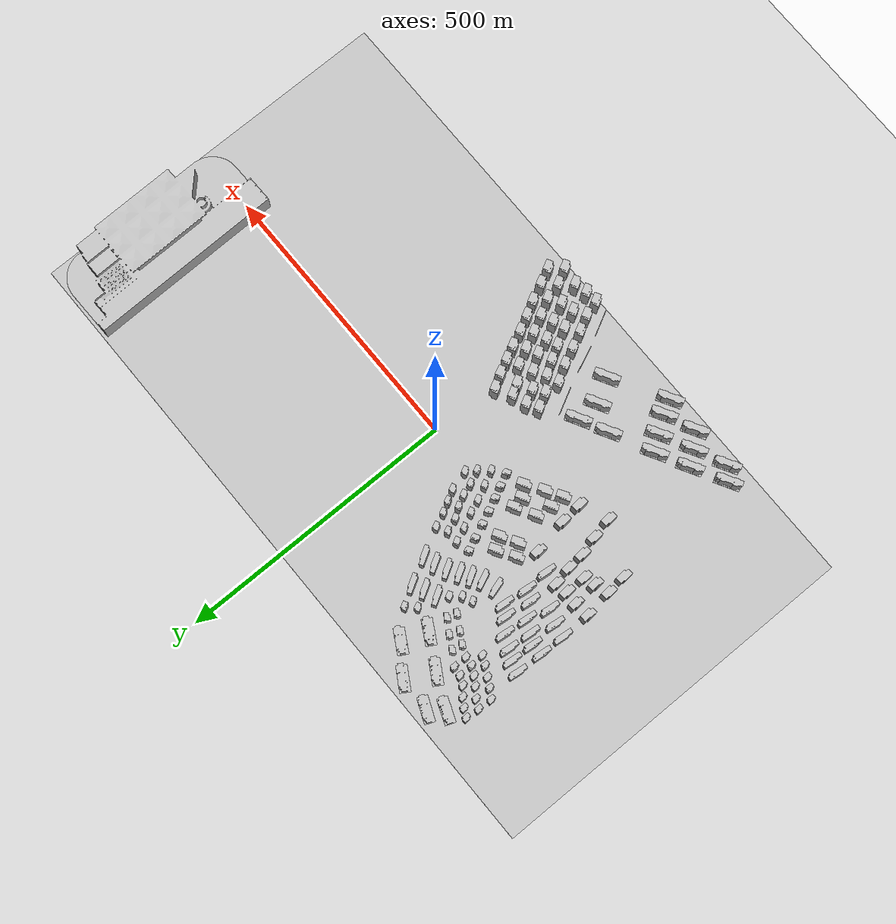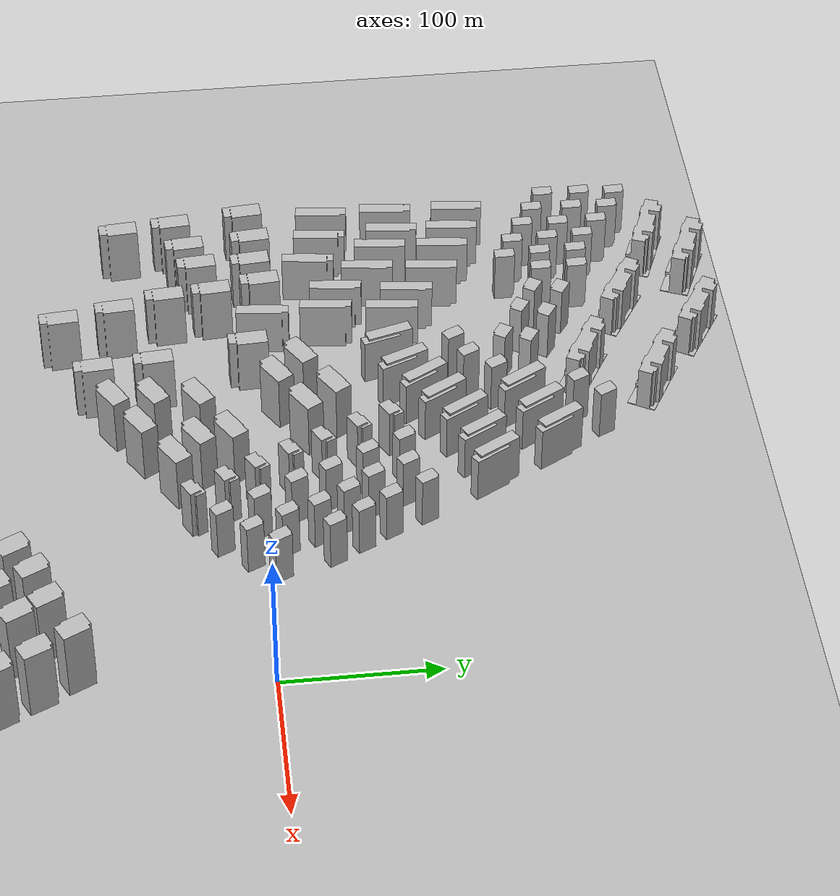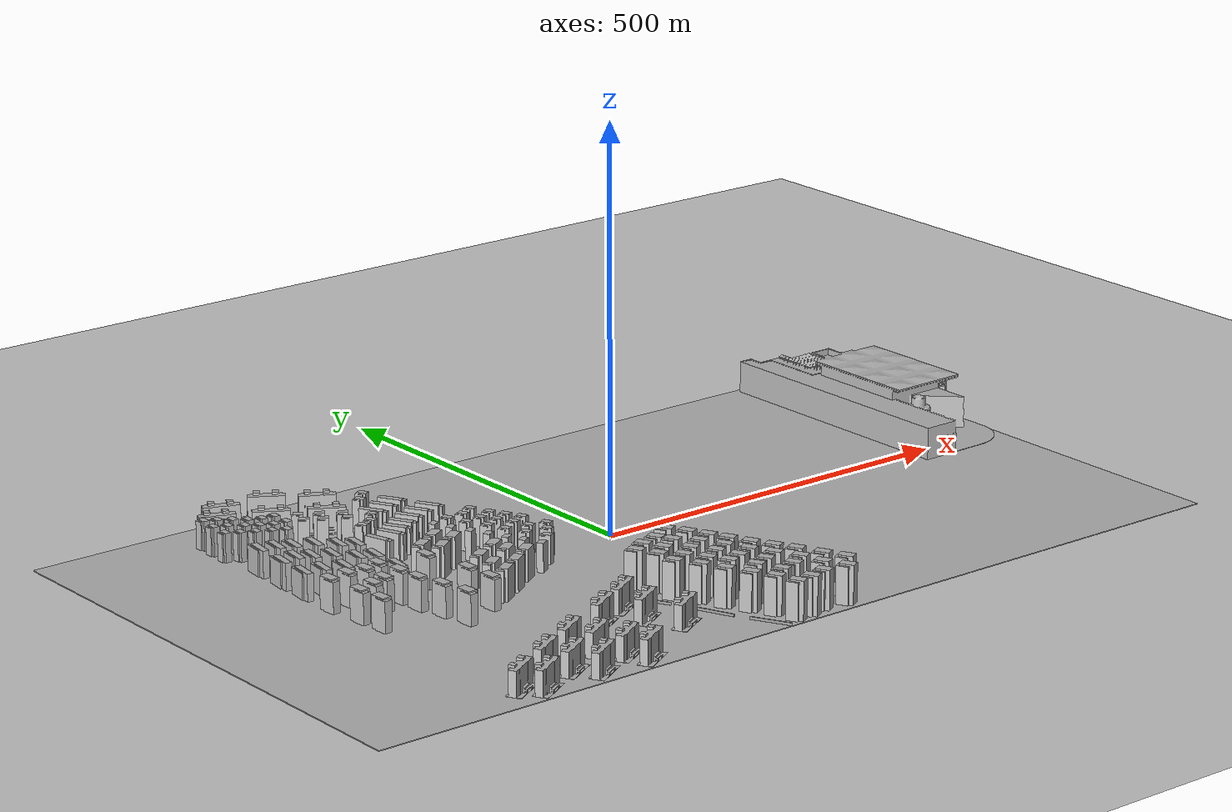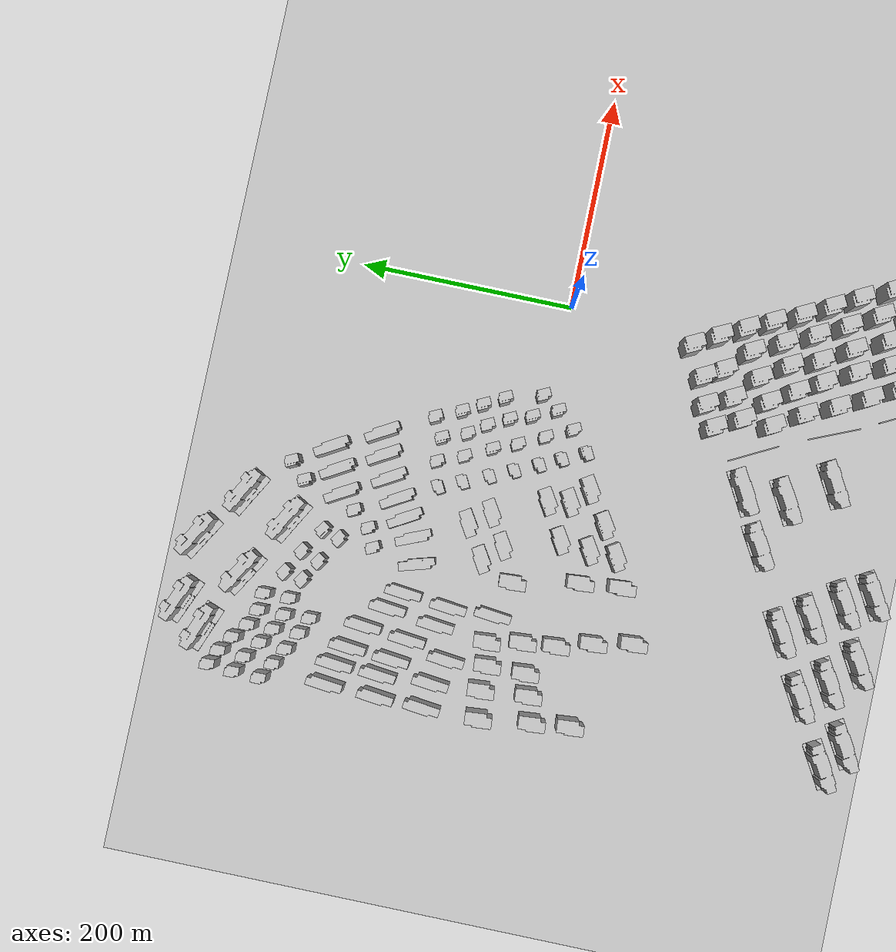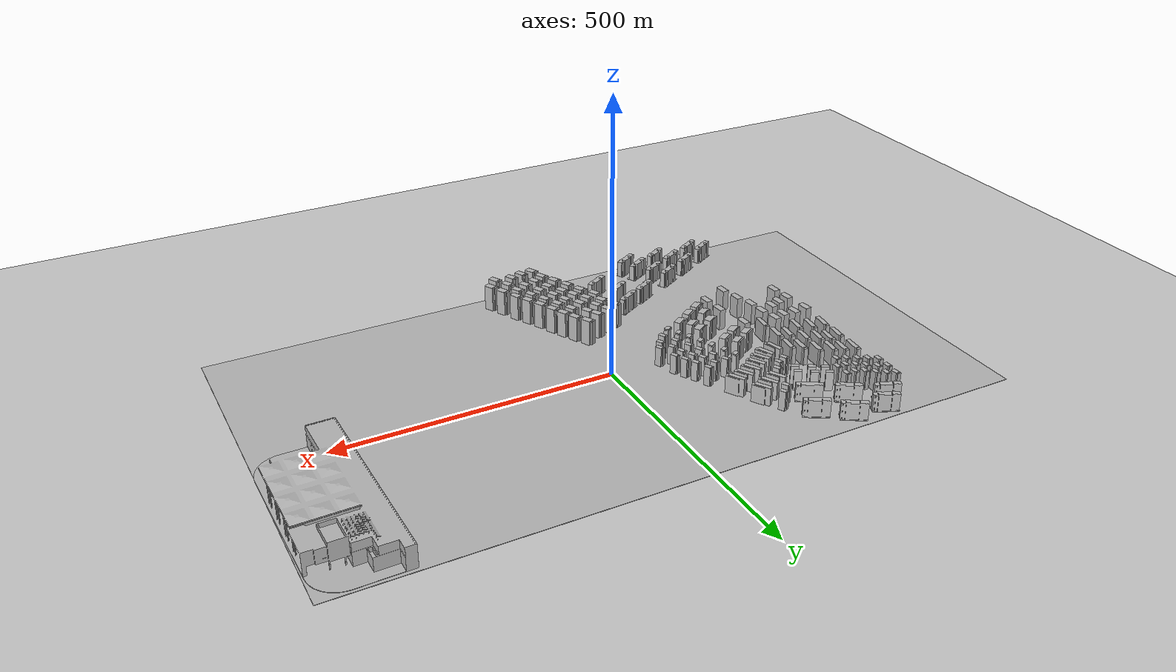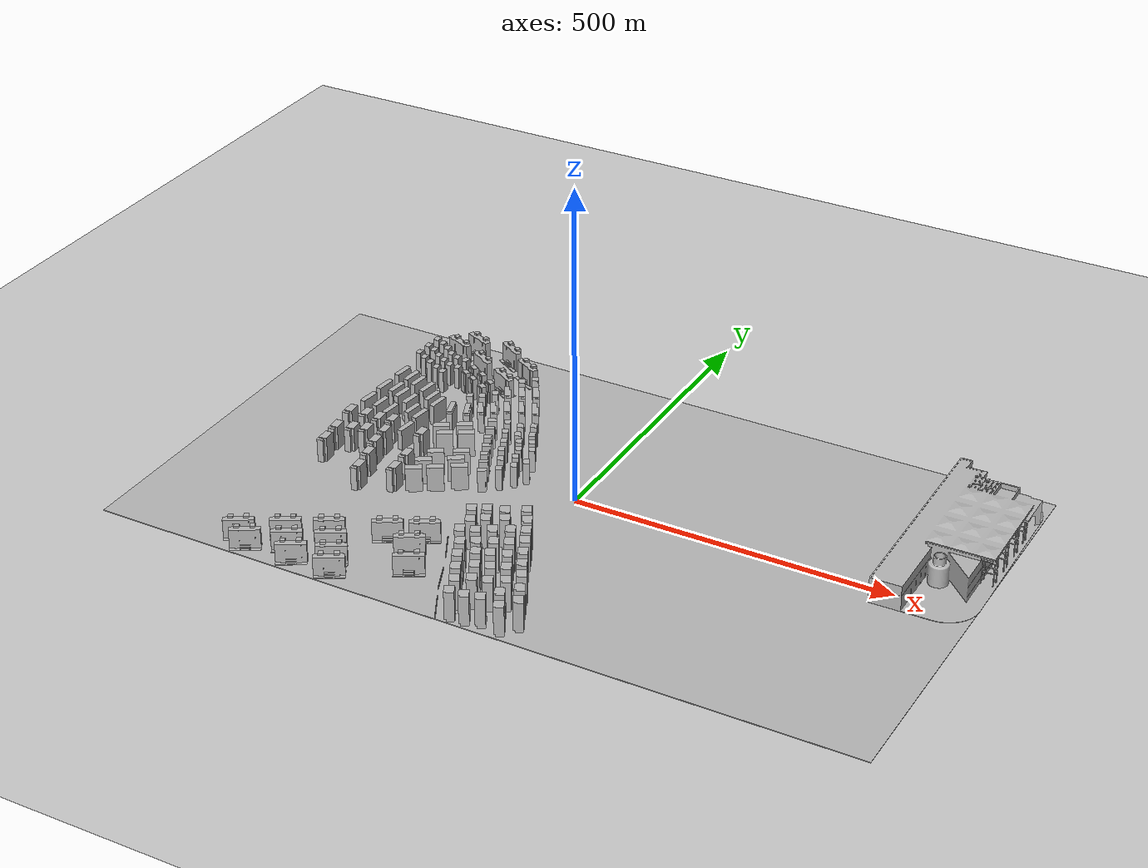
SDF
<sdf version="1.7">
 <world name="default">
  <light name="sun" type="directional">
   <pose>0 0 10 0 -0 0</pose>
   <diffuse>0.8 0.8 0.8 1</diffuse>
   <specular>0.2 0.2 0.2 1</specular>
   <attenuation>
    <range>1000</range>
    <constant>0.9</constant>
    <linear>0.01</linear>
    <quadratic>0.001</quadratic>
   </attenuation>
   <direction>-0.5 0.1 -0.9</direction>
   <spot><inner_angle>0</inner_angle><outer_angle>0</outer_angle><falloff>0</falloff></spot>
  </light>
  <model name="ground_plane">
   <static>1</static>
   <link name="link">
    <collision name="collision">
     <geometry><plane><normal>0 0 1</normal><size>100 100</size></plane></geometry>
     <surface><friction><ode><mu>100</mu><mu2>50</mu2></ode></friction></surface>
    </collision>
    <visual name="visual">
     <cast_shadows>0</cast_shadows>
     <geometry><plane><normal>0 0 1</normal><size>100 100</size></plane></geometry>
     <material>
      <script><uri>file://media/materials/scripts/gazebo.material</uri><name>Gazebo/Grey</name></script>
     </material>
    </visual>
   </link>
  </model>
  <gravity>0 0 -9.8</gravity>
  <magnetic_field>6e-06 2.3e-05 -4.2e-05</magnetic_field>
  <atmosphere type="adiabatic"/>
  <physics type="ode">
   <max_step_size>0.001</max_step_size>
   <real_time_factor>1</real_time_factor>
   <real_time_update_rate>1000</real_time_update_rate>
  </physics>
  <scene><ambient>0.4 0.4 0.4 1</ambient><background>0.7 0.7 0.7 1</background><shadows>1</shadows></scene>
  <spherical_coordinates>
   <surface_model>EARTH_WGS84</surface_model>
   <latitude_deg>0</latitude_deg>
   <longitude_deg>0</longitude_deg>
   <elevation>0</elevation>
   <heading_deg>0</heading_deg>
  </spherical_coordinates>
  <model name="apartment1_clone_15_clone_3_clone">
   <static>1</static>
   <link name="link_0">
    <inertial>
     <mass>1</mass>
     <inertia>
      <ixx>0.166667</ixx>
      <ixy>0</ixy>
      <ixz>0</ixz>
      <iyy>0.166667</iyy>
      <iyz>0</iyz>
      <izz>0.166667</izz>
     </inertia>
    </inertial>
    <pose>1e-06 -0 0 0 -0 0</pose>
    <visual name="visual">
     <geometry>
      <mesh><uri>model://apartment1/scripts/apartment1.dae</uri><scale>0.3 0.3 0.4</scale></mesh>
     </geometry>
     <material>
      <lighting>1</lighting>
      <script><uri>model://apartment1/scripts/apartment1.jpg</uri><name>__default__</name></script>
      <shader type="pixel"/>
     </material>
    </visual>
    <collision name="collision">
     <geometry>
      <mesh><uri>model://apartment1/scripts/apartment1.dae</uri><scale>0.3 0.3 0.4</scale></mesh>
     </geometry>
     <surface>
      <friction>
       <ode><mu>1</mu><mu2>1</mu2><fdir1>0 0 0</fdir1><slip1>0</slip1><slip2>0</slip2></ode>
       <torsional>
        <coefficient>1</coefficient>
        <patch_radius>0</patch_radius>
        <surface_radius>0</surface_radius>
        <use_patch_radius>1</use_patch_radius>
        <ode><slip>0</slip></ode>
       </torsional>
      </friction>
      <bounce><restitution_coefficient>0</restitution_coefficient><threshold>1e+06</threshold></bounce>
      <contact>
       <collide_without_contact>0</collide_without_contact>
       <collide_without_contact_bitmask>1</collide_without_contact_bitmask>
       <collide_bitmask>1</collide_bitmask>
       <ode>
        <soft_cfm>0</soft_cfm>
        <soft_erp>0.2</soft_erp>
        <kp>1e+13</kp>
        <kd>1</kd>
        <max_vel>0.01</max_vel>
        <min_depth>0</min_depth>
       </ode>
       <bullet>
        <split_impulse>1</split_impulse>
        <split_impulse_penetration_threshold>-0.01</split_impulse_penetration_threshold>
        <soft_cfm>0</soft_cfm>
        <soft_erp>0.2</soft_erp>
        <kp>1e+13</kp>
        <kd>1</kd>
       </bullet>
      </contact>
     </surface>
    </collision>
   </link>
   <static>0</static>
   <pose>1.05623 -139.042 0 0 -0 0.446505</pose>
  </model>
  <model name="apartment1_clone_15_clone_3_clone_0">
   <static>1</static>
   <link name="link_0">
    <inertial>
     <mass>1</mass>
     <inertia>
      <ixx>0.166667</ixx>
      <ixy>0</ixy>
      <ixz>0</ixz>
      <iyy>0.166667</iyy>
      <iyz>0</iyz>
      <izz>0.166667</izz>
     </inertia>
    </inertial>
    <pose>1e-06 -0 0 0 -0 0</pose>
    <visual name="visual">
     <geometry>
      <mesh><uri>model://apartment1/scripts/apartment1.dae</uri><scale>0.3 0.3 0.4</scale></mesh>
     </geometry>
     <material>
      <lighting>1</lighting>
      <script><uri>model://apartment1/scripts/apartment1.jpg</uri><name>__default__</name></script>
      <shader type="pixel"/>
     </material>
    </visual>
    <collision name="collision">
     <geometry>
      <mesh><uri>model://apartment1/scripts/apartment1.dae</uri><scale>0.3 0.3 0.4</scale></mesh>
     </geometry>
     <surface>
      <friction>
       <ode><mu>1</mu><mu2>1</mu2><fdir1>0 0 0</fdir1><slip1>0</slip1><slip2>0</slip2></ode>
       <torsional>
        <coefficient>1</coefficient>
        <patch_radius>0</patch_radius>
        <surface_radius>0</surface_radius>
        <use_patch_radius>1</use_patch_radius>
        <ode><slip>0</slip></ode>
       </torsional>
      </friction>
      <bounce><restitution_coefficient>0</restitution_coefficient><threshold>1e+06</threshold></bounce>
      <contact>
       <collide_without_contact>0</collide_without_contact>
       <collide_without_contact_bitmask>1</collide_without_contact_bitmask>
       <collide_bitmask>1</collide_bitmask>
       <ode>
        <soft_cfm>0</soft_cfm>
        <soft_erp>0.2</soft_erp>
        <kp>1e+13</kp>
        <kd>1</kd>
        <max_vel>0.01</max_vel>
        <min_depth>0</min_depth>
       </ode>
       <bullet>
        <split_impulse>1</split_impulse>
        <split_impulse_penetration_threshold>-0.01</split_impulse_penetration_threshold>
        <soft_cfm>0</soft_cfm>
        <soft_erp>0.2</soft_erp>
        <kp>1e+13</kp>
        <kd>1</kd>
       </bullet>
      </contact>
     </surface>
    </collision>
   </link>
   <static>0</static>
   <pose>12.7683 -162.066 0 0 -0 0.473091</pose>
  </model>
  <model name="apartment1_clone_15_clone_3_clone_0_clone">
   <static>1</static>
   <link name="link_0">
    <inertial>
     <mass>1</mass>
     <inertia>
      <ixx>0.166667</ixx>
      <ixy>0</ixy>
      <ixz>0</ixz>
      <iyy>0.166667</iyy>
      <iyz>0</iyz>
      <izz>0.166667</izz>
     </inertia>
    </inertial>
    <pose>1e-06 -0 0 0 -0 0</pose>
    <visual name="visual">
     <geometry>
      <mesh><uri>model://apartment1/scripts/apartment1.dae</uri><scale>0.3 0.3 0.4</scale></mesh>
     </geometry>
     <material>
      <lighting>1</lighting>
      <script><uri>model://apartment1/scripts/apartment1.jpg</uri><name>__default__</name></script>
      <shader type="pixel"/>
     </material>
    </visual>
    <collision name="collision">
     <geometry>
      <mesh><uri>model://apartment1/scripts/apartment1.dae</uri><scale>0.3 0.3 0.4</scale></mesh>
     </geometry>
     <surface>
      <friction>
       <ode><mu>1</mu><mu2>1</mu2><fdir1>0 0 0</fdir1><slip1>0</slip1><slip2>0</slip2></ode>
       <torsional>
        <coefficient>1</coefficient>
        <patch_radius>0</patch_radius>
        <surface_radius>0</surface_radius>
        <use_patch_radius>1</use_patch_radius>
        <ode><slip>0</slip></ode>
       </torsional>
      </friction>
      <bounce><restitution_coefficient>0</restitution_coefficient><threshold>1e+06</threshold></bounce>
      <contact>
       <collide_without_contact>0</collide_without_contact>
       <collide_without_contact_bitmask>1</collide_without_contact_bitmask>
       <collide_bitmask>1</collide_bitmask>
       <ode>
        <soft_cfm>0</soft_cfm>
        <soft_erp>0.2</soft_erp>
        <kp>1e+13</kp>
        <kd>1</kd>
        <max_vel>0.01</max_vel>
        <min_depth>0</min_depth>
       </ode>
       <bullet>
        <split_impulse>1</split_impulse>
        <split_impulse_penetration_threshold>-0.01</split_impulse_penetration_threshold>
        <soft_cfm>0</soft_cfm>
        <soft_erp>0.2</soft_erp>
        <kp>1e+13</kp>
        <kd>1</kd>
       </bullet>
      </contact>
     </surface>
    </collision>
   </link>
   <static>0</static>
   <pose>23.7736 -184.606 0 0 -0 0.473091</pose>
  </model>
  <model name="apartment1_clone_15_clone_3_clone_0_clone_0">
   <static>1</static>
   <link name="link_0">
    <inertial>
     <mass>1</mass>
     <inertia>
      <ixx>0.166667</ixx>
      <ixy>0</ixy>
      <ixz>0</ixz>
      <iyy>0.166667</iyy>
      <iyz>0</iyz>
      <izz>0.166667</izz>
     </inertia>
    </inertial>
    <pose>1e-06 -0 0 0 -0 0</pose>
    <visual name="visual">
     <geometry>
      <mesh><uri>model://apartment1/scripts/apartment1.dae</uri><scale>0.3 0.3 0.4</scale></mesh>
     </geometry>
     <material>
      <lighting>1</lighting>
      <script><uri>model://apartment1/scripts/apartment1.jpg</uri><name>__default__</name></script>
      <shader type="pixel"/>
     </material>
    </visual>
    <collision name="collision">
     <geometry>
      <mesh><uri>model://apartment1/scripts/apartment1.dae</uri><scale>0.3 0.3 0.4</scale></mesh>
     </geometry>
     <surface>
      <friction>
       <ode><mu>1</mu><mu2>1</mu2><fdir1>0 0 0</fdir1><slip1>0</slip1><slip2>0</slip2></ode>
       <torsional>
        <coefficient>1</coefficient>
        <patch_radius>0</patch_radius>
        <surface_radius>0</surface_radius>
        <use_patch_radius>1</use_patch_radius>
        <ode><slip>0</slip></ode>
       </torsional>
      </friction>
      <bounce><restitution_coefficient>0</restitution_coefficient><threshold>1e+06</threshold></bounce>
      <contact>
       <collide_without_contact>0</collide_without_contact>
       <collide_without_contact_bitmask>1</collide_without_contact_bitmask>
       <collide_bitmask>1</collide_bitmask>
       <ode>
        <soft_cfm>0</soft_cfm>
        <soft_erp>0.2</soft_erp>
        <kp>1e+13</kp>
        <kd>1</kd>
        <max_vel>0.01</max_vel>
        <min_depth>0</min_depth>
       </ode>
       <bullet>
        <split_impulse>1</split_impulse>
        <split_impulse_penetration_threshold>-0.01</split_impulse_penetration_threshold>
        <soft_cfm>0</soft_cfm>
        <soft_erp>0.2</soft_erp>
        <kp>1e+13</kp>
        <kd>1</kd>
       </bullet>
      </contact>
     </surface>
    </collision>
   </link>
   <static>0</static>
   <pose>35.3869 -210.334 0 0 -0 0.473091</pose>
  </model>
  <model name="apartment1_clone_15_clone_3_clone_0_clone_1">
   <static>1</static>
   <link name="link_0">
    <inertial>
     <mass>1</mass>
     <inertia>
      <ixx>0.166667</ixx>
      <ixy>0</ixy>
      <ixz>0</ixz>
      <iyy>0.166667</iyy>
      <iyz>0</iyz>
      <izz>0.166667</izz>
     </inertia>
    </inertial>
    <pose>1e-06 -0 0 0 -0 0</pose>
    <visual name="visual">
     <geometry>
      <mesh><uri>model://apartment1/scripts/apartment1.dae</uri><scale>0.3 0.3 0.4</scale></mesh>
     </geometry>
     <material>
      <lighting>1</lighting>
      <script><uri>model://apartment1/scripts/apartment1.jpg</uri><name>__default__</name></script>
      <shader type="pixel"/>
     </material>
    </visual>
    <collision name="collision">
     <geometry>
      <mesh><uri>model://apartment1/scripts/apartment1.dae</uri><scale>0.3 0.3 0.4</scale></mesh>
     </geometry>
     <surface>
      <friction>
       <ode><mu>1</mu><mu2>1</mu2><fdir1>0 0 0</fdir1><slip1>0</slip1><slip2>0</slip2></ode>
       <torsional>
        <coefficient>1</coefficient>
        <patch_radius>0</patch_radius>
        <surface_radius>0</surface_radius>
        <use_patch_radius>1</use_patch_radius>
        <ode><slip>0</slip></ode>
       </torsional>
      </friction>
      <bounce><restitution_coefficient>0</restitution_coefficient><threshold>1e+06</threshold></bounce>
      <contact>
       <collide_without_contact>0</collide_without_contact>
       <collide_without_contact_bitmask>1</collide_without_contact_bitmask>
       <collide_bitmask>1</collide_bitmask>
       <ode>
        <soft_cfm>0</soft_cfm>
        <soft_erp>0.2</soft_erp>
        <kp>1e+13</kp>
        <kd>1</kd>
        <max_vel>0.01</max_vel>
        <min_depth>0</min_depth>
       </ode>
       <bullet>
        <split_impulse>1</split_impulse>
        <split_impulse_penetration_threshold>-0.01</split_impulse_penetration_threshold>
        <soft_cfm>0</soft_cfm>
        <soft_erp>0.2</soft_erp>
        <kp>1e+13</kp>
        <kd>1</kd>
       </bullet>
      </contact>
     </surface>
    </collision>
   </link>
   <static>0</static>
   <pose>48.2751 -235.277 0 0 -0 0.473091</pose>
  </model>
  <model name="apartment1_clone_15_clone_3_clone_0_clone_2">
   <static>1</static>
   <link name="link_0">
    <inertial>
     <mass>1</mass>
     <inertia>
      <ixx>0.166667</ixx>
      <ixy>0</ixy>
      <ixz>0</ixz>
      <iyy>0.166667</iyy>
      <iyz>0</iyz>
      <izz>0.166667</izz>
     </inertia>
    </inertial>
    <pose>1e-06 -0 0 0 -0 0</pose>
    <visual name="visual">
     <geometry>
      <mesh><uri>model://apartment1/scripts/apartment1.dae</uri><scale>0.3 0.3 0.4</scale></mesh>
     </geometry>
     <material>
      <lighting>1</lighting>
      <script><uri>model://apartment1/scripts/apartment1.jpg</uri><name>__default__</name></script>
      <shader type="pixel"/>
     </material>
    </visual>
    <collision name="collision">
     <geometry>
      <mesh><uri>model://apartment1/scripts/apartment1.dae</uri><scale>0.3 0.3 0.4</scale></mesh>
     </geometry>
     <surface>
      <friction>
       <ode><mu>1</mu><mu2>1</mu2><fdir1>0 0 0</fdir1><slip1>0</slip1><slip2>0</slip2></ode>
       <torsional>
        <coefficient>1</coefficient>
        <patch_radius>0</patch_radius>
        <surface_radius>0</surface_radius>
        <use_patch_radius>1</use_patch_radius>
        <ode><slip>0</slip></ode>
       </torsional>
      </friction>
      <bounce><restitution_coefficient>0</restitution_coefficient><threshold>1e+06</threshold></bounce>
      <contact>
       <collide_without_contact>0</collide_without_contact>
       <collide_without_contact_bitmask>1</collide_without_contact_bitmask>
       <collide_bitmask>1</collide_bitmask>
       <ode>
        <soft_cfm>0</soft_cfm>
        <soft_erp>0.2</soft_erp>
        <kp>1e+13</kp>
        <kd>1</kd>
        <max_vel>0.01</max_vel>
        <min_depth>0</min_depth>
       </ode>
       <bullet>
        <split_impulse>1</split_impulse>
        <split_impulse_penetration_threshold>-0.01</split_impulse_penetration_threshold>
        <soft_cfm>0</soft_cfm>
        <soft_erp>0.2</soft_erp>
        <kp>1e+13</kp>
        <kd>1</kd>
       </bullet>
      </contact>
     </surface>
    </collision>
   </link>
   <static>0</static>
   <pose>61.6411 -259.292 0 0 -0 0.473091</pose>
  </model>
  <model name="apartment1_clone_15_clone_3_clone_0_clone_3">
   <static>1</static>
   <link name="link_0">
    <inertial>
     <mass>1</mass>
     <inertia>
      <ixx>0.166667</ixx>
      <ixy>0</ixy>
      <ixz>0</ixz>
      <iyy>0.166667</iyy>
      <iyz>0</iyz>
      <izz>0.166667</izz>
     </inertia>
    </inertial>
    <pose>1e-06 -0 0 0 -0 0</pose>
    <visual name="visual">
     <geometry>
      <mesh><uri>model://apartment1/scripts/apartment1.dae</uri><scale>0.3 0.3 0.4</scale></mesh>
     </geometry>
     <material>
      <lighting>1</lighting>
      <script><uri>model://apartment1/scripts/apartment1.jpg</uri><name>__default__</name></script>
      <shader type="pixel"/>
     </material>
    </visual>
    <collision name="collision">
     <geometry>
      <mesh><uri>model://apartment1/scripts/apartment1.dae</uri><scale>0.3 0.3 0.4</scale></mesh>
     </geometry>
     <surface>
      <friction>
       <ode><mu>1</mu><mu2>1</mu2><fdir1>0 0 0</fdir1><slip1>0</slip1><slip2>0</slip2></ode>
       <torsional>
        <coefficient>1</coefficient>
        <patch_radius>0</patch_radius>
        <surface_radius>0</surface_radius>
        <use_patch_radius>1</use_patch_radius>
        <ode><slip>0</slip></ode>
       </torsional>
      </friction>
      <bounce><restitution_coefficient>0</restitution_coefficient><threshold>1e+06</threshold></bounce>
      <contact>
       <collide_without_contact>0</collide_without_contact>
       <collide_without_contact_bitmask>1</collide_without_contact_bitmask>
       <collide_bitmask>1</collide_bitmask>
       <ode>
        <soft_cfm>0</soft_cfm>
        <soft_erp>0.2</soft_erp>
        <kp>1e+13</kp>
        <kd>1</kd>
        <max_vel>0.01</max_vel>
        <min_depth>0</min_depth>
       </ode>
       <bullet>
        <split_impulse>1</split_impulse>
        <split_impulse_penetration_threshold>-0.01</split_impulse_penetration_threshold>
        <soft_cfm>0</soft_cfm>
        <soft_erp>0.2</soft_erp>
        <kp>1e+13</kp>
        <kd>1</kd>
       </bullet>
      </contact>
     </surface>
    </collision>
   </link>
   <static>0</static>
   <pose>75.4809 -288.417 0 0 -0 0.473091</pose>
  </model>
  <model name="apartment1_clone_15_clone_3_clone_0_clone_4">
   <static>1</static>
   <link name="link_0">
    <inertial>
     <mass>1</mass>
     <inertia>
      <ixx>0.166667</ixx>
      <ixy>0</ixy>
      <ixz>0</ixz>
      <iyy>0.166667</iyy>
      <iyz>0</iyz>
      <izz>0.166667</izz>
     </inertia>
    </inertial>
    <pose>1e-06 -0 0 0 -0 0</pose>
    <visual name="visual">
     <geometry>
      <mesh><uri>model://apartment1/scripts/apartment1.dae</uri><scale>0.3 0.3 0.4</scale></mesh>
     </geometry>
     <material>
      <lighting>1</lighting>
      <script><uri>model://apartment1/scripts/apartment1.jpg</uri><name>__default__</name></script>
      <shader type="pixel"/>
     </material>
    </visual>
    <collision name="collision">
     <geometry>
      <mesh><uri>model://apartment1/scripts/apartment1.dae</uri><scale>0.3 0.3 0.4</scale></mesh>
     </geometry>
     <surface>
      <friction>
       <ode><mu>1</mu><mu2>1</mu2><fdir1>0 0 0</fdir1><slip1>0</slip1><slip2>0</slip2></ode>
       <torsional>
        <coefficient>1</coefficient>
        <patch_radius>0</patch_radius>
        <surface_radius>0</surface_radius>
        <use_patch_radius>1</use_patch_radius>
        <ode><slip>0</slip></ode>
       </torsional>
      </friction>
      <bounce><restitution_coefficient>0</restitution_coefficient><threshold>1e+06</threshold></bounce>
      <contact>
       <collide_without_contact>0</collide_without_contact>
       <collide_without_contact_bitmask>1</collide_without_contact_bitmask>
       <collide_bitmask>1</collide_bitmask>
       <ode>
        <soft_cfm>0</soft_cfm>
        <soft_erp>0.2</soft_erp>
        <kp>1e+13</kp>
        <kd>1</kd>
        <max_vel>0.01</max_vel>
        <min_depth>0</min_depth>
       </ode>
       <bullet>
        <split_impulse>1</split_impulse>
        <split_impulse_penetration_threshold>-0.01</split_impulse_penetration_threshold>
        <soft_cfm>0</soft_cfm>
        <soft_erp>0.2</soft_erp>
        <kp>1e+13</kp>
        <kd>1</kd>
       </bullet>
      </contact>
     </surface>
    </collision>
   </link>
   <static>0</static>
   <pose>88.1818 -314.395 0 0 -0 0.473091</pose>
  </model>
  <model name="apartment1_clone_15_clone_3_clone_0_clone_7">
   <static>1</static>
   <link name="link_0">
    <inertial>
     <mass>1</mass>
     <inertia>
      <ixx>0.166667</ixx>
      <ixy>0</ixy>
      <ixz>0</ixz>
      <iyy>0.166667</iyy>
      <iyz>0</iyz>
      <izz>0.166667</izz>
     </inertia>
    </inertial>
    <pose>1e-06 -0 0 0 -0 0</pose>
    <visual name="visual">
     <geometry>
      <mesh><uri>model://apartment1/scripts/apartment1.dae</uri><scale>0.3 0.3 0.4</scale></mesh>
     </geometry>
     <material>
      <lighting>1</lighting>
      <script><uri>model://apartment1/scripts/apartment1.jpg</uri><name>__default__</name></script>
      <shader type="pixel"/>
     </material>
    </visual>
    <collision name="collision">
     <geometry>
      <mesh><uri>model://apartment1/scripts/apartment1.dae</uri><scale>0.3 0.3 0.4</scale></mesh>
     </geometry>
     <surface>
      <friction>
       <ode><mu>1</mu><mu2>1</mu2><fdir1>0 0 0</fdir1><slip1>0</slip1><slip2>0</slip2></ode>
       <torsional>
        <coefficient>1</coefficient>
        <patch_radius>0</patch_radius>
        <surface_radius>0</surface_radius>
        <use_patch_radius>1</use_patch_radius>
        <ode><slip>0</slip></ode>
       </torsional>
      </friction>
      <bounce><restitution_coefficient>0</restitution_coefficient><threshold>1e+06</threshold></bounce>
      <contact>
       <collide_without_contact>0</collide_without_contact>
       <collide_without_contact_bitmask>1</collide_without_contact_bitmask>
       <collide_bitmask>1</collide_bitmask>
       <ode>
        <soft_cfm>0</soft_cfm>
        <soft_erp>0.2</soft_erp>
        <kp>1e+13</kp>
        <kd>1</kd>
        <max_vel>0.01</max_vel>
        <min_depth>0</min_depth>
       </ode>
       <bullet>
        <split_impulse>1</split_impulse>
        <split_impulse_penetration_threshold>-0.01</split_impulse_penetration_threshold>
        <soft_cfm>0</soft_cfm>
        <soft_erp>0.2</soft_erp>
        <kp>1e+13</kp>
        <kd>1</kd>
       </bullet>
      </contact>
     </surface>
    </collision>
   </link>
   <static>0</static>
   <pose>56.6933 -309.959 0 0 -0 0.473091</pose>
  </model>
  <model name="apartment1_clone_15_clone_3_clone_0_clone_8">
   <static>1</static>
   <link name="link_0">
    <inertial>
     <mass>1</mass>
     <inertia>
      <ixx>0.166667</ixx>
      <ixy>0</ixy>
      <ixz>0</ixz>
      <iyy>0.166667</iyy>
      <iyz>0</iyz>
      <izz>0.166667</izz>
     </inertia>
    </inertial>
    <pose>1e-06 -0 0 0 -0 0</pose>
    <visual name="visual">
     <geometry>
      <mesh><uri>model://apartment1/scripts/apartment1.dae</uri><scale>0.3 0.3 0.4</scale></mesh>
     </geometry>
     <material>
      <lighting>1</lighting>
      <script><uri>model://apartment1/scripts/apartment1.jpg</uri><name>__default__</name></script>
      <shader type="pixel"/>
     </material>
    </visual>
    <collision name="collision">
     <geometry>
      <mesh><uri>model://apartment1/scripts/apartment1.dae</uri><scale>0.3 0.3 0.4</scale></mesh>
     </geometry>
     <surface>
      <friction>
       <ode><mu>1</mu><mu2>1</mu2><fdir1>0 0 0</fdir1><slip1>0</slip1><slip2>0</slip2></ode>
       <torsional>
        <coefficient>1</coefficient>
        <patch_radius>0</patch_radius>
        <surface_radius>0</surface_radius>
        <use_patch_radius>1</use_patch_radius>
        <ode><slip>0</slip></ode>
       </torsional>
      </friction>
      <bounce><restitution_coefficient>0</restitution_coefficient><threshold>1e+06</threshold></bounce>
      <contact>
       <collide_without_contact>0</collide_without_contact>
       <collide_without_contact_bitmask>1</collide_without_contact_bitmask>
       <collide_bitmask>1</collide_bitmask>
       <ode>
        <soft_cfm>0</soft_cfm>
        <soft_erp>0.2</soft_erp>
        <kp>1e+13</kp>
        <kd>1</kd>
        <max_vel>0.01</max_vel>
        <min_depth>0</min_depth>
       </ode>
       <bullet>
        <split_impulse>1</split_impulse>
        <split_impulse_penetration_threshold>-0.01</split_impulse_penetration_threshold>
        <soft_cfm>0</soft_cfm>
        <soft_erp>0.2</soft_erp>
        <kp>1e+13</kp>
        <kd>1</kd>
       </bullet>
      </contact>
     </surface>
    </collision>
   </link>
   <static>0</static>
   <pose>49.244 -280.71 0 0 -0 0.473091</pose>
  </model>
  <model name="apartment1_clone_15_clone_3_clone_0_clone_9">
   <static>1</static>
   <link name="link_0">
    <inertial>
     <mass>1</mass>
     <inertia>
      <ixx>0.166667</ixx>
      <ixy>0</ixy>
      <ixz>0</ixz>
      <iyy>0.166667</iyy>
      <iyz>0</iyz>
      <izz>0.166667</izz>
     </inertia>
    </inertial>
    <pose>1e-06 -0 0 0 -0 0</pose>
    <visual name="visual">
     <geometry>
      <mesh><uri>model://apartment1/scripts/apartment1.dae</uri><scale>0.3 0.3 0.4</scale></mesh>
     </geometry>
     <material>
      <lighting>1</lighting>
      <script><uri>model://apartment1/scripts/apartment1.jpg</uri><name>__default__</name></script>
      <shader type="pixel"/>
     </material>
    </visual>
    <collision name="collision">
     <geometry>
      <mesh><uri>model://apartment1/scripts/apartment1.dae</uri><scale>0.3 0.3 0.4</scale></mesh>
     </geometry>
     <surface>
      <friction>
       <ode><mu>1</mu><mu2>1</mu2><fdir1>0 0 0</fdir1><slip1>0</slip1><slip2>0</slip2></ode>
       <torsional>
        <coefficient>1</coefficient>
        <patch_radius>0</patch_radius>
        <surface_radius>0</surface_radius>
        <use_patch_radius>1</use_patch_radius>
        <ode><slip>0</slip></ode>
       </torsional>
      </friction>
      <bounce><restitution_coefficient>0</restitution_coefficient><threshold>1e+06</threshold></bounce>
      <contact>
       <collide_without_contact>0</collide_without_contact>
       <collide_without_contact_bitmask>1</collide_without_contact_bitmask>
       <collide_bitmask>1</collide_bitmask>
       <ode>
        <soft_cfm>0</soft_cfm>
        <soft_erp>0.2</soft_erp>
        <kp>1e+13</kp>
        <kd>1</kd>
        <max_vel>0.01</max_vel>
        <min_depth>0</min_depth>
       </ode>
       <bullet>
        <split_impulse>1</split_impulse>
        <split_impulse_penetration_threshold>-0.01</split_impulse_penetration_threshold>
        <soft_cfm>0</soft_cfm>
        <soft_erp>0.2</soft_erp>
        <kp>1e+13</kp>
        <kd>1</kd>
       </bullet>
      </contact>
     </surface>
    </collision>
   </link>
   <static>0</static>
   <pose>34.0112 -253.38 0 0 -0 0.473091</pose>
  </model>
  <model name="apartment1_clone_15_clone_3_clone_0_clone_10">
   <static>1</static>
   <link name="link_0">
    <inertial>
     <mass>1</mass>
     <inertia>
      <ixx>0.166667</ixx>
      <ixy>0</ixy>
      <ixz>0</ixz>
      <iyy>0.166667</iyy>
      <iyz>0</iyz>
      <izz>0.166667</izz>
     </inertia>
    </inertial>
    <pose>1e-06 -0 0 0 -0 0</pose>
    <visual name="visual">
     <geometry>
      <mesh><uri>model://apartment1/scripts/apartment1.dae</uri><scale>0.3 0.3 0.4</scale></mesh>
     </geometry>
     <material>
      <lighting>1</lighting>
      <script><uri>model://apartment1/scripts/apartment1.jpg</uri><name>__default__</name></script>
      <shader type="pixel"/>
     </material>
    </visual>
    <collision name="collision">
     <geometry>
      <mesh><uri>model://apartment1/scripts/apartment1.dae</uri><scale>0.3 0.3 0.4</scale></mesh>
     </geometry>
     <surface>
      <friction>
       <ode><mu>1</mu><mu2>1</mu2><fdir1>0 0 0</fdir1><slip1>0</slip1><slip2>0</slip2></ode>
       <torsional>
        <coefficient>1</coefficient>
        <patch_radius>0</patch_radius>
        <surface_radius>0</surface_radius>
        <use_patch_radius>1</use_patch_radius>
        <ode><slip>0</slip></ode>
       </torsional>
      </friction>
      <bounce><restitution_coefficient>0</restitution_coefficient><threshold>1e+06</threshold></bounce>
      <contact>
       <collide_without_contact>0</collide_without_contact>
       <collide_without_contact_bitmask>1</collide_without_contact_bitmask>
       <collide_bitmask>1</collide_bitmask>
       <ode>
        <soft_cfm>0</soft_cfm>
        <soft_erp>0.2</soft_erp>
        <kp>1e+13</kp>
        <kd>1</kd>
        <max_vel>0.01</max_vel>
        <min_depth>0</min_depth>
       </ode>
       <bullet>
        <split_impulse>1</split_impulse>
        <split_impulse_penetration_threshold>-0.01</split_impulse_penetration_threshold>
        <soft_cfm>0</soft_cfm>
        <soft_erp>0.2</soft_erp>
        <kp>1e+13</kp>
        <kd>1</kd>
       </bullet>
      </contact>
     </surface>
    </collision>
   </link>
   <static>0</static>
   <pose>19.678 -226.09 0 0 -0 0.473091</pose>
  </model>
  <model name="apartment1_clone_15_clone_3_clone_0_clone_11">
   <static>1</static>
   <link name="link_0">
    <inertial>
     <mass>1</mass>
     <inertia>
      <ixx>0.166667</ixx>
      <ixy>0</ixy>
      <ixz>0</ixz>
      <iyy>0.166667</iyy>
      <iyz>0</iyz>
      <izz>0.166667</izz>
     </inertia>
    </inertial>
    <pose>1e-06 -0 0 0 -0 0</pose>
    <visual name="visual">
     <geometry>
      <mesh><uri>model://apartment1/scripts/apartment1.dae</uri><scale>0.3 0.3 0.4</scale></mesh>
     </geometry>
     <material>
      <lighting>1</lighting>
      <script><uri>model://apartment1/scripts/apartment1.jpg</uri><name>__default__</name></script>
      <shader type="pixel"/>
     </material>
    </visual>
    <collision name="collision">
     <geometry>
      <mesh><uri>model://apartment1/scripts/apartment1.dae</uri><scale>0.3 0.3 0.4</scale></mesh>
     </geometry>
     <surface>
      <friction>
       <ode><mu>1</mu><mu2>1</mu2><fdir1>0 0 0</fdir1><slip1>0</slip1><slip2>0</slip2></ode>
       <torsional>
        <coefficient>1</coefficient>
        <patch_radius>0</patch_radius>
        <surface_radius>0</surface_radius>
        <use_patch_radius>1</use_patch_radius>
        <ode><slip>0</slip></ode>
       </torsional>
      </friction>
      <bounce><restitution_coefficient>0</restitution_coefficient><threshold>1e+06</threshold></bounce>
      <contact>
       <collide_without_contact>0</collide_without_contact>
       <collide_without_contact_bitmask>1</collide_without_contact_bitmask>
       <collide_bitmask>1</collide_bitmask>
       <ode>
        <soft_cfm>0</soft_cfm>
        <soft_erp>0.2</soft_erp>
        <kp>1e+13</kp>
        <kd>1</kd>
        <max_vel>0.01</max_vel>
        <min_depth>0</min_depth>
       </ode>
       <bullet>
        <split_impulse>1</split_impulse>
        <split_impulse_penetration_threshold>-0.01</split_impulse_penetration_threshold>
        <soft_cfm>0</soft_cfm>
        <soft_erp>0.2</soft_erp>
        <kp>1e+13</kp>
        <kd>1</kd>
       </bullet>
      </contact>
     </surface>
    </collision>
   </link>
   <static>0</static>
   <pose>6.86659 -198.522 0 0 -0 0.473091</pose>
  </model>
  <model name="apartment1_clone_15_clone_3_clone_0_clone_12">
   <static>1</static>
   <link name="link_0">
    <inertial>
     <mass>1</mass>
     <inertia>
      <ixx>0.166667</ixx>
      <ixy>0</ixy>
      <ixz>0</ixz>
      <iyy>0.166667</iyy>
      <iyz>0</iyz>
      <izz>0.166667</izz>
     </inertia>
    </inertial>
    <pose>1e-06 -0 0 0 -0 0</pose>
    <visual name="visual">
     <geometry>
      <mesh><uri>model://apartment1/scripts/apartment1.dae</uri><scale>0.3 0.3 0.4</scale></mesh>
     </geometry>
     <material>
      <lighting>1</lighting>
      <script><uri>model://apartment1/scripts/apartment1.jpg</uri><name>__default__</name></script>
      <shader type="pixel"/>
     </material>
    </visual>
    <collision name="collision">
     <geometry>
      <mesh><uri>model://apartment1/scripts/apartment1.dae</uri><scale>0.3 0.3 0.4</scale></mesh>
     </geometry>
     <surface>
      <friction>
       <ode><mu>1</mu><mu2>1</mu2><fdir1>0 0 0</fdir1><slip1>0</slip1><slip2>0</slip2></ode>
       <torsional>
        <coefficient>1</coefficient>
        <patch_radius>0</patch_radius>
        <surface_radius>0</surface_radius>
        <use_patch_radius>1</use_patch_radius>
        <ode><slip>0</slip></ode>
       </torsional>
      </friction>
      <bounce><restitution_coefficient>0</restitution_coefficient><threshold>1e+06</threshold></bounce>
      <contact>
       <collide_without_contact>0</collide_without_contact>
       <collide_without_contact_bitmask>1</collide_without_contact_bitmask>
       <collide_bitmask>1</collide_bitmask>
       <ode>
        <soft_cfm>0</soft_cfm>
        <soft_erp>0.2</soft_erp>
        <kp>1e+13</kp>
        <kd>1</kd>
        <max_vel>0.01</max_vel>
        <min_depth>0</min_depth>
       </ode>
       <bullet>
        <split_impulse>1</split_impulse>
        <split_impulse_penetration_threshold>-0.01</split_impulse_penetration_threshold>
        <soft_cfm>0</soft_cfm>
        <soft_erp>0.2</soft_erp>
        <kp>1e+13</kp>
        <kd>1</kd>
       </bullet>
      </contact>
     </surface>
    </collision>
   </link>
   <static>0</static>
   <pose>-7.35773 -170.94 0 0 -0 0.473091</pose>
  </model>
  <model name="apartment1_clone_15_clone_3_clone_0_clone_13">
   <static>1</static>
   <link name="link_0">
    <inertial>
     <mass>1</mass>
     <inertia>
      <ixx>0.166667</ixx>
      <ixy>0</ixy>
      <ixz>0</ixz>
      <iyy>0.166667</iyy>
      <iyz>0</iyz>
      <izz>0.166667</izz>
     </inertia>
    </inertial>
    <pose>1e-06 -0 0 0 -0 0</pose>
    <visual name="visual">
     <geometry>
      <mesh><uri>model://apartment1/scripts/apartment1.dae</uri><scale>0.3 0.3 0.4</scale></mesh>
     </geometry>
     <material>
      <lighting>1</lighting>
      <script><uri>model://apartment1/scripts/apartment1.jpg</uri><name>__default__</name></script>
      <shader type="pixel"/>
     </material>
    </visual>
    <collision name="collision">
     <geometry>
      <mesh><uri>model://apartment1/scripts/apartment1.dae</uri><scale>0.3 0.3 0.4</scale></mesh>
     </geometry>
     <surface>
      <friction>
       <ode><mu>1</mu><mu2>1</mu2><fdir1>0 0 0</fdir1><slip1>0</slip1><slip2>0</slip2></ode>
       <torsional>
        <coefficient>1</coefficient>
        <patch_radius>0</patch_radius>
        <surface_radius>0</surface_radius>
        <use_patch_radius>1</use_patch_radius>
        <ode><slip>0</slip></ode>
       </torsional>
      </friction>
      <bounce><restitution_coefficient>0</restitution_coefficient><threshold>1e+06</threshold></bounce>
      <contact>
       <collide_without_contact>0</collide_without_contact>
       <collide_without_contact_bitmask>1</collide_without_contact_bitmask>
       <collide_bitmask>1</collide_bitmask>
       <ode>
        <soft_cfm>0</soft_cfm>
        <soft_erp>0.2</soft_erp>
        <kp>1e+13</kp>
        <kd>1</kd>
        <max_vel>0.01</max_vel>
        <min_depth>0</min_depth>
       </ode>
       <bullet>
        <split_impulse>1</split_impulse>
        <split_impulse_penetration_threshold>-0.01</split_impulse_penetration_threshold>
        <soft_cfm>0</soft_cfm>
        <soft_erp>0.2</soft_erp>
        <kp>1e+13</kp>
        <kd>1</kd>
       </bullet>
      </contact>
     </surface>
    </collision>
   </link>
   <static>0</static>
   <pose>-29.0155 -149.283 0 0 -0 0.473091</pose>
  </model>
  <model name="apartment1_clone_15_clone_3_clone_0_clone_14">
   <static>1</static>
   <link name="link_0">
    <inertial>
     <mass>1</mass>
     <inertia>
      <ixx>0.166667</ixx>
      <ixy>0</ixy>
      <ixz>0</ixz>
      <iyy>0.166667</iyy>
      <iyz>0</iyz>
      <izz>0.166667</izz>
     </inertia>
    </inertial>
    <pose>1e-06 -0 0 0 -0 0</pose>
    <visual name="visual">
     <geometry>
      <mesh><uri>model://apartment1/scripts/apartment1.dae</uri><scale>0.3 0.3 0.4</scale></mesh>
     </geometry>
     <material>
      <lighting>1</lighting>
      <script><uri>model://apartment1/scripts/apartment1.jpg</uri><name>__default__</name></script>
      <shader type="pixel"/>
     </material>
    </visual>
    <collision name="collision">
     <geometry>
      <mesh><uri>model://apartment1/scripts/apartment1.dae</uri><scale>0.3 0.3 0.4</scale></mesh>
     </geometry>
     <surface>
      <friction>
       <ode><mu>1</mu><mu2>1</mu2><fdir1>0 0 0</fdir1><slip1>0</slip1><slip2>0</slip2></ode>
       <torsional>
        <coefficient>1</coefficient>
        <patch_radius>0</patch_radius>
        <surface_radius>0</surface_radius>
        <use_patch_radius>1</use_patch_radius>
        <ode><slip>0</slip></ode>
       </torsional>
      </friction>
      <bounce><restitution_coefficient>0</restitution_coefficient><threshold>1e+06</threshold></bounce>
      <contact>
       <collide_without_contact>0</collide_without_contact>
       <collide_without_contact_bitmask>1</collide_without_contact_bitmask>
       <collide_bitmask>1</collide_bitmask>
       <ode>
        <soft_cfm>0</soft_cfm>
        <soft_erp>0.2</soft_erp>
        <kp>1e+13</kp>
        <kd>1</kd>
        <max_vel>0.01</max_vel>
        <min_depth>0</min_depth>
       </ode>
       <bullet>
        <split_impulse>1</split_impulse>
        <split_impulse_penetration_threshold>-0.01</split_impulse_penetration_threshold>
        <soft_cfm>0</soft_cfm>
        <soft_erp>0.2</soft_erp>
        <kp>1e+13</kp>
        <kd>1</kd>
       </bullet>
      </contact>
     </surface>
    </collision>
   </link>
   <static>0</static>
   <pose>-52.8974 -162.265 0 0 -0 0.473091</pose>
  </model>
  <model name="apartment1_clone_15_clone_3_clone_0_clone_15">
   <static>1</static>
   <link name="link_0">
    <inertial>
     <mass>1</mass>
     <inertia>
      <ixx>0.166667</ixx>
      <ixy>0</ixy>
      <ixz>0</ixz>
      <iyy>0.166667</iyy>
      <iyz>0</iyz>
      <izz>0.166667</izz>
     </inertia>
    </inertial>
    <pose>1e-06 -0 0 0 -0 0</pose>
    <visual name="visual">
     <geometry>
      <mesh><uri>model://apartment1/scripts/apartment1.dae</uri><scale>0.3 0.3 0.4</scale></mesh>
     </geometry>
     <material>
      <lighting>1</lighting>
      <script><uri>model://apartment1/scripts/apartment1.jpg</uri><name>__default__</name></script>
      <shader type="pixel"/>
     </material>
    </visual>
    <collision name="collision">
     <geometry>
      <mesh><uri>model://apartment1/scripts/apartment1.dae</uri><scale>0.3 0.3 0.4</scale></mesh>
     </geometry>
     <surface>
      <friction>
       <ode><mu>1</mu><mu2>1</mu2><fdir1>0 0 0</fdir1><slip1>0</slip1><slip2>0</slip2></ode>
       <torsional>
        <coefficient>1</coefficient>
        <patch_radius>0</patch_radius>
        <surface_radius>0</surface_radius>
        <use_patch_radius>1</use_patch_radius>
        <ode><slip>0</slip></ode>
       </torsional>
      </friction>
      <bounce><restitution_coefficient>0</restitution_coefficient><threshold>1e+06</threshold></bounce>
      <contact>
       <collide_without_contact>0</collide_without_contact>
       <collide_without_contact_bitmask>1</collide_without_contact_bitmask>
       <collide_bitmask>1</collide_bitmask>
       <ode>
        <soft_cfm>0</soft_cfm>
        <soft_erp>0.2</soft_erp>
        <kp>1e+13</kp>
        <kd>1</kd>
        <max_vel>0.01</max_vel>
        <min_depth>0</min_depth>
       </ode>
       <bullet>
        <split_impulse>1</split_impulse>
        <split_impulse_penetration_threshold>-0.01</split_impulse_penetration_threshold>
        <soft_cfm>0</soft_cfm>
        <soft_erp>0.2</soft_erp>
        <kp>1e+13</kp>
        <kd>1</kd>
       </bullet>
      </contact>
     </surface>
    </collision>
   </link>
   <static>0</static>
   <pose>-29.8505 -182.312 0 0 -0 0.473091</pose>
  </model>
  <model name="apartment1_clone_15_clone_3_clone_0_clone_16">
   <static>1</static>
   <link name="link_0">
    <inertial>
     <mass>1</mass>
     <inertia>
      <ixx>0.166667</ixx>
      <ixy>0</ixy>
      <ixz>0</ixz>
      <iyy>0.166667</iyy>
      <iyz>0</iyz>
      <izz>0.166667</izz>
     </inertia>
    </inertial>
    <pose>1e-06 -0 0 0 -0 0</pose>
    <visual name="visual">
     <geometry>
      <mesh><uri>model://apartment1/scripts/apartment1.dae</uri><scale>0.3 0.3 0.4</scale></mesh>
     </geometry>
     <material>
      <lighting>1</lighting>
      <script><uri>model://apartment1/scripts/apartment1.jpg</uri><name>__default__</name></script>
      <shader type="pixel"/>
     </material>
    </visual>
    <collision name="collision">
     <geometry>
      <mesh><uri>model://apartment1/scripts/apartment1.dae</uri><scale>0.3 0.3 0.4</scale></mesh>
     </geometry>
     <surface>
      <friction>
       <ode><mu>1</mu><mu2>1</mu2><fdir1>0 0 0</fdir1><slip1>0</slip1><slip2>0</slip2></ode>
       <torsional>
        <coefficient>1</coefficient>
        <patch_radius>0</patch_radius>
        <surface_radius>0</surface_radius>
        <use_patch_radius>1</use_patch_radius>
        <ode><slip>0</slip></ode>
       </torsional>
      </friction>
      <bounce><restitution_coefficient>0</restitution_coefficient><threshold>1e+06</threshold></bounce>
      <contact>
       <collide_without_contact>0</collide_without_contact>
       <collide_without_contact_bitmask>1</collide_without_contact_bitmask>
       <collide_bitmask>1</collide_bitmask>
       <ode>
        <soft_cfm>0</soft_cfm>
        <soft_erp>0.2</soft_erp>
        <kp>1e+13</kp>
        <kd>1</kd>
        <max_vel>0.01</max_vel>
        <min_depth>0</min_depth>
       </ode>
       <bullet>
        <split_impulse>1</split_impulse>
        <split_impulse_penetration_threshold>-0.01</split_impulse_penetration_threshold>
        <soft_cfm>0</soft_cfm>
        <soft_erp>0.2</soft_erp>
        <kp>1e+13</kp>
        <kd>1</kd>
       </bullet>
      </contact>
     </surface>
    </collision>
   </link>
   <static>0</static>
   <pose>-12.9649 -207.592 0 0 -0 0.473091</pose>
  </model>
  <model name="apartment1_clone_15_clone_3_clone_0_clone_17">
   <static>1</static>
   <link name="link_0">
    <inertial>
     <mass>1</mass>
     <inertia>
      <ixx>0.166667</ixx>
      <ixy>0</ixy>
      <ixz>0</ixz>
      <iyy>0.166667</iyy>
      <iyz>0</iyz>
      <izz>0.166667</izz>
     </inertia>
    </inertial>
    <pose>1e-06 -0 0 0 -0 0</pose>
    <visual name="visual">
     <geometry>
      <mesh><uri>model://apartment1/scripts/apartment1.dae</uri><scale>0.3 0.3 0.4</scale></mesh>
     </geometry>
     <material>
      <lighting>1</lighting>
      <script><uri>model://apartment1/scripts/apartment1.jpg</uri><name>__default__</name></script>
      <shader type="pixel"/>
     </material>
    </visual>
    <collision name="collision">
     <geometry>
      <mesh><uri>model://apartment1/scripts/apartment1.dae</uri><scale>0.3 0.3 0.4</scale></mesh>
     </geometry>
     <surface>
      <friction>
       <ode><mu>1</mu><mu2>1</mu2><fdir1>0 0 0</fdir1><slip1>0</slip1><slip2>0</slip2></ode>
       <torsional>
        <coefficient>1</coefficient>
        <patch_radius>0</patch_radius>
        <surface_radius>0</surface_radius>
        <use_patch_radius>1</use_patch_radius>
        <ode><slip>0</slip></ode>
       </torsional>
      </friction>
      <bounce><restitution_coefficient>0</restitution_coefficient><threshold>1e+06</threshold></bounce>
      <contact>
       <collide_without_contact>0</collide_without_contact>
       <collide_without_contact_bitmask>1</collide_without_contact_bitmask>
       <collide_bitmask>1</collide_bitmask>
       <ode>
        <soft_cfm>0</soft_cfm>
        <soft_erp>0.2</soft_erp>
        <kp>1e+13</kp>
        <kd>1</kd>
        <max_vel>0.01</max_vel>
        <min_depth>0</min_depth>
       </ode>
       <bullet>
        <split_impulse>1</split_impulse>
        <split_impulse_penetration_threshold>-0.01</split_impulse_penetration_threshold>
        <soft_cfm>0</soft_cfm>
        <soft_erp>0.2</soft_erp>
        <kp>1e+13</kp>
        <kd>1</kd>
       </bullet>
      </contact>
     </surface>
    </collision>
   </link>
   <static>0</static>
   <pose>-2.78393 -234.386 0 0 -0 0.473091</pose>
  </model>
  <model name="apartment1_clone_15_clone_3_clone_0_clone_18">
   <static>1</static>
   <link name="link_0">
    <inertial>
     <mass>1</mass>
     <inertia>
      <ixx>0.166667</ixx>
      <ixy>0</ixy>
      <ixz>0</ixz>
      <iyy>0.166667</iyy>
      <iyz>0</iyz>
      <izz>0.166667</izz>
     </inertia>
    </inertial>
    <pose>1e-06 -0 0 0 -0 0</pose>
    <visual name="visual">
     <geometry>
      <mesh><uri>model://apartment1/scripts/apartment1.dae</uri><scale>0.3 0.3 0.4</scale></mesh>
     </geometry>
     <material>
      <lighting>1</lighting>
      <script><uri>model://apartment1/scripts/apartment1.jpg</uri><name>__default__</name></script>
      <shader type="pixel"/>
     </material>
    </visual>
    <collision name="collision">
     <geometry>
      <mesh><uri>model://apartment1/scripts/apartment1.dae</uri><scale>0.3 0.3 0.4</scale></mesh>
     </geometry>
     <surface>
      <friction>
       <ode><mu>1</mu><mu2>1</mu2><fdir1>0 0 0</fdir1><slip1>0</slip1><slip2>0</slip2></ode>
       <torsional>
        <coefficient>1</coefficient>
        <patch_radius>0</patch_radius>
        <surface_radius>0</surface_radius>
        <use_patch_radius>1</use_patch_radius>
        <ode><slip>0</slip></ode>
       </torsional>
      </friction>
      <bounce><restitution_coefficient>0</restitution_coefficient><threshold>1e+06</threshold></bounce>
      <contact>
       <collide_without_contact>0</collide_without_contact>
       <collide_without_contact_bitmask>1</collide_without_contact_bitmask>
       <collide_bitmask>1</collide_bitmask>
       <ode>
        <soft_cfm>0</soft_cfm>
        <soft_erp>0.2</soft_erp>
        <kp>1e+13</kp>
        <kd>1</kd>
        <max_vel>0.01</max_vel>
        <min_depth>0</min_depth>
       </ode>
       <bullet>
        <split_impulse>1</split_impulse>
        <split_impulse_penetration_threshold>-0.01</split_impulse_penetration_threshold>
        <soft_cfm>0</soft_cfm>
        <soft_erp>0.2</soft_erp>
        <kp>1e+13</kp>
        <kd>1</kd>
       </bullet>
      </contact>
     </surface>
    </collision>
   </link>
   <static>0</static>
   <pose>13.4941 -262.119 0 0 -0 0.473091</pose>
  </model>
  <model name="apartment1_clone_15_clone_3_clone_0_clone_19">
   <static>1</static>
   <link name="link_0">
    <inertial>
     <mass>1</mass>
     <inertia>
      <ixx>0.166667</ixx>
      <ixy>0</ixy>
      <ixz>0</ixz>
      <iyy>0.166667</iyy>
      <iyz>0</iyz>
      <izz>0.166667</izz>
     </inertia>
    </inertial>
    <pose>1e-06 -0 0 0 -0 0</pose>
    <visual name="visual">
     <geometry>
      <mesh><uri>model://apartment1/scripts/apartment1.dae</uri><scale>0.3 0.3 0.4</scale></mesh>
     </geometry>
     <material>
      <lighting>1</lighting>
      <script><uri>model://apartment1/scripts/apartment1.jpg</uri><name>__default__</name></script>
      <shader type="pixel"/>
     </material>
    </visual>
    <collision name="collision">
     <geometry>
      <mesh><uri>model://apartment1/scripts/apartment1.dae</uri><scale>0.3 0.3 0.4</scale></mesh>
     </geometry>
     <surface>
      <friction>
       <ode><mu>1</mu><mu2>1</mu2><fdir1>0 0 0</fdir1><slip1>0</slip1><slip2>0</slip2></ode>
       <torsional>
        <coefficient>1</coefficient>
        <patch_radius>0</patch_radius>
        <surface_radius>0</surface_radius>
        <use_patch_radius>1</use_patch_radius>
        <ode><slip>0</slip></ode>
       </torsional>
      </friction>
      <bounce><restitution_coefficient>0</restitution_coefficient><threshold>1e+06</threshold></bounce>
      <contact>
       <collide_without_contact>0</collide_without_contact>
       <collide_without_contact_bitmask>1</collide_without_contact_bitmask>
       <collide_bitmask>1</collide_bitmask>
       <ode>
        <soft_cfm>0</soft_cfm>
        <soft_erp>0.2</soft_erp>
        <kp>1e+13</kp>
        <kd>1</kd>
        <max_vel>0.01</max_vel>
        <min_depth>0</min_depth>
       </ode>
       <bullet>
        <split_impulse>1</split_impulse>
        <split_impulse_penetration_threshold>-0.01</split_impulse_penetration_threshold>
        <soft_cfm>0</soft_cfm>
        <soft_erp>0.2</soft_erp>
        <kp>1e+13</kp>
        <kd>1</kd>
       </bullet>
      </contact>
     </surface>
    </collision>
   </link>
   <static>0</static>
   <pose>28.1585 -293.177 0 0 -0 0.473091</pose>
  </model>
  <model name="apartment1_clone_15_clone_3_clone_0_clone_20">
   <static>1</static>
   <link name="link_0">
    <inertial>
     <mass>1</mass>
     <inertia>
      <ixx>0.166667</ixx>
      <ixy>0</ixy>
      <ixz>0</ixz>
      <iyy>0.166667</iyy>
      <iyz>0</iyz>
      <izz>0.166667</izz>
     </inertia>
    </inertial>
    <pose>1e-06 -0 0 0 -0 0</pose>
    <visual name="visual">
     <geometry>
      <mesh><uri>model://apartment1/scripts/apartment1.dae</uri><scale>0.3 0.3 0.4</scale></mesh>
     </geometry>
     <material>
      <lighting>1</lighting>
      <script><uri>model://apartment1/scripts/apartment1.jpg</uri><name>__default__</name></script>
      <shader type="pixel"/>
     </material>
    </visual>
    <collision name="collision">
     <geometry>
      <mesh><uri>model://apartment1/scripts/apartment1.dae</uri><scale>0.3 0.3 0.4</scale></mesh>
     </geometry>
     <surface>
      <friction>
       <ode><mu>1</mu><mu2>1</mu2><fdir1>0 0 0</fdir1><slip1>0</slip1><slip2>0</slip2></ode>
       <torsional>
        <coefficient>1</coefficient>
        <patch_radius>0</patch_radius>
        <surface_radius>0</surface_radius>
        <use_patch_radius>1</use_patch_radius>
        <ode><slip>0</slip></ode>
       </torsional>
      </friction>
      <bounce><restitution_coefficient>0</restitution_coefficient><threshold>1e+06</threshold></bounce>
      <contact>
       <collide_without_contact>0</collide_without_contact>
       <collide_without_contact_bitmask>1</collide_without_contact_bitmask>
       <collide_bitmask>1</collide_bitmask>
       <ode>
        <soft_cfm>0</soft_cfm>
        <soft_erp>0.2</soft_erp>
        <kp>1e+13</kp>
        <kd>1</kd>
        <max_vel>0.01</max_vel>
        <min_depth>0</min_depth>
       </ode>
       <bullet>
        <split_impulse>1</split_impulse>
        <split_impulse_penetration_threshold>-0.01</split_impulse_penetration_threshold>
        <soft_cfm>0</soft_cfm>
        <soft_erp>0.2</soft_erp>
        <kp>1e+13</kp>
        <kd>1</kd>
       </bullet>
      </contact>
     </surface>
    </collision>
   </link>
   <static>0</static>
   <pose>39.2293 -331.65 0 0 -0 0.473091</pose>
  </model>
  <model name="apartment1_clone_15_clone_3_clone_0_clone_21">
   <static>1</static>
   <link name="link_0">
    <inertial>
     <mass>1</mass>
     <inertia>
      <ixx>0.166667</ixx>
      <ixy>0</ixy>
      <ixz>0</ixz>
      <iyy>0.166667</iyy>
      <iyz>0</iyz>
      <izz>0.166667</izz>
     </inertia>
    </inertial>
    <pose>1e-06 -0 0 0 -0 0</pose>
    <visual name="visual">
     <geometry>
      <mesh><uri>model://apartment1/scripts/apartment1.dae</uri><scale>0.3 0.3 0.4</scale></mesh>
     </geometry>
     <material>
      <lighting>1</lighting>
      <script><uri>model://apartment1/scripts/apartment1.jpg</uri><name>__default__</name></script>
      <shader type="pixel"/>
     </material>
    </visual>
    <collision name="collision">
     <geometry>
      <mesh><uri>model://apartment1/scripts/apartment1.dae</uri><scale>0.3 0.3 0.4</scale></mesh>
     </geometry>
     <surface>
      <friction>
       <ode><mu>1</mu><mu2>1</mu2><fdir1>0 0 0</fdir1><slip1>0</slip1><slip2>0</slip2></ode>
       <torsional>
        <coefficient>1</coefficient>
        <patch_radius>0</patch_radius>
        <surface_radius>0</surface_radius>
        <use_patch_radius>1</use_patch_radius>
        <ode><slip>0</slip></ode>
       </torsional>
      </friction>
      <bounce><restitution_coefficient>0</restitution_coefficient><threshold>1e+06</threshold></bounce>
      <contact>
       <collide_without_contact>0</collide_without_contact>
       <collide_without_contact_bitmask>1</collide_without_contact_bitmask>
       <collide_bitmask>1</collide_bitmask>
       <ode>
        <soft_cfm>0</soft_cfm>
        <soft_erp>0.2</soft_erp>
        <kp>1e+13</kp>
        <kd>1</kd>
        <max_vel>0.01</max_vel>
        <min_depth>0</min_depth>
       </ode>
       <bullet>
        <split_impulse>1</split_impulse>
        <split_impulse_penetration_threshold>-0.01</split_impulse_penetration_threshold>
        <soft_cfm>0</soft_cfm>
        <soft_erp>0.2</soft_erp>
        <kp>1e+13</kp>
        <kd>1</kd>
       </bullet>
      </contact>
     </surface>
    </collision>
   </link>
   <static>0</static>
   <pose>16.6366 -336.886 0 0 -0 0.473091</pose>
  </model>
  <model name="apartment1_clone_15_clone_3_clone_0_clone_26">
   <static>1</static>
   <link name="link_0">
    <inertial>
     <mass>1</mass>
     <inertia>
      <ixx>0.166667</ixx>
      <ixy>0</ixy>
      <ixz>0</ixz>
      <iyy>0.166667</iyy>
      <iyz>0</iyz>
      <izz>0.166667</izz>
     </inertia>
    </inertial>
    <pose>1e-06 -0 0 0 -0 0</pose>
    <visual name="visual">
     <geometry>
      <mesh><uri>model://apartment1/scripts/apartment1.dae</uri><scale>0.3 0.3 0.4</scale></mesh>
     </geometry>
     <material>
      <lighting>1</lighting>
      <script><uri>model://apartment1/scripts/apartment1.jpg</uri><name>__default__</name></script>
      <shader type="pixel"/>
     </material>
    </visual>
    <collision name="collision">
     <geometry>
      <mesh><uri>model://apartment1/scripts/apartment1.dae</uri><scale>0.3 0.3 0.4</scale></mesh>
     </geometry>
     <surface>
      <friction>
       <ode><mu>1</mu><mu2>1</mu2><fdir1>0 0 0</fdir1><slip1>0</slip1><slip2>0</slip2></ode>
       <torsional>
        <coefficient>1</coefficient>
        <patch_radius>0</patch_radius>
        <surface_radius>0</surface_radius>
        <use_patch_radius>1</use_patch_radius>
        <ode><slip>0</slip></ode>
       </torsional>
      </friction>
      <bounce><restitution_coefficient>0</restitution_coefficient><threshold>1e+06</threshold></bounce>
      <contact>
       <collide_without_contact>0</collide_without_contact>
       <collide_without_contact_bitmask>1</collide_without_contact_bitmask>
       <collide_bitmask>1</collide_bitmask>
       <ode>
        <soft_cfm>0</soft_cfm>
        <soft_erp>0.2</soft_erp>
        <kp>1e+13</kp>
        <kd>1</kd>
        <max_vel>0.01</max_vel>
        <min_depth>0</min_depth>
       </ode>
       <bullet>
        <split_impulse>1</split_impulse>
        <split_impulse_penetration_threshold>-0.01</split_impulse_penetration_threshold>
        <soft_cfm>0</soft_cfm>
        <soft_erp>0.2</soft_erp>
        <kp>1e+13</kp>
        <kd>1</kd>
       </bullet>
      </contact>
     </surface>
    </collision>
   </link>
   <static>0</static>
   <pose>-35.2959 -218.479 0 0 -0 0.473091</pose>
  </model>
  <model name="apartment1_clone_15_clone_3_clone_0_clone_27">
   <static>1</static>
   <link name="link_0">
    <inertial>
     <mass>1</mass>
     <inertia>
      <ixx>0.166667</ixx>
      <ixy>0</ixy>
      <ixz>0</ixz>
      <iyy>0.166667</iyy>
      <iyz>0</iyz>
      <izz>0.166667</izz>
     </inertia>
    </inertial>
    <pose>1e-06 -0 0 0 -0 0</pose>
    <visual name="visual">
     <geometry>
      <mesh><uri>model://apartment1/scripts/apartment1.dae</uri><scale>0.3 0.3 0.4</scale></mesh>
     </geometry>
     <material>
      <lighting>1</lighting>
      <script><uri>model://apartment1/scripts/apartment1.jpg</uri><name>__default__</name></script>
      <shader type="pixel"/>
     </material>
    </visual>
    <collision name="collision">
     <geometry>
      <mesh><uri>model://apartment1/scripts/apartment1.dae</uri><scale>0.3 0.3 0.4</scale></mesh>
     </geometry>
     <surface>
      <friction>
       <ode><mu>1</mu><mu2>1</mu2><fdir1>0 0 0</fdir1><slip1>0</slip1><slip2>0</slip2></ode>
       <torsional>
        <coefficient>1</coefficient>
        <patch_radius>0</patch_radius>
        <surface_radius>0</surface_radius>
        <use_patch_radius>1</use_patch_radius>
        <ode><slip>0</slip></ode>
       </torsional>
      </friction>
      <bounce><restitution_coefficient>0</restitution_coefficient><threshold>1e+06</threshold></bounce>
      <contact>
       <collide_without_contact>0</collide_without_contact>
       <collide_without_contact_bitmask>1</collide_without_contact_bitmask>
       <collide_bitmask>1</collide_bitmask>
       <ode>
        <soft_cfm>0</soft_cfm>
        <soft_erp>0.2</soft_erp>
        <kp>1e+13</kp>
        <kd>1</kd>
        <max_vel>0.01</max_vel>
        <min_depth>0</min_depth>
       </ode>
       <bullet>
        <split_impulse>1</split_impulse>
        <split_impulse_penetration_threshold>-0.01</split_impulse_penetration_threshold>
        <soft_cfm>0</soft_cfm>
        <soft_erp>0.2</soft_erp>
        <kp>1e+13</kp>
        <kd>1</kd>
       </bullet>
      </contact>
     </surface>
    </collision>
   </link>
   <static>0</static>
   <pose>-70.3385 -174.856 0 0 -0 0.473091</pose>
  </model>
  <model name="apartment1_clone_15_clone_3_clone_0_clone_28">
   <static>1</static>
   <link name="link_0">
    <inertial>
     <mass>1</mass>
     <inertia>
      <ixx>0.166667</ixx>
      <ixy>0</ixy>
      <ixz>0</ixz>
      <iyy>0.166667</iyy>
      <iyz>0</iyz>
      <izz>0.166667</izz>
     </inertia>
    </inertial>
    <pose>1e-06 -0 0 0 -0 0</pose>
    <visual name="visual">
     <geometry>
      <mesh><uri>model://apartment1/scripts/apartment1.dae</uri><scale>0.3 0.3 0.4</scale></mesh>
     </geometry>
     <material>
      <lighting>1</lighting>
      <script><uri>model://apartment1/scripts/apartment1.jpg</uri><name>__default__</name></script>
      <shader type="pixel"/>
     </material>
    </visual>
    <collision name="collision">
     <geometry>
      <mesh><uri>model://apartment1/scripts/apartment1.dae</uri><scale>0.3 0.3 0.4</scale></mesh>
     </geometry>
     <surface>
      <friction>
       <ode><mu>1</mu><mu2>1</mu2><fdir1>0 0 0</fdir1><slip1>0</slip1><slip2>0</slip2></ode>
       <torsional>
        <coefficient>1</coefficient>
        <patch_radius>0</patch_radius>
        <surface_radius>0</surface_radius>
        <use_patch_radius>1</use_patch_radius>
        <ode><slip>0</slip></ode>
       </torsional>
      </friction>
      <bounce><restitution_coefficient>0</restitution_coefficient><threshold>1e+06</threshold></bounce>
      <contact>
       <collide_without_contact>0</collide_without_contact>
       <collide_without_contact_bitmask>1</collide_without_contact_bitmask>
       <collide_bitmask>1</collide_bitmask>
       <ode>
        <soft_cfm>0</soft_cfm>
        <soft_erp>0.2</soft_erp>
        <kp>1e+13</kp>
        <kd>1</kd>
        <max_vel>0.01</max_vel>
        <min_depth>0</min_depth>
       </ode>
       <bullet>
        <split_impulse>1</split_impulse>
        <split_impulse_penetration_threshold>-0.01</split_impulse_penetration_threshold>
        <soft_cfm>0</soft_cfm>
        <soft_erp>0.2</soft_erp>
        <kp>1e+13</kp>
        <kd>1</kd>
       </bullet>
      </contact>
     </surface>
    </collision>
   </link>
   <static>0</static>
   <pose>-83.0012 -150.653 0 0 -0 0.473091</pose>
  </model>
  <model name="apartment1_clone_15_clone_3_clone_0_clone_29">
   <static>1</static>
   <link name="link_0">
    <inertial>
     <mass>1</mass>
     <inertia>
      <ixx>0.166667</ixx>
      <ixy>0</ixy>
      <ixz>0</ixz>
      <iyy>0.166667</iyy>
      <iyz>0</iyz>
      <izz>0.166667</izz>
     </inertia>
    </inertial>
    <pose>1e-06 -0 0 0 -0 0</pose>
    <visual name="visual">
     <geometry>
      <mesh><uri>model://apartment1/scripts/apartment1.dae</uri><scale>0.3 0.3 0.4</scale></mesh>
     </geometry>
     <material>
      <lighting>1</lighting>
      <script><uri>model://apartment1/scripts/apartment1.jpg</uri><name>__default__</name></script>
      <shader type="pixel"/>
     </material>
    </visual>
    <collision name="collision">
     <geometry>
      <mesh><uri>model://apartment1/scripts/apartment1.dae</uri><scale>0.3 0.3 0.4</scale></mesh>
     </geometry>
     <surface>
      <friction>
       <ode><mu>1</mu><mu2>1</mu2><fdir1>0 0 0</fdir1><slip1>0</slip1><slip2>0</slip2></ode>
       <torsional>
        <coefficient>1</coefficient>
        <patch_radius>0</patch_radius>
        <surface_radius>0</surface_radius>
        <use_patch_radius>1</use_patch_radius>
        <ode><slip>0</slip></ode>
       </torsional>
      </friction>
      <bounce><restitution_coefficient>0</restitution_coefficient><threshold>1e+06</threshold></bounce>
      <contact>
       <collide_without_contact>0</collide_without_contact>
       <collide_without_contact_bitmask>1</collide_without_contact_bitmask>
       <collide_bitmask>1</collide_bitmask>
       <ode>
        <soft_cfm>0</soft_cfm>
        <soft_erp>0.2</soft_erp>
        <kp>1e+13</kp>
        <kd>1</kd>
        <max_vel>0.01</max_vel>
        <min_depth>0</min_depth>
       </ode>
       <bullet>
        <split_impulse>1</split_impulse>
        <split_impulse_penetration_threshold>-0.01</split_impulse_penetration_threshold>
        <soft_cfm>0</soft_cfm>
        <soft_erp>0.2</soft_erp>
        <kp>1e+13</kp>
        <kd>1</kd>
       </bullet>
      </contact>
     </surface>
    </collision>
   </link>
   <static>0</static>
   <pose>-63.9581 -139.33 0 0 -0 0.473091</pose>
  </model>
  <model name="apartment1_clone_15_clone_3_clone_0_clone_30">
   <static>1</static>
   <link name="link_0">
    <inertial>
     <mass>1</mass>
     <inertia>
      <ixx>0.166667</ixx>
      <ixy>0</ixy>
      <ixz>0</ixz>
      <iyy>0.166667</iyy>
      <iyz>0</iyz>
      <izz>0.166667</izz>
     </inertia>
    </inertial>
    <pose>1e-06 -0 0 0 -0 0</pose>
    <visual name="visual">
     <geometry>
      <mesh><uri>model://apartment1/scripts/apartment1.dae</uri><scale>0.3 0.3 0.4</scale></mesh>
     </geometry>
     <material>
      <lighting>1</lighting>
      <script><uri>model://apartment1/scripts/apartment1.jpg</uri><name>__default__</name></script>
      <shader type="pixel"/>
     </material>
    </visual>
    <collision name="collision">
     <geometry>
      <mesh><uri>model://apartment1/scripts/apartment1.dae</uri><scale>0.3 0.3 0.4</scale></mesh>
     </geometry>
     <surface>
      <friction>
       <ode><mu>1</mu><mu2>1</mu2><fdir1>0 0 0</fdir1><slip1>0</slip1><slip2>0</slip2></ode>
       <torsional>
        <coefficient>1</coefficient>
        <patch_radius>0</patch_radius>
        <surface_radius>0</surface_radius>
        <use_patch_radius>1</use_patch_radius>
        <ode><slip>0</slip></ode>
       </torsional>
      </friction>
      <bounce><restitution_coefficient>0</restitution_coefficient><threshold>1e+06</threshold></bounce>
      <contact>
       <collide_without_contact>0</collide_without_contact>
       <collide_without_contact_bitmask>1</collide_without_contact_bitmask>
       <collide_bitmask>1</collide_bitmask>
       <ode>
        <soft_cfm>0</soft_cfm>
        <soft_erp>0.2</soft_erp>
        <kp>1e+13</kp>
        <kd>1</kd>
        <max_vel>0.01</max_vel>
        <min_depth>0</min_depth>
       </ode>
       <bullet>
        <split_impulse>1</split_impulse>
        <split_impulse_penetration_threshold>-0.01</split_impulse_penetration_threshold>
        <soft_cfm>0</soft_cfm>
        <soft_erp>0.2</soft_erp>
        <kp>1e+13</kp>
        <kd>1</kd>
       </bullet>
      </contact>
     </surface>
    </collision>
   </link>
   <static>0</static>
   <pose>-39.181 -131.636 0 0 -0 0.473091</pose>
  </model>
  <model name="apartment1_clone_15_clone_3_clone_0_clone_31">
   <static>1</static>
   <link name="link_0">
    <inertial>
     <mass>1</mass>
     <inertia>
      <ixx>0.166667</ixx>
      <ixy>0</ixy>
      <ixz>0</ixz>
      <iyy>0.166667</iyy>
      <iyz>0</iyz>
      <izz>0.166667</izz>
     </inertia>
    </inertial>
    <pose>1e-06 -0 0 0 -0 0</pose>
    <visual name="visual">
     <geometry>
      <mesh><uri>model://apartment1/scripts/apartment1.dae</uri><scale>0.3 0.3 0.4</scale></mesh>
     </geometry>
     <material>
      <lighting>1</lighting>
      <script><uri>model://apartment1/scripts/apartment1.jpg</uri><name>__default__</name></script>
      <shader type="pixel"/>
     </material>
    </visual>
    <collision name="collision">
     <geometry>
      <mesh><uri>model://apartment1/scripts/apartment1.dae</uri><scale>0.3 0.3 0.4</scale></mesh>
     </geometry>
     <surface>
      <friction>
       <ode><mu>1</mu><mu2>1</mu2><fdir1>0 0 0</fdir1><slip1>0</slip1><slip2>0</slip2></ode>
       <torsional>
        <coefficient>1</coefficient>
        <patch_radius>0</patch_radius>
        <surface_radius>0</surface_radius>
        <use_patch_radius>1</use_patch_radius>
        <ode><slip>0</slip></ode>
       </torsional>
      </friction>
      <bounce><restitution_coefficient>0</restitution_coefficient><threshold>1e+06</threshold></bounce>
      <contact>
       <collide_without_contact>0</collide_without_contact>
       <collide_without_contact_bitmask>1</collide_without_contact_bitmask>
       <collide_bitmask>1</collide_bitmask>
       <ode>
        <soft_cfm>0</soft_cfm>
        <soft_erp>0.2</soft_erp>
        <kp>1e+13</kp>
        <kd>1</kd>
        <max_vel>0.01</max_vel>
        <min_depth>0</min_depth>
       </ode>
       <bullet>
        <split_impulse>1</split_impulse>
        <split_impulse_penetration_threshold>-0.01</split_impulse_penetration_threshold>
        <soft_cfm>0</soft_cfm>
        <soft_erp>0.2</soft_erp>
        <kp>1e+13</kp>
        <kd>1</kd>
       </bullet>
      </contact>
     </surface>
    </collision>
   </link>
   <static>0</static>
   <pose>-12.2679 -116.406 0 0 -0 0.473091</pose>
  </model>
  <model name="apartment1_clone_15_clone_3_clone_0_clone_32">
   <static>1</static>
   <link name="link_0">
    <inertial>
     <mass>1</mass>
     <inertia>
      <ixx>0.166667</ixx>
      <ixy>0</ixy>
      <ixz>0</ixz>
      <iyy>0.166667</iyy>
      <iyz>0</iyz>
      <izz>0.166667</izz>
     </inertia>
    </inertial>
    <pose>1e-06 -0 0 0 -0 0</pose>
    <visual name="visual">
     <geometry>
      <mesh><uri>model://apartment1/scripts/apartment1.dae</uri><scale>0.3 0.3 0.4</scale></mesh>
     </geometry>
     <material>
      <lighting>1</lighting>
      <script><uri>model://apartment1/scripts/apartment1.jpg</uri><name>__default__</name></script>
      <shader type="pixel"/>
     </material>
    </visual>
    <collision name="collision">
     <geometry>
      <mesh><uri>model://apartment1/scripts/apartment1.dae</uri><scale>0.3 0.3 0.4</scale></mesh>
     </geometry>
     <surface>
      <friction>
       <ode><mu>1</mu><mu2>1</mu2><fdir1>0 0 0</fdir1><slip1>0</slip1><slip2>0</slip2></ode>
       <torsional>
        <coefficient>1</coefficient>
        <patch_radius>0</patch_radius>
        <surface_radius>0</surface_radius>
        <use_patch_radius>1</use_patch_radius>
        <ode><slip>0</slip></ode>
       </torsional>
      </friction>
      <bounce><restitution_coefficient>0</restitution_coefficient><threshold>1e+06</threshold></bounce>
      <contact>
       <collide_without_contact>0</collide_without_contact>
       <collide_without_contact_bitmask>1</collide_without_contact_bitmask>
       <collide_bitmask>1</collide_bitmask>
       <ode>
        <soft_cfm>0</soft_cfm>
        <soft_erp>0.2</soft_erp>
        <kp>1e+13</kp>
        <kd>1</kd>
        <max_vel>0.01</max_vel>
        <min_depth>0</min_depth>
       </ode>
       <bullet>
        <split_impulse>1</split_impulse>
        <split_impulse_penetration_threshold>-0.01</split_impulse_penetration_threshold>
        <soft_cfm>0</soft_cfm>
        <soft_erp>0.2</soft_erp>
        <kp>1e+13</kp>
        <kd>1</kd>
       </bullet>
      </contact>
     </surface>
    </collision>
   </link>
   <static>0</static>
   <pose>-5.33529 -338.533 0 0 -0 0.473091</pose>
  </model>
  <model name="apartment1_clone_15_clone_3_clone_0_clone_33">
   <static>1</static>
   <link name="link_0">
    <inertial>
     <mass>1</mass>
     <inertia>
      <ixx>0.166667</ixx>
      <ixy>0</ixy>
      <ixz>0</ixz>
      <iyy>0.166667</iyy>
      <iyz>0</iyz>
      <izz>0.166667</izz>
     </inertia>
    </inertial>
    <pose>1e-06 -0 0 0 -0 0</pose>
    <visual name="visual">
     <geometry>
      <mesh><uri>model://apartment1/scripts/apartment1.dae</uri><scale>0.3 0.3 0.4</scale></mesh>
     </geometry>
     <material>
      <lighting>1</lighting>
      <script><uri>model://apartment1/scripts/apartment1.jpg</uri><name>__default__</name></script>
      <shader type="pixel"/>
     </material>
    </visual>
    <collision name="collision">
     <geometry>
      <mesh><uri>model://apartment1/scripts/apartment1.dae</uri><scale>0.3 0.3 0.4</scale></mesh>
     </geometry>
     <surface>
      <friction>
       <ode><mu>1</mu><mu2>1</mu2><fdir1>0 0 0</fdir1><slip1>0</slip1><slip2>0</slip2></ode>
       <torsional>
        <coefficient>1</coefficient>
        <patch_radius>0</patch_radius>
        <surface_radius>0</surface_radius>
        <use_patch_radius>1</use_patch_radius>
        <ode><slip>0</slip></ode>
       </torsional>
      </friction>
      <bounce><restitution_coefficient>0</restitution_coefficient><threshold>1e+06</threshold></bounce>
      <contact>
       <collide_without_contact>0</collide_without_contact>
       <collide_without_contact_bitmask>1</collide_without_contact_bitmask>
       <collide_bitmask>1</collide_bitmask>
       <ode>
        <soft_cfm>0</soft_cfm>
        <soft_erp>0.2</soft_erp>
        <kp>1e+13</kp>
        <kd>1</kd>
        <max_vel>0.01</max_vel>
        <min_depth>0</min_depth>
       </ode>
       <bullet>
        <split_impulse>1</split_impulse>
        <split_impulse_penetration_threshold>-0.01</split_impulse_penetration_threshold>
        <soft_cfm>0</soft_cfm>
        <soft_erp>0.2</soft_erp>
        <kp>1e+13</kp>
        <kd>1</kd>
       </bullet>
      </contact>
     </surface>
    </collision>
   </link>
   <static>0</static>
   <pose>6.14159 -298.913 0 0 -0 0.473091</pose>
  </model>
  <model name="apartment1_clone_15_clone_3_clone_0_clone_34">
   <static>1</static>
   <link name="link_0">
    <inertial>
     <mass>1</mass>
     <inertia>
      <ixx>0.166667</ixx>
      <ixy>0</ixy>
      <ixz>0</ixz>
      <iyy>0.166667</iyy>
      <iyz>0</iyz>
      <izz>0.166667</izz>
     </inertia>
    </inertial>
    <pose>1e-06 -0 0 0 -0 0</pose>
    <visual name="visual">
     <geometry>
      <mesh><uri>model://apartment1/scripts/apartment1.dae</uri><scale>0.3 0.3 0.4</scale></mesh>
     </geometry>
     <material>
      <lighting>1</lighting>
      <script><uri>model://apartment1/scripts/apartment1.jpg</uri><name>__default__</name></script>
      <shader type="pixel"/>
     </material>
    </visual>
    <collision name="collision">
     <geometry>
      <mesh><uri>model://apartment1/scripts/apartment1.dae</uri><scale>0.3 0.3 0.4</scale></mesh>
     </geometry>
     <surface>
      <friction>
       <ode><mu>1</mu><mu2>1</mu2><fdir1>0 0 0</fdir1><slip1>0</slip1><slip2>0</slip2></ode>
       <torsional>
        <coefficient>1</coefficient>
        <patch_radius>0</patch_radius>
        <surface_radius>0</surface_radius>
        <use_patch_radius>1</use_patch_radius>
        <ode><slip>0</slip></ode>
       </torsional>
      </friction>
      <bounce><restitution_coefficient>0</restitution_coefficient><threshold>1e+06</threshold></bounce>
      <contact>
       <collide_without_contact>0</collide_without_contact>
       <collide_without_contact_bitmask>1</collide_without_contact_bitmask>
       <collide_bitmask>1</collide_bitmask>
       <ode>
        <soft_cfm>0</soft_cfm>
        <soft_erp>0.2</soft_erp>
        <kp>1e+13</kp>
        <kd>1</kd>
        <max_vel>0.01</max_vel>
        <min_depth>0</min_depth>
       </ode>
       <bullet>
        <split_impulse>1</split_impulse>
        <split_impulse_penetration_threshold>-0.01</split_impulse_penetration_threshold>
        <soft_cfm>0</soft_cfm>
        <soft_erp>0.2</soft_erp>
        <kp>1e+13</kp>
        <kd>1</kd>
       </bullet>
      </contact>
     </surface>
    </collision>
   </link>
   <static>0</static>
   <pose>-6.84743 -269.373 0 0 -0 0.473091</pose>
  </model>
  <model name="apartment1_clone_15_clone_3_clone_0_clone_35">
   <static>1</static>
   <link name="link_0">
    <inertial>
     <mass>1</mass>
     <inertia>
      <ixx>0.166667</ixx>
      <ixy>0</ixy>
      <ixz>0</ixz>
      <iyy>0.166667</iyy>
      <iyz>0</iyz>
      <izz>0.166667</izz>
     </inertia>
    </inertial>
    <pose>1e-06 -0 0 0 -0 0</pose>
    <visual name="visual">
     <geometry>
      <mesh><uri>model://apartment1/scripts/apartment1.dae</uri><scale>0.3 0.3 0.4</scale></mesh>
     </geometry>
     <material>
      <lighting>1</lighting>
      <script><uri>model://apartment1/scripts/apartment1.jpg</uri><name>__default__</name></script>
      <shader type="pixel"/>
     </material>
    </visual>
    <collision name="collision">
     <geometry>
      <mesh><uri>model://apartment1/scripts/apartment1.dae</uri><scale>0.3 0.3 0.4</scale></mesh>
     </geometry>
     <surface>
      <friction>
       <ode><mu>1</mu><mu2>1</mu2><fdir1>0 0 0</fdir1><slip1>0</slip1><slip2>0</slip2></ode>
       <torsional>
        <coefficient>1</coefficient>
        <patch_radius>0</patch_radius>
        <surface_radius>0</surface_radius>
        <use_patch_radius>1</use_patch_radius>
        <ode><slip>0</slip></ode>
       </torsional>
      </friction>
      <bounce><restitution_coefficient>0</restitution_coefficient><threshold>1e+06</threshold></bounce>
      <contact>
       <collide_without_contact>0</collide_without_contact>
       <collide_without_contact_bitmask>1</collide_without_contact_bitmask>
       <collide_bitmask>1</collide_bitmask>
       <ode>
        <soft_cfm>0</soft_cfm>
        <soft_erp>0.2</soft_erp>
        <kp>1e+13</kp>
        <kd>1</kd>
        <max_vel>0.01</max_vel>
        <min_depth>0</min_depth>
       </ode>
       <bullet>
        <split_impulse>1</split_impulse>
        <split_impulse_penetration_threshold>-0.01</split_impulse_penetration_threshold>
        <soft_cfm>0</soft_cfm>
        <soft_erp>0.2</soft_erp>
        <kp>1e+13</kp>
        <kd>1</kd>
       </bullet>
      </contact>
     </surface>
    </collision>
   </link>
   <static>0</static>
   <pose>-22.1885 -241.16 0 0 -0 0.473091</pose>
  </model>
  <model name="airport">
   <static>1</static>
   <link name="link_0">
    <inertial>
     <mass>1</mass>
     <inertia>
      <ixx>0.166667</ixx>
      <ixy>0</ixy>
      <ixz>0</ixz>
      <iyy>0.166667</iyy>
      <iyz>0</iyz>
      <izz>0.166667</izz>
     </inertia>
    </inertial>
    <pose>4e-06 1e-06 0 0 -0 1.58504</pose>
    <visual name="visual">
     <geometry><mesh><uri>model://airport/scripts/airport.dae</uri><scale>0.6 0.6 0.8</scale></mesh></geometry>
     <material>
      <lighting>1</lighting>
      <script><uri>model://airport/scripts/airporrt.jpg</uri><name>__default__</name></script>
      <shader type="pixel"><normal_map>__default__</normal_map></shader>
     </material>
    </visual>
    <collision name="collision">
     <geometry><mesh><uri>model://airport/scripts/airport.dae</uri><scale>0.6 0.6 0.8</scale></mesh></geometry>
     <surface>
      <friction>
       <ode><mu>1</mu><mu2>1</mu2><fdir1>0 0 0</fdir1><slip1>0</slip1><slip2>0</slip2></ode>
       <torsional>
        <coefficient>1</coefficient>
        <patch_radius>0</patch_radius>
        <surface_radius>0</surface_radius>
        <use_patch_radius>1</use_patch_radius>
        <ode><slip>0</slip></ode>
       </torsional>
      </friction>
      <bounce><restitution_coefficient>0</restitution_coefficient><threshold>1e+06</threshold></bounce>
      <contact>
       <collide_without_contact>0</collide_without_contact>
       <collide_without_contact_bitmask>1</collide_without_contact_bitmask>
       <collide_bitmask>1</collide_bitmask>
       <ode>
        <soft_cfm>0</soft_cfm>
        <soft_erp>0.2</soft_erp>
        <kp>1e+13</kp>
        <kd>1</kd>
        <max_vel>0.01</max_vel>
        <min_depth>0</min_depth>
       </ode>
       <bullet>
        <split_impulse>1</split_impulse>
        <split_impulse_penetration_threshold>-0.01</split_impulse_penetration_threshold>
        <soft_cfm>0</soft_cfm>
        <soft_erp>0.2</soft_erp>
        <kp>1e+13</kp>
        <kd>1</kd>
       </bullet>
      </contact>
     </surface>
    </collision>
   </link>
   <static>0</static>
   <pose>563.488 145.004 0.733594 0 -0 0.00123</pose>
  </model>
  <model name="grey_wall_clone">
   <static>1</static>
   <link name="link">
    <pose>0 0 1.4 0 -0 0</pose>
    <collision name="collision"><geometry><box><size>50.5 1 4</size></box></geometry></collision>
    <visual name="visual">
     <cast_shadows>0</cast_shadows>
     <geometry><box><size>50.5 1 4</size></box></geometry>
     <material>
      <script>
       <uri>model://grey_wall/materials/scripts</uri>
       <uri>model://grey_wall/materials/textures</uri>
       <name>vrc/grey_wall</name>
      </script>
     </material>
    </visual>
   </link>
   <pose>-65.7942 -266.087 0 0 0 -1.16623</pose>
  </model>
  <model name="apartment1_clone_15_clone_3_clone_0_clone_26_clone">
   <static>1</static>
   <link name="link_0">
    <inertial>
     <mass>1</mass>
     <inertia>
      <ixx>0.166667</ixx>
      <ixy>0</ixy>
      <ixz>0</ixz>
      <iyy>0.166667</iyy>
      <iyz>0</iyz>
      <izz>0.166667</izz>
     </inertia>
    </inertial>
    <pose>1e-06 -0 0 0 -0 0</pose>
    <visual name="visual">
     <geometry>
      <mesh><uri>model://apartment1/scripts/apartment1.dae</uri><scale>0.3 0.3 0.4</scale></mesh>
     </geometry>
     <material>
      <lighting>1</lighting>
      <script><uri>model://apartment1/scripts/apartment1.jpg</uri><name>__default__</name></script>
      <shader type="pixel"/>
     </material>
    </visual>
    <collision name="collision">
     <geometry>
      <mesh><uri>model://apartment1/scripts/apartment1.dae</uri><scale>0.3 0.3 0.4</scale></mesh>
     </geometry>
     <surface>
      <friction>
       <ode><mu>1</mu><mu2>1</mu2><fdir1>0 0 0</fdir1><slip1>0</slip1><slip2>0</slip2></ode>
       <torsional>
        <coefficient>1</coefficient>
        <patch_radius>0</patch_radius>
        <surface_radius>0</surface_radius>
        <use_patch_radius>1</use_patch_radius>
        <ode><slip>0</slip></ode>
       </torsional>
      </friction>
      <bounce><restitution_coefficient>0</restitution_coefficient><threshold>1e+06</threshold></bounce>
      <contact>
       <collide_without_contact>0</collide_without_contact>
       <collide_without_contact_bitmask>1</collide_without_contact_bitmask>
       <collide_bitmask>1</collide_bitmask>
       <ode>
        <soft_cfm>0</soft_cfm>
        <soft_erp>0.2</soft_erp>
        <kp>1e+13</kp>
        <kd>1</kd>
        <max_vel>0.01</max_vel>
        <min_depth>0</min_depth>
       </ode>
       <bullet>
        <split_impulse>1</split_impulse>
        <split_impulse_penetration_threshold>-0.01</split_impulse_penetration_threshold>
        <soft_cfm>0</soft_cfm>
        <soft_erp>0.2</soft_erp>
        <kp>1e+13</kp>
        <kd>1</kd>
       </bullet>
      </contact>
     </surface>
    </collision>
   </link>
   <static>0</static>
   <pose>-49.8033 -195.313 0 0 -0 0.473091</pose>
  </model>
  <model name="apartment1_clone_15_clone_3_clone_0_clone_26_clone_clone">
   <static>1</static>
   <link name="link_0">
    <inertial>
     <mass>1</mass>
     <inertia>
      <ixx>0.166667</ixx>
      <ixy>0</ixy>
      <ixz>0</ixz>
      <iyy>0.166667</iyy>
      <iyz>0</iyz>
      <izz>0.166667</izz>
     </inertia>
    </inertial>
    <pose>1e-06 -0 0 0 -0 0</pose>
    <visual name="visual">
     <geometry>
      <mesh><uri>model://apartment1/scripts/apartment1.dae</uri><scale>0.3 0.3 0.4</scale></mesh>
     </geometry>
     <material>
      <lighting>1</lighting>
      <script><uri>model://apartment1/scripts/apartment1.jpg</uri><name>__default__</name></script>
      <shader type="pixel"/>
     </material>
    </visual>
    <collision name="collision">
     <geometry>
      <mesh><uri>model://apartment1/scripts/apartment1.dae</uri><scale>0.3 0.3 0.4</scale></mesh>
     </geometry>
     <surface>
      <friction>
       <ode><mu>1</mu><mu2>1</mu2><fdir1>0 0 0</fdir1><slip1>0</slip1><slip2>0</slip2></ode>
       <torsional>
        <coefficient>1</coefficient>
        <patch_radius>0</patch_radius>
        <surface_radius>0</surface_radius>
        <use_patch_radius>1</use_patch_radius>
        <ode><slip>0</slip></ode>
       </torsional>
      </friction>
      <bounce><restitution_coefficient>0</restitution_coefficient><threshold>1e+06</threshold></bounce>
      <contact>
       <collide_without_contact>0</collide_without_contact>
       <collide_without_contact_bitmask>1</collide_without_contact_bitmask>
       <collide_bitmask>1</collide_bitmask>
       <ode>
        <soft_cfm>0</soft_cfm>
        <soft_erp>0.2</soft_erp>
        <kp>1e+13</kp>
        <kd>1</kd>
        <max_vel>0.01</max_vel>
        <min_depth>0</min_depth>
       </ode>
       <bullet>
        <split_impulse>1</split_impulse>
        <split_impulse_penetration_threshold>-0.01</split_impulse_penetration_threshold>
        <soft_cfm>0</soft_cfm>
        <soft_erp>0.2</soft_erp>
        <kp>1e+13</kp>
        <kd>1</kd>
       </bullet>
      </contact>
     </surface>
    </collision>
   </link>
   <static>0</static>
   <pose>-54.1993 -230.166 0 0 -0 0.473091</pose>
  </model>
  <model name="apartment1_clone_15_clone_3_clone_0_clone_26_clone_clone_0">
   <static>1</static>
   <link name="link_0">
    <inertial>
     <mass>1</mass>
     <inertia>
      <ixx>0.166667</ixx>
      <ixy>0</ixy>
      <ixz>0</ixz>
      <iyy>0.166667</iyy>
      <iyz>0</iyz>
      <izz>0.166667</izz>
     </inertia>
    </inertial>
    <pose>1e-06 -0 0 0 -0 0</pose>
    <visual name="visual">
     <geometry>
      <mesh><uri>model://apartment1/scripts/apartment1.dae</uri><scale>0.3 0.3 0.4</scale></mesh>
     </geometry>
     <material>
      <lighting>1</lighting>
      <script><uri>model://apartment1/scripts/apartment1.jpg</uri><name>__default__</name></script>
      <shader type="pixel"/>
     </material>
    </visual>
    <collision name="collision">
     <geometry>
      <mesh><uri>model://apartment1/scripts/apartment1.dae</uri><scale>0.3 0.3 0.4</scale></mesh>
     </geometry>
     <surface>
      <friction>
       <ode><mu>1</mu><mu2>1</mu2><fdir1>0 0 0</fdir1><slip1>0</slip1><slip2>0</slip2></ode>
       <torsional>
        <coefficient>1</coefficient>
        <patch_radius>0</patch_radius>
        <surface_radius>0</surface_radius>
        <use_patch_radius>1</use_patch_radius>
        <ode><slip>0</slip></ode>
       </torsional>
      </friction>
      <bounce><restitution_coefficient>0</restitution_coefficient><threshold>1e+06</threshold></bounce>
      <contact>
       <collide_without_contact>0</collide_without_contact>
       <collide_without_contact_bitmask>1</collide_without_contact_bitmask>
       <collide_bitmask>1</collide_bitmask>
       <ode>
        <soft_cfm>0</soft_cfm>
        <soft_erp>0.2</soft_erp>
        <kp>1e+13</kp>
        <kd>1</kd>
        <max_vel>0.01</max_vel>
        <min_depth>0</min_depth>
       </ode>
       <bullet>
        <split_impulse>1</split_impulse>
        <split_impulse_penetration_threshold>-0.01</split_impulse_penetration_threshold>
        <soft_cfm>0</soft_cfm>
        <soft_erp>0.2</soft_erp>
        <kp>1e+13</kp>
        <kd>1</kd>
       </bullet>
      </contact>
     </surface>
    </collision>
   </link>
   <static>0</static>
   <pose>-41.2362 -258.128 0 0 -0 0.473091</pose>
  </model>
  <model name="apartment1_clone_15_clone_3_clone_0_clone_26_clone_clone_1">
   <static>1</static>
   <link name="link_0">
    <inertial>
     <mass>1</mass>
     <inertia>
      <ixx>0.166667</ixx>
      <ixy>0</ixy>
      <ixz>0</ixz>
      <iyy>0.166667</iyy>
      <iyz>0</iyz>
      <izz>0.166667</izz>
     </inertia>
    </inertial>
    <pose>1e-06 -0 0 0 -0 0</pose>
    <visual name="visual">
     <geometry>
      <mesh><uri>model://apartment1/scripts/apartment1.dae</uri><scale>0.3 0.3 0.4</scale></mesh>
     </geometry>
     <material>
      <lighting>1</lighting>
      <script><uri>model://apartment1/scripts/apartment1.jpg</uri><name>__default__</name></script>
      <shader type="pixel"/>
     </material>
    </visual>
    <collision name="collision">
     <geometry>
      <mesh><uri>model://apartment1/scripts/apartment1.dae</uri><scale>0.3 0.3 0.4</scale></mesh>
     </geometry>
     <surface>
      <friction>
       <ode><mu>1</mu><mu2>1</mu2><fdir1>0 0 0</fdir1><slip1>0</slip1><slip2>0</slip2></ode>
       <torsional>
        <coefficient>1</coefficient>
        <patch_radius>0</patch_radius>
        <surface_radius>0</surface_radius>
        <use_patch_radius>1</use_patch_radius>
        <ode><slip>0</slip></ode>
       </torsional>
      </friction>
      <bounce><restitution_coefficient>0</restitution_coefficient><threshold>1e+06</threshold></bounce>
      <contact>
       <collide_without_contact>0</collide_without_contact>
       <collide_without_contact_bitmask>1</collide_without_contact_bitmask>
       <collide_bitmask>1</collide_bitmask>
       <ode>
        <soft_cfm>0</soft_cfm>
        <soft_erp>0.2</soft_erp>
        <kp>1e+13</kp>
        <kd>1</kd>
        <max_vel>0.01</max_vel>
        <min_depth>0</min_depth>
       </ode>
       <bullet>
        <split_impulse>1</split_impulse>
        <split_impulse_penetration_threshold>-0.01</split_impulse_penetration_threshold>
        <soft_cfm>0</soft_cfm>
        <soft_erp>0.2</soft_erp>
        <kp>1e+13</kp>
        <kd>1</kd>
       </bullet>
      </contact>
     </surface>
    </collision>
   </link>
   <static>0</static>
   <pose>-27.4593 -285.722 0 0 -0 0.473091</pose>
  </model>
  <model name="apartment1_clone_15_clone_3_clone_0_clone_26_clone_clone_2">
   <static>1</static>
   <link name="link_0">
    <inertial>
     <mass>1</mass>
     <inertia>
      <ixx>0.166667</ixx>
      <ixy>0</ixy>
      <ixz>0</ixz>
      <iyy>0.166667</iyy>
      <iyz>0</iyz>
      <izz>0.166667</izz>
     </inertia>
    </inertial>
    <pose>1e-06 -0 0 0 -0 0</pose>
    <visual name="visual">
     <geometry>
      <mesh><uri>model://apartment1/scripts/apartment1.dae</uri><scale>0.3 0.3 0.4</scale></mesh>
     </geometry>
     <material>
      <lighting>1</lighting>
      <script><uri>model://apartment1/scripts/apartment1.jpg</uri><name>__default__</name></script>
      <shader type="pixel"/>
     </material>
    </visual>
    <collision name="collision">
     <geometry>
      <mesh><uri>model://apartment1/scripts/apartment1.dae</uri><scale>0.3 0.3 0.4</scale></mesh>
     </geometry>
     <surface>
      <friction>
       <ode><mu>1</mu><mu2>1</mu2><fdir1>0 0 0</fdir1><slip1>0</slip1><slip2>0</slip2></ode>
       <torsional>
        <coefficient>1</coefficient>
        <patch_radius>0</patch_radius>
        <surface_radius>0</surface_radius>
        <use_patch_radius>1</use_patch_radius>
        <ode><slip>0</slip></ode>
       </torsional>
      </friction>
      <bounce><restitution_coefficient>0</restitution_coefficient><threshold>1e+06</threshold></bounce>
      <contact>
       <collide_without_contact>0</collide_without_contact>
       <collide_without_contact_bitmask>1</collide_without_contact_bitmask>
       <collide_bitmask>1</collide_bitmask>
       <ode>
        <soft_cfm>0</soft_cfm>
        <soft_erp>0.2</soft_erp>
        <kp>1e+13</kp>
        <kd>1</kd>
        <max_vel>0.01</max_vel>
        <min_depth>0</min_depth>
       </ode>
       <bullet>
        <split_impulse>1</split_impulse>
        <split_impulse_penetration_threshold>-0.01</split_impulse_penetration_threshold>
        <soft_cfm>0</soft_cfm>
        <soft_erp>0.2</soft_erp>
        <kp>1e+13</kp>
        <kd>1</kd>
       </bullet>
      </contact>
     </surface>
    </collision>
   </link>
   <static>0</static>
   <pose>-13.6175 -311.425 0 0 -0 0.473091</pose>
  </model>
  <model name="grey_wall_clone_clone">
   <static>1</static>
   <link name="link">
    <pose>0 0 1.4 0 -0 0</pose>
    <collision name="collision"><geometry><box><size>50.5 1 4</size></box></geometry></collision>
    <visual name="visual">
     <cast_shadows>0</cast_shadows>
     <geometry><box><size>50.5 1 4</size></box></geometry>
     <material>
      <script>
       <uri>model://grey_wall/materials/scripts</uri>
       <uri>model://grey_wall/materials/textures</uri>
       <name>vrc/grey_wall</name>
      </script>
     </material>
    </visual>
   </link>
   <pose>-99.3119 -195.244 0 0 0 -1.08861</pose>
  </model>
  <model name="apartment1_clone_15_clone_3_clone_0_clone_26_clone_clone_clone">
   <static>1</static>
   <link name="link_0">
    <inertial>
     <mass>1</mass>
     <inertia>
      <ixx>0.166667</ixx>
      <ixy>0</ixy>
      <ixz>0</ixz>
      <iyy>0.166667</iyy>
      <iyz>0</iyz>
      <izz>0.166667</izz>
     </inertia>
    </inertial>
    <pose>1e-06 -0 0 0 -0 0</pose>
    <visual name="visual">
     <geometry>
      <mesh><uri>model://apartment1/scripts/apartment1.dae</uri><scale>0.3 0.3 0.4</scale></mesh>
     </geometry>
     <material>
      <lighting>1</lighting>
      <script><uri>model://apartment1/scripts/apartment1.jpg</uri><name>__default__</name></script>
      <shader type="pixel"/>
     </material>
    </visual>
    <collision name="collision">
     <geometry>
      <mesh><uri>model://apartment1/scripts/apartment1.dae</uri><scale>0.3 0.3 0.4</scale></mesh>
     </geometry>
     <surface>
      <friction>
       <ode><mu>1</mu><mu2>1</mu2><fdir1>0 0 0</fdir1><slip1>0</slip1><slip2>0</slip2></ode>
       <torsional>
        <coefficient>1</coefficient>
        <patch_radius>0</patch_radius>
        <surface_radius>0</surface_radius>
        <use_patch_radius>1</use_patch_radius>
        <ode><slip>0</slip></ode>
       </torsional>
      </friction>
      <bounce><restitution_coefficient>0</restitution_coefficient><threshold>1e+06</threshold></bounce>
      <contact>
       <collide_without_contact>0</collide_without_contact>
       <collide_without_contact_bitmask>1</collide_without_contact_bitmask>
       <collide_bitmask>1</collide_bitmask>
       <ode>
        <soft_cfm>0</soft_cfm>
        <soft_erp>0.2</soft_erp>
        <kp>1e+13</kp>
        <kd>1</kd>
        <max_vel>0.01</max_vel>
        <min_depth>0</min_depth>
       </ode>
       <bullet>
        <split_impulse>1</split_impulse>
        <split_impulse_penetration_threshold>-0.01</split_impulse_penetration_threshold>
        <soft_cfm>0</soft_cfm>
        <soft_erp>0.2</soft_erp>
        <kp>1e+13</kp>
        <kd>1</kd>
       </bullet>
      </contact>
     </surface>
    </collision>
   </link>
   <static>0</static>
   <pose>-70.6212 -202.966 0 0 -0 0.473091</pose>
  </model>
  <model name="apartment0_0_clone">
   <static>1</static>
   <link name="link_0">
    <inertial>
     <mass>1</mass>
     <inertia>
      <ixx>0.166667</ixx>
      <ixy>0</ixy>
      <ixz>0</ixz>
      <iyy>0.166667</iyy>
      <iyz>0</iyz>
      <izz>0.166667</izz>
     </inertia>
    </inertial>
    <pose>0.000226 2e-06 0 0 -0 0</pose>
    <visual name="visual">
     <geometry>
      <mesh><uri>model://apartment0/scripts/apartment.dae</uri><scale>0.6 0.3 0.2</scale></mesh>
     </geometry>
     <material>
      <lighting>1</lighting>
      <script><uri>model://apartment0/scripts/building.jpg</uri><name>__default__</name></script>
      <shader type="pixel"/>
     </material>
    </visual>
    <collision name="collision">
     <geometry>
      <mesh><uri>model://apartment0/scripts/apartment.dae</uri><scale>0.6 0.3 0.2</scale></mesh>
     </geometry>
     <surface>
      <friction>
       <ode><mu>1</mu><mu2>1</mu2><fdir1>0 0 0</fdir1><slip1>0</slip1><slip2>0</slip2></ode>
       <torsional>
        <coefficient>1</coefficient>
        <patch_radius>0</patch_radius>
        <surface_radius>0</surface_radius>
        <use_patch_radius>1</use_patch_radius>
        <ode><slip>0</slip></ode>
       </torsional>
      </friction>
      <bounce><restitution_coefficient>0</restitution_coefficient><threshold>1e+06</threshold></bounce>
      <contact>
       <collide_without_contact>0</collide_without_contact>
       <collide_without_contact_bitmask>1</collide_without_contact_bitmask>
       <collide_bitmask>1</collide_bitmask>
       <ode>
        <soft_cfm>0</soft_cfm>
        <soft_erp>0.2</soft_erp>
        <kp>1e+13</kp>
        <kd>1</kd>
        <max_vel>0.01</max_vel>
        <min_depth>0</min_depth>
       </ode>
       <bullet>
        <split_impulse>1</split_impulse>
        <split_impulse_penetration_threshold>-0.01</split_impulse_penetration_threshold>
        <soft_cfm>0</soft_cfm>
        <soft_erp>0.2</soft_erp>
        <kp>1e+13</kp>
        <kd>1</kd>
       </bullet>
      </contact>
     </surface>
    </collision>
   </link>
   <static>0</static>
   <pose>-184.133 -215.894 1.01682 0 -0 0.518792</pose>
  </model>
  <model name="apartment0_0_clone_clone_clone_clone">
   <static>1</static>
   <link name="link_0">
    <inertial>
     <mass>1</mass>
     <inertia>
      <ixx>0.166667</ixx>
      <ixy>0</ixy>
      <ixz>0</ixz>
      <iyy>0.166667</iyy>
      <iyz>0</iyz>
      <izz>0.166667</izz>
     </inertia>
    </inertial>
    <pose>0.000226 2e-06 0 0 -0 0</pose>
    <visual name="visual">
     <geometry>
      <mesh><uri>model://apartment0/scripts/apartment.dae</uri><scale>0.6 0.3 0.2</scale></mesh>
     </geometry>
     <material>
      <lighting>1</lighting>
      <script><uri>model://apartment0/scripts/building.jpg</uri><name>__default__</name></script>
      <shader type="pixel"/>
     </material>
    </visual>
    <collision name="collision">
     <geometry>
      <mesh><uri>model://apartment0/scripts/apartment.dae</uri><scale>0.6 0.3 0.2</scale></mesh>
     </geometry>
     <surface>
      <friction>
       <ode><mu>1</mu><mu2>1</mu2><fdir1>0 0 0</fdir1><slip1>0</slip1><slip2>0</slip2></ode>
       <torsional>
        <coefficient>1</coefficient>
        <patch_radius>0</patch_radius>
        <surface_radius>0</surface_radius>
        <use_patch_radius>1</use_patch_radius>
        <ode><slip>0</slip></ode>
       </torsional>
      </friction>
      <bounce><restitution_coefficient>0</restitution_coefficient><threshold>1e+06</threshold></bounce>
      <contact>
       <collide_without_contact>0</collide_without_contact>
       <collide_without_contact_bitmask>1</collide_without_contact_bitmask>
       <collide_bitmask>1</collide_bitmask>
       <ode>
        <soft_cfm>0</soft_cfm>
        <soft_erp>0.2</soft_erp>
        <kp>1e+13</kp>
        <kd>1</kd>
        <max_vel>0.01</max_vel>
        <min_depth>0</min_depth>
       </ode>
       <bullet>
        <split_impulse>1</split_impulse>
        <split_impulse_penetration_threshold>-0.01</split_impulse_penetration_threshold>
        <soft_cfm>0</soft_cfm>
        <soft_erp>0.2</soft_erp>
        <kp>1e+13</kp>
        <kd>1</kd>
       </bullet>
      </contact>
     </surface>
    </collision>
   </link>
   <static>0</static>
   <pose>-112.725 -273.503 1.01682 0 -0 0.510126</pose>
  </model>
  <model name="apartment1_clone_15_clone_3_clone_0_clone_7_clone">
   <static>1</static>
   <link name="link_0">
    <inertial>
     <mass>1</mass>
     <inertia>
      <ixx>0.166667</ixx>
      <ixy>0</ixy>
      <ixz>0</ixz>
      <iyy>0.166667</iyy>
      <iyz>0</iyz>
      <izz>0.166667</izz>
     </inertia>
    </inertial>
    <pose>1e-06 -0 0 0 -0 0</pose>
    <visual name="visual">
     <geometry>
      <mesh><uri>model://apartment1/scripts/apartment1.dae</uri><scale>0.3 0.3 0.4</scale></mesh>
     </geometry>
     <material>
      <lighting>1</lighting>
      <script><uri>model://apartment1/scripts/apartment1.jpg</uri><name>__default__</name></script>
      <shader type="pixel"/>
     </material>
    </visual>
    <collision name="collision">
     <geometry>
      <mesh><uri>model://apartment1/scripts/apartment1.dae</uri><scale>0.3 0.3 0.4</scale></mesh>
     </geometry>
     <surface>
      <friction>
       <ode><mu>1</mu><mu2>1</mu2><fdir1>0 0 0</fdir1><slip1>0</slip1><slip2>0</slip2></ode>
       <torsional>
        <coefficient>1</coefficient>
        <patch_radius>0</patch_radius>
        <surface_radius>0</surface_radius>
        <use_patch_radius>1</use_patch_radius>
        <ode><slip>0</slip></ode>
       </torsional>
      </friction>
      <bounce><restitution_coefficient>0</restitution_coefficient><threshold>1e+06</threshold></bounce>
      <contact>
       <collide_without_contact>0</collide_without_contact>
       <collide_without_contact_bitmask>1</collide_without_contact_bitmask>
       <collide_bitmask>1</collide_bitmask>
       <ode>
        <soft_cfm>0</soft_cfm>
        <soft_erp>0.2</soft_erp>
        <kp>1e+13</kp>
        <kd>1</kd>
        <max_vel>0.01</max_vel>
        <min_depth>0</min_depth>
       </ode>
       <bullet>
        <split_impulse>1</split_impulse>
        <split_impulse_penetration_threshold>-0.01</split_impulse_penetration_threshold>
        <soft_cfm>0</soft_cfm>
        <soft_erp>0.2</soft_erp>
        <kp>1e+13</kp>
        <kd>1</kd>
       </bullet>
      </contact>
     </surface>
    </collision>
   </link>
   <static>0</static>
   <pose>70.7141 -336.013 0 0 -0 0.473091</pose>
  </model>
  <model name="apartment1_1_clone_clone">
   <static>1</static>
   <link name="link_0">
    <inertial>
     <mass>1</mass>
     <inertia>
      <ixx>0.166667</ixx>
      <ixy>0</ixy>
      <ixz>0</ixz>
      <iyy>0.166667</iyy>
      <iyz>0</iyz>
      <izz>0.166667</izz>
     </inertia>
    </inertial>
    <pose>1e-06 -0 0 0 -0 0</pose>
    <visual name="visual">
     <geometry>
      <mesh><uri>model://apartment1/scripts/apartment1.dae</uri><scale>0.2 0.2 0.3</scale></mesh>
     </geometry>
     <material>
      <lighting>1</lighting>
      <script><uri>model://apartment1/scripts/apartment1.jpg</uri><name>__default__</name></script>
      <shader type="pixel"/>
     </material>
    </visual>
    <collision name="collision">
     <geometry>
      <mesh><uri>model://apartment1/scripts/apartment1.dae</uri><scale>0.2 0.2 0.3</scale></mesh>
     </geometry>
     <surface>
      <friction>
       <ode><mu>1</mu><mu2>1</mu2><fdir1>0 0 0</fdir1><slip1>0</slip1><slip2>0</slip2></ode>
       <torsional>
        <coefficient>1</coefficient>
        <patch_radius>0</patch_radius>
        <surface_radius>0</surface_radius>
        <use_patch_radius>1</use_patch_radius>
        <ode><slip>0</slip></ode>
       </torsional>
      </friction>
      <bounce><restitution_coefficient>0</restitution_coefficient><threshold>1e+06</threshold></bounce>
      <contact>
       <collide_without_contact>0</collide_without_contact>
       <collide_without_contact_bitmask>1</collide_without_contact_bitmask>
       <collide_bitmask>1</collide_bitmask>
       <ode>
        <soft_cfm>0</soft_cfm>
        <soft_erp>0.2</soft_erp>
        <kp>1e+13</kp>
        <kd>1</kd>
        <max_vel>0.01</max_vel>
        <min_depth>0</min_depth>
       </ode>
       <bullet>
        <split_impulse>1</split_impulse>
        <split_impulse_penetration_threshold>-0.01</split_impulse_penetration_threshold>
        <soft_cfm>0</soft_cfm>
        <soft_erp>0.2</soft_erp>
        <kp>1e+13</kp>
        <kd>1</kd>
       </bullet>
      </contact>
     </surface>
    </collision>
   </link>
   <static>0</static>
   <pose>-96.53 43.3541 0 0 -0 0.45325</pose>
  </model>
  <model name="apartment1_1_clone_clone_0">
   <static>1</static>
   <link name="link_0">
    <inertial>
     <mass>1</mass>
     <inertia>
      <ixx>0.166667</ixx>
      <ixy>0</ixy>
      <ixz>0</ixz>
      <iyy>0.166667</iyy>
      <iyz>0</iyz>
      <izz>0.166667</izz>
     </inertia>
    </inertial>
    <pose>1e-06 -0 0 0 -0 0</pose>
    <visual name="visual">
     <geometry>
      <mesh><uri>model://apartment1/scripts/apartment1.dae</uri><scale>0.2 0.2 0.3</scale></mesh>
     </geometry>
     <material>
      <lighting>1</lighting>
      <script><uri>model://apartment1/scripts/apartment1.jpg</uri><name>__default__</name></script>
      <shader type="pixel"/>
     </material>
    </visual>
    <collision name="collision">
     <geometry>
      <mesh><uri>model://apartment1/scripts/apartment1.dae</uri><scale>0.2 0.2 0.3</scale></mesh>
     </geometry>
     <surface>
      <friction>
       <ode><mu>1</mu><mu2>1</mu2><fdir1>0 0 0</fdir1><slip1>0</slip1><slip2>0</slip2></ode>
       <torsional>
        <coefficient>1</coefficient>
        <patch_radius>0</patch_radius>
        <surface_radius>0</surface_radius>
        <use_patch_radius>1</use_patch_radius>
        <ode><slip>0</slip></ode>
       </torsional>
      </friction>
      <bounce><restitution_coefficient>0</restitution_coefficient><threshold>1e+06</threshold></bounce>
      <contact>
       <collide_without_contact>0</collide_without_contact>
       <collide_without_contact_bitmask>1</collide_without_contact_bitmask>
       <collide_bitmask>1</collide_bitmask>
       <ode>
        <soft_cfm>0</soft_cfm>
        <soft_erp>0.2</soft_erp>
        <kp>1e+13</kp>
        <kd>1</kd>
        <max_vel>0.01</max_vel>
        <min_depth>0</min_depth>
       </ode>
       <bullet>
        <split_impulse>1</split_impulse>
        <split_impulse_penetration_threshold>-0.01</split_impulse_penetration_threshold>
        <soft_cfm>0</soft_cfm>
        <soft_erp>0.2</soft_erp>
        <kp>1e+13</kp>
        <kd>1</kd>
       </bullet>
      </contact>
     </surface>
    </collision>
   </link>
   <static>0</static>
   <pose>-106.507 61.9107 0 0 -0 0.45325</pose>
  </model>
  <model name="apartment1_1_clone_clone_1">
   <static>1</static>
   <link name="link_0">
    <inertial>
     <mass>1</mass>
     <inertia>
      <ixx>0.166667</ixx>
      <ixy>0</ixy>
      <ixz>0</ixz>
      <iyy>0.166667</iyy>
      <iyz>0</iyz>
      <izz>0.166667</izz>
     </inertia>
    </inertial>
    <pose>1e-06 -0 0 0 -0 0</pose>
    <visual name="visual">
     <geometry>
      <mesh><uri>model://apartment1/scripts/apartment1.dae</uri><scale>0.2 0.2 0.3</scale></mesh>
     </geometry>
     <material>
      <lighting>1</lighting>
      <script><uri>model://apartment1/scripts/apartment1.jpg</uri><name>__default__</name></script>
      <shader type="pixel"/>
     </material>
    </visual>
    <collision name="collision">
     <geometry>
      <mesh><uri>model://apartment1/scripts/apartment1.dae</uri><scale>0.2 0.2 0.3</scale></mesh>
     </geometry>
     <surface>
      <friction>
       <ode><mu>1</mu><mu2>1</mu2><fdir1>0 0 0</fdir1><slip1>0</slip1><slip2>0</slip2></ode>
       <torsional>
        <coefficient>1</coefficient>
        <patch_radius>0</patch_radius>
        <surface_radius>0</surface_radius>
        <use_patch_radius>1</use_patch_radius>
        <ode><slip>0</slip></ode>
       </torsional>
      </friction>
      <bounce><restitution_coefficient>0</restitution_coefficient><threshold>1e+06</threshold></bounce>
      <contact>
       <collide_without_contact>0</collide_without_contact>
       <collide_without_contact_bitmask>1</collide_without_contact_bitmask>
       <collide_bitmask>1</collide_bitmask>
       <ode>
        <soft_cfm>0</soft_cfm>
        <soft_erp>0.2</soft_erp>
        <kp>1e+13</kp>
        <kd>1</kd>
        <max_vel>0.01</max_vel>
        <min_depth>0</min_depth>
       </ode>
       <bullet>
        <split_impulse>1</split_impulse>
        <split_impulse_penetration_threshold>-0.01</split_impulse_penetration_threshold>
        <soft_cfm>0</soft_cfm>
        <soft_erp>0.2</soft_erp>
        <kp>1e+13</kp>
        <kd>1</kd>
       </bullet>
      </contact>
     </surface>
    </collision>
   </link>
   <static>0</static>
   <pose>-116.398 79.7343 0 0 -0 0.45325</pose>
  </model>
  <model name="apartment1_1_clone_clone_2">
   <static>1</static>
   <link name="link_0">
    <inertial>
     <mass>1</mass>
     <inertia>
      <ixx>0.166667</ixx>
      <ixy>0</ixy>
      <ixz>0</ixz>
      <iyy>0.166667</iyy>
      <iyz>0</iyz>
      <izz>0.166667</izz>
     </inertia>
    </inertial>
    <pose>1e-06 -0 0 0 -0 0</pose>
    <visual name="visual">
     <geometry>
      <mesh><uri>model://apartment1/scripts/apartment1.dae</uri><scale>0.2 0.2 0.3</scale></mesh>
     </geometry>
     <material>
      <lighting>1</lighting>
      <script><uri>model://apartment1/scripts/apartment1.jpg</uri><name>__default__</name></script>
      <shader type="pixel"/>
     </material>
    </visual>
    <collision name="collision">
     <geometry>
      <mesh><uri>model://apartment1/scripts/apartment1.dae</uri><scale>0.2 0.2 0.3</scale></mesh>
     </geometry>
     <surface>
      <friction>
       <ode><mu>1</mu><mu2>1</mu2><fdir1>0 0 0</fdir1><slip1>0</slip1><slip2>0</slip2></ode>
       <torsional>
        <coefficient>1</coefficient>
        <patch_radius>0</patch_radius>
        <surface_radius>0</surface_radius>
        <use_patch_radius>1</use_patch_radius>
        <ode><slip>0</slip></ode>
       </torsional>
      </friction>
      <bounce><restitution_coefficient>0</restitution_coefficient><threshold>1e+06</threshold></bounce>
      <contact>
       <collide_without_contact>0</collide_without_contact>
       <collide_without_contact_bitmask>1</collide_without_contact_bitmask>
       <collide_bitmask>1</collide_bitmask>
       <ode>
        <soft_cfm>0</soft_cfm>
        <soft_erp>0.2</soft_erp>
        <kp>1e+13</kp>
        <kd>1</kd>
        <max_vel>0.01</max_vel>
        <min_depth>0</min_depth>
       </ode>
       <bullet>
        <split_impulse>1</split_impulse>
        <split_impulse_penetration_threshold>-0.01</split_impulse_penetration_threshold>
        <soft_cfm>0</soft_cfm>
        <soft_erp>0.2</soft_erp>
        <kp>1e+13</kp>
        <kd>1</kd>
       </bullet>
      </contact>
     </surface>
    </collision>
   </link>
   <static>0</static>
   <pose>-126.801 102.993 0 0 -0 0.45325</pose>
  </model>
  <model name="apartment1_1_clone_clone_8">
   <static>1</static>
   <link name="link_0">
    <inertial>
     <mass>1</mass>
     <inertia>
      <ixx>0.166667</ixx>
      <ixy>0</ixy>
      <ixz>0</ixz>
      <iyy>0.166667</iyy>
      <iyz>0</iyz>
      <izz>0.166667</izz>
     </inertia>
    </inertial>
    <pose>1e-06 -0 0 0 -0 0</pose>
    <visual name="visual">
     <geometry>
      <mesh><uri>model://apartment1/scripts/apartment1.dae</uri><scale>0.2 0.2 0.3</scale></mesh>
     </geometry>
     <material>
      <lighting>1</lighting>
      <script><uri>model://apartment1/scripts/apartment1.jpg</uri><name>__default__</name></script>
      <shader type="pixel"/>
     </material>
    </visual>
    <collision name="collision">
     <geometry>
      <mesh><uri>model://apartment1/scripts/apartment1.dae</uri><scale>0.2 0.2 0.3</scale></mesh>
     </geometry>
     <surface>
      <friction>
       <ode><mu>1</mu><mu2>1</mu2><fdir1>0 0 0</fdir1><slip1>0</slip1><slip2>0</slip2></ode>
       <torsional>
        <coefficient>1</coefficient>
        <patch_radius>0</patch_radius>
        <surface_radius>0</surface_radius>
        <use_patch_radius>1</use_patch_radius>
        <ode><slip>0</slip></ode>
       </torsional>
      </friction>
      <bounce><restitution_coefficient>0</restitution_coefficient><threshold>1e+06</threshold></bounce>
      <contact>
       <collide_without_contact>0</collide_without_contact>
       <collide_without_contact_bitmask>1</collide_without_contact_bitmask>
       <collide_bitmask>1</collide_bitmask>
       <ode>
        <soft_cfm>0</soft_cfm>
        <soft_erp>0.2</soft_erp>
        <kp>1e+13</kp>
        <kd>1</kd>
        <max_vel>0.01</max_vel>
        <min_depth>0</min_depth>
       </ode>
       <bullet>
        <split_impulse>1</split_impulse>
        <split_impulse_penetration_threshold>-0.01</split_impulse_penetration_threshold>
        <soft_cfm>0</soft_cfm>
        <soft_erp>0.2</soft_erp>
        <kp>1e+13</kp>
        <kd>1</kd>
       </bullet>
      </contact>
     </surface>
    </collision>
   </link>
   <static>0</static>
   <pose>-86.7846 9.40258 0 0 -0 0.45325</pose>
  </model>
  <model name="apartment1_1_clone_clone_2_clone">
   <static>1</static>
   <link name="link_0">
    <inertial>
     <mass>1</mass>
     <inertia>
      <ixx>0.166667</ixx>
      <ixy>0</ixy>
      <ixz>0</ixz>
      <iyy>0.166667</iyy>
      <iyz>0</iyz>
      <izz>0.166667</izz>
     </inertia>
    </inertial>
    <pose>1e-06 -0 0 0 -0 0</pose>
    <visual name="visual">
     <geometry>
      <mesh><uri>model://apartment1/scripts/apartment1.dae</uri><scale>0.2 0.2 0.3</scale></mesh>
     </geometry>
     <material>
      <lighting>1</lighting>
      <script><uri>model://apartment1/scripts/apartment1.jpg</uri><name>__default__</name></script>
      <shader type="pixel"/>
     </material>
    </visual>
    <collision name="collision">
     <geometry>
      <mesh><uri>model://apartment1/scripts/apartment1.dae</uri><scale>0.2 0.2 0.3</scale></mesh>
     </geometry>
     <surface>
      <friction>
       <ode><mu>1</mu><mu2>1</mu2><fdir1>0 0 0</fdir1><slip1>0</slip1><slip2>0</slip2></ode>
       <torsional>
        <coefficient>1</coefficient>
        <patch_radius>0</patch_radius>
        <surface_radius>0</surface_radius>
        <use_patch_radius>1</use_patch_radius>
        <ode><slip>0</slip></ode>
       </torsional>
      </friction>
      <bounce><restitution_coefficient>0</restitution_coefficient><threshold>1e+06</threshold></bounce>
      <contact>
       <collide_without_contact>0</collide_without_contact>
       <collide_without_contact_bitmask>1</collide_without_contact_bitmask>
       <collide_bitmask>1</collide_bitmask>
       <ode>
        <soft_cfm>0</soft_cfm>
        <soft_erp>0.2</soft_erp>
        <kp>1e+13</kp>
        <kd>1</kd>
        <max_vel>0.01</max_vel>
        <min_depth>0</min_depth>
       </ode>
       <bullet>
        <split_impulse>1</split_impulse>
        <split_impulse_penetration_threshold>-0.01</split_impulse_penetration_threshold>
        <soft_cfm>0</soft_cfm>
        <soft_erp>0.2</soft_erp>
        <kp>1e+13</kp>
        <kd>1</kd>
       </bullet>
      </contact>
     </surface>
    </collision>
   </link>
   <static>0</static>
   <pose>-144.611 93.2333 0 0 -0 0.45325</pose>
  </model>
  <model name="apartment1_1_clone_clone_2_clone_0">
   <static>1</static>
   <link name="link_0">
    <inertial>
     <mass>1</mass>
     <inertia>
      <ixx>0.166667</ixx>
      <ixy>0</ixy>
      <ixz>0</ixz>
      <iyy>0.166667</iyy>
      <iyz>0</iyz>
      <izz>0.166667</izz>
     </inertia>
    </inertial>
    <pose>1e-06 -0 0 0 -0 0</pose>
    <visual name="visual">
     <geometry>
      <mesh><uri>model://apartment1/scripts/apartment1.dae</uri><scale>0.2 0.2 0.3</scale></mesh>
     </geometry>
     <material>
      <lighting>1</lighting>
      <script><uri>model://apartment1/scripts/apartment1.jpg</uri><name>__default__</name></script>
      <shader type="pixel"/>
     </material>
    </visual>
    <collision name="collision">
     <geometry>
      <mesh><uri>model://apartment1/scripts/apartment1.dae</uri><scale>0.2 0.2 0.3</scale></mesh>
     </geometry>
     <surface>
      <friction>
       <ode><mu>1</mu><mu2>1</mu2><fdir1>0 0 0</fdir1><slip1>0</slip1><slip2>0</slip2></ode>
       <torsional>
        <coefficient>1</coefficient>
        <patch_radius>0</patch_radius>
        <surface_radius>0</surface_radius>
        <use_patch_radius>1</use_patch_radius>
        <ode><slip>0</slip></ode>
       </torsional>
      </friction>
      <bounce><restitution_coefficient>0</restitution_coefficient><threshold>1e+06</threshold></bounce>
      <contact>
       <collide_without_contact>0</collide_without_contact>
       <collide_without_contact_bitmask>1</collide_without_contact_bitmask>
       <collide_bitmask>1</collide_bitmask>
       <ode>
        <soft_cfm>0</soft_cfm>
        <soft_erp>0.2</soft_erp>
        <kp>1e+13</kp>
        <kd>1</kd>
        <max_vel>0.01</max_vel>
        <min_depth>0</min_depth>
       </ode>
       <bullet>
        <split_impulse>1</split_impulse>
        <split_impulse_penetration_threshold>-0.01</split_impulse_penetration_threshold>
        <soft_cfm>0</soft_cfm>
        <soft_erp>0.2</soft_erp>
        <kp>1e+13</kp>
        <kd>1</kd>
       </bullet>
      </contact>
     </surface>
    </collision>
   </link>
   <static>0</static>
   <pose>-135.947 70.6556 0 0 -0 0.45325</pose>
  </model>
  <model name="apartment1_1_clone_clone_2_clone_1">
   <static>1</static>
   <link name="link_0">
    <inertial>
     <mass>1</mass>
     <inertia>
      <ixx>0.166667</ixx>
      <ixy>0</ixy>
      <ixz>0</ixz>
      <iyy>0.166667</iyy>
      <iyz>0</iyz>
      <izz>0.166667</izz>
     </inertia>
    </inertial>
    <pose>1e-06 -0 0 0 -0 0</pose>
    <visual name="visual">
     <geometry>
      <mesh><uri>model://apartment1/scripts/apartment1.dae</uri><scale>0.2 0.2 0.3</scale></mesh>
     </geometry>
     <material>
      <lighting>1</lighting>
      <script><uri>model://apartment1/scripts/apartment1.jpg</uri><name>__default__</name></script>
      <shader type="pixel"/>
     </material>
    </visual>
    <collision name="collision">
     <geometry>
      <mesh><uri>model://apartment1/scripts/apartment1.dae</uri><scale>0.2 0.2 0.3</scale></mesh>
     </geometry>
     <surface>
      <friction>
       <ode><mu>1</mu><mu2>1</mu2><fdir1>0 0 0</fdir1><slip1>0</slip1><slip2>0</slip2></ode>
       <torsional>
        <coefficient>1</coefficient>
        <patch_radius>0</patch_radius>
        <surface_radius>0</surface_radius>
        <use_patch_radius>1</use_patch_radius>
        <ode><slip>0</slip></ode>
       </torsional>
      </friction>
      <bounce><restitution_coefficient>0</restitution_coefficient><threshold>1e+06</threshold></bounce>
      <contact>
       <collide_without_contact>0</collide_without_contact>
       <collide_without_contact_bitmask>1</collide_without_contact_bitmask>
       <collide_bitmask>1</collide_bitmask>
       <ode>
        <soft_cfm>0</soft_cfm>
        <soft_erp>0.2</soft_erp>
        <kp>1e+13</kp>
        <kd>1</kd>
        <max_vel>0.01</max_vel>
        <min_depth>0</min_depth>
       </ode>
       <bullet>
        <split_impulse>1</split_impulse>
        <split_impulse_penetration_threshold>-0.01</split_impulse_penetration_threshold>
        <soft_cfm>0</soft_cfm>
        <soft_erp>0.2</soft_erp>
        <kp>1e+13</kp>
        <kd>1</kd>
       </bullet>
      </contact>
     </surface>
    </collision>
   </link>
   <static>0</static>
   <pose>-124.596 54.3722 0 0 -0 0.45325</pose>
  </model>
  <model name="apartment1_1_clone_clone_2_clone_2">
   <static>1</static>
   <link name="link_0">
    <inertial>
     <mass>1</mass>
     <inertia>
      <ixx>0.166667</ixx>
      <ixy>0</ixy>
      <ixz>0</ixz>
      <iyy>0.166667</iyy>
      <iyz>0</iyz>
      <izz>0.166667</izz>
     </inertia>
    </inertial>
    <pose>1e-06 -0 0 0 -0 0</pose>
    <visual name="visual">
     <geometry>
      <mesh><uri>model://apartment1/scripts/apartment1.dae</uri><scale>0.2 0.2 0.3</scale></mesh>
     </geometry>
     <material>
      <lighting>1</lighting>
      <script><uri>model://apartment1/scripts/apartment1.jpg</uri><name>__default__</name></script>
      <shader type="pixel"/>
     </material>
    </visual>
    <collision name="collision">
     <geometry>
      <mesh><uri>model://apartment1/scripts/apartment1.dae</uri><scale>0.2 0.2 0.3</scale></mesh>
     </geometry>
     <surface>
      <friction>
       <ode><mu>1</mu><mu2>1</mu2><fdir1>0 0 0</fdir1><slip1>0</slip1><slip2>0</slip2></ode>
       <torsional>
        <coefficient>1</coefficient>
        <patch_radius>0</patch_radius>
        <surface_radius>0</surface_radius>
        <use_patch_radius>1</use_patch_radius>
        <ode><slip>0</slip></ode>
       </torsional>
      </friction>
      <bounce><restitution_coefficient>0</restitution_coefficient><threshold>1e+06</threshold></bounce>
      <contact>
       <collide_without_contact>0</collide_without_contact>
       <collide_without_contact_bitmask>1</collide_without_contact_bitmask>
       <collide_bitmask>1</collide_bitmask>
       <ode>
        <soft_cfm>0</soft_cfm>
        <soft_erp>0.2</soft_erp>
        <kp>1e+13</kp>
        <kd>1</kd>
        <max_vel>0.01</max_vel>
        <min_depth>0</min_depth>
       </ode>
       <bullet>
        <split_impulse>1</split_impulse>
        <split_impulse_penetration_threshold>-0.01</split_impulse_penetration_threshold>
        <soft_cfm>0</soft_cfm>
        <soft_erp>0.2</soft_erp>
        <kp>1e+13</kp>
        <kd>1</kd>
       </bullet>
      </contact>
     </surface>
    </collision>
   </link>
   <static>0</static>
   <pose>-114.687 35.4217 0 0 -0 0.45325</pose>
  </model>
  <model name="apartment1_1_clone_clone_2_clone_3">
   <static>1</static>
   <link name="link_0">
    <inertial>
     <mass>1</mass>
     <inertia>
      <ixx>0.166667</ixx>
      <ixy>0</ixy>
      <ixz>0</ixz>
      <iyy>0.166667</iyy>
      <iyz>0</iyz>
      <izz>0.166667</izz>
     </inertia>
    </inertial>
    <pose>1e-06 -0 0 0 -0 0</pose>
    <visual name="visual">
     <geometry>
      <mesh><uri>model://apartment1/scripts/apartment1.dae</uri><scale>0.2 0.2 0.3</scale></mesh>
     </geometry>
     <material>
      <lighting>1</lighting>
      <script><uri>model://apartment1/scripts/apartment1.jpg</uri><name>__default__</name></script>
      <shader type="pixel"/>
     </material>
    </visual>
    <collision name="collision">
     <geometry>
      <mesh><uri>model://apartment1/scripts/apartment1.dae</uri><scale>0.2 0.2 0.3</scale></mesh>
     </geometry>
     <surface>
      <friction>
       <ode><mu>1</mu><mu2>1</mu2><fdir1>0 0 0</fdir1><slip1>0</slip1><slip2>0</slip2></ode>
       <torsional>
        <coefficient>1</coefficient>
        <patch_radius>0</patch_radius>
        <surface_radius>0</surface_radius>
        <use_patch_radius>1</use_patch_radius>
        <ode><slip>0</slip></ode>
       </torsional>
      </friction>
      <bounce><restitution_coefficient>0</restitution_coefficient><threshold>1e+06</threshold></bounce>
      <contact>
       <collide_without_contact>0</collide_without_contact>
       <collide_without_contact_bitmask>1</collide_without_contact_bitmask>
       <collide_bitmask>1</collide_bitmask>
       <ode>
        <soft_cfm>0</soft_cfm>
        <soft_erp>0.2</soft_erp>
        <kp>1e+13</kp>
        <kd>1</kd>
        <max_vel>0.01</max_vel>
        <min_depth>0</min_depth>
       </ode>
       <bullet>
        <split_impulse>1</split_impulse>
        <split_impulse_penetration_threshold>-0.01</split_impulse_penetration_threshold>
        <soft_cfm>0</soft_cfm>
        <soft_erp>0.2</soft_erp>
        <kp>1e+13</kp>
        <kd>1</kd>
       </bullet>
      </contact>
     </surface>
    </collision>
   </link>
   <static>0</static>
   <pose>-107.952 15.2635 0 0 -0 0.45325</pose>
  </model>
  <model name="apartment1_1_clone_clone_2_clone_4">
   <static>1</static>
   <link name="link_0">
    <inertial>
     <mass>1</mass>
     <inertia>
      <ixx>0.166667</ixx>
      <ixy>0</ixy>
      <ixz>0</ixz>
      <iyy>0.166667</iyy>
      <iyz>0</iyz>
      <izz>0.166667</izz>
     </inertia>
    </inertial>
    <pose>1e-06 -0 0 0 -0 0</pose>
    <visual name="visual">
     <geometry>
      <mesh><uri>model://apartment1/scripts/apartment1.dae</uri><scale>0.2 0.2 0.3</scale></mesh>
     </geometry>
     <material>
      <lighting>1</lighting>
      <script><uri>model://apartment1/scripts/apartment1.jpg</uri><name>__default__</name></script>
      <shader type="pixel"/>
     </material>
    </visual>
    <collision name="collision">
     <geometry>
      <mesh><uri>model://apartment1/scripts/apartment1.dae</uri><scale>0.2 0.2 0.3</scale></mesh>
     </geometry>
     <surface>
      <friction>
       <ode><mu>1</mu><mu2>1</mu2><fdir1>0 0 0</fdir1><slip1>0</slip1><slip2>0</slip2></ode>
       <torsional>
        <coefficient>1</coefficient>
        <patch_radius>0</patch_radius>
        <surface_radius>0</surface_radius>
        <use_patch_radius>1</use_patch_radius>
        <ode><slip>0</slip></ode>
       </torsional>
      </friction>
      <bounce><restitution_coefficient>0</restitution_coefficient><threshold>1e+06</threshold></bounce>
      <contact>
       <collide_without_contact>0</collide_without_contact>
       <collide_without_contact_bitmask>1</collide_without_contact_bitmask>
       <collide_bitmask>1</collide_bitmask>
       <ode>
        <soft_cfm>0</soft_cfm>
        <soft_erp>0.2</soft_erp>
        <kp>1e+13</kp>
        <kd>1</kd>
        <max_vel>0.01</max_vel>
        <min_depth>0</min_depth>
       </ode>
       <bullet>
        <split_impulse>1</split_impulse>
        <split_impulse_penetration_threshold>-0.01</split_impulse_penetration_threshold>
        <soft_cfm>0</soft_cfm>
        <soft_erp>0.2</soft_erp>
        <kp>1e+13</kp>
        <kd>1</kd>
       </bullet>
      </contact>
     </surface>
    </collision>
   </link>
   <static>0</static>
   <pose>-97.8439 -6.99275 0 0 -0 0.45325</pose>
  </model>
  <model name="apartment1_1_clone_clone_2_clone_5">
   <static>1</static>
   <link name="link_0">
    <inertial>
     <mass>1</mass>
     <inertia>
      <ixx>0.166667</ixx>
      <ixy>0</ixy>
      <ixz>0</ixz>
      <iyy>0.166667</iyy>
      <iyz>0</iyz>
      <izz>0.166667</izz>
     </inertia>
    </inertial>
    <pose>1e-06 -0 0 0 -0 0</pose>
    <visual name="visual">
     <geometry>
      <mesh><uri>model://apartment1/scripts/apartment1.dae</uri><scale>0.2 0.2 0.3</scale></mesh>
     </geometry>
     <material>
      <lighting>1</lighting>
      <script><uri>model://apartment1/scripts/apartment1.jpg</uri><name>__default__</name></script>
      <shader type="pixel"/>
     </material>
    </visual>
    <collision name="collision">
     <geometry>
      <mesh><uri>model://apartment1/scripts/apartment1.dae</uri><scale>0.2 0.2 0.3</scale></mesh>
     </geometry>
     <surface>
      <friction>
       <ode><mu>1</mu><mu2>1</mu2><fdir1>0 0 0</fdir1><slip1>0</slip1><slip2>0</slip2></ode>
       <torsional>
        <coefficient>1</coefficient>
        <patch_radius>0</patch_radius>
        <surface_radius>0</surface_radius>
        <use_patch_radius>1</use_patch_radius>
        <ode><slip>0</slip></ode>
       </torsional>
      </friction>
      <bounce><restitution_coefficient>0</restitution_coefficient><threshold>1e+06</threshold></bounce>
      <contact>
       <collide_without_contact>0</collide_without_contact>
       <collide_without_contact_bitmask>1</collide_without_contact_bitmask>
       <collide_bitmask>1</collide_bitmask>
       <ode>
        <soft_cfm>0</soft_cfm>
        <soft_erp>0.2</soft_erp>
        <kp>1e+13</kp>
        <kd>1</kd>
        <max_vel>0.01</max_vel>
        <min_depth>0</min_depth>
       </ode>
       <bullet>
        <split_impulse>1</split_impulse>
        <split_impulse_penetration_threshold>-0.01</split_impulse_penetration_threshold>
        <soft_cfm>0</soft_cfm>
        <soft_erp>0.2</soft_erp>
        <kp>1e+13</kp>
        <kd>1</kd>
       </bullet>
      </contact>
     </surface>
    </collision>
   </link>
   <static>0</static>
   <pose>-112.648 -24.5191 0 0 -0 0.45325</pose>
  </model>
  <model name="apartment1_1_clone_clone_2_clone_5_clone">
   <static>1</static>
   <link name="link_0">
    <inertial>
     <mass>1</mass>
     <inertia>
      <ixx>0.166667</ixx>
      <ixy>0</ixy>
      <ixz>0</ixz>
      <iyy>0.166667</iyy>
      <iyz>0</iyz>
      <izz>0.166667</izz>
     </inertia>
    </inertial>
    <pose>1e-06 -0 0 0 -0 0</pose>
    <visual name="visual">
     <geometry>
      <mesh><uri>model://apartment1/scripts/apartment1.dae</uri><scale>0.2 0.2 0.3</scale></mesh>
     </geometry>
     <material>
      <lighting>1</lighting>
      <script><uri>model://apartment1/scripts/apartment1.jpg</uri><name>__default__</name></script>
      <shader type="pixel"/>
     </material>
    </visual>
    <collision name="collision">
     <geometry>
      <mesh><uri>model://apartment1/scripts/apartment1.dae</uri><scale>0.2 0.2 0.3</scale></mesh>
     </geometry>
     <surface>
      <friction>
       <ode><mu>1</mu><mu2>1</mu2><fdir1>0 0 0</fdir1><slip1>0</slip1><slip2>0</slip2></ode>
       <torsional>
        <coefficient>1</coefficient>
        <patch_radius>0</patch_radius>
        <surface_radius>0</surface_radius>
        <use_patch_radius>1</use_patch_radius>
        <ode><slip>0</slip></ode>
       </torsional>
      </friction>
      <bounce><restitution_coefficient>0</restitution_coefficient><threshold>1e+06</threshold></bounce>
      <contact>
       <collide_without_contact>0</collide_without_contact>
       <collide_without_contact_bitmask>1</collide_without_contact_bitmask>
       <collide_bitmask>1</collide_bitmask>
       <ode>
        <soft_cfm>0</soft_cfm>
        <soft_erp>0.2</soft_erp>
        <kp>1e+13</kp>
        <kd>1</kd>
        <max_vel>0.01</max_vel>
        <min_depth>0</min_depth>
       </ode>
       <bullet>
        <split_impulse>1</split_impulse>
        <split_impulse_penetration_threshold>-0.01</split_impulse_penetration_threshold>
        <soft_cfm>0</soft_cfm>
        <soft_erp>0.2</soft_erp>
        <kp>1e+13</kp>
        <kd>1</kd>
       </bullet>
      </contact>
     </surface>
    </collision>
   </link>
   <static>0</static>
   <pose>-124.5 -0.56408 0 0 -0 0.45325</pose>
  </model>
  <model name="apartment1_1_clone_clone_2_clone_5_clone_0">
   <static>1</static>
   <link name="link_0">
    <inertial>
     <mass>1</mass>
     <inertia>
      <ixx>0.166667</ixx>
      <ixy>0</ixy>
      <ixz>0</ixz>
      <iyy>0.166667</iyy>
      <iyz>0</iyz>
      <izz>0.166667</izz>
     </inertia>
    </inertial>
    <pose>1e-06 -0 0 0 -0 0</pose>
    <visual name="visual">
     <geometry>
      <mesh><uri>model://apartment1/scripts/apartment1.dae</uri><scale>0.2 0.2 0.3</scale></mesh>
     </geometry>
     <material>
      <lighting>1</lighting>
      <script><uri>model://apartment1/scripts/apartment1.jpg</uri><name>__default__</name></script>
      <shader type="pixel"/>
     </material>
    </visual>
    <collision name="collision">
     <geometry>
      <mesh><uri>model://apartment1/scripts/apartment1.dae</uri><scale>0.2 0.2 0.3</scale></mesh>
     </geometry>
     <surface>
      <friction>
       <ode><mu>1</mu><mu2>1</mu2><fdir1>0 0 0</fdir1><slip1>0</slip1><slip2>0</slip2></ode>
       <torsional>
        <coefficient>1</coefficient>
        <patch_radius>0</patch_radius>
        <surface_radius>0</surface_radius>
        <use_patch_radius>1</use_patch_radius>
        <ode><slip>0</slip></ode>
       </torsional>
      </friction>
      <bounce><restitution_coefficient>0</restitution_coefficient><threshold>1e+06</threshold></bounce>
      <contact>
       <collide_without_contact>0</collide_without_contact>
       <collide_without_contact_bitmask>1</collide_without_contact_bitmask>
       <collide_bitmask>1</collide_bitmask>
       <ode>
        <soft_cfm>0</soft_cfm>
        <soft_erp>0.2</soft_erp>
        <kp>1e+13</kp>
        <kd>1</kd>
        <max_vel>0.01</max_vel>
        <min_depth>0</min_depth>
       </ode>
       <bullet>
        <split_impulse>1</split_impulse>
        <split_impulse_penetration_threshold>-0.01</split_impulse_penetration_threshold>
        <soft_cfm>0</soft_cfm>
        <soft_erp>0.2</soft_erp>
        <kp>1e+13</kp>
        <kd>1</kd>
       </bullet>
      </contact>
     </surface>
    </collision>
   </link>
   <static>0</static>
   <pose>-136.242 23.1607 0 0 -0 0.45325</pose>
  </model>
  <model name="apartment1_1_clone_clone_2_clone_5_clone_1">
   <static>1</static>
   <link name="link_0">
    <inertial>
     <mass>1</mass>
     <inertia>
      <ixx>0.166667</ixx>
      <ixy>0</ixy>
      <ixz>0</ixz>
      <iyy>0.166667</iyy>
      <iyz>0</iyz>
      <izz>0.166667</izz>
     </inertia>
    </inertial>
    <pose>1e-06 -0 0 0 -0 0</pose>
    <visual name="visual">
     <geometry>
      <mesh><uri>model://apartment1/scripts/apartment1.dae</uri><scale>0.2 0.2 0.3</scale></mesh>
     </geometry>
     <material>
      <lighting>1</lighting>
      <script><uri>model://apartment1/scripts/apartment1.jpg</uri><name>__default__</name></script>
      <shader type="pixel"/>
     </material>
    </visual>
    <collision name="collision">
     <geometry>
      <mesh><uri>model://apartment1/scripts/apartment1.dae</uri><scale>0.2 0.2 0.3</scale></mesh>
     </geometry>
     <surface>
      <friction>
       <ode><mu>1</mu><mu2>1</mu2><fdir1>0 0 0</fdir1><slip1>0</slip1><slip2>0</slip2></ode>
       <torsional>
        <coefficient>1</coefficient>
        <patch_radius>0</patch_radius>
        <surface_radius>0</surface_radius>
        <use_patch_radius>1</use_patch_radius>
        <ode><slip>0</slip></ode>
       </torsional>
      </friction>
      <bounce><restitution_coefficient>0</restitution_coefficient><threshold>1e+06</threshold></bounce>
      <contact>
       <collide_without_contact>0</collide_without_contact>
       <collide_without_contact_bitmask>1</collide_without_contact_bitmask>
       <collide_bitmask>1</collide_bitmask>
       <ode>
        <soft_cfm>0</soft_cfm>
        <soft_erp>0.2</soft_erp>
        <kp>1e+13</kp>
        <kd>1</kd>
        <max_vel>0.01</max_vel>
        <min_depth>0</min_depth>
       </ode>
       <bullet>
        <split_impulse>1</split_impulse>
        <split_impulse_penetration_threshold>-0.01</split_impulse_penetration_threshold>
        <soft_cfm>0</soft_cfm>
        <soft_erp>0.2</soft_erp>
        <kp>1e+13</kp>
        <kd>1</kd>
       </bullet>
      </contact>
     </surface>
    </collision>
   </link>
   <static>0</static>
   <pose>-144.882 45.0306 0 0 -0 0.45325</pose>
  </model>
  <model name="apartment1_1_clone_clone_2_clone_5_clone_2">
   <static>1</static>
   <link name="link_0">
    <inertial>
     <mass>1</mass>
     <inertia>
      <ixx>0.166667</ixx>
      <ixy>0</ixy>
      <ixz>0</ixz>
      <iyy>0.166667</iyy>
      <iyz>0</iyz>
      <izz>0.166667</izz>
     </inertia>
    </inertial>
    <pose>1e-06 -0 0 0 -0 0</pose>
    <visual name="visual">
     <geometry>
      <mesh><uri>model://apartment1/scripts/apartment1.dae</uri><scale>0.2 0.2 0.3</scale></mesh>
     </geometry>
     <material>
      <lighting>1</lighting>
      <script><uri>model://apartment1/scripts/apartment1.jpg</uri><name>__default__</name></script>
      <shader type="pixel"/>
     </material>
    </visual>
    <collision name="collision">
     <geometry>
      <mesh><uri>model://apartment1/scripts/apartment1.dae</uri><scale>0.2 0.2 0.3</scale></mesh>
     </geometry>
     <surface>
      <friction>
       <ode><mu>1</mu><mu2>1</mu2><fdir1>0 0 0</fdir1><slip1>0</slip1><slip2>0</slip2></ode>
       <torsional>
        <coefficient>1</coefficient>
        <patch_radius>0</patch_radius>
        <surface_radius>0</surface_radius>
        <use_patch_radius>1</use_patch_radius>
        <ode><slip>0</slip></ode>
       </torsional>
      </friction>
      <bounce><restitution_coefficient>0</restitution_coefficient><threshold>1e+06</threshold></bounce>
      <contact>
       <collide_without_contact>0</collide_without_contact>
       <collide_without_contact_bitmask>1</collide_without_contact_bitmask>
       <collide_bitmask>1</collide_bitmask>
       <ode>
        <soft_cfm>0</soft_cfm>
        <soft_erp>0.2</soft_erp>
        <kp>1e+13</kp>
        <kd>1</kd>
        <max_vel>0.01</max_vel>
        <min_depth>0</min_depth>
       </ode>
       <bullet>
        <split_impulse>1</split_impulse>
        <split_impulse_penetration_threshold>-0.01</split_impulse_penetration_threshold>
        <soft_cfm>0</soft_cfm>
        <soft_erp>0.2</soft_erp>
        <kp>1e+13</kp>
        <kd>1</kd>
       </bullet>
      </contact>
     </surface>
    </collision>
   </link>
   <static>0</static>
   <pose>-157.168 69.3785 0 0 -0 0.45325</pose>
  </model>
  <model name="apartment1_1_clone_clone_2_clone_5_clone_3">
   <static>1</static>
   <link name="link_0">
    <inertial>
     <mass>1</mass>
     <inertia>
      <ixx>0.166667</ixx>
      <ixy>0</ixy>
      <ixz>0</ixz>
      <iyy>0.166667</iyy>
      <iyz>0</iyz>
      <izz>0.166667</izz>
     </inertia>
    </inertial>
    <pose>1e-06 -0 0 0 -0 0</pose>
    <visual name="visual">
     <geometry>
      <mesh><uri>model://apartment1/scripts/apartment1.dae</uri><scale>0.2 0.2 0.3</scale></mesh>
     </geometry>
     <material>
      <lighting>1</lighting>
      <script><uri>model://apartment1/scripts/apartment1.jpg</uri><name>__default__</name></script>
      <shader type="pixel"/>
     </material>
    </visual>
    <collision name="collision">
     <geometry>
      <mesh><uri>model://apartment1/scripts/apartment1.dae</uri><scale>0.2 0.2 0.3</scale></mesh>
     </geometry>
     <surface>
      <friction>
       <ode><mu>1</mu><mu2>1</mu2><fdir1>0 0 0</fdir1><slip1>0</slip1><slip2>0</slip2></ode>
       <torsional>
        <coefficient>1</coefficient>
        <patch_radius>0</patch_radius>
        <surface_radius>0</surface_radius>
        <use_patch_radius>1</use_patch_radius>
        <ode><slip>0</slip></ode>
       </torsional>
      </friction>
      <bounce><restitution_coefficient>0</restitution_coefficient><threshold>1e+06</threshold></bounce>
      <contact>
       <collide_without_contact>0</collide_without_contact>
       <collide_without_contact_bitmask>1</collide_without_contact_bitmask>
       <collide_bitmask>1</collide_bitmask>
       <ode>
        <soft_cfm>0</soft_cfm>
        <soft_erp>0.2</soft_erp>
        <kp>1e+13</kp>
        <kd>1</kd>
        <max_vel>0.01</max_vel>
        <min_depth>0</min_depth>
       </ode>
       <bullet>
        <split_impulse>1</split_impulse>
        <split_impulse_penetration_threshold>-0.01</split_impulse_penetration_threshold>
        <soft_cfm>0</soft_cfm>
        <soft_erp>0.2</soft_erp>
        <kp>1e+13</kp>
        <kd>1</kd>
       </bullet>
      </contact>
     </surface>
    </collision>
   </link>
   <static>0</static>
   <pose>-166.963 93.1335 0 0 -0 0.45325</pose>
  </model>
  <model name="apartment1_1_clone_clone_2_clone_5_clone_4">
   <static>1</static>
   <link name="link_0">
    <inertial>
     <mass>1</mass>
     <inertia>
      <ixx>0.166667</ixx>
      <ixy>0</ixy>
      <ixz>0</ixz>
      <iyy>0.166667</iyy>
      <iyz>0</iyz>
      <izz>0.166667</izz>
     </inertia>
    </inertial>
    <pose>1e-06 -0 0 0 -0 0</pose>
    <visual name="visual">
     <geometry>
      <mesh><uri>model://apartment1/scripts/apartment1.dae</uri><scale>0.2 0.2 0.3</scale></mesh>
     </geometry>
     <material>
      <lighting>1</lighting>
      <script><uri>model://apartment1/scripts/apartment1.jpg</uri><name>__default__</name></script>
      <shader type="pixel"/>
     </material>
    </visual>
    <collision name="collision">
     <geometry>
      <mesh><uri>model://apartment1/scripts/apartment1.dae</uri><scale>0.2 0.2 0.3</scale></mesh>
     </geometry>
     <surface>
      <friction>
       <ode><mu>1</mu><mu2>1</mu2><fdir1>0 0 0</fdir1><slip1>0</slip1><slip2>0</slip2></ode>
       <torsional>
        <coefficient>1</coefficient>
        <patch_radius>0</patch_radius>
        <surface_radius>0</surface_radius>
        <use_patch_radius>1</use_patch_radius>
        <ode><slip>0</slip></ode>
       </torsional>
      </friction>
      <bounce><restitution_coefficient>0</restitution_coefficient><threshold>1e+06</threshold></bounce>
      <contact>
       <collide_without_contact>0</collide_without_contact>
       <collide_without_contact_bitmask>1</collide_without_contact_bitmask>
       <collide_bitmask>1</collide_bitmask>
       <ode>
        <soft_cfm>0</soft_cfm>
        <soft_erp>0.2</soft_erp>
        <kp>1e+13</kp>
        <kd>1</kd>
        <max_vel>0.01</max_vel>
        <min_depth>0</min_depth>
       </ode>
       <bullet>
        <split_impulse>1</split_impulse>
        <split_impulse_penetration_threshold>-0.01</split_impulse_penetration_threshold>
        <soft_cfm>0</soft_cfm>
        <soft_erp>0.2</soft_erp>
        <kp>1e+13</kp>
        <kd>1</kd>
       </bullet>
      </contact>
     </surface>
    </collision>
   </link>
   <static>0</static>
   <pose>-133.18 -41.7639 0 0 0 -1.07862</pose>
  </model>
  <model name="apartment1_1_clone_clone_2_clone_5_clone_4_clone">
   <static>1</static>
   <link name="link_0">
    <inertial>
     <mass>1</mass>
     <inertia>
      <ixx>0.166667</ixx>
      <ixy>0</ixy>
      <ixz>0</ixz>
      <iyy>0.166667</iyy>
      <iyz>0</iyz>
      <izz>0.166667</izz>
     </inertia>
    </inertial>
    <pose>1e-06 -0 0 0 -0 0</pose>
    <visual name="visual">
     <geometry>
      <mesh><uri>model://apartment1/scripts/apartment1.dae</uri><scale>0.2 0.2 0.3</scale></mesh>
     </geometry>
     <material>
      <lighting>1</lighting>
      <script><uri>model://apartment1/scripts/apartment1.jpg</uri><name>__default__</name></script>
      <shader type="pixel"/>
     </material>
    </visual>
    <collision name="collision">
     <geometry>
      <mesh><uri>model://apartment1/scripts/apartment1.dae</uri><scale>0.2 0.2 0.3</scale></mesh>
     </geometry>
     <surface>
      <friction>
       <ode><mu>1</mu><mu2>1</mu2><fdir1>0 0 0</fdir1><slip1>0</slip1><slip2>0</slip2></ode>
       <torsional>
        <coefficient>1</coefficient>
        <patch_radius>0</patch_radius>
        <surface_radius>0</surface_radius>
        <use_patch_radius>1</use_patch_radius>
        <ode><slip>0</slip></ode>
       </torsional>
      </friction>
      <bounce><restitution_coefficient>0</restitution_coefficient><threshold>1e+06</threshold></bounce>
      <contact>
       <collide_without_contact>0</collide_without_contact>
       <collide_without_contact_bitmask>1</collide_without_contact_bitmask>
       <collide_bitmask>1</collide_bitmask>
       <ode>
        <soft_cfm>0</soft_cfm>
        <soft_erp>0.2</soft_erp>
        <kp>1e+13</kp>
        <kd>1</kd>
        <max_vel>0.01</max_vel>
        <min_depth>0</min_depth>
       </ode>
       <bullet>
        <split_impulse>1</split_impulse>
        <split_impulse_penetration_threshold>-0.01</split_impulse_penetration_threshold>
        <soft_cfm>0</soft_cfm>
        <soft_erp>0.2</soft_erp>
        <kp>1e+13</kp>
        <kd>1</kd>
       </bullet>
      </contact>
     </surface>
    </collision>
   </link>
   <static>0</static>
   <pose>-143.198 -20.3441 0 0 0 -1.07862</pose>
  </model>
  <model name="apartment1_1_clone_clone_2_clone_5_clone_4_clone_0">
   <static>1</static>
   <link name="link_0">
    <inertial>
     <mass>1</mass>
     <inertia>
      <ixx>0.166667</ixx>
      <ixy>0</ixy>
      <ixz>0</ixz>
      <iyy>0.166667</iyy>
      <iyz>0</iyz>
      <izz>0.166667</izz>
     </inertia>
    </inertial>
    <pose>1e-06 -0 0 0 -0 0</pose>
    <visual name="visual">
     <geometry>
      <mesh><uri>model://apartment1/scripts/apartment1.dae</uri><scale>0.2 0.2 0.3</scale></mesh>
     </geometry>
     <material>
      <lighting>1</lighting>
      <script><uri>model://apartment1/scripts/apartment1.jpg</uri><name>__default__</name></script>
      <shader type="pixel"/>
     </material>
    </visual>
    <collision name="collision">
     <geometry>
      <mesh><uri>model://apartment1/scripts/apartment1.dae</uri><scale>0.2 0.2 0.3</scale></mesh>
     </geometry>
     <surface>
      <friction>
       <ode><mu>1</mu><mu2>1</mu2><fdir1>0 0 0</fdir1><slip1>0</slip1><slip2>0</slip2></ode>
       <torsional>
        <coefficient>1</coefficient>
        <patch_radius>0</patch_radius>
        <surface_radius>0</surface_radius>
        <use_patch_radius>1</use_patch_radius>
        <ode><slip>0</slip></ode>
       </torsional>
      </friction>
      <bounce><restitution_coefficient>0</restitution_coefficient><threshold>1e+06</threshold></bounce>
      <contact>
       <collide_without_contact>0</collide_without_contact>
       <collide_without_contact_bitmask>1</collide_without_contact_bitmask>
       <collide_bitmask>1</collide_bitmask>
       <ode>
        <soft_cfm>0</soft_cfm>
        <soft_erp>0.2</soft_erp>
        <kp>1e+13</kp>
        <kd>1</kd>
        <max_vel>0.01</max_vel>
        <min_depth>0</min_depth>
       </ode>
       <bullet>
        <split_impulse>1</split_impulse>
        <split_impulse_penetration_threshold>-0.01</split_impulse_penetration_threshold>
        <soft_cfm>0</soft_cfm>
        <soft_erp>0.2</soft_erp>
        <kp>1e+13</kp>
        <kd>1</kd>
       </bullet>
      </contact>
     </surface>
    </collision>
   </link>
   <static>0</static>
   <pose>-152.753 -0.979251 0 0 0 -1.07862</pose>
  </model>
  <model name="apartment1_1_clone_clone_2_clone_5_clone_4_clone_1">
   <static>1</static>
   <link name="link_0">
    <inertial>
     <mass>1</mass>
     <inertia>
      <ixx>0.166667</ixx>
      <ixy>0</ixy>
      <ixz>0</ixz>
      <iyy>0.166667</iyy>
      <iyz>0</iyz>
      <izz>0.166667</izz>
     </inertia>
    </inertial>
    <pose>1e-06 -0 0 0 -0 0</pose>
    <visual name="visual">
     <geometry>
      <mesh><uri>model://apartment1/scripts/apartment1.dae</uri><scale>0.2 0.2 0.3</scale></mesh>
     </geometry>
     <material>
      <lighting>1</lighting>
      <script><uri>model://apartment1/scripts/apartment1.jpg</uri><name>__default__</name></script>
      <shader type="pixel"/>
     </material>
    </visual>
    <collision name="collision">
     <geometry>
      <mesh><uri>model://apartment1/scripts/apartment1.dae</uri><scale>0.2 0.2 0.3</scale></mesh>
     </geometry>
     <surface>
      <friction>
       <ode><mu>1</mu><mu2>1</mu2><fdir1>0 0 0</fdir1><slip1>0</slip1><slip2>0</slip2></ode>
       <torsional>
        <coefficient>1</coefficient>
        <patch_radius>0</patch_radius>
        <surface_radius>0</surface_radius>
        <use_patch_radius>1</use_patch_radius>
        <ode><slip>0</slip></ode>
       </torsional>
      </friction>
      <bounce><restitution_coefficient>0</restitution_coefficient><threshold>1e+06</threshold></bounce>
      <contact>
       <collide_without_contact>0</collide_without_contact>
       <collide_without_contact_bitmask>1</collide_without_contact_bitmask>
       <collide_bitmask>1</collide_bitmask>
       <ode>
        <soft_cfm>0</soft_cfm>
        <soft_erp>0.2</soft_erp>
        <kp>1e+13</kp>
        <kd>1</kd>
        <max_vel>0.01</max_vel>
        <min_depth>0</min_depth>
       </ode>
       <bullet>
        <split_impulse>1</split_impulse>
        <split_impulse_penetration_threshold>-0.01</split_impulse_penetration_threshold>
        <soft_cfm>0</soft_cfm>
        <soft_erp>0.2</soft_erp>
        <kp>1e+13</kp>
        <kd>1</kd>
       </bullet>
      </contact>
     </surface>
    </collision>
   </link>
   <static>0</static>
   <pose>-162.751 20.6029 0 0 0 -1.07862</pose>
  </model>
  <model name="apartment1_1_clone_clone_2_clone_5_clone_4_clone_2">
   <static>1</static>
   <link name="link_0">
    <inertial>
     <mass>1</mass>
     <inertia>
      <ixx>0.166667</ixx>
      <ixy>0</ixy>
      <ixz>0</ixz>
      <iyy>0.166667</iyy>
      <iyz>0</iyz>
      <izz>0.166667</izz>
     </inertia>
    </inertial>
    <pose>1e-06 -0 0 0 -0 0</pose>
    <visual name="visual">
     <geometry>
      <mesh><uri>model://apartment1/scripts/apartment1.dae</uri><scale>0.2 0.2 0.3</scale></mesh>
     </geometry>
     <material>
      <lighting>1</lighting>
      <script><uri>model://apartment1/scripts/apartment1.jpg</uri><name>__default__</name></script>
      <shader type="pixel"/>
     </material>
    </visual>
    <collision name="collision">
     <geometry>
      <mesh><uri>model://apartment1/scripts/apartment1.dae</uri><scale>0.2 0.2 0.3</scale></mesh>
     </geometry>
     <surface>
      <friction>
       <ode><mu>1</mu><mu2>1</mu2><fdir1>0 0 0</fdir1><slip1>0</slip1><slip2>0</slip2></ode>
       <torsional>
        <coefficient>1</coefficient>
        <patch_radius>0</patch_radius>
        <surface_radius>0</surface_radius>
        <use_patch_radius>1</use_patch_radius>
        <ode><slip>0</slip></ode>
       </torsional>
      </friction>
      <bounce><restitution_coefficient>0</restitution_coefficient><threshold>1e+06</threshold></bounce>
      <contact>
       <collide_without_contact>0</collide_without_contact>
       <collide_without_contact_bitmask>1</collide_without_contact_bitmask>
       <collide_bitmask>1</collide_bitmask>
       <ode>
        <soft_cfm>0</soft_cfm>
        <soft_erp>0.2</soft_erp>
        <kp>1e+13</kp>
        <kd>1</kd>
        <max_vel>0.01</max_vel>
        <min_depth>0</min_depth>
       </ode>
       <bullet>
        <split_impulse>1</split_impulse>
        <split_impulse_penetration_threshold>-0.01</split_impulse_penetration_threshold>
        <soft_cfm>0</soft_cfm>
        <soft_erp>0.2</soft_erp>
        <kp>1e+13</kp>
        <kd>1</kd>
       </bullet>
      </contact>
     </surface>
    </collision>
   </link>
   <static>0</static>
   <pose>-172.456 41.9935 0 0 0 -1.07862</pose>
  </model>
  <model name="apartment1_1_clone_clone_2_clone_5_clone_4_clone_3">
   <static>1</static>
   <link name="link_0">
    <inertial>
     <mass>1</mass>
     <inertia>
      <ixx>0.166667</ixx>
      <ixy>0</ixy>
      <ixz>0</ixz>
      <iyy>0.166667</iyy>
      <iyz>0</iyz>
      <izz>0.166667</izz>
     </inertia>
    </inertial>
    <pose>1e-06 -0 0 0 -0 0</pose>
    <visual name="visual">
     <geometry>
      <mesh><uri>model://apartment1/scripts/apartment1.dae</uri><scale>0.2 0.2 0.3</scale></mesh>
     </geometry>
     <material>
      <lighting>1</lighting>
      <script><uri>model://apartment1/scripts/apartment1.jpg</uri><name>__default__</name></script>
      <shader type="pixel"/>
     </material>
    </visual>
    <collision name="collision">
     <geometry>
      <mesh><uri>model://apartment1/scripts/apartment1.dae</uri><scale>0.2 0.2 0.3</scale></mesh>
     </geometry>
     <surface>
      <friction>
       <ode><mu>1</mu><mu2>1</mu2><fdir1>0 0 0</fdir1><slip1>0</slip1><slip2>0</slip2></ode>
       <torsional>
        <coefficient>1</coefficient>
        <patch_radius>0</patch_radius>
        <surface_radius>0</surface_radius>
        <use_patch_radius>1</use_patch_radius>
        <ode><slip>0</slip></ode>
       </torsional>
      </friction>
      <bounce><restitution_coefficient>0</restitution_coefficient><threshold>1e+06</threshold></bounce>
      <contact>
       <collide_without_contact>0</collide_without_contact>
       <collide_without_contact_bitmask>1</collide_without_contact_bitmask>
       <collide_bitmask>1</collide_bitmask>
       <ode>
        <soft_cfm>0</soft_cfm>
        <soft_erp>0.2</soft_erp>
        <kp>1e+13</kp>
        <kd>1</kd>
        <max_vel>0.01</max_vel>
        <min_depth>0</min_depth>
       </ode>
       <bullet>
        <split_impulse>1</split_impulse>
        <split_impulse_penetration_threshold>-0.01</split_impulse_penetration_threshold>
        <soft_cfm>0</soft_cfm>
        <soft_erp>0.2</soft_erp>
        <kp>1e+13</kp>
        <kd>1</kd>
       </bullet>
      </contact>
     </surface>
    </collision>
   </link>
   <static>0</static>
   <pose>-182.601 65.28 0 0 0 -1.07862</pose>
  </model>
  <model name="apartment1_1_clone_clone_2_clone_5_clone_4_clone_4">
   <static>1</static>
   <link name="link_0">
    <inertial>
     <mass>1</mass>
     <inertia>
      <ixx>0.166667</ixx>
      <ixy>0</ixy>
      <ixz>0</ixz>
      <iyy>0.166667</iyy>
      <iyz>0</iyz>
      <izz>0.166667</izz>
     </inertia>
    </inertial>
    <pose>1e-06 -0 0 0 -0 0</pose>
    <visual name="visual">
     <geometry>
      <mesh><uri>model://apartment1/scripts/apartment1.dae</uri><scale>0.2 0.2 0.3</scale></mesh>
     </geometry>
     <material>
      <lighting>1</lighting>
      <script><uri>model://apartment1/scripts/apartment1.jpg</uri><name>__default__</name></script>
      <shader type="pixel"/>
     </material>
    </visual>
    <collision name="collision">
     <geometry>
      <mesh><uri>model://apartment1/scripts/apartment1.dae</uri><scale>0.2 0.2 0.3</scale></mesh>
     </geometry>
     <surface>
      <friction>
       <ode><mu>1</mu><mu2>1</mu2><fdir1>0 0 0</fdir1><slip1>0</slip1><slip2>0</slip2></ode>
       <torsional>
        <coefficient>1</coefficient>
        <patch_radius>0</patch_radius>
        <surface_radius>0</surface_radius>
        <use_patch_radius>1</use_patch_radius>
        <ode><slip>0</slip></ode>
       </torsional>
      </friction>
      <bounce><restitution_coefficient>0</restitution_coefficient><threshold>1e+06</threshold></bounce>
      <contact>
       <collide_without_contact>0</collide_without_contact>
       <collide_without_contact_bitmask>1</collide_without_contact_bitmask>
       <collide_bitmask>1</collide_bitmask>
       <ode>
        <soft_cfm>0</soft_cfm>
        <soft_erp>0.2</soft_erp>
        <kp>1e+13</kp>
        <kd>1</kd>
        <max_vel>0.01</max_vel>
        <min_depth>0</min_depth>
       </ode>
       <bullet>
        <split_impulse>1</split_impulse>
        <split_impulse_penetration_threshold>-0.01</split_impulse_penetration_threshold>
        <soft_cfm>0</soft_cfm>
        <soft_erp>0.2</soft_erp>
        <kp>1e+13</kp>
        <kd>1</kd>
       </bullet>
      </contact>
     </surface>
    </collision>
   </link>
   <static>0</static>
   <pose>-191.716 86.4352 0 0 0 -1.07862</pose>
  </model>
  <model name="apartment1_4_clone">
   <static>1</static>
   <link name="link_0">
    <inertial>
     <mass>1</mass>
     <inertia>
      <ixx>0.166667</ixx>
      <ixy>0</ixy>
      <ixz>0</ixz>
      <iyy>0.166667</iyy>
      <iyz>0</iyz>
      <izz>0.166667</izz>
     </inertia>
    </inertial>
    <pose>1e-06 -0 0 0 -0 0</pose>
    <visual name="visual">
     <geometry>
      <mesh><uri>model://apartment1/scripts/apartment1.dae</uri><scale>0.5 0.2 0.33</scale></mesh>
     </geometry>
     <material>
      <lighting>1</lighting>
      <script><uri>model://apartment1/scripts/apartment1.jpg</uri><name>__default__</name></script>
      <shader type="pixel"/>
     </material>
    </visual>
    <collision name="collision">
     <geometry>
      <mesh><uri>model://apartment1/scripts/apartment1.dae</uri><scale>0.5 0.2 0.33</scale></mesh>
     </geometry>
     <surface>
      <friction>
       <ode><mu>1</mu><mu2>1</mu2><fdir1>0 0 0</fdir1><slip1>0</slip1><slip2>0</slip2></ode>
       <torsional>
        <coefficient>1</coefficient>
        <patch_radius>0</patch_radius>
        <surface_radius>0</surface_radius>
        <use_patch_radius>1</use_patch_radius>
        <ode><slip>0</slip></ode>
       </torsional>
      </friction>
      <bounce><restitution_coefficient>0</restitution_coefficient><threshold>1e+06</threshold></bounce>
      <contact>
       <collide_without_contact>0</collide_without_contact>
       <collide_without_contact_bitmask>1</collide_without_contact_bitmask>
       <collide_bitmask>1</collide_bitmask>
       <ode>
        <soft_cfm>0</soft_cfm>
        <soft_erp>0.2</soft_erp>
        <kp>1e+13</kp>
        <kd>1</kd>
        <max_vel>0.01</max_vel>
        <min_depth>0</min_depth>
       </ode>
       <bullet>
        <split_impulse>1</split_impulse>
        <split_impulse_penetration_threshold>-0.01</split_impulse_penetration_threshold>
        <soft_cfm>0</soft_cfm>
        <soft_erp>0.2</soft_erp>
        <kp>1e+13</kp>
        <kd>1</kd>
       </bullet>
      </contact>
     </surface>
    </collision>
   </link>
   <static>0</static>
   <pose>-191.923 -69.8876 0 0 -0 0.56104</pose>
  </model>
  <model name="apartment1_4_clone_0">
   <static>1</static>
   <link name="link_0">
    <inertial>
     <mass>1</mass>
     <inertia>
      <ixx>0.166667</ixx>
      <ixy>0</ixy>
      <ixz>0</ixz>
      <iyy>0.166667</iyy>
      <iyz>0</iyz>
      <izz>0.166667</izz>
     </inertia>
    </inertial>
    <pose>1e-06 -0 0 0 -0 0</pose>
    <visual name="visual">
     <geometry>
      <mesh><uri>model://apartment1/scripts/apartment1.dae</uri><scale>0.5 0.2 0.33</scale></mesh>
     </geometry>
     <material>
      <lighting>1</lighting>
      <script><uri>model://apartment1/scripts/apartment1.jpg</uri><name>__default__</name></script>
      <shader type="pixel"/>
     </material>
    </visual>
    <collision name="collision">
     <geometry>
      <mesh><uri>model://apartment1/scripts/apartment1.dae</uri><scale>0.5 0.2 0.33</scale></mesh>
     </geometry>
     <surface>
      <friction>
       <ode><mu>1</mu><mu2>1</mu2><fdir1>0 0 0</fdir1><slip1>0</slip1><slip2>0</slip2></ode>
       <torsional>
        <coefficient>1</coefficient>
        <patch_radius>0</patch_radius>
        <surface_radius>0</surface_radius>
        <use_patch_radius>1</use_patch_radius>
        <ode><slip>0</slip></ode>
       </torsional>
      </friction>
      <bounce><restitution_coefficient>0</restitution_coefficient><threshold>1e+06</threshold></bounce>
      <contact>
       <collide_without_contact>0</collide_without_contact>
       <collide_without_contact_bitmask>1</collide_without_contact_bitmask>
       <collide_bitmask>1</collide_bitmask>
       <ode>
        <soft_cfm>0</soft_cfm>
        <soft_erp>0.2</soft_erp>
        <kp>1e+13</kp>
        <kd>1</kd>
        <max_vel>0.01</max_vel>
        <min_depth>0</min_depth>
       </ode>
       <bullet>
        <split_impulse>1</split_impulse>
        <split_impulse_penetration_threshold>-0.01</split_impulse_penetration_threshold>
        <soft_cfm>0</soft_cfm>
        <soft_erp>0.2</soft_erp>
        <kp>1e+13</kp>
        <kd>1</kd>
       </bullet>
      </contact>
     </surface>
    </collision>
   </link>
   <static>0</static>
   <pose>-218.678 -86.1765 0 0 -0 0.56104</pose>
  </model>
  <model name="apartment1_4_clone_3">
   <static>1</static>
   <link name="link_0">
    <inertial>
     <mass>1</mass>
     <inertia>
      <ixx>0.166667</ixx>
      <ixy>0</ixy>
      <ixz>0</ixz>
      <iyy>0.166667</iyy>
      <iyz>0</iyz>
      <izz>0.166667</izz>
     </inertia>
    </inertial>
    <pose>1e-06 -0 0 0 -0 0</pose>
    <visual name="visual">
     <geometry>
      <mesh><uri>model://apartment1/scripts/apartment1.dae</uri><scale>0.5 0.2 0.33</scale></mesh>
     </geometry>
     <material>
      <lighting>1</lighting>
      <script><uri>model://apartment1/scripts/apartment1.jpg</uri><name>__default__</name></script>
      <shader type="pixel"/>
     </material>
    </visual>
    <collision name="collision">
     <geometry>
      <mesh><uri>model://apartment1/scripts/apartment1.dae</uri><scale>0.5 0.2 0.33</scale></mesh>
     </geometry>
     <surface>
      <friction>
       <ode><mu>1</mu><mu2>1</mu2><fdir1>0 0 0</fdir1><slip1>0</slip1><slip2>0</slip2></ode>
       <torsional>
        <coefficient>1</coefficient>
        <patch_radius>0</patch_radius>
        <surface_radius>0</surface_radius>
        <use_patch_radius>1</use_patch_radius>
        <ode><slip>0</slip></ode>
       </torsional>
      </friction>
      <bounce><restitution_coefficient>0</restitution_coefficient><threshold>1e+06</threshold></bounce>
      <contact>
       <collide_without_contact>0</collide_without_contact>
       <collide_without_contact_bitmask>1</collide_without_contact_bitmask>
       <collide_bitmask>1</collide_bitmask>
       <ode>
        <soft_cfm>0</soft_cfm>
        <soft_erp>0.2</soft_erp>
        <kp>1e+13</kp>
        <kd>1</kd>
        <max_vel>0.01</max_vel>
        <min_depth>0</min_depth>
       </ode>
       <bullet>
        <split_impulse>1</split_impulse>
        <split_impulse_penetration_threshold>-0.01</split_impulse_penetration_threshold>
        <soft_cfm>0</soft_cfm>
        <soft_erp>0.2</soft_erp>
        <kp>1e+13</kp>
        <kd>1</kd>
       </bullet>
      </contact>
     </surface>
    </collision>
   </link>
   <static>0</static>
   <pose>-217.836 -60.77 0 0 -0 0.56104</pose>
  </model>
  <model name="apartment1_4_clone_5">
   <static>1</static>
   <link name="link_0">
    <inertial>
     <mass>1</mass>
     <inertia>
      <ixx>0.166667</ixx>
      <ixy>0</ixy>
      <ixz>0</ixz>
      <iyy>0.166667</iyy>
      <iyz>0</iyz>
      <izz>0.166667</izz>
     </inertia>
    </inertial>
    <pose>1e-06 -0 0 0 -0 0</pose>
    <visual name="visual">
     <geometry>
      <mesh><uri>model://apartment1/scripts/apartment1.dae</uri><scale>0.5 0.2 0.33</scale></mesh>
     </geometry>
     <material>
      <lighting>1</lighting>
      <script><uri>model://apartment1/scripts/apartment1.jpg</uri><name>__default__</name></script>
      <shader type="pixel"/>
     </material>
    </visual>
    <collision name="collision">
     <geometry>
      <mesh><uri>model://apartment1/scripts/apartment1.dae</uri><scale>0.5 0.2 0.33</scale></mesh>
     </geometry>
     <surface>
      <friction>
       <ode><mu>1</mu><mu2>1</mu2><fdir1>0 0 0</fdir1><slip1>0</slip1><slip2>0</slip2></ode>
       <torsional>
        <coefficient>1</coefficient>
        <patch_radius>0</patch_radius>
        <surface_radius>0</surface_radius>
        <use_patch_radius>1</use_patch_radius>
        <ode><slip>0</slip></ode>
       </torsional>
      </friction>
      <bounce><restitution_coefficient>0</restitution_coefficient><threshold>1e+06</threshold></bounce>
      <contact>
       <collide_without_contact>0</collide_without_contact>
       <collide_without_contact_bitmask>1</collide_without_contact_bitmask>
       <collide_bitmask>1</collide_bitmask>
       <ode>
        <soft_cfm>0</soft_cfm>
        <soft_erp>0.2</soft_erp>
        <kp>1e+13</kp>
        <kd>1</kd>
        <max_vel>0.01</max_vel>
        <min_depth>0</min_depth>
       </ode>
       <bullet>
        <split_impulse>1</split_impulse>
        <split_impulse_penetration_threshold>-0.01</split_impulse_penetration_threshold>
        <soft_cfm>0</soft_cfm>
        <soft_erp>0.2</soft_erp>
        <kp>1e+13</kp>
        <kd>1</kd>
       </bullet>
      </contact>
     </surface>
    </collision>
   </link>
   <static>0</static>
   <pose>-177.878 -34.3062 0 0 -0 0.56104</pose>
  </model>
  <model name="apartment1_4_clone_6">
   <static>1</static>
   <link name="link_0">
    <inertial>
     <mass>1</mass>
     <inertia>
      <ixx>0.166667</ixx>
      <ixy>0</ixy>
      <ixz>0</ixz>
      <iyy>0.166667</iyy>
      <iyz>0</iyz>
      <izz>0.166667</izz>
     </inertia>
    </inertial>
    <pose>1e-06 -0 0 0 -0 0</pose>
    <visual name="visual">
     <geometry>
      <mesh><uri>model://apartment1/scripts/apartment1.dae</uri><scale>0.5 0.2 0.33</scale></mesh>
     </geometry>
     <material>
      <lighting>1</lighting>
      <script><uri>model://apartment1/scripts/apartment1.jpg</uri><name>__default__</name></script>
      <shader type="pixel"/>
     </material>
    </visual>
    <collision name="collision">
     <geometry>
      <mesh><uri>model://apartment1/scripts/apartment1.dae</uri><scale>0.5 0.2 0.33</scale></mesh>
     </geometry>
     <surface>
      <friction>
       <ode><mu>1</mu><mu2>1</mu2><fdir1>0 0 0</fdir1><slip1>0</slip1><slip2>0</slip2></ode>
       <torsional>
        <coefficient>1</coefficient>
        <patch_radius>0</patch_radius>
        <surface_radius>0</surface_radius>
        <use_patch_radius>1</use_patch_radius>
        <ode><slip>0</slip></ode>
       </torsional>
      </friction>
      <bounce><restitution_coefficient>0</restitution_coefficient><threshold>1e+06</threshold></bounce>
      <contact>
       <collide_without_contact>0</collide_without_contact>
       <collide_without_contact_bitmask>1</collide_without_contact_bitmask>
       <collide_bitmask>1</collide_bitmask>
       <ode>
        <soft_cfm>0</soft_cfm>
        <soft_erp>0.2</soft_erp>
        <kp>1e+13</kp>
        <kd>1</kd>
        <max_vel>0.01</max_vel>
        <min_depth>0</min_depth>
       </ode>
       <bullet>
        <split_impulse>1</split_impulse>
        <split_impulse_penetration_threshold>-0.01</split_impulse_penetration_threshold>
        <soft_cfm>0</soft_cfm>
        <soft_erp>0.2</soft_erp>
        <kp>1e+13</kp>
        <kd>1</kd>
       </bullet>
      </contact>
     </surface>
    </collision>
   </link>
   <static>0</static>
   <pose>-262.946 4.88781 0 0 -0 1.62948</pose>
  </model>
  <model name="apartment1_4_clone_7">
   <static>1</static>
   <link name="link_0">
    <inertial>
     <mass>1</mass>
     <inertia>
      <ixx>0.166667</ixx>
      <ixy>0</ixy>
      <ixz>0</ixz>
      <iyy>0.166667</iyy>
      <iyz>0</iyz>
      <izz>0.166667</izz>
     </inertia>
    </inertial>
    <pose>1e-06 -0 0 0 -0 0</pose>
    <visual name="visual">
     <geometry>
      <mesh><uri>model://apartment1/scripts/apartment1.dae</uri><scale>0.5 0.2 0.33</scale></mesh>
     </geometry>
     <material>
      <lighting>1</lighting>
      <script><uri>model://apartment1/scripts/apartment1.jpg</uri><name>__default__</name></script>
      <shader type="pixel"/>
     </material>
    </visual>
    <collision name="collision">
     <geometry>
      <mesh><uri>model://apartment1/scripts/apartment1.dae</uri><scale>0.5 0.2 0.33</scale></mesh>
     </geometry>
     <surface>
      <friction>
       <ode><mu>1</mu><mu2>1</mu2><fdir1>0 0 0</fdir1><slip1>0</slip1><slip2>0</slip2></ode>
       <torsional>
        <coefficient>1</coefficient>
        <patch_radius>0</patch_radius>
        <surface_radius>0</surface_radius>
        <use_patch_radius>1</use_patch_radius>
        <ode><slip>0</slip></ode>
       </torsional>
      </friction>
      <bounce><restitution_coefficient>0</restitution_coefficient><threshold>1e+06</threshold></bounce>
      <contact>
       <collide_without_contact>0</collide_without_contact>
       <collide_without_contact_bitmask>1</collide_without_contact_bitmask>
       <collide_bitmask>1</collide_bitmask>
       <ode>
        <soft_cfm>0</soft_cfm>
        <soft_erp>0.2</soft_erp>
        <kp>1e+13</kp>
        <kd>1</kd>
        <max_vel>0.01</max_vel>
        <min_depth>0</min_depth>
       </ode>
       <bullet>
        <split_impulse>1</split_impulse>
        <split_impulse_penetration_threshold>-0.01</split_impulse_penetration_threshold>
        <soft_cfm>0</soft_cfm>
        <soft_erp>0.2</soft_erp>
        <kp>1e+13</kp>
        <kd>1</kd>
       </bullet>
      </contact>
     </surface>
    </collision>
   </link>
   <static>0</static>
   <pose>-229.861 18.4533 0 0 -0 0.56104</pose>
  </model>
  <model name="apartment1_4_clone_8">
   <static>1</static>
   <link name="link_0">
    <inertial>
     <mass>1</mass>
     <inertia>
      <ixx>0.166667</ixx>
      <ixy>0</ixy>
      <ixz>0</ixz>
      <iyy>0.166667</iyy>
      <iyz>0</iyz>
      <izz>0.166667</izz>
     </inertia>
    </inertial>
    <pose>1e-06 -0 0 0 -0 0</pose>
    <visual name="visual">
     <geometry>
      <mesh><uri>model://apartment1/scripts/apartment1.dae</uri><scale>0.5 0.2 0.33</scale></mesh>
     </geometry>
     <material>
      <lighting>1</lighting>
      <script><uri>model://apartment1/scripts/apartment1.jpg</uri><name>__default__</name></script>
      <shader type="pixel"/>
     </material>
    </visual>
    <collision name="collision">
     <geometry>
      <mesh><uri>model://apartment1/scripts/apartment1.dae</uri><scale>0.5 0.2 0.33</scale></mesh>
     </geometry>
     <surface>
      <friction>
       <ode><mu>1</mu><mu2>1</mu2><fdir1>0 0 0</fdir1><slip1>0</slip1><slip2>0</slip2></ode>
       <torsional>
        <coefficient>1</coefficient>
        <patch_radius>0</patch_radius>
        <surface_radius>0</surface_radius>
        <use_patch_radius>1</use_patch_radius>
        <ode><slip>0</slip></ode>
       </torsional>
      </friction>
      <bounce><restitution_coefficient>0</restitution_coefficient><threshold>1e+06</threshold></bounce>
      <contact>
       <collide_without_contact>0</collide_without_contact>
       <collide_without_contact_bitmask>1</collide_without_contact_bitmask>
       <collide_bitmask>1</collide_bitmask>
       <ode>
        <soft_cfm>0</soft_cfm>
        <soft_erp>0.2</soft_erp>
        <kp>1e+13</kp>
        <kd>1</kd>
        <max_vel>0.01</max_vel>
        <min_depth>0</min_depth>
       </ode>
       <bullet>
        <split_impulse>1</split_impulse>
        <split_impulse_penetration_threshold>-0.01</split_impulse_penetration_threshold>
        <soft_cfm>0</soft_cfm>
        <soft_erp>0.2</soft_erp>
        <kp>1e+13</kp>
        <kd>1</kd>
       </bullet>
      </contact>
     </surface>
    </collision>
   </link>
   <static>0</static>
   <pose>-202.32 34.777 0 0 -0 0.56104</pose>
  </model>
  <model name="apartment1_4_clone_10">
   <static>1</static>
   <link name="link_0">
    <inertial>
     <mass>1</mass>
     <inertia>
      <ixx>0.166667</ixx>
      <ixy>0</ixy>
      <ixz>0</ixz>
      <iyy>0.166667</iyy>
      <iyz>0</iyz>
      <izz>0.166667</izz>
     </inertia>
    </inertial>
    <pose>1e-06 -0 0 0 -0 0</pose>
    <visual name="visual">
     <geometry>
      <mesh><uri>model://apartment1/scripts/apartment1.dae</uri><scale>0.5 0.2 0.33</scale></mesh>
     </geometry>
     <material>
      <lighting>1</lighting>
      <script><uri>model://apartment1/scripts/apartment1.jpg</uri><name>__default__</name></script>
      <shader type="pixel"/>
     </material>
    </visual>
    <collision name="collision">
     <geometry>
      <mesh><uri>model://apartment1/scripts/apartment1.dae</uri><scale>0.5 0.2 0.33</scale></mesh>
     </geometry>
     <surface>
      <friction>
       <ode><mu>1</mu><mu2>1</mu2><fdir1>0 0 0</fdir1><slip1>0</slip1><slip2>0</slip2></ode>
       <torsional>
        <coefficient>1</coefficient>
        <patch_radius>0</patch_radius>
        <surface_radius>0</surface_radius>
        <use_patch_radius>1</use_patch_radius>
        <ode><slip>0</slip></ode>
       </torsional>
      </friction>
      <bounce><restitution_coefficient>0</restitution_coefficient><threshold>1e+06</threshold></bounce>
      <contact>
       <collide_without_contact>0</collide_without_contact>
       <collide_without_contact_bitmask>1</collide_without_contact_bitmask>
       <collide_bitmask>1</collide_bitmask>
       <ode>
        <soft_cfm>0</soft_cfm>
        <soft_erp>0.2</soft_erp>
        <kp>1e+13</kp>
        <kd>1</kd>
        <max_vel>0.01</max_vel>
        <min_depth>0</min_depth>
       </ode>
       <bullet>
        <split_impulse>1</split_impulse>
        <split_impulse_penetration_threshold>-0.01</split_impulse_penetration_threshold>
        <soft_cfm>0</soft_cfm>
        <soft_erp>0.2</soft_erp>
        <kp>1e+13</kp>
        <kd>1</kd>
       </bullet>
      </contact>
     </surface>
    </collision>
   </link>
   <static>0</static>
   <pose>-246.029 35.2948 0 0 -0 0.56104</pose>
  </model>
  <model name="apartment1_4_clone_11">
   <static>1</static>
   <link name="link_0">
    <inertial>
     <mass>1</mass>
     <inertia>
      <ixx>0.166667</ixx>
      <ixy>0</ixy>
      <ixz>0</ixz>
      <iyy>0.166667</iyy>
      <iyz>0</iyz>
      <izz>0.166667</izz>
     </inertia>
    </inertial>
    <pose>1e-06 -0 0 0 -0 0</pose>
    <visual name="visual">
     <geometry>
      <mesh><uri>model://apartment1/scripts/apartment1.dae</uri><scale>0.5 0.2 0.33</scale></mesh>
     </geometry>
     <material>
      <lighting>1</lighting>
      <script><uri>model://apartment1/scripts/apartment1.jpg</uri><name>__default__</name></script>
      <shader type="pixel"/>
     </material>
    </visual>
    <collision name="collision">
     <geometry>
      <mesh><uri>model://apartment1/scripts/apartment1.dae</uri><scale>0.5 0.2 0.33</scale></mesh>
     </geometry>
     <surface>
      <friction>
       <ode><mu>1</mu><mu2>1</mu2><fdir1>0 0 0</fdir1><slip1>0</slip1><slip2>0</slip2></ode>
       <torsional>
        <coefficient>1</coefficient>
        <patch_radius>0</patch_radius>
        <surface_radius>0</surface_radius>
        <use_patch_radius>1</use_patch_radius>
        <ode><slip>0</slip></ode>
       </torsional>
      </friction>
      <bounce><restitution_coefficient>0</restitution_coefficient><threshold>1e+06</threshold></bounce>
      <contact>
       <collide_without_contact>0</collide_without_contact>
       <collide_without_contact_bitmask>1</collide_without_contact_bitmask>
       <collide_bitmask>1</collide_bitmask>
       <ode>
        <soft_cfm>0</soft_cfm>
        <soft_erp>0.2</soft_erp>
        <kp>1e+13</kp>
        <kd>1</kd>
        <max_vel>0.01</max_vel>
        <min_depth>0</min_depth>
       </ode>
       <bullet>
        <split_impulse>1</split_impulse>
        <split_impulse_penetration_threshold>-0.01</split_impulse_penetration_threshold>
        <soft_cfm>0</soft_cfm>
        <soft_erp>0.2</soft_erp>
        <kp>1e+13</kp>
        <kd>1</kd>
       </bullet>
      </contact>
     </surface>
    </collision>
   </link>
   <static>0</static>
   <pose>-216.008 53.7161 0 0 -0 0.56104</pose>
  </model>
  <model name="apartment1_4_clone_12">
   <static>1</static>
   <link name="link_0">
    <inertial>
     <mass>1</mass>
     <inertia>
      <ixx>0.166667</ixx>
      <ixy>0</ixy>
      <ixz>0</ixz>
      <iyy>0.166667</iyy>
      <iyz>0</iyz>
      <izz>0.166667</izz>
     </inertia>
    </inertial>
    <pose>1e-06 -0 0 0 -0 0</pose>
    <visual name="visual">
     <geometry>
      <mesh><uri>model://apartment1/scripts/apartment1.dae</uri><scale>0.5 0.2 0.33</scale></mesh>
     </geometry>
     <material>
      <lighting>1</lighting>
      <script><uri>model://apartment1/scripts/apartment1.jpg</uri><name>__default__</name></script>
      <shader type="pixel"/>
     </material>
    </visual>
    <collision name="collision">
     <geometry>
      <mesh><uri>model://apartment1/scripts/apartment1.dae</uri><scale>0.5 0.2 0.33</scale></mesh>
     </geometry>
     <surface>
      <friction>
       <ode><mu>1</mu><mu2>1</mu2><fdir1>0 0 0</fdir1><slip1>0</slip1><slip2>0</slip2></ode>
       <torsional>
        <coefficient>1</coefficient>
        <patch_radius>0</patch_radius>
        <surface_radius>0</surface_radius>
        <use_patch_radius>1</use_patch_radius>
        <ode><slip>0</slip></ode>
       </torsional>
      </friction>
      <bounce><restitution_coefficient>0</restitution_coefficient><threshold>1e+06</threshold></bounce>
      <contact>
       <collide_without_contact>0</collide_without_contact>
       <collide_without_contact_bitmask>1</collide_without_contact_bitmask>
       <collide_bitmask>1</collide_bitmask>
       <ode>
        <soft_cfm>0</soft_cfm>
        <soft_erp>0.2</soft_erp>
        <kp>1e+13</kp>
        <kd>1</kd>
        <max_vel>0.01</max_vel>
        <min_depth>0</min_depth>
       </ode>
       <bullet>
        <split_impulse>1</split_impulse>
        <split_impulse_penetration_threshold>-0.01</split_impulse_penetration_threshold>
        <soft_cfm>0</soft_cfm>
        <soft_erp>0.2</soft_erp>
        <kp>1e+13</kp>
        <kd>1</kd>
       </bullet>
      </contact>
     </surface>
    </collision>
   </link>
   <static>0</static>
   <pose>-181.211 -13.7348 0 0 -0 0.56104</pose>
  </model>
  <model name="apartment1_4_clone_13">
   <static>1</static>
   <link name="link_0">
    <inertial>
     <mass>1</mass>
     <inertia>
      <ixx>0.166667</ixx>
      <ixy>0</ixy>
      <ixz>0</ixz>
      <iyy>0.166667</iyy>
      <iyz>0</iyz>
      <izz>0.166667</izz>
     </inertia>
    </inertial>
    <pose>1e-06 -0 0 0 -0 0</pose>
    <visual name="visual">
     <geometry>
      <mesh><uri>model://apartment1/scripts/apartment1.dae</uri><scale>0.5 0.2 0.33</scale></mesh>
     </geometry>
     <material>
      <lighting>1</lighting>
      <script><uri>model://apartment1/scripts/apartment1.jpg</uri><name>__default__</name></script>
      <shader type="pixel"/>
     </material>
    </visual>
    <collision name="collision">
     <geometry>
      <mesh><uri>model://apartment1/scripts/apartment1.dae</uri><scale>0.5 0.2 0.33</scale></mesh>
     </geometry>
     <surface>
      <friction>
       <ode><mu>1</mu><mu2>1</mu2><fdir1>0 0 0</fdir1><slip1>0</slip1><slip2>0</slip2></ode>
       <torsional>
        <coefficient>1</coefficient>
        <patch_radius>0</patch_radius>
        <surface_radius>0</surface_radius>
        <use_patch_radius>1</use_patch_radius>
        <ode><slip>0</slip></ode>
       </torsional>
      </friction>
      <bounce><restitution_coefficient>0</restitution_coefficient><threshold>1e+06</threshold></bounce>
      <contact>
       <collide_without_contact>0</collide_without_contact>
       <collide_without_contact_bitmask>1</collide_without_contact_bitmask>
       <collide_bitmask>1</collide_bitmask>
       <ode>
        <soft_cfm>0</soft_cfm>
        <soft_erp>0.2</soft_erp>
        <kp>1e+13</kp>
        <kd>1</kd>
        <max_vel>0.01</max_vel>
        <min_depth>0</min_depth>
       </ode>
       <bullet>
        <split_impulse>1</split_impulse>
        <split_impulse_penetration_threshold>-0.01</split_impulse_penetration_threshold>
        <soft_cfm>0</soft_cfm>
        <soft_erp>0.2</soft_erp>
        <kp>1e+13</kp>
        <kd>1</kd>
       </bullet>
      </contact>
     </surface>
    </collision>
   </link>
   <static>0</static>
   <pose>-214.05 -32.4503 0 0 -0 0.56104</pose>
  </model>
  <model name="apartment1_4_clone_14_clone">
   <static>1</static>
   <link name="link_0">
    <inertial>
     <mass>1</mass>
     <inertia>
      <ixx>0.166667</ixx>
      <ixy>0</ixy>
      <ixz>0</ixz>
      <iyy>0.166667</iyy>
      <iyz>0</iyz>
      <izz>0.166667</izz>
     </inertia>
    </inertial>
    <pose>1e-06 -0 0 0 -0 0</pose>
    <visual name="visual">
     <geometry>
      <mesh><uri>model://apartment1/scripts/apartment1.dae</uri><scale>0.5 0.2 0.33</scale></mesh>
     </geometry>
     <material>
      <lighting>1</lighting>
      <script><uri>model://apartment1/scripts/apartment1.jpg</uri><name>__default__</name></script>
      <shader type="pixel"/>
     </material>
    </visual>
    <collision name="collision">
     <geometry>
      <mesh><uri>model://apartment1/scripts/apartment1.dae</uri><scale>0.5 0.2 0.33</scale></mesh>
     </geometry>
     <surface>
      <friction>
       <ode><mu>1</mu><mu2>1</mu2><fdir1>0 0 0</fdir1><slip1>0</slip1><slip2>0</slip2></ode>
       <torsional>
        <coefficient>1</coefficient>
        <patch_radius>0</patch_radius>
        <surface_radius>0</surface_radius>
        <use_patch_radius>1</use_patch_radius>
        <ode><slip>0</slip></ode>
       </torsional>
      </friction>
      <bounce><restitution_coefficient>0</restitution_coefficient><threshold>1e+06</threshold></bounce>
      <contact>
       <collide_without_contact>0</collide_without_contact>
       <collide_without_contact_bitmask>1</collide_without_contact_bitmask>
       <collide_bitmask>1</collide_bitmask>
       <ode>
        <soft_cfm>0</soft_cfm>
        <soft_erp>0.2</soft_erp>
        <kp>1e+13</kp>
        <kd>1</kd>
        <max_vel>0.01</max_vel>
        <min_depth>0</min_depth>
       </ode>
       <bullet>
        <split_impulse>1</split_impulse>
        <split_impulse_penetration_threshold>-0.01</split_impulse_penetration_threshold>
        <soft_cfm>0</soft_cfm>
        <soft_erp>0.2</soft_erp>
        <kp>1e+13</kp>
        <kd>1</kd>
       </bullet>
      </contact>
     </surface>
    </collision>
   </link>
   <static>0</static>
   <pose>-250.809 -56.5507 0 0 -0 1.65176</pose>
  </model>
  <model name="plane">
   <static>1</static>
   <link name="link_0">
    <inertial>
     <mass>1</mass>
     <inertia>
      <ixx>0.166667</ixx>
      <ixy>0</ixy>
      <ixz>0</ixz>
      <iyy>0.166667</iyy>
      <iyz>0</iyz>
      <izz>0.166667</izz>
     </inertia>
    </inertial>
    <pose>-1.2e-05 0 0 0 -0 0</pose>
    <visual name="visual">
     <geometry><mesh><uri>model://plane/scripts/plane.dae</uri><scale>1 1 1</scale></mesh></geometry>
     <material>
      <lighting>1</lighting>
      <script><uri>model://plane/scripts/plane.jpg</uri><name>__default__</name></script>
      <shader type="pixel"/>
     </material>
    </visual>
    <collision name="collision">
     <geometry><mesh><uri>model://plane/scripts/plane.dae</uri><scale>1 1 1</scale></mesh></geometry>
     <surface>
      <friction>
       <ode><mu>1</mu><mu2>1</mu2><fdir1>0 0 0</fdir1><slip1>0</slip1><slip2>0</slip2></ode>
       <torsional>
        <coefficient>1</coefficient>
        <patch_radius>0</patch_radius>
        <surface_radius>0</surface_radius>
        <use_patch_radius>1</use_patch_radius>
        <ode><slip>0</slip></ode>
       </torsional>
      </friction>
      <bounce><restitution_coefficient>0</restitution_coefficient><threshold>1e+06</threshold></bounce>
      <contact>
       <collide_without_contact>0</collide_without_contact>
       <collide_without_contact_bitmask>1</collide_without_contact_bitmask>
       <collide_bitmask>1</collide_bitmask>
       <ode>
        <soft_cfm>0</soft_cfm>
        <soft_erp>0.2</soft_erp>
        <kp>1e+13</kp>
        <kd>1</kd>
        <max_vel>0.01</max_vel>
        <min_depth>0</min_depth>
       </ode>
       <bullet>
        <split_impulse>1</split_impulse>
        <split_impulse_penetration_threshold>-0.01</split_impulse_penetration_threshold>
        <soft_cfm>0</soft_cfm>
        <soft_erp>0.2</soft_erp>
        <kp>1e+13</kp>
        <kd>1</kd>
       </bullet>
      </contact>
     </surface>
    </collision>
   </link>
   <static>0</static>
   <pose>15.6266 -12.7235 0 0 -0 0</pose>
  </model>
  <model name="apartment1_4_clone_clone">
   <static>1</static>
   <link name="link_0">
    <inertial>
     <mass>1</mass>
     <inertia>
      <ixx>0.166667</ixx>
      <ixy>0</ixy>
      <ixz>0</ixz>
      <iyy>0.166667</iyy>
      <iyz>0</iyz>
      <izz>0.166667</izz>
     </inertia>
    </inertial>
    <pose>1e-06 -0 0 0 -0 0</pose>
    <visual name="visual">
     <geometry>
      <mesh><uri>model://apartment1/scripts/apartment1.dae</uri><scale>0.5 0.2 0.33</scale></mesh>
     </geometry>
     <material>
      <lighting>1</lighting>
      <script><uri>model://apartment1/scripts/apartment1.jpg</uri><name>__default__</name></script>
      <shader type="pixel"/>
     </material>
    </visual>
    <collision name="collision">
     <geometry>
      <mesh><uri>model://apartment1/scripts/apartment1.dae</uri><scale>0.5 0.2 0.33</scale></mesh>
     </geometry>
     <surface>
      <friction>
       <ode><mu>1</mu><mu2>1</mu2><fdir1>0 0 0</fdir1><slip1>0</slip1><slip2>0</slip2></ode>
       <torsional>
        <coefficient>1</coefficient>
        <patch_radius>0</patch_radius>
        <surface_radius>0</surface_radius>
        <use_patch_radius>1</use_patch_radius>
        <ode><slip>0</slip></ode>
       </torsional>
      </friction>
      <bounce><restitution_coefficient>0</restitution_coefficient><threshold>1e+06</threshold></bounce>
      <contact>
       <collide_without_contact>0</collide_without_contact>
       <collide_without_contact_bitmask>1</collide_without_contact_bitmask>
       <collide_bitmask>1</collide_bitmask>
       <ode>
        <soft_cfm>0</soft_cfm>
        <soft_erp>0.2</soft_erp>
        <kp>1e+13</kp>
        <kd>1</kd>
        <max_vel>0.01</max_vel>
        <min_depth>0</min_depth>
       </ode>
       <bullet>
        <split_impulse>1</split_impulse>
        <split_impulse_penetration_threshold>-0.01</split_impulse_penetration_threshold>
        <soft_cfm>0</soft_cfm>
        <soft_erp>0.2</soft_erp>
        <kp>1e+13</kp>
        <kd>1</kd>
       </bullet>
      </contact>
     </surface>
    </collision>
   </link>
   <static>0</static>
   <pose>-162.531 -50.0084 0 0 -0 0.56104</pose>
  </model>
  <model name="apartment1_4_clone_14_clone_clone">
   <static>1</static>
   <link name="link_0">
    <inertial>
     <mass>1</mass>
     <inertia>
      <ixx>0.166667</ixx>
      <ixy>0</ixy>
      <ixz>0</ixz>
      <iyy>0.166667</iyy>
      <iyz>0</iyz>
      <izz>0.166667</izz>
     </inertia>
    </inertial>
    <pose>1e-06 -0 0 0 -0 0</pose>
    <visual name="visual">
     <geometry>
      <mesh><uri>model://apartment1/scripts/apartment1.dae</uri><scale>0.5 0.2 0.33</scale></mesh>
     </geometry>
     <material>
      <lighting>1</lighting>
      <script><uri>model://apartment1/scripts/apartment1.jpg</uri><name>__default__</name></script>
      <shader type="pixel"/>
     </material>
    </visual>
    <collision name="collision">
     <geometry>
      <mesh><uri>model://apartment1/scripts/apartment1.dae</uri><scale>0.5 0.2 0.33</scale></mesh>
     </geometry>
     <surface>
      <friction>
       <ode><mu>1</mu><mu2>1</mu2><fdir1>0 0 0</fdir1><slip1>0</slip1><slip2>0</slip2></ode>
       <torsional>
        <coefficient>1</coefficient>
        <patch_radius>0</patch_radius>
        <surface_radius>0</surface_radius>
        <use_patch_radius>1</use_patch_radius>
        <ode><slip>0</slip></ode>
       </torsional>
      </friction>
      <bounce><restitution_coefficient>0</restitution_coefficient><threshold>1e+06</threshold></bounce>
      <contact>
       <collide_without_contact>0</collide_without_contact>
       <collide_without_contact_bitmask>1</collide_without_contact_bitmask>
       <collide_bitmask>1</collide_bitmask>
       <ode>
        <soft_cfm>0</soft_cfm>
        <soft_erp>0.2</soft_erp>
        <kp>1e+13</kp>
        <kd>1</kd>
        <max_vel>0.01</max_vel>
        <min_depth>0</min_depth>
       </ode>
       <bullet>
        <split_impulse>1</split_impulse>
        <split_impulse_penetration_threshold>-0.01</split_impulse_penetration_threshold>
        <soft_cfm>0</soft_cfm>
        <soft_erp>0.2</soft_erp>
        <kp>1e+13</kp>
        <kd>1</kd>
       </bullet>
      </contact>
     </surface>
    </collision>
   </link>
   <static>0</static>
   <pose>-247.298 -94.9892 0 0 -0 1.65176</pose>
  </model>
  <model name="apartment1_4_clone_14_clone_clone_clone">
   <static>1</static>
   <link name="link_0">
    <inertial>
     <mass>1</mass>
     <inertia>
      <ixx>0.166667</ixx>
      <ixy>0</ixy>
      <ixz>0</ixz>
      <iyy>0.166667</iyy>
      <iyz>0</iyz>
      <izz>0.166667</izz>
     </inertia>
    </inertial>
    <pose>1e-06 -0 0 0 -0 0</pose>
    <visual name="visual">
     <geometry>
      <mesh><uri>model://apartment1/scripts/apartment1.dae</uri><scale>0.5 0.2 0.33</scale></mesh>
     </geometry>
     <material>
      <lighting>1</lighting>
      <script><uri>model://apartment1/scripts/apartment1.jpg</uri><name>__default__</name></script>
      <shader type="pixel"/>
     </material>
    </visual>
    <collision name="collision">
     <geometry>
      <mesh><uri>model://apartment1/scripts/apartment1.dae</uri><scale>0.5 0.2 0.33</scale></mesh>
     </geometry>
     <surface>
      <friction>
       <ode><mu>1</mu><mu2>1</mu2><fdir1>0 0 0</fdir1><slip1>0</slip1><slip2>0</slip2></ode>
       <torsional>
        <coefficient>1</coefficient>
        <patch_radius>0</patch_radius>
        <surface_radius>0</surface_radius>
        <use_patch_radius>1</use_patch_radius>
        <ode><slip>0</slip></ode>
       </torsional>
      </friction>
      <bounce><restitution_coefficient>0</restitution_coefficient><threshold>1e+06</threshold></bounce>
      <contact>
       <collide_without_contact>0</collide_without_contact>
       <collide_without_contact_bitmask>1</collide_without_contact_bitmask>
       <collide_bitmask>1</collide_bitmask>
       <ode>
        <soft_cfm>0</soft_cfm>
        <soft_erp>0.2</soft_erp>
        <kp>1e+13</kp>
        <kd>1</kd>
        <max_vel>0.01</max_vel>
        <min_depth>0</min_depth>
       </ode>
       <bullet>
        <split_impulse>1</split_impulse>
        <split_impulse_penetration_threshold>-0.01</split_impulse_penetration_threshold>
        <soft_cfm>0</soft_cfm>
        <soft_erp>0.2</soft_erp>
        <kp>1e+13</kp>
        <kd>1</kd>
       </bullet>
      </contact>
     </surface>
    </collision>
   </link>
   <static>0</static>
   <pose>-295.554 -115.766 0 0 -0 1.65176</pose>
  </model>
  <model name="apartment1_4_clone_14_clone_clone_clone_0">
   <static>1</static>
   <link name="link_0">
    <inertial>
     <mass>1</mass>
     <inertia>
      <ixx>0.166667</ixx>
      <ixy>0</ixy>
      <ixz>0</ixz>
      <iyy>0.166667</iyy>
      <iyz>0</iyz>
      <izz>0.166667</izz>
     </inertia>
    </inertial>
    <pose>1e-06 -0 0 0 -0 0</pose>
    <visual name="visual">
     <geometry>
      <mesh><uri>model://apartment1/scripts/apartment1.dae</uri><scale>0.5 0.2 0.33</scale></mesh>
     </geometry>
     <material>
      <lighting>1</lighting>
      <script><uri>model://apartment1/scripts/apartment1.jpg</uri><name>__default__</name></script>
      <shader type="pixel"/>
     </material>
    </visual>
    <collision name="collision">
     <geometry>
      <mesh><uri>model://apartment1/scripts/apartment1.dae</uri><scale>0.5 0.2 0.33</scale></mesh>
     </geometry>
     <surface>
      <friction>
       <ode><mu>1</mu><mu2>1</mu2><fdir1>0 0 0</fdir1><slip1>0</slip1><slip2>0</slip2></ode>
       <torsional>
        <coefficient>1</coefficient>
        <patch_radius>0</patch_radius>
        <surface_radius>0</surface_radius>
        <use_patch_radius>1</use_patch_radius>
        <ode><slip>0</slip></ode>
       </torsional>
      </friction>
      <bounce><restitution_coefficient>0</restitution_coefficient><threshold>1e+06</threshold></bounce>
      <contact>
       <collide_without_contact>0</collide_without_contact>
       <collide_without_contact_bitmask>1</collide_without_contact_bitmask>
       <collide_bitmask>1</collide_bitmask>
       <ode>
        <soft_cfm>0</soft_cfm>
        <soft_erp>0.2</soft_erp>
        <kp>1e+13</kp>
        <kd>1</kd>
        <max_vel>0.01</max_vel>
        <min_depth>0</min_depth>
       </ode>
       <bullet>
        <split_impulse>1</split_impulse>
        <split_impulse_penetration_threshold>-0.01</split_impulse_penetration_threshold>
        <soft_cfm>0</soft_cfm>
        <soft_erp>0.2</soft_erp>
        <kp>1e+13</kp>
        <kd>1</kd>
       </bullet>
      </contact>
     </surface>
    </collision>
   </link>
   <static>0</static>
   <pose>-302.957 -79.446 0 0 -0 1.65176</pose>
  </model>
  <model name="apartment1_4_clone_14_clone_clone_clone_1">
   <static>1</static>
   <link name="link_0">
    <inertial>
     <mass>1</mass>
     <inertia>
      <ixx>0.166667</ixx>
      <ixy>0</ixy>
      <ixz>0</ixz>
      <iyy>0.166667</iyy>
      <iyz>0</iyz>
      <izz>0.166667</izz>
     </inertia>
    </inertial>
    <pose>1e-06 -0 0 0 -0 0</pose>
    <visual name="visual">
     <geometry>
      <mesh><uri>model://apartment1/scripts/apartment1.dae</uri><scale>0.5 0.2 0.33</scale></mesh>
     </geometry>
     <material>
      <lighting>1</lighting>
      <script><uri>model://apartment1/scripts/apartment1.jpg</uri><name>__default__</name></script>
      <shader type="pixel"/>
     </material>
    </visual>
    <collision name="collision">
     <geometry>
      <mesh><uri>model://apartment1/scripts/apartment1.dae</uri><scale>0.5 0.2 0.33</scale></mesh>
     </geometry>
     <surface>
      <friction>
       <ode><mu>1</mu><mu2>1</mu2><fdir1>0 0 0</fdir1><slip1>0</slip1><slip2>0</slip2></ode>
       <torsional>
        <coefficient>1</coefficient>
        <patch_radius>0</patch_radius>
        <surface_radius>0</surface_radius>
        <use_patch_radius>1</use_patch_radius>
        <ode><slip>0</slip></ode>
       </torsional>
      </friction>
      <bounce><restitution_coefficient>0</restitution_coefficient><threshold>1e+06</threshold></bounce>
      <contact>
       <collide_without_contact>0</collide_without_contact>
       <collide_without_contact_bitmask>1</collide_without_contact_bitmask>
       <collide_bitmask>1</collide_bitmask>
       <ode>
        <soft_cfm>0</soft_cfm>
        <soft_erp>0.2</soft_erp>
        <kp>1e+13</kp>
        <kd>1</kd>
        <max_vel>0.01</max_vel>
        <min_depth>0</min_depth>
       </ode>
       <bullet>
        <split_impulse>1</split_impulse>
        <split_impulse_penetration_threshold>-0.01</split_impulse_penetration_threshold>
        <soft_cfm>0</soft_cfm>
        <soft_erp>0.2</soft_erp>
        <kp>1e+13</kp>
        <kd>1</kd>
       </bullet>
      </contact>
     </surface>
    </collision>
   </link>
   <static>0</static>
   <pose>-312.253 -46.4439 0 0 -0 1.65176</pose>
  </model>
  <model name="apartment1_4_clone_14_clone_clone_clone_2">
   <static>1</static>
   <link name="link_0">
    <inertial>
     <mass>1</mass>
     <inertia>
      <ixx>0.166667</ixx>
      <ixy>0</ixy>
      <ixz>0</ixz>
      <iyy>0.166667</iyy>
      <iyz>0</iyz>
      <izz>0.166667</izz>
     </inertia>
    </inertial>
    <pose>1e-06 -0 0 0 -0 0</pose>
    <visual name="visual">
     <geometry>
      <mesh><uri>model://apartment1/scripts/apartment1.dae</uri><scale>0.5 0.2 0.33</scale></mesh>
     </geometry>
     <material>
      <lighting>1</lighting>
      <script><uri>model://apartment1/scripts/apartment1.jpg</uri><name>__default__</name></script>
      <shader type="pixel"/>
     </material>
    </visual>
    <collision name="collision">
     <geometry>
      <mesh><uri>model://apartment1/scripts/apartment1.dae</uri><scale>0.5 0.2 0.33</scale></mesh>
     </geometry>
     <surface>
      <friction>
       <ode><mu>1</mu><mu2>1</mu2><fdir1>0 0 0</fdir1><slip1>0</slip1><slip2>0</slip2></ode>
       <torsional>
        <coefficient>1</coefficient>
        <patch_radius>0</patch_radius>
        <surface_radius>0</surface_radius>
        <use_patch_radius>1</use_patch_radius>
        <ode><slip>0</slip></ode>
       </torsional>
      </friction>
      <bounce><restitution_coefficient>0</restitution_coefficient><threshold>1e+06</threshold></bounce>
      <contact>
       <collide_without_contact>0</collide_without_contact>
       <collide_without_contact_bitmask>1</collide_without_contact_bitmask>
       <collide_bitmask>1</collide_bitmask>
       <ode>
        <soft_cfm>0</soft_cfm>
        <soft_erp>0.2</soft_erp>
        <kp>1e+13</kp>
        <kd>1</kd>
        <max_vel>0.01</max_vel>
        <min_depth>0</min_depth>
       </ode>
       <bullet>
        <split_impulse>1</split_impulse>
        <split_impulse_penetration_threshold>-0.01</split_impulse_penetration_threshold>
        <soft_cfm>0</soft_cfm>
        <soft_erp>0.2</soft_erp>
        <kp>1e+13</kp>
        <kd>1</kd>
       </bullet>
      </contact>
     </surface>
    </collision>
   </link>
   <static>0</static>
   <pose>-315.153 -15.7968 0 0 -0 1.65176</pose>
  </model>
  <model name="apartment1_4_clone_14_clone_clone_clone_3">
   <static>1</static>
   <link name="link_0">
    <inertial>
     <mass>1</mass>
     <inertia>
      <ixx>0.166667</ixx>
      <ixy>0</ixy>
      <ixz>0</ixz>
      <iyy>0.166667</iyy>
      <iyz>0</iyz>
      <izz>0.166667</izz>
     </inertia>
    </inertial>
    <pose>1e-06 -0 0 0 -0 0</pose>
    <visual name="visual">
     <geometry>
      <mesh><uri>model://apartment1/scripts/apartment1.dae</uri><scale>0.5 0.2 0.33</scale></mesh>
     </geometry>
     <material>
      <lighting>1</lighting>
      <script><uri>model://apartment1/scripts/apartment1.jpg</uri><name>__default__</name></script>
      <shader type="pixel"/>
     </material>
    </visual>
    <collision name="collision">
     <geometry>
      <mesh><uri>model://apartment1/scripts/apartment1.dae</uri><scale>0.5 0.2 0.33</scale></mesh>
     </geometry>
     <surface>
      <friction>
       <ode><mu>1</mu><mu2>1</mu2><fdir1>0 0 0</fdir1><slip1>0</slip1><slip2>0</slip2></ode>
       <torsional>
        <coefficient>1</coefficient>
        <patch_radius>0</patch_radius>
        <surface_radius>0</surface_radius>
        <use_patch_radius>1</use_patch_radius>
        <ode><slip>0</slip></ode>
       </torsional>
      </friction>
      <bounce><restitution_coefficient>0</restitution_coefficient><threshold>1e+06</threshold></bounce>
      <contact>
       <collide_without_contact>0</collide_without_contact>
       <collide_without_contact_bitmask>1</collide_without_contact_bitmask>
       <collide_bitmask>1</collide_bitmask>
       <ode>
        <soft_cfm>0</soft_cfm>
        <soft_erp>0.2</soft_erp>
        <kp>1e+13</kp>
        <kd>1</kd>
        <max_vel>0.01</max_vel>
        <min_depth>0</min_depth>
       </ode>
       <bullet>
        <split_impulse>1</split_impulse>
        <split_impulse_penetration_threshold>-0.01</split_impulse_penetration_threshold>
        <soft_cfm>0</soft_cfm>
        <soft_erp>0.2</soft_erp>
        <kp>1e+13</kp>
        <kd>1</kd>
       </bullet>
      </contact>
     </surface>
    </collision>
   </link>
   <static>0</static>
   <pose>-321.485 16.5885 0 0 -0 1.65176</pose>
  </model>
  <model name="apartment1_4_clone_14_clone_clone_clone_4">
   <static>1</static>
   <link name="link_0">
    <inertial>
     <mass>1</mass>
     <inertia>
      <ixx>0.166667</ixx>
      <ixy>0</ixy>
      <ixz>0</ixz>
      <iyy>0.166667</iyy>
      <iyz>0</iyz>
      <izz>0.166667</izz>
     </inertia>
    </inertial>
    <pose>1e-06 -0 0 0 -0 0</pose>
    <visual name="visual">
     <geometry>
      <mesh><uri>model://apartment1/scripts/apartment1.dae</uri><scale>0.5 0.2 0.33</scale></mesh>
     </geometry>
     <material>
      <lighting>1</lighting>
      <script><uri>model://apartment1/scripts/apartment1.jpg</uri><name>__default__</name></script>
      <shader type="pixel"/>
     </material>
    </visual>
    <collision name="collision">
     <geometry>
      <mesh><uri>model://apartment1/scripts/apartment1.dae</uri><scale>0.5 0.2 0.33</scale></mesh>
     </geometry>
     <surface>
      <friction>
       <ode><mu>1</mu><mu2>1</mu2><fdir1>0 0 0</fdir1><slip1>0</slip1><slip2>0</slip2></ode>
       <torsional>
        <coefficient>1</coefficient>
        <patch_radius>0</patch_radius>
        <surface_radius>0</surface_radius>
        <use_patch_radius>1</use_patch_radius>
        <ode><slip>0</slip></ode>
       </torsional>
      </friction>
      <bounce><restitution_coefficient>0</restitution_coefficient><threshold>1e+06</threshold></bounce>
      <contact>
       <collide_without_contact>0</collide_without_contact>
       <collide_without_contact_bitmask>1</collide_without_contact_bitmask>
       <collide_bitmask>1</collide_bitmask>
       <ode>
        <soft_cfm>0</soft_cfm>
        <soft_erp>0.2</soft_erp>
        <kp>1e+13</kp>
        <kd>1</kd>
        <max_vel>0.01</max_vel>
        <min_depth>0</min_depth>
       </ode>
       <bullet>
        <split_impulse>1</split_impulse>
        <split_impulse_penetration_threshold>-0.01</split_impulse_penetration_threshold>
        <soft_cfm>0</soft_cfm>
        <soft_erp>0.2</soft_erp>
        <kp>1e+13</kp>
        <kd>1</kd>
       </bullet>
      </contact>
     </surface>
    </collision>
   </link>
   <static>0</static>
   <pose>-342.41 -23.9758 0 0 -0 1.65176</pose>
  </model>
  <model name="apartment1_4_clone_14_clone_clone_clone_5">
   <static>1</static>
   <link name="link_0">
    <inertial>
     <mass>1</mass>
     <inertia>
      <ixx>0.166667</ixx>
      <ixy>0</ixy>
      <ixz>0</ixz>
      <iyy>0.166667</iyy>
      <iyz>0</iyz>
      <izz>0.166667</izz>
     </inertia>
    </inertial>
    <pose>1e-06 -0 0 0 -0 0</pose>
    <visual name="visual">
     <geometry>
      <mesh><uri>model://apartment1/scripts/apartment1.dae</uri><scale>0.5 0.2 0.33</scale></mesh>
     </geometry>
     <material>
      <lighting>1</lighting>
      <script><uri>model://apartment1/scripts/apartment1.jpg</uri><name>__default__</name></script>
      <shader type="pixel"/>
     </material>
    </visual>
    <collision name="collision">
     <geometry>
      <mesh><uri>model://apartment1/scripts/apartment1.dae</uri><scale>0.5 0.2 0.33</scale></mesh>
     </geometry>
     <surface>
      <friction>
       <ode><mu>1</mu><mu2>1</mu2><fdir1>0 0 0</fdir1><slip1>0</slip1><slip2>0</slip2></ode>
       <torsional>
        <coefficient>1</coefficient>
        <patch_radius>0</patch_radius>
        <surface_radius>0</surface_radius>
        <use_patch_radius>1</use_patch_radius>
        <ode><slip>0</slip></ode>
       </torsional>
      </friction>
      <bounce><restitution_coefficient>0</restitution_coefficient><threshold>1e+06</threshold></bounce>
      <contact>
       <collide_without_contact>0</collide_without_contact>
       <collide_without_contact_bitmask>1</collide_without_contact_bitmask>
       <collide_bitmask>1</collide_bitmask>
       <ode>
        <soft_cfm>0</soft_cfm>
        <soft_erp>0.2</soft_erp>
        <kp>1e+13</kp>
        <kd>1</kd>
        <max_vel>0.01</max_vel>
        <min_depth>0</min_depth>
       </ode>
       <bullet>
        <split_impulse>1</split_impulse>
        <split_impulse_penetration_threshold>-0.01</split_impulse_penetration_threshold>
        <soft_cfm>0</soft_cfm>
        <soft_erp>0.2</soft_erp>
        <kp>1e+13</kp>
        <kd>1</kd>
       </bullet>
      </contact>
     </surface>
    </collision>
   </link>
   <static>0</static>
   <pose>-362.128 -30.839 0 0 -0 1.65176</pose>
  </model>
  <model name="apartment1_4_clone_14_clone_clone_clone_6">
   <static>1</static>
   <link name="link_0">
    <inertial>
     <mass>1</mass>
     <inertia>
      <ixx>0.166667</ixx>
      <ixy>0</ixy>
      <ixz>0</ixz>
      <iyy>0.166667</iyy>
      <iyz>0</iyz>
      <izz>0.166667</izz>
     </inertia>
    </inertial>
    <pose>1e-06 -0 0 0 -0 0</pose>
    <visual name="visual">
     <geometry>
      <mesh><uri>model://apartment1/scripts/apartment1.dae</uri><scale>0.5 0.2 0.33</scale></mesh>
     </geometry>
     <material>
      <lighting>1</lighting>
      <script><uri>model://apartment1/scripts/apartment1.jpg</uri><name>__default__</name></script>
      <shader type="pixel"/>
     </material>
    </visual>
    <collision name="collision">
     <geometry>
      <mesh><uri>model://apartment1/scripts/apartment1.dae</uri><scale>0.5 0.2 0.33</scale></mesh>
     </geometry>
     <surface>
      <friction>
       <ode><mu>1</mu><mu2>1</mu2><fdir1>0 0 0</fdir1><slip1>0</slip1><slip2>0</slip2></ode>
       <torsional>
        <coefficient>1</coefficient>
        <patch_radius>0</patch_radius>
        <surface_radius>0</surface_radius>
        <use_patch_radius>1</use_patch_radius>
        <ode><slip>0</slip></ode>
       </torsional>
      </friction>
      <bounce><restitution_coefficient>0</restitution_coefficient><threshold>1e+06</threshold></bounce>
      <contact>
       <collide_without_contact>0</collide_without_contact>
       <collide_without_contact_bitmask>1</collide_without_contact_bitmask>
       <collide_bitmask>1</collide_bitmask>
       <ode>
        <soft_cfm>0</soft_cfm>
        <soft_erp>0.2</soft_erp>
        <kp>1e+13</kp>
        <kd>1</kd>
        <max_vel>0.01</max_vel>
        <min_depth>0</min_depth>
       </ode>
       <bullet>
        <split_impulse>1</split_impulse>
        <split_impulse_penetration_threshold>-0.01</split_impulse_penetration_threshold>
        <soft_cfm>0</soft_cfm>
        <soft_erp>0.2</soft_erp>
        <kp>1e+13</kp>
        <kd>1</kd>
       </bullet>
      </contact>
     </surface>
    </collision>
   </link>
   <static>0</static>
   <pose>-385.845 -38.838 0 0 -0 1.65176</pose>
  </model>
  <model name="apartment1_4_clone_14_clone_clone_clone_7">
   <static>1</static>
   <link name="link_0">
    <inertial>
     <mass>1</mass>
     <inertia>
      <ixx>0.166667</ixx>
      <ixy>0</ixy>
      <ixz>0</ixz>
      <iyy>0.166667</iyy>
      <iyz>0</iyz>
      <izz>0.166667</izz>
     </inertia>
    </inertial>
    <pose>1e-06 -0 0 0 -0 0</pose>
    <visual name="visual">
     <geometry>
      <mesh><uri>model://apartment1/scripts/apartment1.dae</uri><scale>0.5 0.2 0.33</scale></mesh>
     </geometry>
     <material>
      <lighting>1</lighting>
      <script><uri>model://apartment1/scripts/apartment1.jpg</uri><name>__default__</name></script>
      <shader type="pixel"/>
     </material>
    </visual>
    <collision name="collision">
     <geometry>
      <mesh><uri>model://apartment1/scripts/apartment1.dae</uri><scale>0.5 0.2 0.33</scale></mesh>
     </geometry>
     <surface>
      <friction>
       <ode><mu>1</mu><mu2>1</mu2><fdir1>0 0 0</fdir1><slip1>0</slip1><slip2>0</slip2></ode>
       <torsional>
        <coefficient>1</coefficient>
        <patch_radius>0</patch_radius>
        <surface_radius>0</surface_radius>
        <use_patch_radius>1</use_patch_radius>
        <ode><slip>0</slip></ode>
       </torsional>
      </friction>
      <bounce><restitution_coefficient>0</restitution_coefficient><threshold>1e+06</threshold></bounce>
      <contact>
       <collide_without_contact>0</collide_without_contact>
       <collide_without_contact_bitmask>1</collide_without_contact_bitmask>
       <collide_bitmask>1</collide_bitmask>
       <ode>
        <soft_cfm>0</soft_cfm>
        <soft_erp>0.2</soft_erp>
        <kp>1e+13</kp>
        <kd>1</kd>
        <max_vel>0.01</max_vel>
        <min_depth>0</min_depth>
       </ode>
       <bullet>
        <split_impulse>1</split_impulse>
        <split_impulse_penetration_threshold>-0.01</split_impulse_penetration_threshold>
        <soft_cfm>0</soft_cfm>
        <soft_erp>0.2</soft_erp>
        <kp>1e+13</kp>
        <kd>1</kd>
       </bullet>
      </contact>
     </surface>
    </collision>
   </link>
   <static>0</static>
   <pose>-381.788 -74.0255 0 0 -0 1.65176</pose>
  </model>
  <model name="apartment1_4_clone_14_clone_clone_clone_8">
   <static>1</static>
   <link name="link_0">
    <inertial>
     <mass>1</mass>
     <inertia>
      <ixx>0.166667</ixx>
      <ixy>0</ixy>
      <ixz>0</ixz>
      <iyy>0.166667</iyy>
      <iyz>0</iyz>
      <izz>0.166667</izz>
     </inertia>
    </inertial>
    <pose>1e-06 -0 0 0 -0 0</pose>
    <visual name="visual">
     <geometry>
      <mesh><uri>model://apartment1/scripts/apartment1.dae</uri><scale>0.5 0.2 0.33</scale></mesh>
     </geometry>
     <material>
      <lighting>1</lighting>
      <script><uri>model://apartment1/scripts/apartment1.jpg</uri><name>__default__</name></script>
      <shader type="pixel"/>
     </material>
    </visual>
    <collision name="collision">
     <geometry>
      <mesh><uri>model://apartment1/scripts/apartment1.dae</uri><scale>0.5 0.2 0.33</scale></mesh>
     </geometry>
     <surface>
      <friction>
       <ode><mu>1</mu><mu2>1</mu2><fdir1>0 0 0</fdir1><slip1>0</slip1><slip2>0</slip2></ode>
       <torsional>
        <coefficient>1</coefficient>
        <patch_radius>0</patch_radius>
        <surface_radius>0</surface_radius>
        <use_patch_radius>1</use_patch_radius>
        <ode><slip>0</slip></ode>
       </torsional>
      </friction>
      <bounce><restitution_coefficient>0</restitution_coefficient><threshold>1e+06</threshold></bounce>
      <contact>
       <collide_without_contact>0</collide_without_contact>
       <collide_without_contact_bitmask>1</collide_without_contact_bitmask>
       <collide_bitmask>1</collide_bitmask>
       <ode>
        <soft_cfm>0</soft_cfm>
        <soft_erp>0.2</soft_erp>
        <kp>1e+13</kp>
        <kd>1</kd>
        <max_vel>0.01</max_vel>
        <min_depth>0</min_depth>
       </ode>
       <bullet>
        <split_impulse>1</split_impulse>
        <split_impulse_penetration_threshold>-0.01</split_impulse_penetration_threshold>
        <soft_cfm>0</soft_cfm>
        <soft_erp>0.2</soft_erp>
        <kp>1e+13</kp>
        <kd>1</kd>
       </bullet>
      </contact>
     </surface>
    </collision>
   </link>
   <static>0</static>
   <pose>-342.561 11.8072 0 0 -0 1.65176</pose>
  </model>
  <model name="apartment1_4_clone_14_clone_clone_clone_9">
   <static>1</static>
   <link name="link_0">
    <inertial>
     <mass>1</mass>
     <inertia>
      <ixx>0.166667</ixx>
      <ixy>0</ixy>
      <ixz>0</ixz>
      <iyy>0.166667</iyy>
      <iyz>0</iyz>
      <izz>0.166667</izz>
     </inertia>
    </inertial>
    <pose>1e-06 -0 0 0 -0 0</pose>
    <visual name="visual">
     <geometry>
      <mesh><uri>model://apartment1/scripts/apartment1.dae</uri><scale>0.5 0.2 0.33</scale></mesh>
     </geometry>
     <material>
      <lighting>1</lighting>
      <script><uri>model://apartment1/scripts/apartment1.jpg</uri><name>__default__</name></script>
      <shader type="pixel"/>
     </material>
    </visual>
    <collision name="collision">
     <geometry>
      <mesh><uri>model://apartment1/scripts/apartment1.dae</uri><scale>0.5 0.2 0.33</scale></mesh>
     </geometry>
     <surface>
      <friction>
       <ode><mu>1</mu><mu2>1</mu2><fdir1>0 0 0</fdir1><slip1>0</slip1><slip2>0</slip2></ode>
       <torsional>
        <coefficient>1</coefficient>
        <patch_radius>0</patch_radius>
        <surface_radius>0</surface_radius>
        <use_patch_radius>1</use_patch_radius>
        <ode><slip>0</slip></ode>
       </torsional>
      </friction>
      <bounce><restitution_coefficient>0</restitution_coefficient><threshold>1e+06</threshold></bounce>
      <contact>
       <collide_without_contact>0</collide_without_contact>
       <collide_without_contact_bitmask>1</collide_without_contact_bitmask>
       <collide_bitmask>1</collide_bitmask>
       <ode>
        <soft_cfm>0</soft_cfm>
        <soft_erp>0.2</soft_erp>
        <kp>1e+13</kp>
        <kd>1</kd>
        <max_vel>0.01</max_vel>
        <min_depth>0</min_depth>
       </ode>
       <bullet>
        <split_impulse>1</split_impulse>
        <split_impulse_penetration_threshold>-0.01</split_impulse_penetration_threshold>
        <soft_cfm>0</soft_cfm>
        <soft_erp>0.2</soft_erp>
        <kp>1e+13</kp>
        <kd>1</kd>
       </bullet>
      </contact>
     </surface>
    </collision>
   </link>
   <static>0</static>
   <pose>-392.183 9.98413 0 0 -0 1.65176</pose>
  </model>
  <model name="apartment1_4_clone_14_clone_clone_clone_10">
   <static>1</static>
   <link name="link_0">
    <inertial>
     <mass>1</mass>
     <inertia>
      <ixx>0.166667</ixx>
      <ixy>0</ixy>
      <ixz>0</ixz>
      <iyy>0.166667</iyy>
      <iyz>0</iyz>
      <izz>0.166667</izz>
     </inertia>
    </inertial>
    <pose>1e-06 -0 0 0 -0 0</pose>
    <visual name="visual">
     <geometry>
      <mesh><uri>model://apartment1/scripts/apartment1.dae</uri><scale>0.5 0.2 0.33</scale></mesh>
     </geometry>
     <material>
      <lighting>1</lighting>
      <script><uri>model://apartment1/scripts/apartment1.jpg</uri><name>__default__</name></script>
      <shader type="pixel"/>
     </material>
    </visual>
    <collision name="collision">
     <geometry>
      <mesh><uri>model://apartment1/scripts/apartment1.dae</uri><scale>0.5 0.2 0.33</scale></mesh>
     </geometry>
     <surface>
      <friction>
       <ode><mu>1</mu><mu2>1</mu2><fdir1>0 0 0</fdir1><slip1>0</slip1><slip2>0</slip2></ode>
       <torsional>
        <coefficient>1</coefficient>
        <patch_radius>0</patch_radius>
        <surface_radius>0</surface_radius>
        <use_patch_radius>1</use_patch_radius>
        <ode><slip>0</slip></ode>
       </torsional>
      </friction>
      <bounce><restitution_coefficient>0</restitution_coefficient><threshold>1e+06</threshold></bounce>
      <contact>
       <collide_without_contact>0</collide_without_contact>
       <collide_without_contact_bitmask>1</collide_without_contact_bitmask>
       <collide_bitmask>1</collide_bitmask>
       <ode>
        <soft_cfm>0</soft_cfm>
        <soft_erp>0.2</soft_erp>
        <kp>1e+13</kp>
        <kd>1</kd>
        <max_vel>0.01</max_vel>
        <min_depth>0</min_depth>
       </ode>
       <bullet>
        <split_impulse>1</split_impulse>
        <split_impulse_penetration_threshold>-0.01</split_impulse_penetration_threshold>
        <soft_cfm>0</soft_cfm>
        <soft_erp>0.2</soft_erp>
        <kp>1e+13</kp>
        <kd>1</kd>
       </bullet>
      </contact>
     </surface>
    </collision>
   </link>
   <static>0</static>
   <pose>-365.954 13.1033 0 0 -0 1.65176</pose>
  </model>
  <model name="apartment0_clone_0">
   <static>1</static>
   <link name="link_0">
    <inertial>
     <mass>1</mass>
     <inertia>
      <ixx>0.166667</ixx>
      <ixy>0</ixy>
      <ixz>0</ixz>
      <iyy>0.166667</iyy>
      <iyz>0</iyz>
      <izz>0.166667</izz>
     </inertia>
    </inertial>
    <pose>0.000226 2e-06 0 0 -0 0</pose>
    <visual name="visual">
     <geometry>
      <mesh><uri>model://apartment0/scripts/apartment.dae</uri><scale>0.6 0.3 0.2</scale></mesh>
     </geometry>
     <material>
      <lighting>1</lighting>
      <script><uri>model://apartment0/scripts/building.jpg</uri><name>__default__</name></script>
      <shader type="pixel"/>
     </material>
    </visual>
    <collision name="collision">
     <geometry>
      <mesh><uri>model://apartment0/scripts/apartment.dae</uri><scale>0.6 0.3 0.2</scale></mesh>
     </geometry>
     <surface>
      <friction>
       <ode><mu>1</mu><mu2>1</mu2><fdir1>0 0 0</fdir1><slip1>0</slip1><slip2>0</slip2></ode>
       <torsional>
        <coefficient>1</coefficient>
        <patch_radius>0</patch_radius>
        <surface_radius>0</surface_radius>
        <use_patch_radius>1</use_patch_radius>
        <ode><slip>0</slip></ode>
       </torsional>
      </friction>
      <bounce><restitution_coefficient>0</restitution_coefficient><threshold>1e+06</threshold></bounce>
      <contact>
       <collide_without_contact>0</collide_without_contact>
       <collide_without_contact_bitmask>1</collide_without_contact_bitmask>
       <collide_bitmask>1</collide_bitmask>
       <ode>
        <soft_cfm>0</soft_cfm>
        <soft_erp>0.2</soft_erp>
        <kp>1e+13</kp>
        <kd>1</kd>
        <max_vel>0.01</max_vel>
        <min_depth>0</min_depth>
       </ode>
       <bullet>
        <split_impulse>1</split_impulse>
        <split_impulse_penetration_threshold>-0.01</split_impulse_penetration_threshold>
        <soft_cfm>0</soft_cfm>
        <soft_erp>0.2</soft_erp>
        <kp>1e+13</kp>
        <kd>1</kd>
       </bullet>
      </contact>
     </surface>
    </collision>
   </link>
   <static>0</static>
   <pose>-363.491 278.671 0.802359 0 0 -0.370451</pose>
  </model>
  <model name="apartment0_clone_1">
   <static>1</static>
   <link name="link_0">
    <inertial>
     <mass>1</mass>
     <inertia>
      <ixx>0.166667</ixx>
      <ixy>0</ixy>
      <ixz>0</ixz>
      <iyy>0.166667</iyy>
      <iyz>0</iyz>
      <izz>0.166667</izz>
     </inertia>
    </inertial>
    <pose>0.000226 2e-06 0 0 -0 0</pose>
    <visual name="visual">
     <geometry>
      <mesh><uri>model://apartment0/scripts/apartment.dae</uri><scale>0.6 0.3 0.2</scale></mesh>
     </geometry>
     <material>
      <lighting>1</lighting>
      <script><uri>model://apartment0/scripts/building.jpg</uri><name>__default__</name></script>
      <shader type="pixel"/>
     </material>
    </visual>
    <collision name="collision">
     <geometry>
      <mesh><uri>model://apartment0/scripts/apartment.dae</uri><scale>0.6 0.3 0.2</scale></mesh>
     </geometry>
     <surface>
      <friction>
       <ode><mu>1</mu><mu2>1</mu2><fdir1>0 0 0</fdir1><slip1>0</slip1><slip2>0</slip2></ode>
       <torsional>
        <coefficient>1</coefficient>
        <patch_radius>0</patch_radius>
        <surface_radius>0</surface_radius>
        <use_patch_radius>1</use_patch_radius>
        <ode><slip>0</slip></ode>
       </torsional>
      </friction>
      <bounce><restitution_coefficient>0</restitution_coefficient><threshold>1e+06</threshold></bounce>
      <contact>
       <collide_without_contact>0</collide_without_contact>
       <collide_without_contact_bitmask>1</collide_without_contact_bitmask>
       <collide_bitmask>1</collide_bitmask>
       <ode>
        <soft_cfm>0</soft_cfm>
        <soft_erp>0.2</soft_erp>
        <kp>1e+13</kp>
        <kd>1</kd>
        <max_vel>0.01</max_vel>
        <min_depth>0</min_depth>
       </ode>
       <bullet>
        <split_impulse>1</split_impulse>
        <split_impulse_penetration_threshold>-0.01</split_impulse_penetration_threshold>
        <soft_cfm>0</soft_cfm>
        <soft_erp>0.2</soft_erp>
        <kp>1e+13</kp>
        <kd>1</kd>
       </bullet>
      </contact>
     </surface>
    </collision>
   </link>
   <static>0</static>
   <pose>-341.755 302.564 0.802359 0 0 -0.400235</pose>
  </model>
  <model name="apartment0_clone_4">
   <static>1</static>
   <link name="link_0">
    <inertial>
     <mass>1</mass>
     <inertia>
      <ixx>0.166667</ixx>
      <ixy>0</ixy>
      <ixz>0</ixz>
      <iyy>0.166667</iyy>
      <iyz>0</iyz>
      <izz>0.166667</izz>
     </inertia>
    </inertial>
    <pose>0.000226 2e-06 0 0 -0 0</pose>
    <visual name="visual">
     <geometry>
      <mesh><uri>model://apartment0/scripts/apartment.dae</uri><scale>0.6 0.3 0.2</scale></mesh>
     </geometry>
     <material>
      <lighting>1</lighting>
      <script><uri>model://apartment0/scripts/building.jpg</uri><name>__default__</name></script>
      <shader type="pixel"/>
     </material>
    </visual>
    <collision name="collision">
     <geometry>
      <mesh><uri>model://apartment0/scripts/apartment.dae</uri><scale>0.6 0.3 0.2</scale></mesh>
     </geometry>
     <surface>
      <friction>
       <ode><mu>1</mu><mu2>1</mu2><fdir1>0 0 0</fdir1><slip1>0</slip1><slip2>0</slip2></ode>
       <torsional>
        <coefficient>1</coefficient>
        <patch_radius>0</patch_radius>
        <surface_radius>0</surface_radius>
        <use_patch_radius>1</use_patch_radius>
        <ode><slip>0</slip></ode>
       </torsional>
      </friction>
      <bounce><restitution_coefficient>0</restitution_coefficient><threshold>1e+06</threshold></bounce>
      <contact>
       <collide_without_contact>0</collide_without_contact>
       <collide_without_contact_bitmask>1</collide_without_contact_bitmask>
       <collide_bitmask>1</collide_bitmask>
       <ode>
        <soft_cfm>0</soft_cfm>
        <soft_erp>0.2</soft_erp>
        <kp>1e+13</kp>
        <kd>1</kd>
        <max_vel>0.01</max_vel>
        <min_depth>0</min_depth>
       </ode>
       <bullet>
        <split_impulse>1</split_impulse>
        <split_impulse_penetration_threshold>-0.01</split_impulse_penetration_threshold>
        <soft_cfm>0</soft_cfm>
        <soft_erp>0.2</soft_erp>
        <kp>1e+13</kp>
        <kd>1</kd>
       </bullet>
      </contact>
     </surface>
    </collision>
   </link>
   <static>0</static>
   <pose>-280.409 299.182 0.802359 0 0 -0.537389</pose>
  </model>
  <model name="apartment0_clone">
   <static>1</static>
   <link name="link_0">
    <inertial>
     <mass>1</mass>
     <inertia>
      <ixx>0.166667</ixx>
      <ixy>0</ixy>
      <ixz>0</ixz>
      <iyy>0.166667</iyy>
      <iyz>0</iyz>
      <izz>0.166667</izz>
     </inertia>
    </inertial>
    <pose>0.000226 2e-06 0 0 -0 0</pose>
    <visual name="visual">
     <geometry>
      <mesh><uri>model://apartment0/scripts/apartment.dae</uri><scale>0.6 0.3 0.2</scale></mesh>
     </geometry>
     <material>
      <lighting>1</lighting>
      <script><uri>model://apartment0/scripts/building.jpg</uri><name>__default__</name></script>
      <shader type="pixel"/>
     </material>
    </visual>
    <collision name="collision">
     <geometry>
      <mesh><uri>model://apartment0/scripts/apartment.dae</uri><scale>0.6 0.3 0.2</scale></mesh>
     </geometry>
     <surface>
      <friction>
       <ode><mu>1</mu><mu2>1</mu2><fdir1>0 0 0</fdir1><slip1>0</slip1><slip2>0</slip2></ode>
       <torsional>
        <coefficient>1</coefficient>
        <patch_radius>0</patch_radius>
        <surface_radius>0</surface_radius>
        <use_patch_radius>1</use_patch_radius>
        <ode><slip>0</slip></ode>
       </torsional>
      </friction>
      <bounce><restitution_coefficient>0</restitution_coefficient><threshold>1e+06</threshold></bounce>
      <contact>
       <collide_without_contact>0</collide_without_contact>
       <collide_without_contact_bitmask>1</collide_without_contact_bitmask>
       <collide_bitmask>1</collide_bitmask>
       <ode>
        <soft_cfm>0</soft_cfm>
        <soft_erp>0.2</soft_erp>
        <kp>1e+13</kp>
        <kd>1</kd>
        <max_vel>0.01</max_vel>
        <min_depth>0</min_depth>
       </ode>
       <bullet>
        <split_impulse>1</split_impulse>
        <split_impulse_penetration_threshold>-0.01</split_impulse_penetration_threshold>
        <soft_cfm>0</soft_cfm>
        <soft_erp>0.2</soft_erp>
        <kp>1e+13</kp>
        <kd>1</kd>
       </bullet>
      </contact>
     </surface>
    </collision>
   </link>
   <static>0</static>
   <pose>-248.904 220.04 0.802359 0 0 -0.510299</pose>
  </model>
  <model name="apartment0_clone_2">
   <static>1</static>
   <link name="link_0">
    <inertial>
     <mass>1</mass>
     <inertia>
      <ixx>0.166667</ixx>
      <ixy>0</ixy>
      <ixz>0</ixz>
      <iyy>0.166667</iyy>
      <iyz>0</iyz>
      <izz>0.166667</izz>
     </inertia>
    </inertial>
    <pose>0.000226 2e-06 0 0 -0 0</pose>
    <visual name="visual">
     <geometry>
      <mesh><uri>model://apartment0/scripts/apartment.dae</uri><scale>0.6 0.3 0.2</scale></mesh>
     </geometry>
     <material>
      <lighting>1</lighting>
      <script><uri>model://apartment0/scripts/building.jpg</uri><name>__default__</name></script>
      <shader type="pixel"/>
     </material>
    </visual>
    <collision name="collision">
     <geometry>
      <mesh><uri>model://apartment0/scripts/apartment.dae</uri><scale>0.6 0.3 0.2</scale></mesh>
     </geometry>
     <surface>
      <friction>
       <ode><mu>1</mu><mu2>1</mu2><fdir1>0 0 0</fdir1><slip1>0</slip1><slip2>0</slip2></ode>
       <torsional>
        <coefficient>1</coefficient>
        <patch_radius>0</patch_radius>
        <surface_radius>0</surface_radius>
        <use_patch_radius>1</use_patch_radius>
        <ode><slip>0</slip></ode>
       </torsional>
      </friction>
      <bounce><restitution_coefficient>0</restitution_coefficient><threshold>1e+06</threshold></bounce>
      <contact>
       <collide_without_contact>0</collide_without_contact>
       <collide_without_contact_bitmask>1</collide_without_contact_bitmask>
       <collide_bitmask>1</collide_bitmask>
       <ode>
        <soft_cfm>0</soft_cfm>
        <soft_erp>0.2</soft_erp>
        <kp>1e+13</kp>
        <kd>1</kd>
        <max_vel>0.01</max_vel>
        <min_depth>0</min_depth>
       </ode>
       <bullet>
        <split_impulse>1</split_impulse>
        <split_impulse_penetration_threshold>-0.01</split_impulse_penetration_threshold>
        <soft_cfm>0</soft_cfm>
        <soft_erp>0.2</soft_erp>
        <kp>1e+13</kp>
        <kd>1</kd>
       </bullet>
      </contact>
     </surface>
    </collision>
   </link>
   <static>0</static>
   <pose>-231.707 264.223 0.802359 0 0 -0.510299</pose>
  </model>
  <model name="apartment1_1_clone_clone_2_clone_5_clone_4_clone_4_clone">
   <static>1</static>
   <link name="link_0">
    <inertial>
     <mass>1</mass>
     <inertia>
      <ixx>0.166667</ixx>
      <ixy>0</ixy>
      <ixz>0</ixz>
      <iyy>0.166667</iyy>
      <iyz>0</iyz>
      <izz>0.166667</izz>
     </inertia>
    </inertial>
    <pose>1e-06 -0 0 0 -0 0</pose>
    <visual name="visual">
     <geometry>
      <mesh><uri>model://apartment1/scripts/apartment1.dae</uri><scale>0.2 0.2 0.3</scale></mesh>
     </geometry>
     <material>
      <lighting>1</lighting>
      <script><uri>model://apartment1/scripts/apartment1.jpg</uri><name>__default__</name></script>
      <shader type="pixel"/>
     </material>
    </visual>
    <collision name="collision">
     <geometry>
      <mesh><uri>model://apartment1/scripts/apartment1.dae</uri><scale>0.2 0.2 0.3</scale></mesh>
     </geometry>
     <surface>
      <friction>
       <ode><mu>1</mu><mu2>1</mu2><fdir1>0 0 0</fdir1><slip1>0</slip1><slip2>0</slip2></ode>
       <torsional>
        <coefficient>1</coefficient>
        <patch_radius>0</patch_radius>
        <surface_radius>0</surface_radius>
        <use_patch_radius>1</use_patch_radius>
        <ode><slip>0</slip></ode>
       </torsional>
      </friction>
      <bounce><restitution_coefficient>0</restitution_coefficient><threshold>1e+06</threshold></bounce>
      <contact>
       <collide_without_contact>0</collide_without_contact>
       <collide_without_contact_bitmask>1</collide_without_contact_bitmask>
       <collide_bitmask>1</collide_bitmask>
       <ode>
        <soft_cfm>0</soft_cfm>
        <soft_erp>0.2</soft_erp>
        <kp>1e+13</kp>
        <kd>1</kd>
        <max_vel>0.01</max_vel>
        <min_depth>0</min_depth>
       </ode>
       <bullet>
        <split_impulse>1</split_impulse>
        <split_impulse_penetration_threshold>-0.01</split_impulse_penetration_threshold>
        <soft_cfm>0</soft_cfm>
        <soft_erp>0.2</soft_erp>
        <kp>1e+13</kp>
        <kd>1</kd>
       </bullet>
      </contact>
     </surface>
    </collision>
   </link>
   <static>0</static>
   <pose>-393.151 260.765 0 0 -0 0.036729</pose>
  </model>
  <model name="apartment1_1_clone_clone_2_clone_5_clone_4_clone_4_clone_clone">
   <static>1</static>
   <link name="link_0">
    <inertial>
     <mass>1</mass>
     <inertia>
      <ixx>0.166667</ixx>
      <ixy>0</ixy>
      <ixz>0</ixz>
      <iyy>0.166667</iyy>
      <iyz>0</iyz>
      <izz>0.166667</izz>
     </inertia>
    </inertial>
    <pose>1e-06 -0 0 0 -0 0</pose>
    <visual name="visual">
     <geometry>
      <mesh><uri>model://apartment1/scripts/apartment1.dae</uri><scale>0.2 0.2 0.3</scale></mesh>
     </geometry>
     <material>
      <lighting>1</lighting>
      <script><uri>model://apartment1/scripts/apartment1.jpg</uri><name>__default__</name></script>
      <shader type="pixel"/>
     </material>
    </visual>
    <collision name="collision">
     <geometry>
      <mesh><uri>model://apartment1/scripts/apartment1.dae</uri><scale>0.2 0.2 0.3</scale></mesh>
     </geometry>
     <surface>
      <friction>
       <ode><mu>1</mu><mu2>1</mu2><fdir1>0 0 0</fdir1><slip1>0</slip1><slip2>0</slip2></ode>
       <torsional>
        <coefficient>1</coefficient>
        <patch_radius>0</patch_radius>
        <surface_radius>0</surface_radius>
        <use_patch_radius>1</use_patch_radius>
        <ode><slip>0</slip></ode>
       </torsional>
      </friction>
      <bounce><restitution_coefficient>0</restitution_coefficient><threshold>1e+06</threshold></bounce>
      <contact>
       <collide_without_contact>0</collide_without_contact>
       <collide_without_contact_bitmask>1</collide_without_contact_bitmask>
       <collide_bitmask>1</collide_bitmask>
       <ode>
        <soft_cfm>0</soft_cfm>
        <soft_erp>0.2</soft_erp>
        <kp>1e+13</kp>
        <kd>1</kd>
        <max_vel>0.01</max_vel>
        <min_depth>0</min_depth>
       </ode>
       <bullet>
        <split_impulse>1</split_impulse>
        <split_impulse_penetration_threshold>-0.01</split_impulse_penetration_threshold>
        <soft_cfm>0</soft_cfm>
        <soft_erp>0.2</soft_erp>
        <kp>1e+13</kp>
        <kd>1</kd>
       </bullet>
      </contact>
     </surface>
    </collision>
   </link>
   <static>0</static>
   <pose>-395.285 236.969 0 0 -0 0.008849</pose>
  </model>
  <model name="apartment1_1_clone_clone_2_clone_5_clone_4_clone_4_clone_clone_0">
   <static>1</static>
   <link name="link_0">
    <inertial>
     <mass>1</mass>
     <inertia>
      <ixx>0.166667</ixx>
      <ixy>0</ixy>
      <ixz>0</ixz>
      <iyy>0.166667</iyy>
      <iyz>0</iyz>
      <izz>0.166667</izz>
     </inertia>
    </inertial>
    <pose>1e-06 -0 0 0 -0 0</pose>
    <visual name="visual">
     <geometry>
      <mesh><uri>model://apartment1/scripts/apartment1.dae</uri><scale>0.2 0.2 0.3</scale></mesh>
     </geometry>
     <material>
      <lighting>1</lighting>
      <script><uri>model://apartment1/scripts/apartment1.jpg</uri><name>__default__</name></script>
      <shader type="pixel"/>
     </material>
    </visual>
    <collision name="collision">
     <geometry>
      <mesh><uri>model://apartment1/scripts/apartment1.dae</uri><scale>0.2 0.2 0.3</scale></mesh>
     </geometry>
     <surface>
      <friction>
       <ode><mu>1</mu><mu2>1</mu2><fdir1>0 0 0</fdir1><slip1>0</slip1><slip2>0</slip2></ode>
       <torsional>
        <coefficient>1</coefficient>
        <patch_radius>0</patch_radius>
        <surface_radius>0</surface_radius>
        <use_patch_radius>1</use_patch_radius>
        <ode><slip>0</slip></ode>
       </torsional>
      </friction>
      <bounce><restitution_coefficient>0</restitution_coefficient><threshold>1e+06</threshold></bounce>
      <contact>
       <collide_without_contact>0</collide_without_contact>
       <collide_without_contact_bitmask>1</collide_without_contact_bitmask>
       <collide_bitmask>1</collide_bitmask>
       <ode>
        <soft_cfm>0</soft_cfm>
        <soft_erp>0.2</soft_erp>
        <kp>1e+13</kp>
        <kd>1</kd>
        <max_vel>0.01</max_vel>
        <min_depth>0</min_depth>
       </ode>
       <bullet>
        <split_impulse>1</split_impulse>
        <split_impulse_penetration_threshold>-0.01</split_impulse_penetration_threshold>
        <soft_cfm>0</soft_cfm>
        <soft_erp>0.2</soft_erp>
        <kp>1e+13</kp>
        <kd>1</kd>
       </bullet>
      </contact>
     </surface>
    </collision>
   </link>
   <static>0</static>
   <pose>-396.085 211.967 0 0 -0 0.008849</pose>
  </model>
  <model name="apartment1_1_clone_clone_2_clone_5_clone_4_clone_4_clone_clone_1">
   <static>1</static>
   <link name="link_0">
    <inertial>
     <mass>1</mass>
     <inertia>
      <ixx>0.166667</ixx>
      <ixy>0</ixy>
      <ixz>0</ixz>
      <iyy>0.166667</iyy>
      <iyz>0</iyz>
      <izz>0.166667</izz>
     </inertia>
    </inertial>
    <pose>1e-06 -0 0 0 -0 0</pose>
    <visual name="visual">
     <geometry>
      <mesh><uri>model://apartment1/scripts/apartment1.dae</uri><scale>0.2 0.2 0.3</scale></mesh>
     </geometry>
     <material>
      <lighting>1</lighting>
      <script><uri>model://apartment1/scripts/apartment1.jpg</uri><name>__default__</name></script>
      <shader type="pixel"/>
     </material>
    </visual>
    <collision name="collision">
     <geometry>
      <mesh><uri>model://apartment1/scripts/apartment1.dae</uri><scale>0.2 0.2 0.3</scale></mesh>
     </geometry>
     <surface>
      <friction>
       <ode><mu>1</mu><mu2>1</mu2><fdir1>0 0 0</fdir1><slip1>0</slip1><slip2>0</slip2></ode>
       <torsional>
        <coefficient>1</coefficient>
        <patch_radius>0</patch_radius>
        <surface_radius>0</surface_radius>
        <use_patch_radius>1</use_patch_radius>
        <ode><slip>0</slip></ode>
       </torsional>
      </friction>
      <bounce><restitution_coefficient>0</restitution_coefficient><threshold>1e+06</threshold></bounce>
      <contact>
       <collide_without_contact>0</collide_without_contact>
       <collide_without_contact_bitmask>1</collide_without_contact_bitmask>
       <collide_bitmask>1</collide_bitmask>
       <ode>
        <soft_cfm>0</soft_cfm>
        <soft_erp>0.2</soft_erp>
        <kp>1e+13</kp>
        <kd>1</kd>
        <max_vel>0.01</max_vel>
        <min_depth>0</min_depth>
       </ode>
       <bullet>
        <split_impulse>1</split_impulse>
        <split_impulse_penetration_threshold>-0.01</split_impulse_penetration_threshold>
        <soft_cfm>0</soft_cfm>
        <soft_erp>0.2</soft_erp>
        <kp>1e+13</kp>
        <kd>1</kd>
       </bullet>
      </contact>
     </surface>
    </collision>
   </link>
   <static>0</static>
   <pose>-379.013 253.689 0 0 -0 0.008849</pose>
  </model>
  <model name="apartment1_1_clone_clone_2_clone_5_clone_4_clone_4_clone_clone_1_clone">
   <static>1</static>
   <link name="link_0">
    <inertial>
     <mass>1</mass>
     <inertia>
      <ixx>0.166667</ixx>
      <ixy>0</ixy>
      <ixz>0</ixz>
      <iyy>0.166667</iyy>
      <iyz>0</iyz>
      <izz>0.166667</izz>
     </inertia>
    </inertial>
    <pose>1e-06 -0 0 0 -0 0</pose>
    <visual name="visual">
     <geometry>
      <mesh><uri>model://apartment1/scripts/apartment1.dae</uri><scale>0.2 0.2 0.3</scale></mesh>
     </geometry>
     <material>
      <lighting>1</lighting>
      <script><uri>model://apartment1/scripts/apartment1.jpg</uri><name>__default__</name></script>
      <shader type="pixel"/>
     </material>
    </visual>
    <collision name="collision">
     <geometry>
      <mesh><uri>model://apartment1/scripts/apartment1.dae</uri><scale>0.2 0.2 0.3</scale></mesh>
     </geometry>
     <surface>
      <friction>
       <ode><mu>1</mu><mu2>1</mu2><fdir1>0 0 0</fdir1><slip1>0</slip1><slip2>0</slip2></ode>
       <torsional>
        <coefficient>1</coefficient>
        <patch_radius>0</patch_radius>
        <surface_radius>0</surface_radius>
        <use_patch_radius>1</use_patch_radius>
        <ode><slip>0</slip></ode>
       </torsional>
      </friction>
      <bounce><restitution_coefficient>0</restitution_coefficient><threshold>1e+06</threshold></bounce>
      <contact>
       <collide_without_contact>0</collide_without_contact>
       <collide_without_contact_bitmask>1</collide_without_contact_bitmask>
       <collide_bitmask>1</collide_bitmask>
       <ode>
        <soft_cfm>0</soft_cfm>
        <soft_erp>0.2</soft_erp>
        <kp>1e+13</kp>
        <kd>1</kd>
        <max_vel>0.01</max_vel>
        <min_depth>0</min_depth>
       </ode>
       <bullet>
        <split_impulse>1</split_impulse>
        <split_impulse_penetration_threshold>-0.01</split_impulse_penetration_threshold>
        <soft_cfm>0</soft_cfm>
        <soft_erp>0.2</soft_erp>
        <kp>1e+13</kp>
        <kd>1</kd>
       </bullet>
      </contact>
     </surface>
    </collision>
   </link>
   <static>0</static>
   <pose>-380.093 229.665 0 0 -0 0.008849</pose>
  </model>
  <model name="apartment1_1_clone_clone_2_clone_5_clone_4_clone_4_clone_clone_1_clone_0">
   <static>1</static>
   <link name="link_0">
    <inertial>
     <mass>1</mass>
     <inertia>
      <ixx>0.166667</ixx>
      <ixy>0</ixy>
      <ixz>0</ixz>
      <iyy>0.166667</iyy>
      <iyz>0</iyz>
      <izz>0.166667</izz>
     </inertia>
    </inertial>
    <pose>1e-06 -0 0 0 -0 0</pose>
    <visual name="visual">
     <geometry>
      <mesh><uri>model://apartment1/scripts/apartment1.dae</uri><scale>0.2 0.2 0.3</scale></mesh>
     </geometry>
     <material>
      <lighting>1</lighting>
      <script><uri>model://apartment1/scripts/apartment1.jpg</uri><name>__default__</name></script>
      <shader type="pixel"/>
     </material>
    </visual>
    <collision name="collision">
     <geometry>
      <mesh><uri>model://apartment1/scripts/apartment1.dae</uri><scale>0.2 0.2 0.3</scale></mesh>
     </geometry>
     <surface>
      <friction>
       <ode><mu>1</mu><mu2>1</mu2><fdir1>0 0 0</fdir1><slip1>0</slip1><slip2>0</slip2></ode>
       <torsional>
        <coefficient>1</coefficient>
        <patch_radius>0</patch_radius>
        <surface_radius>0</surface_radius>
        <use_patch_radius>1</use_patch_radius>
        <ode><slip>0</slip></ode>
       </torsional>
      </friction>
      <bounce><restitution_coefficient>0</restitution_coefficient><threshold>1e+06</threshold></bounce>
      <contact>
       <collide_without_contact>0</collide_without_contact>
       <collide_without_contact_bitmask>1</collide_without_contact_bitmask>
       <collide_bitmask>1</collide_bitmask>
       <ode>
        <soft_cfm>0</soft_cfm>
        <soft_erp>0.2</soft_erp>
        <kp>1e+13</kp>
        <kd>1</kd>
        <max_vel>0.01</max_vel>
        <min_depth>0</min_depth>
       </ode>
       <bullet>
        <split_impulse>1</split_impulse>
        <split_impulse_penetration_threshold>-0.01</split_impulse_penetration_threshold>
        <soft_cfm>0</soft_cfm>
        <soft_erp>0.2</soft_erp>
        <kp>1e+13</kp>
        <kd>1</kd>
       </bullet>
      </contact>
     </surface>
    </collision>
   </link>
   <static>0</static>
   <pose>-380.949 202.447 0 0 -0 0.008849</pose>
  </model>
  <model name="apartment1_1_clone_clone_2_clone_5_clone_4_clone_4_clone_clone_1_clone_1">
   <static>1</static>
   <link name="link_0">
    <inertial>
     <mass>1</mass>
     <inertia>
      <ixx>0.166667</ixx>
      <ixy>0</ixy>
      <ixz>0</ixz>
      <iyy>0.166667</iyy>
      <iyz>0</iyz>
      <izz>0.166667</izz>
     </inertia>
    </inertial>
    <pose>1e-06 -0 0 0 -0 0</pose>
    <visual name="visual">
     <geometry>
      <mesh><uri>model://apartment1/scripts/apartment1.dae</uri><scale>0.2 0.2 0.3</scale></mesh>
     </geometry>
     <material>
      <lighting>1</lighting>
      <script><uri>model://apartment1/scripts/apartment1.jpg</uri><name>__default__</name></script>
      <shader type="pixel"/>
     </material>
    </visual>
    <collision name="collision">
     <geometry>
      <mesh><uri>model://apartment1/scripts/apartment1.dae</uri><scale>0.2 0.2 0.3</scale></mesh>
     </geometry>
     <surface>
      <friction>
       <ode><mu>1</mu><mu2>1</mu2><fdir1>0 0 0</fdir1><slip1>0</slip1><slip2>0</slip2></ode>
       <torsional>
        <coefficient>1</coefficient>
        <patch_radius>0</patch_radius>
        <surface_radius>0</surface_radius>
        <use_patch_radius>1</use_patch_radius>
        <ode><slip>0</slip></ode>
       </torsional>
      </friction>
      <bounce><restitution_coefficient>0</restitution_coefficient><threshold>1e+06</threshold></bounce>
      <contact>
       <collide_without_contact>0</collide_without_contact>
       <collide_without_contact_bitmask>1</collide_without_contact_bitmask>
       <collide_bitmask>1</collide_bitmask>
       <ode>
        <soft_cfm>0</soft_cfm>
        <soft_erp>0.2</soft_erp>
        <kp>1e+13</kp>
        <kd>1</kd>
        <max_vel>0.01</max_vel>
        <min_depth>0</min_depth>
       </ode>
       <bullet>
        <split_impulse>1</split_impulse>
        <split_impulse_penetration_threshold>-0.01</split_impulse_penetration_threshold>
        <soft_cfm>0</soft_cfm>
        <soft_erp>0.2</soft_erp>
        <kp>1e+13</kp>
        <kd>1</kd>
       </bullet>
      </contact>
     </surface>
    </collision>
   </link>
   <static>0</static>
   <pose>-364.488 244.044 0 0 -0 0.008849</pose>
  </model>
  <model name="apartment1_1_clone_clone_2_clone_5_clone_4_clone_4_clone_clone_1_clone_2">
   <static>1</static>
   <link name="link_0">
    <inertial>
     <mass>1</mass>
     <inertia>
      <ixx>0.166667</ixx>
      <ixy>0</ixy>
      <ixz>0</ixz>
      <iyy>0.166667</iyy>
      <iyz>0</iyz>
      <izz>0.166667</izz>
     </inertia>
    </inertial>
    <pose>1e-06 -0 0 0 -0 0</pose>
    <visual name="visual">
     <geometry>
      <mesh><uri>model://apartment1/scripts/apartment1.dae</uri><scale>0.2 0.2 0.3</scale></mesh>
     </geometry>
     <material>
      <lighting>1</lighting>
      <script><uri>model://apartment1/scripts/apartment1.jpg</uri><name>__default__</name></script>
      <shader type="pixel"/>
     </material>
    </visual>
    <collision name="collision">
     <geometry>
      <mesh><uri>model://apartment1/scripts/apartment1.dae</uri><scale>0.2 0.2 0.3</scale></mesh>
     </geometry>
     <surface>
      <friction>
       <ode><mu>1</mu><mu2>1</mu2><fdir1>0 0 0</fdir1><slip1>0</slip1><slip2>0</slip2></ode>
       <torsional>
        <coefficient>1</coefficient>
        <patch_radius>0</patch_radius>
        <surface_radius>0</surface_radius>
        <use_patch_radius>1</use_patch_radius>
        <ode><slip>0</slip></ode>
       </torsional>
      </friction>
      <bounce><restitution_coefficient>0</restitution_coefficient><threshold>1e+06</threshold></bounce>
      <contact>
       <collide_without_contact>0</collide_without_contact>
       <collide_without_contact_bitmask>1</collide_without_contact_bitmask>
       <collide_bitmask>1</collide_bitmask>
       <ode>
        <soft_cfm>0</soft_cfm>
        <soft_erp>0.2</soft_erp>
        <kp>1e+13</kp>
        <kd>1</kd>
        <max_vel>0.01</max_vel>
        <min_depth>0</min_depth>
       </ode>
       <bullet>
        <split_impulse>1</split_impulse>
        <split_impulse_penetration_threshold>-0.01</split_impulse_penetration_threshold>
        <soft_cfm>0</soft_cfm>
        <soft_erp>0.2</soft_erp>
        <kp>1e+13</kp>
        <kd>1</kd>
       </bullet>
      </contact>
     </surface>
    </collision>
   </link>
   <static>0</static>
   <pose>-364.394 218.011 0 0 -0 0.008849</pose>
  </model>
  <model name="apartment1_1_clone_clone_2_clone_5_clone_4_clone_4_clone_clone_1_clone_3">
   <static>1</static>
   <link name="link_0">
    <inertial>
     <mass>1</mass>
     <inertia>
      <ixx>0.166667</ixx>
      <ixy>0</ixy>
      <ixz>0</ixz>
      <iyy>0.166667</iyy>
      <iyz>0</iyz>
      <izz>0.166667</izz>
     </inertia>
    </inertial>
    <pose>1e-06 -0 0 0 -0 0</pose>
    <visual name="visual">
     <geometry>
      <mesh><uri>model://apartment1/scripts/apartment1.dae</uri><scale>0.2 0.2 0.3</scale></mesh>
     </geometry>
     <material>
      <lighting>1</lighting>
      <script><uri>model://apartment1/scripts/apartment1.jpg</uri><name>__default__</name></script>
      <shader type="pixel"/>
     </material>
    </visual>
    <collision name="collision">
     <geometry>
      <mesh><uri>model://apartment1/scripts/apartment1.dae</uri><scale>0.2 0.2 0.3</scale></mesh>
     </geometry>
     <surface>
      <friction>
       <ode><mu>1</mu><mu2>1</mu2><fdir1>0 0 0</fdir1><slip1>0</slip1><slip2>0</slip2></ode>
       <torsional>
        <coefficient>1</coefficient>
        <patch_radius>0</patch_radius>
        <surface_radius>0</surface_radius>
        <use_patch_radius>1</use_patch_radius>
        <ode><slip>0</slip></ode>
       </torsional>
      </friction>
      <bounce><restitution_coefficient>0</restitution_coefficient><threshold>1e+06</threshold></bounce>
      <contact>
       <collide_without_contact>0</collide_without_contact>
       <collide_without_contact_bitmask>1</collide_without_contact_bitmask>
       <collide_bitmask>1</collide_bitmask>
       <ode>
        <soft_cfm>0</soft_cfm>
        <soft_erp>0.2</soft_erp>
        <kp>1e+13</kp>
        <kd>1</kd>
        <max_vel>0.01</max_vel>
        <min_depth>0</min_depth>
       </ode>
       <bullet>
        <split_impulse>1</split_impulse>
        <split_impulse_penetration_threshold>-0.01</split_impulse_penetration_threshold>
        <soft_cfm>0</soft_cfm>
        <soft_erp>0.2</soft_erp>
        <kp>1e+13</kp>
        <kd>1</kd>
       </bullet>
      </contact>
     </surface>
    </collision>
   </link>
   <static>0</static>
   <pose>-365.488 193.945 0 0 -0 0.008849</pose>
  </model>
  <model name="apartment1_1_clone_clone_2_clone_5_clone_4_clone_4_clone_clone_1_clone_4">
   <static>1</static>
   <link name="link_0">
    <inertial>
     <mass>1</mass>
     <inertia>
      <ixx>0.166667</ixx>
      <ixy>0</ixy>
      <ixz>0</ixz>
      <iyy>0.166667</iyy>
      <iyz>0</iyz>
      <izz>0.166667</izz>
     </inertia>
    </inertial>
    <pose>1e-06 -0 0 0 -0 0</pose>
    <visual name="visual">
     <geometry>
      <mesh><uri>model://apartment1/scripts/apartment1.dae</uri><scale>0.2 0.2 0.3</scale></mesh>
     </geometry>
     <material>
      <lighting>1</lighting>
      <script><uri>model://apartment1/scripts/apartment1.jpg</uri><name>__default__</name></script>
      <shader type="pixel"/>
     </material>
    </visual>
    <collision name="collision">
     <geometry>
      <mesh><uri>model://apartment1/scripts/apartment1.dae</uri><scale>0.2 0.2 0.3</scale></mesh>
     </geometry>
     <surface>
      <friction>
       <ode><mu>1</mu><mu2>1</mu2><fdir1>0 0 0</fdir1><slip1>0</slip1><slip2>0</slip2></ode>
       <torsional>
        <coefficient>1</coefficient>
        <patch_radius>0</patch_radius>
        <surface_radius>0</surface_radius>
        <use_patch_radius>1</use_patch_radius>
        <ode><slip>0</slip></ode>
       </torsional>
      </friction>
      <bounce><restitution_coefficient>0</restitution_coefficient><threshold>1e+06</threshold></bounce>
      <contact>
       <collide_without_contact>0</collide_without_contact>
       <collide_without_contact_bitmask>1</collide_without_contact_bitmask>
       <collide_bitmask>1</collide_bitmask>
       <ode>
        <soft_cfm>0</soft_cfm>
        <soft_erp>0.2</soft_erp>
        <kp>1e+13</kp>
        <kd>1</kd>
        <max_vel>0.01</max_vel>
        <min_depth>0</min_depth>
       </ode>
       <bullet>
        <split_impulse>1</split_impulse>
        <split_impulse_penetration_threshold>-0.01</split_impulse_penetration_threshold>
        <soft_cfm>0</soft_cfm>
        <soft_erp>0.2</soft_erp>
        <kp>1e+13</kp>
        <kd>1</kd>
       </bullet>
      </contact>
     </surface>
    </collision>
   </link>
   <static>0</static>
   <pose>-348.838 184.974 0 0 -0 0.008849</pose>
  </model>
  <model name="apartment1_1_clone_clone_2_clone_5_clone_4_clone_4_clone_clone_1_clone_5">
   <static>1</static>
   <link name="link_0">
    <inertial>
     <mass>1</mass>
     <inertia>
      <ixx>0.166667</ixx>
      <ixy>0</ixy>
      <ixz>0</ixz>
      <iyy>0.166667</iyy>
      <iyz>0</iyz>
      <izz>0.166667</izz>
     </inertia>
    </inertial>
    <pose>1e-06 -0 0 0 -0 0</pose>
    <visual name="visual">
     <geometry>
      <mesh><uri>model://apartment1/scripts/apartment1.dae</uri><scale>0.2 0.2 0.3</scale></mesh>
     </geometry>
     <material>
      <lighting>1</lighting>
      <script><uri>model://apartment1/scripts/apartment1.jpg</uri><name>__default__</name></script>
      <shader type="pixel"/>
     </material>
    </visual>
    <collision name="collision">
     <geometry>
      <mesh><uri>model://apartment1/scripts/apartment1.dae</uri><scale>0.2 0.2 0.3</scale></mesh>
     </geometry>
     <surface>
      <friction>
       <ode><mu>1</mu><mu2>1</mu2><fdir1>0 0 0</fdir1><slip1>0</slip1><slip2>0</slip2></ode>
       <torsional>
        <coefficient>1</coefficient>
        <patch_radius>0</patch_radius>
        <surface_radius>0</surface_radius>
        <use_patch_radius>1</use_patch_radius>
        <ode><slip>0</slip></ode>
       </torsional>
      </friction>
      <bounce><restitution_coefficient>0</restitution_coefficient><threshold>1e+06</threshold></bounce>
      <contact>
       <collide_without_contact>0</collide_without_contact>
       <collide_without_contact_bitmask>1</collide_without_contact_bitmask>
       <collide_bitmask>1</collide_bitmask>
       <ode>
        <soft_cfm>0</soft_cfm>
        <soft_erp>0.2</soft_erp>
        <kp>1e+13</kp>
        <kd>1</kd>
        <max_vel>0.01</max_vel>
        <min_depth>0</min_depth>
       </ode>
       <bullet>
        <split_impulse>1</split_impulse>
        <split_impulse_penetration_threshold>-0.01</split_impulse_penetration_threshold>
        <soft_cfm>0</soft_cfm>
        <soft_erp>0.2</soft_erp>
        <kp>1e+13</kp>
        <kd>1</kd>
       </bullet>
      </contact>
     </surface>
    </collision>
   </link>
   <static>0</static>
   <pose>-349.922 208.825 0 0 -0 0.008849</pose>
  </model>
  <model name="apartment1_1_clone_clone_2_clone_5_clone_4_clone_4_clone_clone_1_clone_6">
   <static>1</static>
   <link name="link_0">
    <inertial>
     <mass>1</mass>
     <inertia>
      <ixx>0.166667</ixx>
      <ixy>0</ixy>
      <ixz>0</ixz>
      <iyy>0.166667</iyy>
      <iyz>0</iyz>
      <izz>0.166667</izz>
     </inertia>
    </inertial>
    <pose>1e-06 -0 0 0 -0 0</pose>
    <visual name="visual">
     <geometry>
      <mesh><uri>model://apartment1/scripts/apartment1.dae</uri><scale>0.2 0.2 0.3</scale></mesh>
     </geometry>
     <material>
      <lighting>1</lighting>
      <script><uri>model://apartment1/scripts/apartment1.jpg</uri><name>__default__</name></script>
      <shader type="pixel"/>
     </material>
    </visual>
    <collision name="collision">
     <geometry>
      <mesh><uri>model://apartment1/scripts/apartment1.dae</uri><scale>0.2 0.2 0.3</scale></mesh>
     </geometry>
     <surface>
      <friction>
       <ode><mu>1</mu><mu2>1</mu2><fdir1>0 0 0</fdir1><slip1>0</slip1><slip2>0</slip2></ode>
       <torsional>
        <coefficient>1</coefficient>
        <patch_radius>0</patch_radius>
        <surface_radius>0</surface_radius>
        <use_patch_radius>1</use_patch_radius>
        <ode><slip>0</slip></ode>
       </torsional>
      </friction>
      <bounce><restitution_coefficient>0</restitution_coefficient><threshold>1e+06</threshold></bounce>
      <contact>
       <collide_without_contact>0</collide_without_contact>
       <collide_without_contact_bitmask>1</collide_without_contact_bitmask>
       <collide_bitmask>1</collide_bitmask>
       <ode>
        <soft_cfm>0</soft_cfm>
        <soft_erp>0.2</soft_erp>
        <kp>1e+13</kp>
        <kd>1</kd>
        <max_vel>0.01</max_vel>
        <min_depth>0</min_depth>
       </ode>
       <bullet>
        <split_impulse>1</split_impulse>
        <split_impulse_penetration_threshold>-0.01</split_impulse_penetration_threshold>
        <soft_cfm>0</soft_cfm>
        <soft_erp>0.2</soft_erp>
        <kp>1e+13</kp>
        <kd>1</kd>
       </bullet>
      </contact>
     </surface>
    </collision>
   </link>
   <static>0</static>
   <pose>-350.626 232.455 0 0 -0 0.008849</pose>
  </model>
  <model name="apartment1_1_clone_clone_2_clone_5_clone_4_clone_4_clone_clone_1_clone_6_clone">
   <static>1</static>
   <link name="link_0">
    <inertial>
     <mass>1</mass>
     <inertia>
      <ixx>0.166667</ixx>
      <ixy>0</ixy>
      <ixz>0</ixz>
      <iyy>0.166667</iyy>
      <iyz>0</iyz>
      <izz>0.166667</izz>
     </inertia>
    </inertial>
    <pose>1e-06 -0 0 0 -0 0</pose>
    <visual name="visual">
     <geometry>
      <mesh><uri>model://apartment1/scripts/apartment1.dae</uri><scale>0.2 0.2 0.3</scale></mesh>
     </geometry>
     <material>
      <lighting>1</lighting>
      <script><uri>model://apartment1/scripts/apartment1.jpg</uri><name>__default__</name></script>
      <shader type="pixel"/>
     </material>
    </visual>
    <collision name="collision">
     <geometry>
      <mesh><uri>model://apartment1/scripts/apartment1.dae</uri><scale>0.2 0.2 0.3</scale></mesh>
     </geometry>
     <surface>
      <friction>
       <ode><mu>1</mu><mu2>1</mu2><fdir1>0 0 0</fdir1><slip1>0</slip1><slip2>0</slip2></ode>
       <torsional>
        <coefficient>1</coefficient>
        <patch_radius>0</patch_radius>
        <surface_radius>0</surface_radius>
        <use_patch_radius>1</use_patch_radius>
        <ode><slip>0</slip></ode>
       </torsional>
      </friction>
      <bounce><restitution_coefficient>0</restitution_coefficient><threshold>1e+06</threshold></bounce>
      <contact>
       <collide_without_contact>0</collide_without_contact>
       <collide_without_contact_bitmask>1</collide_without_contact_bitmask>
       <collide_bitmask>1</collide_bitmask>
       <ode>
        <soft_cfm>0</soft_cfm>
        <soft_erp>0.2</soft_erp>
        <kp>1e+13</kp>
        <kd>1</kd>
        <max_vel>0.01</max_vel>
        <min_depth>0</min_depth>
       </ode>
       <bullet>
        <split_impulse>1</split_impulse>
        <split_impulse_penetration_threshold>-0.01</split_impulse_penetration_threshold>
        <soft_cfm>0</soft_cfm>
        <soft_erp>0.2</soft_erp>
        <kp>1e+13</kp>
        <kd>1</kd>
       </bullet>
      </contact>
     </surface>
    </collision>
   </link>
   <static>0</static>
   <pose>-335.51 225.7 0 0 -0 0.008849</pose>
  </model>
  <model name="apartment1_1_clone_clone_2_clone_5_clone_4_clone_4_clone_clone_1_clone_6_clone_0">
   <static>1</static>
   <link name="link_0">
    <inertial>
     <mass>1</mass>
     <inertia>
      <ixx>0.166667</ixx>
      <ixy>0</ixy>
      <ixz>0</ixz>
      <iyy>0.166667</iyy>
      <iyz>0</iyz>
      <izz>0.166667</izz>
     </inertia>
    </inertial>
    <pose>1e-06 -0 0 0 -0 0</pose>
    <visual name="visual">
     <geometry>
      <mesh><uri>model://apartment1/scripts/apartment1.dae</uri><scale>0.2 0.2 0.3</scale></mesh>
     </geometry>
     <material>
      <lighting>1</lighting>
      <script><uri>model://apartment1/scripts/apartment1.jpg</uri><name>__default__</name></script>
      <shader type="pixel"/>
     </material>
    </visual>
    <collision name="collision">
     <geometry>
      <mesh><uri>model://apartment1/scripts/apartment1.dae</uri><scale>0.2 0.2 0.3</scale></mesh>
     </geometry>
     <surface>
      <friction>
       <ode><mu>1</mu><mu2>1</mu2><fdir1>0 0 0</fdir1><slip1>0</slip1><slip2>0</slip2></ode>
       <torsional>
        <coefficient>1</coefficient>
        <patch_radius>0</patch_radius>
        <surface_radius>0</surface_radius>
        <use_patch_radius>1</use_patch_radius>
        <ode><slip>0</slip></ode>
       </torsional>
      </friction>
      <bounce><restitution_coefficient>0</restitution_coefficient><threshold>1e+06</threshold></bounce>
      <contact>
       <collide_without_contact>0</collide_without_contact>
       <collide_without_contact_bitmask>1</collide_without_contact_bitmask>
       <collide_bitmask>1</collide_bitmask>
       <ode>
        <soft_cfm>0</soft_cfm>
        <soft_erp>0.2</soft_erp>
        <kp>1e+13</kp>
        <kd>1</kd>
        <max_vel>0.01</max_vel>
        <min_depth>0</min_depth>
       </ode>
       <bullet>
        <split_impulse>1</split_impulse>
        <split_impulse_penetration_threshold>-0.01</split_impulse_penetration_threshold>
        <soft_cfm>0</soft_cfm>
        <soft_erp>0.2</soft_erp>
        <kp>1e+13</kp>
        <kd>1</kd>
       </bullet>
      </contact>
     </surface>
    </collision>
   </link>
   <static>0</static>
   <pose>-335.082 201.616 0 0 -0 0.008849</pose>
  </model>
  <model name="apartment1_1_clone_clone_2_clone_5_clone_4_clone_4_clone_clone_1_clone_6_clone_1">
   <static>1</static>
   <link name="link_0">
    <inertial>
     <mass>1</mass>
     <inertia>
      <ixx>0.166667</ixx>
      <ixy>0</ixy>
      <ixz>0</ixz>
      <iyy>0.166667</iyy>
      <iyz>0</iyz>
      <izz>0.166667</izz>
     </inertia>
    </inertial>
    <pose>1e-06 -0 0 0 -0 0</pose>
    <visual name="visual">
     <geometry>
      <mesh><uri>model://apartment1/scripts/apartment1.dae</uri><scale>0.2 0.2 0.3</scale></mesh>
     </geometry>
     <material>
      <lighting>1</lighting>
      <script><uri>model://apartment1/scripts/apartment1.jpg</uri><name>__default__</name></script>
      <shader type="pixel"/>
     </material>
    </visual>
    <collision name="collision">
     <geometry>
      <mesh><uri>model://apartment1/scripts/apartment1.dae</uri><scale>0.2 0.2 0.3</scale></mesh>
     </geometry>
     <surface>
      <friction>
       <ode><mu>1</mu><mu2>1</mu2><fdir1>0 0 0</fdir1><slip1>0</slip1><slip2>0</slip2></ode>
       <torsional>
        <coefficient>1</coefficient>
        <patch_radius>0</patch_radius>
        <surface_radius>0</surface_radius>
        <use_patch_radius>1</use_patch_radius>
        <ode><slip>0</slip></ode>
       </torsional>
      </friction>
      <bounce><restitution_coefficient>0</restitution_coefficient><threshold>1e+06</threshold></bounce>
      <contact>
       <collide_without_contact>0</collide_without_contact>
       <collide_without_contact_bitmask>1</collide_without_contact_bitmask>
       <collide_bitmask>1</collide_bitmask>
       <ode>
        <soft_cfm>0</soft_cfm>
        <soft_erp>0.2</soft_erp>
        <kp>1e+13</kp>
        <kd>1</kd>
        <max_vel>0.01</max_vel>
        <min_depth>0</min_depth>
       </ode>
       <bullet>
        <split_impulse>1</split_impulse>
        <split_impulse_penetration_threshold>-0.01</split_impulse_penetration_threshold>
        <soft_cfm>0</soft_cfm>
        <soft_erp>0.2</soft_erp>
        <kp>1e+13</kp>
        <kd>1</kd>
       </bullet>
      </contact>
     </surface>
    </collision>
   </link>
   <static>0</static>
   <pose>-333.373 177.762 0 0 -0 0.008849</pose>
  </model>
  <model name="apartment1_1_clone_clone_2_clone_5_clone_4_clone_4_clone_clone_1_clone_6_clone_2">
   <static>1</static>
   <link name="link_0">
    <inertial>
     <mass>1</mass>
     <inertia>
      <ixx>0.166667</ixx>
      <ixy>0</ixy>
      <ixz>0</ixz>
      <iyy>0.166667</iyy>
      <iyz>0</iyz>
      <izz>0.166667</izz>
     </inertia>
    </inertial>
    <pose>1e-06 -0 0 0 -0 0</pose>
    <visual name="visual">
     <geometry>
      <mesh><uri>model://apartment1/scripts/apartment1.dae</uri><scale>0.2 0.2 0.3</scale></mesh>
     </geometry>
     <material>
      <lighting>1</lighting>
      <script><uri>model://apartment1/scripts/apartment1.jpg</uri><name>__default__</name></script>
      <shader type="pixel"/>
     </material>
    </visual>
    <collision name="collision">
     <geometry>
      <mesh><uri>model://apartment1/scripts/apartment1.dae</uri><scale>0.2 0.2 0.3</scale></mesh>
     </geometry>
     <surface>
      <friction>
       <ode><mu>1</mu><mu2>1</mu2><fdir1>0 0 0</fdir1><slip1>0</slip1><slip2>0</slip2></ode>
       <torsional>
        <coefficient>1</coefficient>
        <patch_radius>0</patch_radius>
        <surface_radius>0</surface_radius>
        <use_patch_radius>1</use_patch_radius>
        <ode><slip>0</slip></ode>
       </torsional>
      </friction>
      <bounce><restitution_coefficient>0</restitution_coefficient><threshold>1e+06</threshold></bounce>
      <contact>
       <collide_without_contact>0</collide_without_contact>
       <collide_without_contact_bitmask>1</collide_without_contact_bitmask>
       <collide_bitmask>1</collide_bitmask>
       <ode>
        <soft_cfm>0</soft_cfm>
        <soft_erp>0.2</soft_erp>
        <kp>1e+13</kp>
        <kd>1</kd>
        <max_vel>0.01</max_vel>
        <min_depth>0</min_depth>
       </ode>
       <bullet>
        <split_impulse>1</split_impulse>
        <split_impulse_penetration_threshold>-0.01</split_impulse_penetration_threshold>
        <soft_cfm>0</soft_cfm>
        <soft_erp>0.2</soft_erp>
        <kp>1e+13</kp>
        <kd>1</kd>
       </bullet>
      </contact>
     </surface>
    </collision>
   </link>
   <static>0</static>
   <pose>-319.372 224.088 0 0 -0 0.008849</pose>
  </model>
  <model name="apartment1_1_clone_clone_2_clone_5_clone_4_clone_4_clone_clone_1_clone_6_clone_3">
   <static>1</static>
   <link name="link_0">
    <inertial>
     <mass>1</mass>
     <inertia>
      <ixx>0.166667</ixx>
      <ixy>0</ixy>
      <ixz>0</ixz>
      <iyy>0.166667</iyy>
      <iyz>0</iyz>
      <izz>0.166667</izz>
     </inertia>
    </inertial>
    <pose>1e-06 -0 0 0 -0 0</pose>
    <visual name="visual">
     <geometry>
      <mesh><uri>model://apartment1/scripts/apartment1.dae</uri><scale>0.2 0.2 0.3</scale></mesh>
     </geometry>
     <material>
      <lighting>1</lighting>
      <script><uri>model://apartment1/scripts/apartment1.jpg</uri><name>__default__</name></script>
      <shader type="pixel"/>
     </material>
    </visual>
    <collision name="collision">
     <geometry>
      <mesh><uri>model://apartment1/scripts/apartment1.dae</uri><scale>0.2 0.2 0.3</scale></mesh>
     </geometry>
     <surface>
      <friction>
       <ode><mu>1</mu><mu2>1</mu2><fdir1>0 0 0</fdir1><slip1>0</slip1><slip2>0</slip2></ode>
       <torsional>
        <coefficient>1</coefficient>
        <patch_radius>0</patch_radius>
        <surface_radius>0</surface_radius>
        <use_patch_radius>1</use_patch_radius>
        <ode><slip>0</slip></ode>
       </torsional>
      </friction>
      <bounce><restitution_coefficient>0</restitution_coefficient><threshold>1e+06</threshold></bounce>
      <contact>
       <collide_without_contact>0</collide_without_contact>
       <collide_without_contact_bitmask>1</collide_without_contact_bitmask>
       <collide_bitmask>1</collide_bitmask>
       <ode>
        <soft_cfm>0</soft_cfm>
        <soft_erp>0.2</soft_erp>
        <kp>1e+13</kp>
        <kd>1</kd>
        <max_vel>0.01</max_vel>
        <min_depth>0</min_depth>
       </ode>
       <bullet>
        <split_impulse>1</split_impulse>
        <split_impulse_penetration_threshold>-0.01</split_impulse_penetration_threshold>
        <soft_cfm>0</soft_cfm>
        <soft_erp>0.2</soft_erp>
        <kp>1e+13</kp>
        <kd>1</kd>
       </bullet>
      </contact>
     </surface>
    </collision>
   </link>
   <static>0</static>
   <pose>-319.087 200.205 0 0 -0 0.008849</pose>
  </model>
  <model name="apartment1_1_clone_clone_2_clone_5_clone_4_clone_4_clone_clone_1_clone_6_clone_3_clone">
   <static>1</static>
   <link name="link_0">
    <inertial>
     <mass>1</mass>
     <inertia>
      <ixx>0.166667</ixx>
      <ixy>0</ixy>
      <ixz>0</ixz>
      <iyy>0.166667</iyy>
      <iyz>0</iyz>
      <izz>0.166667</izz>
     </inertia>
    </inertial>
    <pose>1e-06 -0 0 0 -0 0</pose>
    <visual name="visual">
     <geometry>
      <mesh><uri>model://apartment1/scripts/apartment1.dae</uri><scale>0.2 0.2 0.3</scale></mesh>
     </geometry>
     <material>
      <lighting>1</lighting>
      <script><uri>model://apartment1/scripts/apartment1.jpg</uri><name>__default__</name></script>
      <shader type="pixel"/>
     </material>
    </visual>
    <collision name="collision">
     <geometry>
      <mesh><uri>model://apartment1/scripts/apartment1.dae</uri><scale>0.2 0.2 0.3</scale></mesh>
     </geometry>
     <surface>
      <friction>
       <ode><mu>1</mu><mu2>1</mu2><fdir1>0 0 0</fdir1><slip1>0</slip1><slip2>0</slip2></ode>
       <torsional>
        <coefficient>1</coefficient>
        <patch_radius>0</patch_radius>
        <surface_radius>0</surface_radius>
        <use_patch_radius>1</use_patch_radius>
        <ode><slip>0</slip></ode>
       </torsional>
      </friction>
      <bounce><restitution_coefficient>0</restitution_coefficient><threshold>1e+06</threshold></bounce>
      <contact>
       <collide_without_contact>0</collide_without_contact>
       <collide_without_contact_bitmask>1</collide_without_contact_bitmask>
       <collide_bitmask>1</collide_bitmask>
       <ode>
        <soft_cfm>0</soft_cfm>
        <soft_erp>0.2</soft_erp>
        <kp>1e+13</kp>
        <kd>1</kd>
        <max_vel>0.01</max_vel>
        <min_depth>0</min_depth>
       </ode>
       <bullet>
        <split_impulse>1</split_impulse>
        <split_impulse_penetration_threshold>-0.01</split_impulse_penetration_threshold>
        <soft_cfm>0</soft_cfm>
        <soft_erp>0.2</soft_erp>
        <kp>1e+13</kp>
        <kd>1</kd>
       </bullet>
      </contact>
     </surface>
    </collision>
   </link>
   <static>0</static>
   <pose>-299.432 192.851 0 0 -0 0.988081</pose>
  </model>
  <model name="apartment1_1_clone_clone_2_clone_5_clone_4_clone_4_clone_clone_1_clone_6_clone_3_clone_clone">
   <static>1</static>
   <link name="link_0">
    <inertial>
     <mass>1</mass>
     <inertia>
      <ixx>0.166667</ixx>
      <ixy>0</ixy>
      <ixz>0</ixz>
      <iyy>0.166667</iyy>
      <iyz>0</iyz>
      <izz>0.166667</izz>
     </inertia>
    </inertial>
    <pose>1e-06 -0 0 0 -0 0</pose>
    <visual name="visual">
     <geometry>
      <mesh><uri>model://apartment1/scripts/apartment1.dae</uri><scale>0.2 0.2 0.3</scale></mesh>
     </geometry>
     <material>
      <lighting>1</lighting>
      <script><uri>model://apartment1/scripts/apartment1.jpg</uri><name>__default__</name></script>
      <shader type="pixel"/>
     </material>
    </visual>
    <collision name="collision">
     <geometry>
      <mesh><uri>model://apartment1/scripts/apartment1.dae</uri><scale>0.2 0.2 0.3</scale></mesh>
     </geometry>
     <surface>
      <friction>
       <ode><mu>1</mu><mu2>1</mu2><fdir1>0 0 0</fdir1><slip1>0</slip1><slip2>0</slip2></ode>
       <torsional>
        <coefficient>1</coefficient>
        <patch_radius>0</patch_radius>
        <surface_radius>0</surface_radius>
        <use_patch_radius>1</use_patch_radius>
        <ode><slip>0</slip></ode>
       </torsional>
      </friction>
      <bounce><restitution_coefficient>0</restitution_coefficient><threshold>1e+06</threshold></bounce>
      <contact>
       <collide_without_contact>0</collide_without_contact>
       <collide_without_contact_bitmask>1</collide_without_contact_bitmask>
       <collide_bitmask>1</collide_bitmask>
       <ode>
        <soft_cfm>0</soft_cfm>
        <soft_erp>0.2</soft_erp>
        <kp>1e+13</kp>
        <kd>1</kd>
        <max_vel>0.01</max_vel>
        <min_depth>0</min_depth>
       </ode>
       <bullet>
        <split_impulse>1</split_impulse>
        <split_impulse_penetration_threshold>-0.01</split_impulse_penetration_threshold>
        <soft_cfm>0</soft_cfm>
        <soft_erp>0.2</soft_erp>
        <kp>1e+13</kp>
        <kd>1</kd>
       </bullet>
      </contact>
     </surface>
    </collision>
   </link>
   <static>0</static>
   <pose>-296.13 210.567 0 0 -0 0.988081</pose>
  </model>
  <model name="apartment1_1_clone_clone_2_clone_5_clone_4_clone_4_clone_clone_1_clone_6_clone_3_clone_clone_0">
   <static>1</static>
   <link name="link_0">
    <inertial>
     <mass>1</mass>
     <inertia>
      <ixx>0.166667</ixx>
      <ixy>0</ixy>
      <ixz>0</ixz>
      <iyy>0.166667</iyy>
      <iyz>0</iyz>
      <izz>0.166667</izz>
     </inertia>
    </inertial>
    <pose>1e-06 -0 0 0 -0 0</pose>
    <visual name="visual">
     <geometry>
      <mesh><uri>model://apartment1/scripts/apartment1.dae</uri><scale>0.2 0.2 0.3</scale></mesh>
     </geometry>
     <material>
      <lighting>1</lighting>
      <script><uri>model://apartment1/scripts/apartment1.jpg</uri><name>__default__</name></script>
      <shader type="pixel"/>
     </material>
    </visual>
    <collision name="collision">
     <geometry>
      <mesh><uri>model://apartment1/scripts/apartment1.dae</uri><scale>0.2 0.2 0.3</scale></mesh>
     </geometry>
     <surface>
      <friction>
       <ode><mu>1</mu><mu2>1</mu2><fdir1>0 0 0</fdir1><slip1>0</slip1><slip2>0</slip2></ode>
       <torsional>
        <coefficient>1</coefficient>
        <patch_radius>0</patch_radius>
        <surface_radius>0</surface_radius>
        <use_patch_radius>1</use_patch_radius>
        <ode><slip>0</slip></ode>
       </torsional>
      </friction>
      <bounce><restitution_coefficient>0</restitution_coefficient><threshold>1e+06</threshold></bounce>
      <contact>
       <collide_without_contact>0</collide_without_contact>
       <collide_without_contact_bitmask>1</collide_without_contact_bitmask>
       <collide_bitmask>1</collide_bitmask>
       <ode>
        <soft_cfm>0</soft_cfm>
        <soft_erp>0.2</soft_erp>
        <kp>1e+13</kp>
        <kd>1</kd>
        <max_vel>0.01</max_vel>
        <min_depth>0</min_depth>
       </ode>
       <bullet>
        <split_impulse>1</split_impulse>
        <split_impulse_penetration_threshold>-0.01</split_impulse_penetration_threshold>
        <soft_cfm>0</soft_cfm>
        <soft_erp>0.2</soft_erp>
        <kp>1e+13</kp>
        <kd>1</kd>
       </bullet>
      </contact>
     </surface>
    </collision>
   </link>
   <static>0</static>
   <pose>-273.922 198.48 0 0 -0 0.988081</pose>
  </model>
  <model name="apartment1_1_clone_clone_2_clone_5_clone_4_clone_4_clone_clone_1_clone_6_clone_3_clone_clone_1">
   <static>1</static>
   <link name="link_0">
    <inertial>
     <mass>1</mass>
     <inertia>
      <ixx>0.166667</ixx>
      <ixy>0</ixy>
      <ixz>0</ixz>
      <iyy>0.166667</iyy>
      <iyz>0</iyz>
      <izz>0.166667</izz>
     </inertia>
    </inertial>
    <pose>1e-06 -0 0 0 -0 0</pose>
    <visual name="visual">
     <geometry>
      <mesh><uri>model://apartment1/scripts/apartment1.dae</uri><scale>0.2 0.2 0.3</scale></mesh>
     </geometry>
     <material>
      <lighting>1</lighting>
      <script><uri>model://apartment1/scripts/apartment1.jpg</uri><name>__default__</name></script>
      <shader type="pixel"/>
     </material>
    </visual>
    <collision name="collision">
     <geometry>
      <mesh><uri>model://apartment1/scripts/apartment1.dae</uri><scale>0.2 0.2 0.3</scale></mesh>
     </geometry>
     <surface>
      <friction>
       <ode><mu>1</mu><mu2>1</mu2><fdir1>0 0 0</fdir1><slip1>0</slip1><slip2>0</slip2></ode>
       <torsional>
        <coefficient>1</coefficient>
        <patch_radius>0</patch_radius>
        <surface_radius>0</surface_radius>
        <use_patch_radius>1</use_patch_radius>
        <ode><slip>0</slip></ode>
       </torsional>
      </friction>
      <bounce><restitution_coefficient>0</restitution_coefficient><threshold>1e+06</threshold></bounce>
      <contact>
       <collide_without_contact>0</collide_without_contact>
       <collide_without_contact_bitmask>1</collide_without_contact_bitmask>
       <collide_bitmask>1</collide_bitmask>
       <ode>
        <soft_cfm>0</soft_cfm>
        <soft_erp>0.2</soft_erp>
        <kp>1e+13</kp>
        <kd>1</kd>
        <max_vel>0.01</max_vel>
        <min_depth>0</min_depth>
       </ode>
       <bullet>
        <split_impulse>1</split_impulse>
        <split_impulse_penetration_threshold>-0.01</split_impulse_penetration_threshold>
        <soft_cfm>0</soft_cfm>
        <soft_erp>0.2</soft_erp>
        <kp>1e+13</kp>
        <kd>1</kd>
       </bullet>
      </contact>
     </surface>
    </collision>
   </link>
   <static>0</static>
   <pose>-280.274 181.654 0 0 -0 0.988081</pose>
  </model>
  <model name="apartment1_1_clone_clone_2_clone_5_clone_4_clone_4_clone_clone_1_clone_6_clone_3_clone_clone_2">
   <static>1</static>
   <link name="link_0">
    <inertial>
     <mass>1</mass>
     <inertia>
      <ixx>0.166667</ixx>
      <ixy>0</ixy>
      <ixz>0</ixz>
      <iyy>0.166667</iyy>
      <iyz>0</iyz>
      <izz>0.166667</izz>
     </inertia>
    </inertial>
    <pose>1e-06 -0 0 0 -0 0</pose>
    <visual name="visual">
     <geometry>
      <mesh><uri>model://apartment1/scripts/apartment1.dae</uri><scale>0.2 0.2 0.3</scale></mesh>
     </geometry>
     <material>
      <lighting>1</lighting>
      <script><uri>model://apartment1/scripts/apartment1.jpg</uri><name>__default__</name></script>
      <shader type="pixel"/>
     </material>
    </visual>
    <collision name="collision">
     <geometry>
      <mesh><uri>model://apartment1/scripts/apartment1.dae</uri><scale>0.2 0.2 0.3</scale></mesh>
     </geometry>
     <surface>
      <friction>
       <ode><mu>1</mu><mu2>1</mu2><fdir1>0 0 0</fdir1><slip1>0</slip1><slip2>0</slip2></ode>
       <torsional>
        <coefficient>1</coefficient>
        <patch_radius>0</patch_radius>
        <surface_radius>0</surface_radius>
        <use_patch_radius>1</use_patch_radius>
        <ode><slip>0</slip></ode>
       </torsional>
      </friction>
      <bounce><restitution_coefficient>0</restitution_coefficient><threshold>1e+06</threshold></bounce>
      <contact>
       <collide_without_contact>0</collide_without_contact>
       <collide_without_contact_bitmask>1</collide_without_contact_bitmask>
       <collide_bitmask>1</collide_bitmask>
       <ode>
        <soft_cfm>0</soft_cfm>
        <soft_erp>0.2</soft_erp>
        <kp>1e+13</kp>
        <kd>1</kd>
        <max_vel>0.01</max_vel>
        <min_depth>0</min_depth>
       </ode>
       <bullet>
        <split_impulse>1</split_impulse>
        <split_impulse_penetration_threshold>-0.01</split_impulse_penetration_threshold>
        <soft_cfm>0</soft_cfm>
        <soft_erp>0.2</soft_erp>
        <kp>1e+13</kp>
        <kd>1</kd>
       </bullet>
      </contact>
     </surface>
    </collision>
   </link>
   <static>0</static>
   <pose>-251.018 183.726 0 0 -0 0.988081</pose>
  </model>
  <model name="apartment1_1_clone_clone_2_clone_5_clone_4_clone_4_clone_clone_1_clone_6_clone_3_clone_clone_3">
   <static>1</static>
   <link name="link_0">
    <inertial>
     <mass>1</mass>
     <inertia>
      <ixx>0.166667</ixx>
      <ixy>0</ixy>
      <ixz>0</ixz>
      <iyy>0.166667</iyy>
      <iyz>0</iyz>
      <izz>0.166667</izz>
     </inertia>
    </inertial>
    <pose>1e-06 -0 0 0 -0 0</pose>
    <visual name="visual">
     <geometry>
      <mesh><uri>model://apartment1/scripts/apartment1.dae</uri><scale>0.2 0.2 0.3</scale></mesh>
     </geometry>
     <material>
      <lighting>1</lighting>
      <script><uri>model://apartment1/scripts/apartment1.jpg</uri><name>__default__</name></script>
      <shader type="pixel"/>
     </material>
    </visual>
    <collision name="collision">
     <geometry>
      <mesh><uri>model://apartment1/scripts/apartment1.dae</uri><scale>0.2 0.2 0.3</scale></mesh>
     </geometry>
     <surface>
      <friction>
       <ode><mu>1</mu><mu2>1</mu2><fdir1>0 0 0</fdir1><slip1>0</slip1><slip2>0</slip2></ode>
       <torsional>
        <coefficient>1</coefficient>
        <patch_radius>0</patch_radius>
        <surface_radius>0</surface_radius>
        <use_patch_radius>1</use_patch_radius>
        <ode><slip>0</slip></ode>
       </torsional>
      </friction>
      <bounce><restitution_coefficient>0</restitution_coefficient><threshold>1e+06</threshold></bounce>
      <contact>
       <collide_without_contact>0</collide_without_contact>
       <collide_without_contact_bitmask>1</collide_without_contact_bitmask>
       <collide_bitmask>1</collide_bitmask>
       <ode>
        <soft_cfm>0</soft_cfm>
        <soft_erp>0.2</soft_erp>
        <kp>1e+13</kp>
        <kd>1</kd>
        <max_vel>0.01</max_vel>
        <min_depth>0</min_depth>
       </ode>
       <bullet>
        <split_impulse>1</split_impulse>
        <split_impulse_penetration_threshold>-0.01</split_impulse_penetration_threshold>
        <soft_cfm>0</soft_cfm>
        <soft_erp>0.2</soft_erp>
        <kp>1e+13</kp>
        <kd>1</kd>
       </bullet>
      </contact>
     </surface>
    </collision>
   </link>
   <static>0</static>
   <pose>-255.861 167.467 0 0 -0 0.988081</pose>
  </model>
  <model name="apartment0_0_clone_clone_clone_clone_clone">
   <static>1</static>
   <link name="link_0">
    <inertial>
     <mass>1</mass>
     <inertia>
      <ixx>0.166667</ixx>
      <ixy>0</ixy>
      <ixz>0</ixz>
      <iyy>0.166667</iyy>
      <iyz>0</iyz>
      <izz>0.166667</izz>
     </inertia>
    </inertial>
    <pose>0.000226 2e-06 0 0 -0 0</pose>
    <visual name="visual">
     <geometry>
      <mesh><uri>model://apartment0/scripts/apartment.dae</uri><scale>0.6 0.3 0.2</scale></mesh>
     </geometry>
     <material>
      <lighting>1</lighting>
      <script><uri>model://apartment0/scripts/building.jpg</uri><name>__default__</name></script>
      <shader type="pixel"/>
     </material>
    </visual>
    <collision name="collision">
     <geometry>
      <mesh><uri>model://apartment0/scripts/apartment.dae</uri><scale>0.6 0.3 0.2</scale></mesh>
     </geometry>
     <surface>
      <friction>
       <ode><mu>1</mu><mu2>1</mu2><fdir1>0 0 0</fdir1><slip1>0</slip1><slip2>0</slip2></ode>
       <torsional>
        <coefficient>1</coefficient>
        <patch_radius>0</patch_radius>
        <surface_radius>0</surface_radius>
        <use_patch_radius>1</use_patch_radius>
        <ode><slip>0</slip></ode>
       </torsional>
      </friction>
      <bounce><restitution_coefficient>0</restitution_coefficient><threshold>1e+06</threshold></bounce>
      <contact>
       <collide_without_contact>0</collide_without_contact>
       <collide_without_contact_bitmask>1</collide_without_contact_bitmask>
       <collide_bitmask>1</collide_bitmask>
       <ode>
        <soft_cfm>0</soft_cfm>
        <soft_erp>0.2</soft_erp>
        <kp>1e+13</kp>
        <kd>1</kd>
        <max_vel>0.01</max_vel>
        <min_depth>0</min_depth>
       </ode>
       <bullet>
        <split_impulse>1</split_impulse>
        <split_impulse_penetration_threshold>-0.01</split_impulse_penetration_threshold>
        <soft_cfm>0</soft_cfm>
        <soft_erp>0.2</soft_erp>
        <kp>1e+13</kp>
        <kd>1</kd>
       </bullet>
      </contact>
     </surface>
    </collision>
   </link>
   <static>0</static>
   <pose>-136.908 -233.009 1.01682 0 -0 0.510126</pose>
  </model>
  <model name="apartment0_0_clone_clone_clone_clone_clone_0">
   <static>1</static>
   <link name="link_0">
    <inertial>
     <mass>1</mass>
     <inertia>
      <ixx>0.166667</ixx>
      <ixy>0</ixy>
      <ixz>0</ixz>
      <iyy>0.166667</iyy>
      <iyz>0</iyz>
      <izz>0.166667</izz>
     </inertia>
    </inertial>
    <pose>0.000226 2e-06 0 0 -0 0</pose>
    <visual name="visual">
     <geometry>
      <mesh><uri>model://apartment0/scripts/apartment.dae</uri><scale>0.6 0.3 0.2</scale></mesh>
     </geometry>
     <material>
      <lighting>1</lighting>
      <script><uri>model://apartment0/scripts/building.jpg</uri><name>__default__</name></script>
      <shader type="pixel"/>
     </material>
    </visual>
    <collision name="collision">
     <geometry>
      <mesh><uri>model://apartment0/scripts/apartment.dae</uri><scale>0.6 0.3 0.2</scale></mesh>
     </geometry>
     <surface>
      <friction>
       <ode><mu>1</mu><mu2>1</mu2><fdir1>0 0 0</fdir1><slip1>0</slip1><slip2>0</slip2></ode>
       <torsional>
        <coefficient>1</coefficient>
        <patch_radius>0</patch_radius>
        <surface_radius>0</surface_radius>
        <use_patch_radius>1</use_patch_radius>
        <ode><slip>0</slip></ode>
       </torsional>
      </friction>
      <bounce><restitution_coefficient>0</restitution_coefficient><threshold>1e+06</threshold></bounce>
      <contact>
       <collide_without_contact>0</collide_without_contact>
       <collide_without_contact_bitmask>1</collide_without_contact_bitmask>
       <collide_bitmask>1</collide_bitmask>
       <ode>
        <soft_cfm>0</soft_cfm>
        <soft_erp>0.2</soft_erp>
        <kp>1e+13</kp>
        <kd>1</kd>
        <max_vel>0.01</max_vel>
        <min_depth>0</min_depth>
       </ode>
       <bullet>
        <split_impulse>1</split_impulse>
        <split_impulse_penetration_threshold>-0.01</split_impulse_penetration_threshold>
        <soft_cfm>0</soft_cfm>
        <soft_erp>0.2</soft_erp>
        <kp>1e+13</kp>
        <kd>1</kd>
       </bullet>
      </contact>
     </surface>
    </collision>
   </link>
   <static>0</static>
   <pose>-136.919 -192.079 1.01682 0 -0 0.510126</pose>
  </model>
  <model name="grey_wall_clone_clone_0">
   <static>1</static>
   <link name="link">
    <pose>0 0 1.4 0 -0 0</pose>
    <collision name="collision"><geometry><box><size>50.5 1 4</size></box></geometry></collision>
    <visual name="visual">
     <cast_shadows>0</cast_shadows>
     <geometry><box><size>50.5 1 4</size></box></geometry>
     <material>
      <script>
       <uri>model://grey_wall/materials/scripts</uri>
       <uri>model://grey_wall/materials/textures</uri>
       <name>vrc/grey_wall</name>
      </script>
     </material>
    </visual>
   </link>
   <pose>-35.228 -327.911 0 0 0 -1.08861</pose>
  </model>
  <model name="apartment0_clone_4_clone">
   <static>1</static>
   <link name="link_0">
    <inertial>
     <mass>1</mass>
     <inertia>
      <ixx>0.166667</ixx>
      <ixy>0</ixy>
      <ixz>0</ixz>
      <iyy>0.166667</iyy>
      <iyz>0</iyz>
      <izz>0.166667</izz>
     </inertia>
    </inertial>
    <pose>0.000226 2e-06 0 0 -0 0</pose>
    <visual name="visual">
     <geometry>
      <mesh><uri>model://apartment0/scripts/apartment.dae</uri><scale>0.6 0.3 0.2</scale></mesh>
     </geometry>
     <material>
      <lighting>1</lighting>
      <script><uri>model://apartment0/scripts/building.jpg</uri><name>__default__</name></script>
      <shader type="pixel"/>
     </material>
    </visual>
    <collision name="collision">
     <geometry>
      <mesh><uri>model://apartment0/scripts/apartment.dae</uri><scale>0.6 0.3 0.2</scale></mesh>
     </geometry>
     <surface>
      <friction>
       <ode><mu>1</mu><mu2>1</mu2><fdir1>0 0 0</fdir1><slip1>0</slip1><slip2>0</slip2></ode>
       <torsional>
        <coefficient>1</coefficient>
        <patch_radius>0</patch_radius>
        <surface_radius>0</surface_radius>
        <use_patch_radius>1</use_patch_radius>
        <ode><slip>0</slip></ode>
       </torsional>
      </friction>
      <bounce><restitution_coefficient>0</restitution_coefficient><threshold>1e+06</threshold></bounce>
      <contact>
       <collide_without_contact>0</collide_without_contact>
       <collide_without_contact_bitmask>1</collide_without_contact_bitmask>
       <collide_bitmask>1</collide_bitmask>
       <ode>
        <soft_cfm>0</soft_cfm>
        <soft_erp>0.2</soft_erp>
        <kp>1e+13</kp>
        <kd>1</kd>
        <max_vel>0.01</max_vel>
        <min_depth>0</min_depth>
       </ode>
       <bullet>
        <split_impulse>1</split_impulse>
        <split_impulse_penetration_threshold>-0.01</split_impulse_penetration_threshold>
        <soft_cfm>0</soft_cfm>
        <soft_erp>0.2</soft_erp>
        <kp>1e+13</kp>
        <kd>1</kd>
       </bullet>
      </contact>
     </surface>
    </collision>
   </link>
   <static>0</static>
   <pose>-305.501 251.698 0.802359 0 0 -0.537389</pose>
  </model>
  <model name="apartment3">
   <static>1</static>
   <link name="link_0">
    <inertial>
     <mass>1</mass>
     <inertia>
      <ixx>0.166667</ixx>
      <ixy>0</ixy>
      <ixz>0</ixz>
      <iyy>0.166667</iyy>
      <iyz>0</iyz>
      <izz>0.166667</izz>
     </inertia>
    </inertial>
    <pose>1e-06 -0 0 0 -0 0</pose>
    <visual name="visual">
     <geometry>
      <mesh><uri>model://apartment1/scripts/apartment1.dae</uri><scale>0.2 0.5 0.28</scale></mesh>
     </geometry>
     <material>
      <lighting>1</lighting>
      <script><uri>model://apartment1/scripts/apartment1.jpg</uri><name>__default__</name></script>
      <shader type="pixel"/>
     </material>
    </visual>
    <collision name="collision">
     <geometry>
      <mesh><uri>model://apartment1/scripts/apartment1.dae</uri><scale>0.2 0.5 0.28</scale></mesh>
     </geometry>
     <surface>
      <friction>
       <ode><mu>1</mu><mu2>1</mu2><fdir1>0 0 0</fdir1><slip1>0</slip1><slip2>0</slip2></ode>
       <torsional>
        <coefficient>1</coefficient>
        <patch_radius>0</patch_radius>
        <surface_radius>0</surface_radius>
        <use_patch_radius>1</use_patch_radius>
        <ode><slip>0</slip></ode>
       </torsional>
      </friction>
      <bounce><restitution_coefficient>0</restitution_coefficient><threshold>1e+06</threshold></bounce>
      <contact>
       <collide_without_contact>0</collide_without_contact>
       <collide_without_contact_bitmask>1</collide_without_contact_bitmask>
       <collide_bitmask>1</collide_bitmask>
       <ode>
        <soft_cfm>0</soft_cfm>
        <soft_erp>0.2</soft_erp>
        <kp>1e+13</kp>
        <kd>1</kd>
        <max_vel>0.01</max_vel>
        <min_depth>0</min_depth>
       </ode>
       <bullet>
        <split_impulse>1</split_impulse>
        <split_impulse_penetration_threshold>-0.01</split_impulse_penetration_threshold>
        <soft_cfm>0</soft_cfm>
        <soft_erp>0.2</soft_erp>
        <kp>1e+13</kp>
        <kd>1</kd>
       </bullet>
      </contact>
     </surface>
    </collision>
   </link>
   <static>0</static>
   <pose>-390.063 150.668 0 0 0 -0.11616</pose>
  </model>
  <model name="apartment3_clone">
   <static>1</static>
   <link name="link_0">
    <inertial>
     <mass>1</mass>
     <inertia>
      <ixx>0.166667</ixx>
      <ixy>0</ixy>
      <ixz>0</ixz>
      <iyy>0.166667</iyy>
      <iyz>0</iyz>
      <izz>0.166667</izz>
     </inertia>
    </inertial>
    <pose>1e-06 -0 0 0 -0 0</pose>
    <visual name="visual">
     <geometry>
      <mesh><uri>model://apartment1/scripts/apartment1.dae</uri><scale>0.2 0.5 0.28</scale></mesh>
     </geometry>
     <material>
      <lighting>1</lighting>
      <script><uri>model://apartment1/scripts/apartment1.jpg</uri><name>__default__</name></script>
      <shader type="pixel"/>
     </material>
    </visual>
    <collision name="collision">
     <geometry>
      <mesh><uri>model://apartment1/scripts/apartment1.dae</uri><scale>0.2 0.5 0.28</scale></mesh>
     </geometry>
     <surface>
      <friction>
       <ode><mu>1</mu><mu2>1</mu2><fdir1>0 0 0</fdir1><slip1>0</slip1><slip2>0</slip2></ode>
       <torsional>
        <coefficient>1</coefficient>
        <patch_radius>0</patch_radius>
        <surface_radius>0</surface_radius>
        <use_patch_radius>1</use_patch_radius>
        <ode><slip>0</slip></ode>
       </torsional>
      </friction>
      <bounce><restitution_coefficient>0</restitution_coefficient><threshold>1e+06</threshold></bounce>
      <contact>
       <collide_without_contact>0</collide_without_contact>
       <collide_without_contact_bitmask>1</collide_without_contact_bitmask>
       <collide_bitmask>1</collide_bitmask>
       <ode>
        <soft_cfm>0</soft_cfm>
        <soft_erp>0.2</soft_erp>
        <kp>1e+13</kp>
        <kd>1</kd>
        <max_vel>0.01</max_vel>
        <min_depth>0</min_depth>
       </ode>
       <bullet>
        <split_impulse>1</split_impulse>
        <split_impulse_penetration_threshold>-0.01</split_impulse_penetration_threshold>
        <soft_cfm>0</soft_cfm>
        <soft_erp>0.2</soft_erp>
        <kp>1e+13</kp>
        <kd>1</kd>
       </bullet>
      </contact>
     </surface>
    </collision>
   </link>
   <static>0</static>
   <pose>-392.106 102.298 0 0 0 -0.11616</pose>
  </model>
  <model name="apartment3_clone_0">
   <static>1</static>
   <link name="link_0">
    <inertial>
     <mass>1</mass>
     <inertia>
      <ixx>0.166667</ixx>
      <ixy>0</ixy>
      <ixz>0</ixz>
      <iyy>0.166667</iyy>
      <iyz>0</iyz>
      <izz>0.166667</izz>
     </inertia>
    </inertial>
    <pose>1e-06 -0 0 0 -0 0</pose>
    <visual name="visual">
     <geometry>
      <mesh><uri>model://apartment1/scripts/apartment1.dae</uri><scale>0.2 0.5 0.28</scale></mesh>
     </geometry>
     <material>
      <lighting>1</lighting>
      <script><uri>model://apartment1/scripts/apartment1.jpg</uri><name>__default__</name></script>
      <shader type="pixel"/>
     </material>
    </visual>
    <collision name="collision">
     <geometry>
      <mesh><uri>model://apartment1/scripts/apartment1.dae</uri><scale>0.2 0.5 0.28</scale></mesh>
     </geometry>
     <surface>
      <friction>
       <ode><mu>1</mu><mu2>1</mu2><fdir1>0 0 0</fdir1><slip1>0</slip1><slip2>0</slip2></ode>
       <torsional>
        <coefficient>1</coefficient>
        <patch_radius>0</patch_radius>
        <surface_radius>0</surface_radius>
        <use_patch_radius>1</use_patch_radius>
        <ode><slip>0</slip></ode>
       </torsional>
      </friction>
      <bounce><restitution_coefficient>0</restitution_coefficient><threshold>1e+06</threshold></bounce>
      <contact>
       <collide_without_contact>0</collide_without_contact>
       <collide_without_contact_bitmask>1</collide_without_contact_bitmask>
       <collide_bitmask>1</collide_bitmask>
       <ode>
        <soft_cfm>0</soft_cfm>
        <soft_erp>0.2</soft_erp>
        <kp>1e+13</kp>
        <kd>1</kd>
        <max_vel>0.01</max_vel>
        <min_depth>0</min_depth>
       </ode>
       <bullet>
        <split_impulse>1</split_impulse>
        <split_impulse_penetration_threshold>-0.01</split_impulse_penetration_threshold>
        <soft_cfm>0</soft_cfm>
        <soft_erp>0.2</soft_erp>
        <kp>1e+13</kp>
        <kd>1</kd>
       </bullet>
      </contact>
     </surface>
    </collision>
   </link>
   <static>0</static>
   <pose>-393.007 58.7016 0 0 0 -0.11616</pose>
  </model>
  <model name="apartment3_clone_1">
   <static>1</static>
   <link name="link_0">
    <inertial>
     <mass>1</mass>
     <inertia>
      <ixx>0.166667</ixx>
      <ixy>0</ixy>
      <ixz>0</ixz>
      <iyy>0.166667</iyy>
      <iyz>0</iyz>
      <izz>0.166667</izz>
     </inertia>
    </inertial>
    <pose>1e-06 -0 0 0 -0 0</pose>
    <visual name="visual">
     <geometry>
      <mesh><uri>model://apartment1/scripts/apartment1.dae</uri><scale>0.2 0.5 0.28</scale></mesh>
     </geometry>
     <material>
      <lighting>1</lighting>
      <script><uri>model://apartment1/scripts/apartment1.jpg</uri><name>__default__</name></script>
      <shader type="pixel"/>
     </material>
    </visual>
    <collision name="collision">
     <geometry>
      <mesh><uri>model://apartment1/scripts/apartment1.dae</uri><scale>0.2 0.5 0.28</scale></mesh>
     </geometry>
     <surface>
      <friction>
       <ode><mu>1</mu><mu2>1</mu2><fdir1>0 0 0</fdir1><slip1>0</slip1><slip2>0</slip2></ode>
       <torsional>
        <coefficient>1</coefficient>
        <patch_radius>0</patch_radius>
        <surface_radius>0</surface_radius>
        <use_patch_radius>1</use_patch_radius>
        <ode><slip>0</slip></ode>
       </torsional>
      </friction>
      <bounce><restitution_coefficient>0</restitution_coefficient><threshold>1e+06</threshold></bounce>
      <contact>
       <collide_without_contact>0</collide_without_contact>
       <collide_without_contact_bitmask>1</collide_without_contact_bitmask>
       <collide_bitmask>1</collide_bitmask>
       <ode>
        <soft_cfm>0</soft_cfm>
        <soft_erp>0.2</soft_erp>
        <kp>1e+13</kp>
        <kd>1</kd>
        <max_vel>0.01</max_vel>
        <min_depth>0</min_depth>
       </ode>
       <bullet>
        <split_impulse>1</split_impulse>
        <split_impulse_penetration_threshold>-0.01</split_impulse_penetration_threshold>
        <soft_cfm>0</soft_cfm>
        <soft_erp>0.2</soft_erp>
        <kp>1e+13</kp>
        <kd>1</kd>
       </bullet>
      </contact>
     </surface>
    </collision>
   </link>
   <static>0</static>
   <pose>-369.486 55.3366 0 0 0 -0.11616</pose>
  </model>
  <model name="apartment3_clone_2">
   <static>1</static>
   <link name="link_0">
    <inertial>
     <mass>1</mass>
     <inertia>
      <ixx>0.166667</ixx>
      <ixy>0</ixy>
      <ixz>0</ixz>
      <iyy>0.166667</iyy>
      <iyz>0</iyz>
      <izz>0.166667</izz>
     </inertia>
    </inertial>
    <pose>1e-06 -0 0 0 -0 0</pose>
    <visual name="visual">
     <geometry>
      <mesh><uri>model://apartment1/scripts/apartment1.dae</uri><scale>0.2 0.5 0.28</scale></mesh>
     </geometry>
     <material>
      <lighting>1</lighting>
      <script><uri>model://apartment1/scripts/apartment1.jpg</uri><name>__default__</name></script>
      <shader type="pixel"/>
     </material>
    </visual>
    <collision name="collision">
     <geometry>
      <mesh><uri>model://apartment1/scripts/apartment1.dae</uri><scale>0.2 0.5 0.28</scale></mesh>
     </geometry>
     <surface>
      <friction>
       <ode><mu>1</mu><mu2>1</mu2><fdir1>0 0 0</fdir1><slip1>0</slip1><slip2>0</slip2></ode>
       <torsional>
        <coefficient>1</coefficient>
        <patch_radius>0</patch_radius>
        <surface_radius>0</surface_radius>
        <use_patch_radius>1</use_patch_radius>
        <ode><slip>0</slip></ode>
       </torsional>
      </friction>
      <bounce><restitution_coefficient>0</restitution_coefficient><threshold>1e+06</threshold></bounce>
      <contact>
       <collide_without_contact>0</collide_without_contact>
       <collide_without_contact_bitmask>1</collide_without_contact_bitmask>
       <collide_bitmask>1</collide_bitmask>
       <ode>
        <soft_cfm>0</soft_cfm>
        <soft_erp>0.2</soft_erp>
        <kp>1e+13</kp>
        <kd>1</kd>
        <max_vel>0.01</max_vel>
        <min_depth>0</min_depth>
       </ode>
       <bullet>
        <split_impulse>1</split_impulse>
        <split_impulse_penetration_threshold>-0.01</split_impulse_penetration_threshold>
        <soft_cfm>0</soft_cfm>
        <soft_erp>0.2</soft_erp>
        <kp>1e+13</kp>
        <kd>1</kd>
       </bullet>
      </contact>
     </surface>
    </collision>
   </link>
   <static>0</static>
   <pose>-345.643 45.8468 0 0 0 -0.11616</pose>
  </model>
  <model name="apartment3_clone_3">
   <static>1</static>
   <link name="link_0">
    <inertial>
     <mass>1</mass>
     <inertia>
      <ixx>0.166667</ixx>
      <ixy>0</ixy>
      <ixz>0</ixz>
      <iyy>0.166667</iyy>
      <iyz>0</iyz>
      <izz>0.166667</izz>
     </inertia>
    </inertial>
    <pose>1e-06 -0 0 0 -0 0</pose>
    <visual name="visual">
     <geometry>
      <mesh><uri>model://apartment1/scripts/apartment1.dae</uri><scale>0.2 0.5 0.28</scale></mesh>
     </geometry>
     <material>
      <lighting>1</lighting>
      <script><uri>model://apartment1/scripts/apartment1.jpg</uri><name>__default__</name></script>
      <shader type="pixel"/>
     </material>
    </visual>
    <collision name="collision">
     <geometry>
      <mesh><uri>model://apartment1/scripts/apartment1.dae</uri><scale>0.2 0.5 0.28</scale></mesh>
     </geometry>
     <surface>
      <friction>
       <ode><mu>1</mu><mu2>1</mu2><fdir1>0 0 0</fdir1><slip1>0</slip1><slip2>0</slip2></ode>
       <torsional>
        <coefficient>1</coefficient>
        <patch_radius>0</patch_radius>
        <surface_radius>0</surface_radius>
        <use_patch_radius>1</use_patch_radius>
        <ode><slip>0</slip></ode>
       </torsional>
      </friction>
      <bounce><restitution_coefficient>0</restitution_coefficient><threshold>1e+06</threshold></bounce>
      <contact>
       <collide_without_contact>0</collide_without_contact>
       <collide_without_contact_bitmask>1</collide_without_contact_bitmask>
       <collide_bitmask>1</collide_bitmask>
       <ode>
        <soft_cfm>0</soft_cfm>
        <soft_erp>0.2</soft_erp>
        <kp>1e+13</kp>
        <kd>1</kd>
        <max_vel>0.01</max_vel>
        <min_depth>0</min_depth>
       </ode>
       <bullet>
        <split_impulse>1</split_impulse>
        <split_impulse_penetration_threshold>-0.01</split_impulse_penetration_threshold>
        <soft_cfm>0</soft_cfm>
        <soft_erp>0.2</soft_erp>
        <kp>1e+13</kp>
        <kd>1</kd>
       </bullet>
      </contact>
     </surface>
    </collision>
   </link>
   <static>0</static>
   <pose>-334.736 84.5184 0 0 0 -0.11616</pose>
  </model>
  <model name="apartment3_clone_4">
   <static>1</static>
   <link name="link_0">
    <inertial>
     <mass>1</mass>
     <inertia>
      <ixx>0.166667</ixx>
      <ixy>0</ixy>
      <ixz>0</ixz>
      <iyy>0.166667</iyy>
      <iyz>0</iyz>
      <izz>0.166667</izz>
     </inertia>
    </inertial>
    <pose>1e-06 -0 0 0 -0 0</pose>
    <visual name="visual">
     <geometry>
      <mesh><uri>model://apartment1/scripts/apartment1.dae</uri><scale>0.2 0.5 0.28</scale></mesh>
     </geometry>
     <material>
      <lighting>1</lighting>
      <script><uri>model://apartment1/scripts/apartment1.jpg</uri><name>__default__</name></script>
      <shader type="pixel"/>
     </material>
    </visual>
    <collision name="collision">
     <geometry>
      <mesh><uri>model://apartment1/scripts/apartment1.dae</uri><scale>0.2 0.5 0.28</scale></mesh>
     </geometry>
     <surface>
      <friction>
       <ode><mu>1</mu><mu2>1</mu2><fdir1>0 0 0</fdir1><slip1>0</slip1><slip2>0</slip2></ode>
       <torsional>
        <coefficient>1</coefficient>
        <patch_radius>0</patch_radius>
        <surface_radius>0</surface_radius>
        <use_patch_radius>1</use_patch_radius>
        <ode><slip>0</slip></ode>
       </torsional>
      </friction>
      <bounce><restitution_coefficient>0</restitution_coefficient><threshold>1e+06</threshold></bounce>
      <contact>
       <collide_without_contact>0</collide_without_contact>
       <collide_without_contact_bitmask>1</collide_without_contact_bitmask>
       <collide_bitmask>1</collide_bitmask>
       <ode>
        <soft_cfm>0</soft_cfm>
        <soft_erp>0.2</soft_erp>
        <kp>1e+13</kp>
        <kd>1</kd>
        <max_vel>0.01</max_vel>
        <min_depth>0</min_depth>
       </ode>
       <bullet>
        <split_impulse>1</split_impulse>
        <split_impulse_penetration_threshold>-0.01</split_impulse_penetration_threshold>
        <soft_cfm>0</soft_cfm>
        <soft_erp>0.2</soft_erp>
        <kp>1e+13</kp>
        <kd>1</kd>
       </bullet>
      </contact>
     </surface>
    </collision>
   </link>
   <static>0</static>
   <pose>-355.654 95.2153 0 0 0 -0.11616</pose>
  </model>
  <model name="apartment3_clone_5">
   <static>1</static>
   <link name="link_0">
    <inertial>
     <mass>1</mass>
     <inertia>
      <ixx>0.166667</ixx>
      <ixy>0</ixy>
      <ixz>0</ixz>
      <iyy>0.166667</iyy>
      <iyz>0</iyz>
      <izz>0.166667</izz>
     </inertia>
    </inertial>
    <pose>1e-06 -0 0 0 -0 0</pose>
    <visual name="visual">
     <geometry>
      <mesh><uri>model://apartment1/scripts/apartment1.dae</uri><scale>0.2 0.5 0.28</scale></mesh>
     </geometry>
     <material>
      <lighting>1</lighting>
      <script><uri>model://apartment1/scripts/apartment1.jpg</uri><name>__default__</name></script>
      <shader type="pixel"/>
     </material>
    </visual>
    <collision name="collision">
     <geometry>
      <mesh><uri>model://apartment1/scripts/apartment1.dae</uri><scale>0.2 0.5 0.28</scale></mesh>
     </geometry>
     <surface>
      <friction>
       <ode><mu>1</mu><mu2>1</mu2><fdir1>0 0 0</fdir1><slip1>0</slip1><slip2>0</slip2></ode>
       <torsional>
        <coefficient>1</coefficient>
        <patch_radius>0</patch_radius>
        <surface_radius>0</surface_radius>
        <use_patch_radius>1</use_patch_radius>
        <ode><slip>0</slip></ode>
       </torsional>
      </friction>
      <bounce><restitution_coefficient>0</restitution_coefficient><threshold>1e+06</threshold></bounce>
      <contact>
       <collide_without_contact>0</collide_without_contact>
       <collide_without_contact_bitmask>1</collide_without_contact_bitmask>
       <collide_bitmask>1</collide_bitmask>
       <ode>
        <soft_cfm>0</soft_cfm>
        <soft_erp>0.2</soft_erp>
        <kp>1e+13</kp>
        <kd>1</kd>
        <max_vel>0.01</max_vel>
        <min_depth>0</min_depth>
       </ode>
       <bullet>
        <split_impulse>1</split_impulse>
        <split_impulse_penetration_threshold>-0.01</split_impulse_penetration_threshold>
        <soft_cfm>0</soft_cfm>
        <soft_erp>0.2</soft_erp>
        <kp>1e+13</kp>
        <kd>1</kd>
       </bullet>
      </contact>
     </surface>
    </collision>
   </link>
   <static>0</static>
   <pose>-371.844 104.434 0 0 0 -0.11616</pose>
  </model>
  <model name="apartment3_clone_6">
   <static>1</static>
   <link name="link_0">
    <inertial>
     <mass>1</mass>
     <inertia>
      <ixx>0.166667</ixx>
      <ixy>0</ixy>
      <ixz>0</ixz>
      <iyy>0.166667</iyy>
      <iyz>0</iyz>
      <izz>0.166667</izz>
     </inertia>
    </inertial>
    <pose>1e-06 -0 0 0 -0 0</pose>
    <visual name="visual">
     <geometry>
      <mesh><uri>model://apartment1/scripts/apartment1.dae</uri><scale>0.2 0.5 0.28</scale></mesh>
     </geometry>
     <material>
      <lighting>1</lighting>
      <script><uri>model://apartment1/scripts/apartment1.jpg</uri><name>__default__</name></script>
      <shader type="pixel"/>
     </material>
    </visual>
    <collision name="collision">
     <geometry>
      <mesh><uri>model://apartment1/scripts/apartment1.dae</uri><scale>0.2 0.5 0.28</scale></mesh>
     </geometry>
     <surface>
      <friction>
       <ode><mu>1</mu><mu2>1</mu2><fdir1>0 0 0</fdir1><slip1>0</slip1><slip2>0</slip2></ode>
       <torsional>
        <coefficient>1</coefficient>
        <patch_radius>0</patch_radius>
        <surface_radius>0</surface_radius>
        <use_patch_radius>1</use_patch_radius>
        <ode><slip>0</slip></ode>
       </torsional>
      </friction>
      <bounce><restitution_coefficient>0</restitution_coefficient><threshold>1e+06</threshold></bounce>
      <contact>
       <collide_without_contact>0</collide_without_contact>
       <collide_without_contact_bitmask>1</collide_without_contact_bitmask>
       <collide_bitmask>1</collide_bitmask>
       <ode>
        <soft_cfm>0</soft_cfm>
        <soft_erp>0.2</soft_erp>
        <kp>1e+13</kp>
        <kd>1</kd>
        <max_vel>0.01</max_vel>
        <min_depth>0</min_depth>
       </ode>
       <bullet>
        <split_impulse>1</split_impulse>
        <split_impulse_penetration_threshold>-0.01</split_impulse_penetration_threshold>
        <soft_cfm>0</soft_cfm>
        <soft_erp>0.2</soft_erp>
        <kp>1e+13</kp>
        <kd>1</kd>
       </bullet>
      </contact>
     </surface>
    </collision>
   </link>
   <static>0</static>
   <pose>-370.109 145.23 0 0 0 -0.11616</pose>
  </model>
  <model name="apartment3_clone_7">
   <static>1</static>
   <link name="link_0">
    <inertial>
     <mass>1</mass>
     <inertia>
      <ixx>0.166667</ixx>
      <ixy>0</ixy>
      <ixz>0</ixz>
      <iyy>0.166667</iyy>
      <iyz>0</iyz>
      <izz>0.166667</izz>
     </inertia>
    </inertial>
    <pose>1e-06 -0 0 0 -0 0</pose>
    <visual name="visual">
     <geometry>
      <mesh><uri>model://apartment1/scripts/apartment1.dae</uri><scale>0.2 0.5 0.28</scale></mesh>
     </geometry>
     <material>
      <lighting>1</lighting>
      <script><uri>model://apartment1/scripts/apartment1.jpg</uri><name>__default__</name></script>
      <shader type="pixel"/>
     </material>
    </visual>
    <collision name="collision">
     <geometry>
      <mesh><uri>model://apartment1/scripts/apartment1.dae</uri><scale>0.2 0.5 0.28</scale></mesh>
     </geometry>
     <surface>
      <friction>
       <ode><mu>1</mu><mu2>1</mu2><fdir1>0 0 0</fdir1><slip1>0</slip1><slip2>0</slip2></ode>
       <torsional>
        <coefficient>1</coefficient>
        <patch_radius>0</patch_radius>
        <surface_radius>0</surface_radius>
        <use_patch_radius>1</use_patch_radius>
        <ode><slip>0</slip></ode>
       </torsional>
      </friction>
      <bounce><restitution_coefficient>0</restitution_coefficient><threshold>1e+06</threshold></bounce>
      <contact>
       <collide_without_contact>0</collide_without_contact>
       <collide_without_contact_bitmask>1</collide_without_contact_bitmask>
       <collide_bitmask>1</collide_bitmask>
       <ode>
        <soft_cfm>0</soft_cfm>
        <soft_erp>0.2</soft_erp>
        <kp>1e+13</kp>
        <kd>1</kd>
        <max_vel>0.01</max_vel>
        <min_depth>0</min_depth>
       </ode>
       <bullet>
        <split_impulse>1</split_impulse>
        <split_impulse_penetration_threshold>-0.01</split_impulse_penetration_threshold>
        <soft_cfm>0</soft_cfm>
        <soft_erp>0.2</soft_erp>
        <kp>1e+13</kp>
        <kd>1</kd>
       </bullet>
      </contact>
     </surface>
    </collision>
   </link>
   <static>0</static>
   <pose>-352.528 136.797 0 0 0 -0.11616</pose>
  </model>
  <model name="apartment3_clone_8">
   <static>1</static>
   <link name="link_0">
    <inertial>
     <mass>1</mass>
     <inertia>
      <ixx>0.166667</ixx>
      <ixy>0</ixy>
      <ixz>0</ixz>
      <iyy>0.166667</iyy>
      <iyz>0</iyz>
      <izz>0.166667</izz>
     </inertia>
    </inertial>
    <pose>1e-06 -0 0 0 -0 0</pose>
    <visual name="visual">
     <geometry>
      <mesh><uri>model://apartment1/scripts/apartment1.dae</uri><scale>0.2 0.5 0.28</scale></mesh>
     </geometry>
     <material>
      <lighting>1</lighting>
      <script><uri>model://apartment1/scripts/apartment1.jpg</uri><name>__default__</name></script>
      <shader type="pixel"/>
     </material>
    </visual>
    <collision name="collision">
     <geometry>
      <mesh><uri>model://apartment1/scripts/apartment1.dae</uri><scale>0.2 0.5 0.28</scale></mesh>
     </geometry>
     <surface>
      <friction>
       <ode><mu>1</mu><mu2>1</mu2><fdir1>0 0 0</fdir1><slip1>0</slip1><slip2>0</slip2></ode>
       <torsional>
        <coefficient>1</coefficient>
        <patch_radius>0</patch_radius>
        <surface_radius>0</surface_radius>
        <use_patch_radius>1</use_patch_radius>
        <ode><slip>0</slip></ode>
       </torsional>
      </friction>
      <bounce><restitution_coefficient>0</restitution_coefficient><threshold>1e+06</threshold></bounce>
      <contact>
       <collide_without_contact>0</collide_without_contact>
       <collide_without_contact_bitmask>1</collide_without_contact_bitmask>
       <collide_bitmask>1</collide_bitmask>
       <ode>
        <soft_cfm>0</soft_cfm>
        <soft_erp>0.2</soft_erp>
        <kp>1e+13</kp>
        <kd>1</kd>
        <max_vel>0.01</max_vel>
        <min_depth>0</min_depth>
       </ode>
       <bullet>
        <split_impulse>1</split_impulse>
        <split_impulse_penetration_threshold>-0.01</split_impulse_penetration_threshold>
        <soft_cfm>0</soft_cfm>
        <soft_erp>0.2</soft_erp>
        <kp>1e+13</kp>
        <kd>1</kd>
       </bullet>
      </contact>
     </surface>
    </collision>
   </link>
   <static>0</static>
   <pose>-330.302 126.917 0 0 0 -0.11616</pose>
  </model>
  <model name="apartment3_clone_9">
   <static>1</static>
   <link name="link_0">
    <inertial>
     <mass>1</mass>
     <inertia>
      <ixx>0.166667</ixx>
      <ixy>0</ixy>
      <ixz>0</ixz>
      <iyy>0.166667</iyy>
      <iyz>0</iyz>
      <izz>0.166667</izz>
     </inertia>
    </inertial>
    <pose>1e-06 -0 0 0 -0 0</pose>
    <visual name="visual">
     <geometry>
      <mesh><uri>model://apartment1/scripts/apartment1.dae</uri><scale>0.2 0.5 0.28</scale></mesh>
     </geometry>
     <material>
      <lighting>1</lighting>
      <script><uri>model://apartment1/scripts/apartment1.jpg</uri><name>__default__</name></script>
      <shader type="pixel"/>
     </material>
    </visual>
    <collision name="collision">
     <geometry>
      <mesh><uri>model://apartment1/scripts/apartment1.dae</uri><scale>0.2 0.5 0.28</scale></mesh>
     </geometry>
     <surface>
      <friction>
       <ode><mu>1</mu><mu2>1</mu2><fdir1>0 0 0</fdir1><slip1>0</slip1><slip2>0</slip2></ode>
       <torsional>
        <coefficient>1</coefficient>
        <patch_radius>0</patch_radius>
        <surface_radius>0</surface_radius>
        <use_patch_radius>1</use_patch_radius>
        <ode><slip>0</slip></ode>
       </torsional>
      </friction>
      <bounce><restitution_coefficient>0</restitution_coefficient><threshold>1e+06</threshold></bounce>
      <contact>
       <collide_without_contact>0</collide_without_contact>
       <collide_without_contact_bitmask>1</collide_without_contact_bitmask>
       <collide_bitmask>1</collide_bitmask>
       <ode>
        <soft_cfm>0</soft_cfm>
        <soft_erp>0.2</soft_erp>
        <kp>1e+13</kp>
        <kd>1</kd>
        <max_vel>0.01</max_vel>
        <min_depth>0</min_depth>
       </ode>
       <bullet>
        <split_impulse>1</split_impulse>
        <split_impulse_penetration_threshold>-0.01</split_impulse_penetration_threshold>
        <soft_cfm>0</soft_cfm>
        <soft_erp>0.2</soft_erp>
        <kp>1e+13</kp>
        <kd>1</kd>
       </bullet>
      </contact>
     </surface>
    </collision>
   </link>
   <static>0</static>
   <pose>-309.968 108.083 0 0 0 -0.11616</pose>
  </model>
  <model name="apartment3_clone_10">
   <static>1</static>
   <link name="link_0">
    <inertial>
     <mass>1</mass>
     <inertia>
      <ixx>0.166667</ixx>
      <ixy>0</ixy>
      <ixz>0</ixz>
      <iyy>0.166667</iyy>
      <iyz>0</iyz>
      <izz>0.166667</izz>
     </inertia>
    </inertial>
    <pose>1e-06 -0 0 0 -0 0</pose>
    <visual name="visual">
     <geometry>
      <mesh><uri>model://apartment1/scripts/apartment1.dae</uri><scale>0.2 0.5 0.28</scale></mesh>
     </geometry>
     <material>
      <lighting>1</lighting>
      <script><uri>model://apartment1/scripts/apartment1.jpg</uri><name>__default__</name></script>
      <shader type="pixel"/>
     </material>
    </visual>
    <collision name="collision">
     <geometry>
      <mesh><uri>model://apartment1/scripts/apartment1.dae</uri><scale>0.2 0.5 0.28</scale></mesh>
     </geometry>
     <surface>
      <friction>
       <ode><mu>1</mu><mu2>1</mu2><fdir1>0 0 0</fdir1><slip1>0</slip1><slip2>0</slip2></ode>
       <torsional>
        <coefficient>1</coefficient>
        <patch_radius>0</patch_radius>
        <surface_radius>0</surface_radius>
        <use_patch_radius>1</use_patch_radius>
        <ode><slip>0</slip></ode>
       </torsional>
      </friction>
      <bounce><restitution_coefficient>0</restitution_coefficient><threshold>1e+06</threshold></bounce>
      <contact>
       <collide_without_contact>0</collide_without_contact>
       <collide_without_contact_bitmask>1</collide_without_contact_bitmask>
       <collide_bitmask>1</collide_bitmask>
       <ode>
        <soft_cfm>0</soft_cfm>
        <soft_erp>0.2</soft_erp>
        <kp>1e+13</kp>
        <kd>1</kd>
        <max_vel>0.01</max_vel>
        <min_depth>0</min_depth>
       </ode>
       <bullet>
        <split_impulse>1</split_impulse>
        <split_impulse_penetration_threshold>-0.01</split_impulse_penetration_threshold>
        <soft_cfm>0</soft_cfm>
        <soft_erp>0.2</soft_erp>
        <kp>1e+13</kp>
        <kd>1</kd>
       </bullet>
      </contact>
     </surface>
    </collision>
   </link>
   <static>0</static>
   <pose>-316.361 61.6442 0 0 0 -0.11616</pose>
  </model>
  <model name="apartment3_clone_11">
   <static>1</static>
   <link name="link_0">
    <inertial>
     <mass>1</mass>
     <inertia>
      <ixx>0.166667</ixx>
      <ixy>0</ixy>
      <ixz>0</ixz>
      <iyy>0.166667</iyy>
      <iyz>0</iyz>
      <izz>0.166667</izz>
     </inertia>
    </inertial>
    <pose>1e-06 -0 0 0 -0 0</pose>
    <visual name="visual">
     <geometry>
      <mesh><uri>model://apartment1/scripts/apartment1.dae</uri><scale>0.2 0.5 0.28</scale></mesh>
     </geometry>
     <material>
      <lighting>1</lighting>
      <script><uri>model://apartment1/scripts/apartment1.jpg</uri><name>__default__</name></script>
      <shader type="pixel"/>
     </material>
    </visual>
    <collision name="collision">
     <geometry>
      <mesh><uri>model://apartment1/scripts/apartment1.dae</uri><scale>0.2 0.5 0.28</scale></mesh>
     </geometry>
     <surface>
      <friction>
       <ode><mu>1</mu><mu2>1</mu2><fdir1>0 0 0</fdir1><slip1>0</slip1><slip2>0</slip2></ode>
       <torsional>
        <coefficient>1</coefficient>
        <patch_radius>0</patch_radius>
        <surface_radius>0</surface_radius>
        <use_patch_radius>1</use_patch_radius>
        <ode><slip>0</slip></ode>
       </torsional>
      </friction>
      <bounce><restitution_coefficient>0</restitution_coefficient><threshold>1e+06</threshold></bounce>
      <contact>
       <collide_without_contact>0</collide_without_contact>
       <collide_without_contact_bitmask>1</collide_without_contact_bitmask>
       <collide_bitmask>1</collide_bitmask>
       <ode>
        <soft_cfm>0</soft_cfm>
        <soft_erp>0.2</soft_erp>
        <kp>1e+13</kp>
        <kd>1</kd>
        <max_vel>0.01</max_vel>
        <min_depth>0</min_depth>
       </ode>
       <bullet>
        <split_impulse>1</split_impulse>
        <split_impulse_penetration_threshold>-0.01</split_impulse_penetration_threshold>
        <soft_cfm>0</soft_cfm>
        <soft_erp>0.2</soft_erp>
        <kp>1e+13</kp>
        <kd>1</kd>
       </bullet>
      </contact>
     </surface>
    </collision>
   </link>
   <static>0</static>
   <pose>-293.021 96.6787 0 0 0 -0.11616</pose>
  </model>
  <model name="apartment3_clone_12">
   <static>1</static>
   <link name="link_0">
    <inertial>
     <mass>1</mass>
     <inertia>
      <ixx>0.166667</ixx>
      <ixy>0</ixy>
      <ixz>0</ixz>
      <iyy>0.166667</iyy>
      <iyz>0</iyz>
      <izz>0.166667</izz>
     </inertia>
    </inertial>
    <pose>1e-06 -0 0 0 -0 0</pose>
    <visual name="visual">
     <geometry>
      <mesh><uri>model://apartment1/scripts/apartment1.dae</uri><scale>0.2 0.5 0.28</scale></mesh>
     </geometry>
     <material>
      <lighting>1</lighting>
      <script><uri>model://apartment1/scripts/apartment1.jpg</uri><name>__default__</name></script>
      <shader type="pixel"/>
     </material>
    </visual>
    <collision name="collision">
     <geometry>
      <mesh><uri>model://apartment1/scripts/apartment1.dae</uri><scale>0.2 0.5 0.28</scale></mesh>
     </geometry>
     <surface>
      <friction>
       <ode><mu>1</mu><mu2>1</mu2><fdir1>0 0 0</fdir1><slip1>0</slip1><slip2>0</slip2></ode>
       <torsional>
        <coefficient>1</coefficient>
        <patch_radius>0</patch_radius>
        <surface_radius>0</surface_radius>
        <use_patch_radius>1</use_patch_radius>
        <ode><slip>0</slip></ode>
       </torsional>
      </friction>
      <bounce><restitution_coefficient>0</restitution_coefficient><threshold>1e+06</threshold></bounce>
      <contact>
       <collide_without_contact>0</collide_without_contact>
       <collide_without_contact_bitmask>1</collide_without_contact_bitmask>
       <collide_bitmask>1</collide_bitmask>
       <ode>
        <soft_cfm>0</soft_cfm>
        <soft_erp>0.2</soft_erp>
        <kp>1e+13</kp>
        <kd>1</kd>
        <max_vel>0.01</max_vel>
        <min_depth>0</min_depth>
       </ode>
       <bullet>
        <split_impulse>1</split_impulse>
        <split_impulse_penetration_threshold>-0.01</split_impulse_penetration_threshold>
        <soft_cfm>0</soft_cfm>
        <soft_erp>0.2</soft_erp>
        <kp>1e+13</kp>
        <kd>1</kd>
       </bullet>
      </contact>
     </surface>
    </collision>
   </link>
   <static>0</static>
   <pose>-297.834 53.6124 0 0 0 -0.11616</pose>
  </model>
  <model name="apartment3_clone_13">
   <static>1</static>
   <link name="link_0">
    <inertial>
     <mass>1</mass>
     <inertia>
      <ixx>0.166667</ixx>
      <ixy>0</ixy>
      <ixz>0</ixz>
      <iyy>0.166667</iyy>
      <iyz>0</iyz>
      <izz>0.166667</izz>
     </inertia>
    </inertial>
    <pose>1e-06 -0 0 0 -0 0</pose>
    <visual name="visual">
     <geometry>
      <mesh><uri>model://apartment1/scripts/apartment1.dae</uri><scale>0.2 0.5 0.28</scale></mesh>
     </geometry>
     <material>
      <lighting>1</lighting>
      <script><uri>model://apartment1/scripts/apartment1.jpg</uri><name>__default__</name></script>
      <shader type="pixel"/>
     </material>
    </visual>
    <collision name="collision">
     <geometry>
      <mesh><uri>model://apartment1/scripts/apartment1.dae</uri><scale>0.2 0.5 0.28</scale></mesh>
     </geometry>
     <surface>
      <friction>
       <ode><mu>1</mu><mu2>1</mu2><fdir1>0 0 0</fdir1><slip1>0</slip1><slip2>0</slip2></ode>
       <torsional>
        <coefficient>1</coefficient>
        <patch_radius>0</patch_radius>
        <surface_radius>0</surface_radius>
        <use_patch_radius>1</use_patch_radius>
        <ode><slip>0</slip></ode>
       </torsional>
      </friction>
      <bounce><restitution_coefficient>0</restitution_coefficient><threshold>1e+06</threshold></bounce>
      <contact>
       <collide_without_contact>0</collide_without_contact>
       <collide_without_contact_bitmask>1</collide_without_contact_bitmask>
       <collide_bitmask>1</collide_bitmask>
       <ode>
        <soft_cfm>0</soft_cfm>
        <soft_erp>0.2</soft_erp>
        <kp>1e+13</kp>
        <kd>1</kd>
        <max_vel>0.01</max_vel>
        <min_depth>0</min_depth>
       </ode>
       <bullet>
        <split_impulse>1</split_impulse>
        <split_impulse_penetration_threshold>-0.01</split_impulse_penetration_threshold>
        <soft_cfm>0</soft_cfm>
        <soft_erp>0.2</soft_erp>
        <kp>1e+13</kp>
        <kd>1</kd>
       </bullet>
      </contact>
     </surface>
    </collision>
   </link>
   <static>0</static>
   <pose>-296.714 11.8752 0 0 0 -0.11616</pose>
  </model>
  <model name="apartment3_clone_14">
   <static>1</static>
   <link name="link_0">
    <inertial>
     <mass>1</mass>
     <inertia>
      <ixx>0.166667</ixx>
      <ixy>0</ixy>
      <ixz>0</ixz>
      <iyy>0.166667</iyy>
      <iyz>0</iyz>
      <izz>0.166667</izz>
     </inertia>
    </inertial>
    <pose>1e-06 -0 0 0 -0 0</pose>
    <visual name="visual">
     <geometry>
      <mesh><uri>model://apartment1/scripts/apartment1.dae</uri><scale>0.2 0.5 0.28</scale></mesh>
     </geometry>
     <material>
      <lighting>1</lighting>
      <script><uri>model://apartment1/scripts/apartment1.jpg</uri><name>__default__</name></script>
      <shader type="pixel"/>
     </material>
    </visual>
    <collision name="collision">
     <geometry>
      <mesh><uri>model://apartment1/scripts/apartment1.dae</uri><scale>0.2 0.5 0.28</scale></mesh>
     </geometry>
     <surface>
      <friction>
       <ode><mu>1</mu><mu2>1</mu2><fdir1>0 0 0</fdir1><slip1>0</slip1><slip2>0</slip2></ode>
       <torsional>
        <coefficient>1</coefficient>
        <patch_radius>0</patch_radius>
        <surface_radius>0</surface_radius>
        <use_patch_radius>1</use_patch_radius>
        <ode><slip>0</slip></ode>
       </torsional>
      </friction>
      <bounce><restitution_coefficient>0</restitution_coefficient><threshold>1e+06</threshold></bounce>
      <contact>
       <collide_without_contact>0</collide_without_contact>
       <collide_without_contact_bitmask>1</collide_without_contact_bitmask>
       <collide_bitmask>1</collide_bitmask>
       <ode>
        <soft_cfm>0</soft_cfm>
        <soft_erp>0.2</soft_erp>
        <kp>1e+13</kp>
        <kd>1</kd>
        <max_vel>0.01</max_vel>
        <min_depth>0</min_depth>
       </ode>
       <bullet>
        <split_impulse>1</split_impulse>
        <split_impulse_penetration_threshold>-0.01</split_impulse_penetration_threshold>
        <soft_cfm>0</soft_cfm>
        <soft_erp>0.2</soft_erp>
        <kp>1e+13</kp>
        <kd>1</kd>
       </bullet>
      </contact>
     </surface>
    </collision>
   </link>
   <static>0</static>
   <pose>-153.869 149.775 0 0 0 -2.62078</pose>
  </model>
  <model name="apartment3_clone_14_clone">
   <static>1</static>
   <link name="link_0">
    <inertial>
     <mass>1</mass>
     <inertia>
      <ixx>0.166667</ixx>
      <ixy>0</ixy>
      <ixz>0</ixz>
      <iyy>0.166667</iyy>
      <iyz>0</iyz>
      <izz>0.166667</izz>
     </inertia>
    </inertial>
    <pose>1e-06 -0 0 0 -0 0</pose>
    <visual name="visual">
     <geometry>
      <mesh><uri>model://apartment1/scripts/apartment1.dae</uri><scale>0.2 0.5 0.28</scale></mesh>
     </geometry>
     <material>
      <lighting>1</lighting>
      <script><uri>model://apartment1/scripts/apartment1.jpg</uri><name>__default__</name></script>
      <shader type="pixel"/>
     </material>
    </visual>
    <collision name="collision">
     <geometry>
      <mesh><uri>model://apartment1/scripts/apartment1.dae</uri><scale>0.2 0.5 0.28</scale></mesh>
     </geometry>
     <surface>
      <friction>
       <ode><mu>1</mu><mu2>1</mu2><fdir1>0 0 0</fdir1><slip1>0</slip1><slip2>0</slip2></ode>
       <torsional>
        <coefficient>1</coefficient>
        <patch_radius>0</patch_radius>
        <surface_radius>0</surface_radius>
        <use_patch_radius>1</use_patch_radius>
        <ode><slip>0</slip></ode>
       </torsional>
      </friction>
      <bounce><restitution_coefficient>0</restitution_coefficient><threshold>1e+06</threshold></bounce>
      <contact>
       <collide_without_contact>0</collide_without_contact>
       <collide_without_contact_bitmask>1</collide_without_contact_bitmask>
       <collide_bitmask>1</collide_bitmask>
       <ode>
        <soft_cfm>0</soft_cfm>
        <soft_erp>0.2</soft_erp>
        <kp>1e+13</kp>
        <kd>1</kd>
        <max_vel>0.01</max_vel>
        <min_depth>0</min_depth>
       </ode>
       <bullet>
        <split_impulse>1</split_impulse>
        <split_impulse_penetration_threshold>-0.01</split_impulse_penetration_threshold>
        <soft_cfm>0</soft_cfm>
        <soft_erp>0.2</soft_erp>
        <kp>1e+13</kp>
        <kd>1</kd>
       </bullet>
      </contact>
     </surface>
    </collision>
   </link>
   <static>0</static>
   <pose>-176.56 193.178 0 0 0 -2.62078</pose>
  </model>
  <model name="apartment3_clone_14_clone_0">
   <static>1</static>
   <link name="link_0">
    <inertial>
     <mass>1</mass>
     <inertia>
      <ixx>0.166667</ixx>
      <ixy>0</ixy>
      <ixz>0</ixz>
      <iyy>0.166667</iyy>
      <iyz>0</iyz>
      <izz>0.166667</izz>
     </inertia>
    </inertial>
    <pose>1e-06 -0 0 0 -0 0</pose>
    <visual name="visual">
     <geometry>
      <mesh><uri>model://apartment1/scripts/apartment1.dae</uri><scale>0.2 0.5 0.28</scale></mesh>
     </geometry>
     <material>
      <lighting>1</lighting>
      <script><uri>model://apartment1/scripts/apartment1.jpg</uri><name>__default__</name></script>
      <shader type="pixel"/>
     </material>
    </visual>
    <collision name="collision">
     <geometry>
      <mesh><uri>model://apartment1/scripts/apartment1.dae</uri><scale>0.2 0.5 0.28</scale></mesh>
     </geometry>
     <surface>
      <friction>
       <ode><mu>1</mu><mu2>1</mu2><fdir1>0 0 0</fdir1><slip1>0</slip1><slip2>0</slip2></ode>
       <torsional>
        <coefficient>1</coefficient>
        <patch_radius>0</patch_radius>
        <surface_radius>0</surface_radius>
        <use_patch_radius>1</use_patch_radius>
        <ode><slip>0</slip></ode>
       </torsional>
      </friction>
      <bounce><restitution_coefficient>0</restitution_coefficient><threshold>1e+06</threshold></bounce>
      <contact>
       <collide_without_contact>0</collide_without_contact>
       <collide_without_contact_bitmask>1</collide_without_contact_bitmask>
       <collide_bitmask>1</collide_bitmask>
       <ode>
        <soft_cfm>0</soft_cfm>
        <soft_erp>0.2</soft_erp>
        <kp>1e+13</kp>
        <kd>1</kd>
        <max_vel>0.01</max_vel>
        <min_depth>0</min_depth>
       </ode>
       <bullet>
        <split_impulse>1</split_impulse>
        <split_impulse_penetration_threshold>-0.01</split_impulse_penetration_threshold>
        <soft_cfm>0</soft_cfm>
        <soft_erp>0.2</soft_erp>
        <kp>1e+13</kp>
        <kd>1</kd>
       </bullet>
      </contact>
     </surface>
    </collision>
   </link>
   <static>0</static>
   <pose>-174.254 144.069 0 0 0 -2.62078</pose>
  </model>
  <model name="apartment3_clone_14_clone_1">
   <static>1</static>
   <link name="link_0">
    <inertial>
     <mass>1</mass>
     <inertia>
      <ixx>0.166667</ixx>
      <ixy>0</ixy>
      <ixz>0</ixz>
      <iyy>0.166667</iyy>
      <iyz>0</iyz>
      <izz>0.166667</izz>
     </inertia>
    </inertial>
    <pose>1e-06 -0 0 0 -0 0</pose>
    <visual name="visual">
     <geometry>
      <mesh><uri>model://apartment1/scripts/apartment1.dae</uri><scale>0.2 0.5 0.28</scale></mesh>
     </geometry>
     <material>
      <lighting>1</lighting>
      <script><uri>model://apartment1/scripts/apartment1.jpg</uri><name>__default__</name></script>
      <shader type="pixel"/>
     </material>
    </visual>
    <collision name="collision">
     <geometry>
      <mesh><uri>model://apartment1/scripts/apartment1.dae</uri><scale>0.2 0.5 0.28</scale></mesh>
     </geometry>
     <surface>
      <friction>
       <ode><mu>1</mu><mu2>1</mu2><fdir1>0 0 0</fdir1><slip1>0</slip1><slip2>0</slip2></ode>
       <torsional>
        <coefficient>1</coefficient>
        <patch_radius>0</patch_radius>
        <surface_radius>0</surface_radius>
        <use_patch_radius>1</use_patch_radius>
        <ode><slip>0</slip></ode>
       </torsional>
      </friction>
      <bounce><restitution_coefficient>0</restitution_coefficient><threshold>1e+06</threshold></bounce>
      <contact>
       <collide_without_contact>0</collide_without_contact>
       <collide_without_contact_bitmask>1</collide_without_contact_bitmask>
       <collide_bitmask>1</collide_bitmask>
       <ode>
        <soft_cfm>0</soft_cfm>
        <soft_erp>0.2</soft_erp>
        <kp>1e+13</kp>
        <kd>1</kd>
        <max_vel>0.01</max_vel>
        <min_depth>0</min_depth>
       </ode>
       <bullet>
        <split_impulse>1</split_impulse>
        <split_impulse_penetration_threshold>-0.01</split_impulse_penetration_threshold>
        <soft_cfm>0</soft_cfm>
        <soft_erp>0.2</soft_erp>
        <kp>1e+13</kp>
        <kd>1</kd>
       </bullet>
      </contact>
     </surface>
    </collision>
   </link>
   <static>0</static>
   <pose>-195.925 183.531 0 0 0 -2.62078</pose>
  </model>
  <model name="apartment3_clone_14_clone_2">
   <static>1</static>
   <link name="link_0">
    <inertial>
     <mass>1</mass>
     <inertia>
      <ixx>0.166667</ixx>
      <ixy>0</ixy>
      <ixz>0</ixz>
      <iyy>0.166667</iyy>
      <iyz>0</iyz>
      <izz>0.166667</izz>
     </inertia>
    </inertial>
    <pose>1e-06 -0 0 0 -0 0</pose>
    <visual name="visual">
     <geometry>
      <mesh><uri>model://apartment1/scripts/apartment1.dae</uri><scale>0.2 0.5 0.28</scale></mesh>
     </geometry>
     <material>
      <lighting>1</lighting>
      <script><uri>model://apartment1/scripts/apartment1.jpg</uri><name>__default__</name></script>
      <shader type="pixel"/>
     </material>
    </visual>
    <collision name="collision">
     <geometry>
      <mesh><uri>model://apartment1/scripts/apartment1.dae</uri><scale>0.2 0.5 0.28</scale></mesh>
     </geometry>
     <surface>
      <friction>
       <ode><mu>1</mu><mu2>1</mu2><fdir1>0 0 0</fdir1><slip1>0</slip1><slip2>0</slip2></ode>
       <torsional>
        <coefficient>1</coefficient>
        <patch_radius>0</patch_radius>
        <surface_radius>0</surface_radius>
        <use_patch_radius>1</use_patch_radius>
        <ode><slip>0</slip></ode>
       </torsional>
      </friction>
      <bounce><restitution_coefficient>0</restitution_coefficient><threshold>1e+06</threshold></bounce>
      <contact>
       <collide_without_contact>0</collide_without_contact>
       <collide_without_contact_bitmask>1</collide_without_contact_bitmask>
       <collide_bitmask>1</collide_bitmask>
       <ode>
        <soft_cfm>0</soft_cfm>
        <soft_erp>0.2</soft_erp>
        <kp>1e+13</kp>
        <kd>1</kd>
        <max_vel>0.01</max_vel>
        <min_depth>0</min_depth>
       </ode>
       <bullet>
        <split_impulse>1</split_impulse>
        <split_impulse_penetration_threshold>-0.01</split_impulse_penetration_threshold>
        <soft_cfm>0</soft_cfm>
        <soft_erp>0.2</soft_erp>
        <kp>1e+13</kp>
        <kd>1</kd>
       </bullet>
      </contact>
     </surface>
    </collision>
   </link>
   <static>0</static>
   <pose>-194.059 135.053 0 0 0 -2.62078</pose>
  </model>
  <model name="apartment3_clone_14_clone_3">
   <static>1</static>
   <link name="link_0">
    <inertial>
     <mass>1</mass>
     <inertia>
      <ixx>0.166667</ixx>
      <ixy>0</ixy>
      <ixz>0</ixz>
      <iyy>0.166667</iyy>
      <iyz>0</iyz>
      <izz>0.166667</izz>
     </inertia>
    </inertial>
    <pose>1e-06 -0 0 0 -0 0</pose>
    <visual name="visual">
     <geometry>
      <mesh><uri>model://apartment1/scripts/apartment1.dae</uri><scale>0.2 0.5 0.28</scale></mesh>
     </geometry>
     <material>
      <lighting>1</lighting>
      <script><uri>model://apartment1/scripts/apartment1.jpg</uri><name>__default__</name></script>
      <shader type="pixel"/>
     </material>
    </visual>
    <collision name="collision">
     <geometry>
      <mesh><uri>model://apartment1/scripts/apartment1.dae</uri><scale>0.2 0.5 0.28</scale></mesh>
     </geometry>
     <surface>
      <friction>
       <ode><mu>1</mu><mu2>1</mu2><fdir1>0 0 0</fdir1><slip1>0</slip1><slip2>0</slip2></ode>
       <torsional>
        <coefficient>1</coefficient>
        <patch_radius>0</patch_radius>
        <surface_radius>0</surface_radius>
        <use_patch_radius>1</use_patch_radius>
        <ode><slip>0</slip></ode>
       </torsional>
      </friction>
      <bounce><restitution_coefficient>0</restitution_coefficient><threshold>1e+06</threshold></bounce>
      <contact>
       <collide_without_contact>0</collide_without_contact>
       <collide_without_contact_bitmask>1</collide_without_contact_bitmask>
       <collide_bitmask>1</collide_bitmask>
       <ode>
        <soft_cfm>0</soft_cfm>
        <soft_erp>0.2</soft_erp>
        <kp>1e+13</kp>
        <kd>1</kd>
        <max_vel>0.01</max_vel>
        <min_depth>0</min_depth>
       </ode>
       <bullet>
        <split_impulse>1</split_impulse>
        <split_impulse_penetration_threshold>-0.01</split_impulse_penetration_threshold>
        <soft_cfm>0</soft_cfm>
        <soft_erp>0.2</soft_erp>
        <kp>1e+13</kp>
        <kd>1</kd>
       </bullet>
      </contact>
     </surface>
    </collision>
   </link>
   <static>0</static>
   <pose>-216.803 174.969 0 0 0 -2.62078</pose>
  </model>
  <model name="apartment1_1_clone_clone_2_clone_clone">
   <static>1</static>
   <link name="link_0">
    <inertial>
     <mass>1</mass>
     <inertia>
      <ixx>0.166667</ixx>
      <ixy>0</ixy>
      <ixz>0</ixz>
      <iyy>0.166667</iyy>
      <iyz>0</iyz>
      <izz>0.166667</izz>
     </inertia>
    </inertial>
    <pose>1e-06 -0 0 0 -0 0</pose>
    <visual name="visual">
     <geometry>
      <mesh><uri>model://apartment1/scripts/apartment1.dae</uri><scale>0.2 0.2 0.3</scale></mesh>
     </geometry>
     <material>
      <lighting>1</lighting>
      <script><uri>model://apartment1/scripts/apartment1.jpg</uri><name>__default__</name></script>
      <shader type="pixel"/>
     </material>
    </visual>
    <collision name="collision">
     <geometry>
      <mesh><uri>model://apartment1/scripts/apartment1.dae</uri><scale>0.2 0.2 0.3</scale></mesh>
     </geometry>
     <surface>
      <friction>
       <ode><mu>1</mu><mu2>1</mu2><fdir1>0 0 0</fdir1><slip1>0</slip1><slip2>0</slip2></ode>
       <torsional>
        <coefficient>1</coefficient>
        <patch_radius>0</patch_radius>
        <surface_radius>0</surface_radius>
        <use_patch_radius>1</use_patch_radius>
        <ode><slip>0</slip></ode>
       </torsional>
      </friction>
      <bounce><restitution_coefficient>0</restitution_coefficient><threshold>1e+06</threshold></bounce>
      <contact>
       <collide_without_contact>0</collide_without_contact>
       <collide_without_contact_bitmask>1</collide_without_contact_bitmask>
       <collide_bitmask>1</collide_bitmask>
       <ode>
        <soft_cfm>0</soft_cfm>
        <soft_erp>0.2</soft_erp>
        <kp>1e+13</kp>
        <kd>1</kd>
        <max_vel>0.01</max_vel>
        <min_depth>0</min_depth>
       </ode>
       <bullet>
        <split_impulse>1</split_impulse>
        <split_impulse_penetration_threshold>-0.01</split_impulse_penetration_threshold>
        <soft_cfm>0</soft_cfm>
        <soft_erp>0.2</soft_erp>
        <kp>1e+13</kp>
        <kd>1</kd>
       </bullet>
      </contact>
     </surface>
    </collision>
   </link>
   <static>0</static>
   <pose>-194.028 224.384 0 0 -0 0.45325</pose>
  </model>
  <model name="apartment1_1_clone_clone_2_clone_clone_0">
   <static>1</static>
   <link name="link_0">
    <inertial>
     <mass>1</mass>
     <inertia>
      <ixx>0.166667</ixx>
      <ixy>0</ixy>
      <ixz>0</ixz>
      <iyy>0.166667</iyy>
      <iyz>0</iyz>
      <izz>0.166667</izz>
     </inertia>
    </inertial>
    <pose>1e-06 -0 0 0 -0 0</pose>
    <visual name="visual">
     <geometry>
      <mesh><uri>model://apartment1/scripts/apartment1.dae</uri><scale>0.2 0.2 0.3</scale></mesh>
     </geometry>
     <material>
      <lighting>1</lighting>
      <script><uri>model://apartment1/scripts/apartment1.jpg</uri><name>__default__</name></script>
      <shader type="pixel"/>
     </material>
    </visual>
    <collision name="collision">
     <geometry>
      <mesh><uri>model://apartment1/scripts/apartment1.dae</uri><scale>0.2 0.2 0.3</scale></mesh>
     </geometry>
     <surface>
      <friction>
       <ode><mu>1</mu><mu2>1</mu2><fdir1>0 0 0</fdir1><slip1>0</slip1><slip2>0</slip2></ode>
       <torsional>
        <coefficient>1</coefficient>
        <patch_radius>0</patch_radius>
        <surface_radius>0</surface_radius>
        <use_patch_radius>1</use_patch_radius>
        <ode><slip>0</slip></ode>
       </torsional>
      </friction>
      <bounce><restitution_coefficient>0</restitution_coefficient><threshold>1e+06</threshold></bounce>
      <contact>
       <collide_without_contact>0</collide_without_contact>
       <collide_without_contact_bitmask>1</collide_without_contact_bitmask>
       <collide_bitmask>1</collide_bitmask>
       <ode>
        <soft_cfm>0</soft_cfm>
        <soft_erp>0.2</soft_erp>
        <kp>1e+13</kp>
        <kd>1</kd>
        <max_vel>0.01</max_vel>
        <min_depth>0</min_depth>
       </ode>
       <bullet>
        <split_impulse>1</split_impulse>
        <split_impulse_penetration_threshold>-0.01</split_impulse_penetration_threshold>
        <soft_cfm>0</soft_cfm>
        <soft_erp>0.2</soft_erp>
        <kp>1e+13</kp>
        <kd>1</kd>
       </bullet>
      </contact>
     </surface>
    </collision>
   </link>
   <static>0</static>
   <pose>-208.907 209.185 0 0 -0 0.45325</pose>
  </model>
  <model name="apartment3_clone_14_clone_2_clone">
   <static>1</static>
   <link name="link_0">
    <inertial>
     <mass>1</mass>
     <inertia>
      <ixx>0.166667</ixx>
      <ixy>0</ixy>
      <ixz>0</ixz>
      <iyy>0.166667</iyy>
      <iyz>0</iyz>
      <izz>0.166667</izz>
     </inertia>
    </inertial>
    <pose>1e-06 -0 0 0 -0 0</pose>
    <visual name="visual">
     <geometry>
      <mesh><uri>model://apartment1/scripts/apartment1.dae</uri><scale>0.2 0.5 0.28</scale></mesh>
     </geometry>
     <material>
      <lighting>1</lighting>
      <script><uri>model://apartment1/scripts/apartment1.jpg</uri><name>__default__</name></script>
      <shader type="pixel"/>
     </material>
    </visual>
    <collision name="collision">
     <geometry>
      <mesh><uri>model://apartment1/scripts/apartment1.dae</uri><scale>0.2 0.5 0.28</scale></mesh>
     </geometry>
     <surface>
      <friction>
       <ode><mu>1</mu><mu2>1</mu2><fdir1>0 0 0</fdir1><slip1>0</slip1><slip2>0</slip2></ode>
       <torsional>
        <coefficient>1</coefficient>
        <patch_radius>0</patch_radius>
        <surface_radius>0</surface_radius>
        <use_patch_radius>1</use_patch_radius>
        <ode><slip>0</slip></ode>
       </torsional>
      </friction>
      <bounce><restitution_coefficient>0</restitution_coefficient><threshold>1e+06</threshold></bounce>
      <contact>
       <collide_without_contact>0</collide_without_contact>
       <collide_without_contact_bitmask>1</collide_without_contact_bitmask>
       <collide_bitmask>1</collide_bitmask>
       <ode>
        <soft_cfm>0</soft_cfm>
        <soft_erp>0.2</soft_erp>
        <kp>1e+13</kp>
        <kd>1</kd>
        <max_vel>0.01</max_vel>
        <min_depth>0</min_depth>
       </ode>
       <bullet>
        <split_impulse>1</split_impulse>
        <split_impulse_penetration_threshold>-0.01</split_impulse_penetration_threshold>
        <soft_cfm>0</soft_cfm>
        <soft_erp>0.2</soft_erp>
        <kp>1e+13</kp>
        <kd>1</kd>
       </bullet>
      </contact>
     </surface>
    </collision>
   </link>
   <static>0</static>
   <pose>-211.508 123.382 0 0 0 -2.62078</pose>
  </model>
  <model name="apartment3_clone_14_clone_2_clone_0">
   <static>1</static>
   <link name="link_0">
    <inertial>
     <mass>1</mass>
     <inertia>
      <ixx>0.166667</ixx>
      <ixy>0</ixy>
      <ixz>0</ixz>
      <iyy>0.166667</iyy>
      <iyz>0</iyz>
      <izz>0.166667</izz>
     </inertia>
    </inertial>
    <pose>1e-06 -0 0 0 -0 0</pose>
    <visual name="visual">
     <geometry>
      <mesh><uri>model://apartment1/scripts/apartment1.dae</uri><scale>0.2 0.5 0.28</scale></mesh>
     </geometry>
     <material>
      <lighting>1</lighting>
      <script><uri>model://apartment1/scripts/apartment1.jpg</uri><name>__default__</name></script>
      <shader type="pixel"/>
     </material>
    </visual>
    <collision name="collision">
     <geometry>
      <mesh><uri>model://apartment1/scripts/apartment1.dae</uri><scale>0.2 0.5 0.28</scale></mesh>
     </geometry>
     <surface>
      <friction>
       <ode><mu>1</mu><mu2>1</mu2><fdir1>0 0 0</fdir1><slip1>0</slip1><slip2>0</slip2></ode>
       <torsional>
        <coefficient>1</coefficient>
        <patch_radius>0</patch_radius>
        <surface_radius>0</surface_radius>
        <use_patch_radius>1</use_patch_radius>
        <ode><slip>0</slip></ode>
       </torsional>
      </friction>
      <bounce><restitution_coefficient>0</restitution_coefficient><threshold>1e+06</threshold></bounce>
      <contact>
       <collide_without_contact>0</collide_without_contact>
       <collide_without_contact_bitmask>1</collide_without_contact_bitmask>
       <collide_bitmask>1</collide_bitmask>
       <ode>
        <soft_cfm>0</soft_cfm>
        <soft_erp>0.2</soft_erp>
        <kp>1e+13</kp>
        <kd>1</kd>
        <max_vel>0.01</max_vel>
        <min_depth>0</min_depth>
       </ode>
       <bullet>
        <split_impulse>1</split_impulse>
        <split_impulse_penetration_threshold>-0.01</split_impulse_penetration_threshold>
        <soft_cfm>0</soft_cfm>
        <soft_erp>0.2</soft_erp>
        <kp>1e+13</kp>
        <kd>1</kd>
       </bullet>
      </contact>
     </surface>
    </collision>
   </link>
   <static>0</static>
   <pose>-227.582 112.934 0 0 0 -2.62078</pose>
  </model>
  <model name="apartment3_clone_14_clone_2_clone_1">
   <static>1</static>
   <link name="link_0">
    <inertial>
     <mass>1</mass>
     <inertia>
      <ixx>0.166667</ixx>
      <ixy>0</ixy>
      <ixz>0</ixz>
      <iyy>0.166667</iyy>
      <iyz>0</iyz>
      <izz>0.166667</izz>
     </inertia>
    </inertial>
    <pose>1e-06 -0 0 0 -0 0</pose>
    <visual name="visual">
     <geometry>
      <mesh><uri>model://apartment1/scripts/apartment1.dae</uri><scale>0.2 0.5 0.28</scale></mesh>
     </geometry>
     <material>
      <lighting>1</lighting>
      <script><uri>model://apartment1/scripts/apartment1.jpg</uri><name>__default__</name></script>
      <shader type="pixel"/>
     </material>
    </visual>
    <collision name="collision">
     <geometry>
      <mesh><uri>model://apartment1/scripts/apartment1.dae</uri><scale>0.2 0.5 0.28</scale></mesh>
     </geometry>
     <surface>
      <friction>
       <ode><mu>1</mu><mu2>1</mu2><fdir1>0 0 0</fdir1><slip1>0</slip1><slip2>0</slip2></ode>
       <torsional>
        <coefficient>1</coefficient>
        <patch_radius>0</patch_radius>
        <surface_radius>0</surface_radius>
        <use_patch_radius>1</use_patch_radius>
        <ode><slip>0</slip></ode>
       </torsional>
      </friction>
      <bounce><restitution_coefficient>0</restitution_coefficient><threshold>1e+06</threshold></bounce>
      <contact>
       <collide_without_contact>0</collide_without_contact>
       <collide_without_contact_bitmask>1</collide_without_contact_bitmask>
       <collide_bitmask>1</collide_bitmask>
       <ode>
        <soft_cfm>0</soft_cfm>
        <soft_erp>0.2</soft_erp>
        <kp>1e+13</kp>
        <kd>1</kd>
        <max_vel>0.01</max_vel>
        <min_depth>0</min_depth>
       </ode>
       <bullet>
        <split_impulse>1</split_impulse>
        <split_impulse_penetration_threshold>-0.01</split_impulse_penetration_threshold>
        <soft_cfm>0</soft_cfm>
        <soft_erp>0.2</soft_erp>
        <kp>1e+13</kp>
        <kd>1</kd>
       </bullet>
      </contact>
     </surface>
    </collision>
   </link>
   <static>0</static>
   <pose>-243.722 101.863 0 0 0 -2.74693</pose>
  </model>
  <model name="apartment3_clone_14_clone_2_clone_2">
   <static>1</static>
   <link name="link_0">
    <inertial>
     <mass>1</mass>
     <inertia>
      <ixx>0.166667</ixx>
      <ixy>0</ixy>
      <ixz>0</ixz>
      <iyy>0.166667</iyy>
      <iyz>0</iyz>
      <izz>0.166667</izz>
     </inertia>
    </inertial>
    <pose>1e-06 -0 0 0 -0 0</pose>
    <visual name="visual">
     <geometry>
      <mesh><uri>model://apartment1/scripts/apartment1.dae</uri><scale>0.2 0.5 0.28</scale></mesh>
     </geometry>
     <material>
      <lighting>1</lighting>
      <script><uri>model://apartment1/scripts/apartment1.jpg</uri><name>__default__</name></script>
      <shader type="pixel"/>
     </material>
    </visual>
    <collision name="collision">
     <geometry>
      <mesh><uri>model://apartment1/scripts/apartment1.dae</uri><scale>0.2 0.5 0.28</scale></mesh>
     </geometry>
     <surface>
      <friction>
       <ode><mu>1</mu><mu2>1</mu2><fdir1>0 0 0</fdir1><slip1>0</slip1><slip2>0</slip2></ode>
       <torsional>
        <coefficient>1</coefficient>
        <patch_radius>0</patch_radius>
        <surface_radius>0</surface_radius>
        <use_patch_radius>1</use_patch_radius>
        <ode><slip>0</slip></ode>
       </torsional>
      </friction>
      <bounce><restitution_coefficient>0</restitution_coefficient><threshold>1e+06</threshold></bounce>
      <contact>
       <collide_without_contact>0</collide_without_contact>
       <collide_without_contact_bitmask>1</collide_without_contact_bitmask>
       <collide_bitmask>1</collide_bitmask>
       <ode>
        <soft_cfm>0</soft_cfm>
        <soft_erp>0.2</soft_erp>
        <kp>1e+13</kp>
        <kd>1</kd>
        <max_vel>0.01</max_vel>
        <min_depth>0</min_depth>
       </ode>
       <bullet>
        <split_impulse>1</split_impulse>
        <split_impulse_penetration_threshold>-0.01</split_impulse_penetration_threshold>
        <soft_cfm>0</soft_cfm>
        <soft_erp>0.2</soft_erp>
        <kp>1e+13</kp>
        <kd>1</kd>
       </bullet>
      </contact>
     </surface>
    </collision>
   </link>
   <static>0</static>
   <pose>-266.864 93.9443 0 0 0 -2.86331</pose>
  </model>
  <model name="apartment1_1_clone_clone_2_clone_5_clone_3_clone">
   <static>1</static>
   <link name="link_0">
    <inertial>
     <mass>1</mass>
     <inertia>
      <ixx>0.166667</ixx>
      <ixy>0</ixy>
      <ixz>0</ixz>
      <iyy>0.166667</iyy>
      <iyz>0</iyz>
      <izz>0.166667</izz>
     </inertia>
    </inertial>
    <pose>1e-06 -0 0 0 -0 0</pose>
    <visual name="visual">
     <geometry>
      <mesh><uri>model://apartment1/scripts/apartment1.dae</uri><scale>0.2 0.2 0.3</scale></mesh>
     </geometry>
     <material>
      <lighting>1</lighting>
      <script><uri>model://apartment1/scripts/apartment1.jpg</uri><name>__default__</name></script>
      <shader type="pixel"/>
     </material>
    </visual>
    <collision name="collision">
     <geometry>
      <mesh><uri>model://apartment1/scripts/apartment1.dae</uri><scale>0.2 0.2 0.3</scale></mesh>
     </geometry>
     <surface>
      <friction>
       <ode><mu>1</mu><mu2>1</mu2><fdir1>0 0 0</fdir1><slip1>0</slip1><slip2>0</slip2></ode>
       <torsional>
        <coefficient>1</coefficient>
        <patch_radius>0</patch_radius>
        <surface_radius>0</surface_radius>
        <use_patch_radius>1</use_patch_radius>
        <ode><slip>0</slip></ode>
       </torsional>
      </friction>
      <bounce><restitution_coefficient>0</restitution_coefficient><threshold>1e+06</threshold></bounce>
      <contact>
       <collide_without_contact>0</collide_without_contact>
       <collide_without_contact_bitmask>1</collide_without_contact_bitmask>
       <collide_bitmask>1</collide_bitmask>
       <ode>
        <soft_cfm>0</soft_cfm>
        <soft_erp>0.2</soft_erp>
        <kp>1e+13</kp>
        <kd>1</kd>
        <max_vel>0.01</max_vel>
        <min_depth>0</min_depth>
       </ode>
       <bullet>
        <split_impulse>1</split_impulse>
        <split_impulse_penetration_threshold>-0.01</split_impulse_penetration_threshold>
        <soft_cfm>0</soft_cfm>
        <soft_erp>0.2</soft_erp>
        <kp>1e+13</kp>
        <kd>1</kd>
       </bullet>
      </contact>
     </surface>
    </collision>
   </link>
   <static>0</static>
   <pose>-257.429 134.774 0 0 -0 0.45325</pose>
  </model>
  <model name="apartment1_1_clone_clone_2_clone_5_clone_3_clone_0">
   <static>1</static>
   <link name="link_0">
    <inertial>
     <mass>1</mass>
     <inertia>
      <ixx>0.166667</ixx>
      <ixy>0</ixy>
      <ixz>0</ixz>
      <iyy>0.166667</iyy>
      <iyz>0</iyz>
      <izz>0.166667</izz>
     </inertia>
    </inertial>
    <pose>1e-06 -0 0 0 -0 0</pose>
    <visual name="visual">
     <geometry>
      <mesh><uri>model://apartment1/scripts/apartment1.dae</uri><scale>0.2 0.2 0.3</scale></mesh>
     </geometry>
     <material>
      <lighting>1</lighting>
      <script><uri>model://apartment1/scripts/apartment1.jpg</uri><name>__default__</name></script>
      <shader type="pixel"/>
     </material>
    </visual>
    <collision name="collision">
     <geometry>
      <mesh><uri>model://apartment1/scripts/apartment1.dae</uri><scale>0.2 0.2 0.3</scale></mesh>
     </geometry>
     <surface>
      <friction>
       <ode><mu>1</mu><mu2>1</mu2><fdir1>0 0 0</fdir1><slip1>0</slip1><slip2>0</slip2></ode>
       <torsional>
        <coefficient>1</coefficient>
        <patch_radius>0</patch_radius>
        <surface_radius>0</surface_radius>
        <use_patch_radius>1</use_patch_radius>
        <ode><slip>0</slip></ode>
       </torsional>
      </friction>
      <bounce><restitution_coefficient>0</restitution_coefficient><threshold>1e+06</threshold></bounce>
      <contact>
       <collide_without_contact>0</collide_without_contact>
       <collide_without_contact_bitmask>1</collide_without_contact_bitmask>
       <collide_bitmask>1</collide_bitmask>
       <ode>
        <soft_cfm>0</soft_cfm>
        <soft_erp>0.2</soft_erp>
        <kp>1e+13</kp>
        <kd>1</kd>
        <max_vel>0.01</max_vel>
        <min_depth>0</min_depth>
       </ode>
       <bullet>
        <split_impulse>1</split_impulse>
        <split_impulse_penetration_threshold>-0.01</split_impulse_penetration_threshold>
        <soft_cfm>0</soft_cfm>
        <soft_erp>0.2</soft_erp>
        <kp>1e+13</kp>
        <kd>1</kd>
       </bullet>
      </contact>
     </surface>
    </collision>
   </link>
   <static>0</static>
   <pose>-240.407 142.573 0 0 -0 0.45325</pose>
  </model>
  <model name="apartment1_1_clone_clone_2_clone_5_clone_3_clone_1">
   <static>1</static>
   <link name="link_0">
    <inertial>
     <mass>1</mass>
     <inertia>
      <ixx>0.166667</ixx>
      <ixy>0</ixy>
      <ixz>0</ixz>
      <iyy>0.166667</iyy>
      <iyz>0</iyz>
      <izz>0.166667</izz>
     </inertia>
    </inertial>
    <pose>1e-06 -0 0 0 -0 0</pose>
    <visual name="visual">
     <geometry>
      <mesh><uri>model://apartment1/scripts/apartment1.dae</uri><scale>0.2 0.2 0.3</scale></mesh>
     </geometry>
     <material>
      <lighting>1</lighting>
      <script><uri>model://apartment1/scripts/apartment1.jpg</uri><name>__default__</name></script>
      <shader type="pixel"/>
     </material>
    </visual>
    <collision name="collision">
     <geometry>
      <mesh><uri>model://apartment1/scripts/apartment1.dae</uri><scale>0.2 0.2 0.3</scale></mesh>
     </geometry>
     <surface>
      <friction>
       <ode><mu>1</mu><mu2>1</mu2><fdir1>0 0 0</fdir1><slip1>0</slip1><slip2>0</slip2></ode>
       <torsional>
        <coefficient>1</coefficient>
        <patch_radius>0</patch_radius>
        <surface_radius>0</surface_radius>
        <use_patch_radius>1</use_patch_radius>
        <ode><slip>0</slip></ode>
       </torsional>
      </friction>
      <bounce><restitution_coefficient>0</restitution_coefficient><threshold>1e+06</threshold></bounce>
      <contact>
       <collide_without_contact>0</collide_without_contact>
       <collide_without_contact_bitmask>1</collide_without_contact_bitmask>
       <collide_bitmask>1</collide_bitmask>
       <ode>
        <soft_cfm>0</soft_cfm>
        <soft_erp>0.2</soft_erp>
        <kp>1e+13</kp>
        <kd>1</kd>
        <max_vel>0.01</max_vel>
        <min_depth>0</min_depth>
       </ode>
       <bullet>
        <split_impulse>1</split_impulse>
        <split_impulse_penetration_threshold>-0.01</split_impulse_penetration_threshold>
        <soft_cfm>0</soft_cfm>
        <soft_erp>0.2</soft_erp>
        <kp>1e+13</kp>
        <kd>1</kd>
       </bullet>
      </contact>
     </surface>
    </collision>
   </link>
   <static>0</static>
   <pose>-226.903 158.786 0 0 -0 0.45325</pose>
  </model>
  <model name="apartment0_0_clone_clone">
   <static>1</static>
   <link name="link_0">
    <inertial>
     <mass>1</mass>
     <inertia>
      <ixx>0.166667</ixx>
      <ixy>0</ixy>
      <ixz>0</ixz>
      <iyy>0.166667</iyy>
      <iyz>0</iyz>
      <izz>0.166667</izz>
     </inertia>
    </inertial>
    <pose>0.000226 2e-06 0 0 -0 0</pose>
    <visual name="visual">
     <geometry>
      <mesh><uri>model://apartment0/scripts/apartment.dae</uri><scale>0.6 0.3 0.2</scale></mesh>
     </geometry>
     <material>
      <lighting>1</lighting>
      <script><uri>model://apartment0/scripts/building.jpg</uri><name>__default__</name></script>
      <shader type="pixel"/>
     </material>
    </visual>
    <collision name="collision">
     <geometry>
      <mesh><uri>model://apartment0/scripts/apartment.dae</uri><scale>0.6 0.3 0.2</scale></mesh>
     </geometry>
     <surface>
      <friction>
       <ode><mu>1</mu><mu2>1</mu2><fdir1>0 0 0</fdir1><slip1>0</slip1><slip2>0</slip2></ode>
       <torsional>
        <coefficient>1</coefficient>
        <patch_radius>0</patch_radius>
        <surface_radius>0</surface_radius>
        <use_patch_radius>1</use_patch_radius>
        <ode><slip>0</slip></ode>
       </torsional>
      </friction>
      <bounce><restitution_coefficient>0</restitution_coefficient><threshold>1e+06</threshold></bounce>
      <contact>
       <collide_without_contact>0</collide_without_contact>
       <collide_without_contact_bitmask>1</collide_without_contact_bitmask>
       <collide_bitmask>1</collide_bitmask>
       <ode>
        <soft_cfm>0</soft_cfm>
        <soft_erp>0.2</soft_erp>
        <kp>1e+13</kp>
        <kd>1</kd>
        <max_vel>0.01</max_vel>
        <min_depth>0</min_depth>
       </ode>
       <bullet>
        <split_impulse>1</split_impulse>
        <split_impulse_penetration_threshold>-0.01</split_impulse_penetration_threshold>
        <soft_cfm>0</soft_cfm>
        <soft_erp>0.2</soft_erp>
        <kp>1e+13</kp>
        <kd>1</kd>
       </bullet>
      </contact>
     </surface>
    </collision>
   </link>
   <static>0</static>
   <pose>-371.86 -312.617 1.01682 0 -0 0.518792</pose>
  </model>
  <model name="apartment0_0_clone_clone_0">
   <static>1</static>
   <link name="link_0">
    <inertial>
     <mass>1</mass>
     <inertia>
      <ixx>0.166667</ixx>
      <ixy>0</ixy>
      <ixz>0</ixz>
      <iyy>0.166667</iyy>
      <iyz>0</iyz>
      <izz>0.166667</izz>
     </inertia>
    </inertial>
    <pose>0.000226 2e-06 0 0 -0 0</pose>
    <visual name="visual">
     <geometry>
      <mesh><uri>model://apartment0/scripts/apartment.dae</uri><scale>0.6 0.3 0.2</scale></mesh>
     </geometry>
     <material>
      <lighting>1</lighting>
      <script><uri>model://apartment0/scripts/building.jpg</uri><name>__default__</name></script>
      <shader type="pixel"/>
     </material>
    </visual>
    <collision name="collision">
     <geometry>
      <mesh><uri>model://apartment0/scripts/apartment.dae</uri><scale>0.6 0.3 0.2</scale></mesh>
     </geometry>
     <surface>
      <friction>
       <ode><mu>1</mu><mu2>1</mu2><fdir1>0 0 0</fdir1><slip1>0</slip1><slip2>0</slip2></ode>
       <torsional>
        <coefficient>1</coefficient>
        <patch_radius>0</patch_radius>
        <surface_radius>0</surface_radius>
        <use_patch_radius>1</use_patch_radius>
        <ode><slip>0</slip></ode>
       </torsional>
      </friction>
      <bounce><restitution_coefficient>0</restitution_coefficient><threshold>1e+06</threshold></bounce>
      <contact>
       <collide_without_contact>0</collide_without_contact>
       <collide_without_contact_bitmask>1</collide_without_contact_bitmask>
       <collide_bitmask>1</collide_bitmask>
       <ode>
        <soft_cfm>0</soft_cfm>
        <soft_erp>0.2</soft_erp>
        <kp>1e+13</kp>
        <kd>1</kd>
        <max_vel>0.01</max_vel>
        <min_depth>0</min_depth>
       </ode>
       <bullet>
        <split_impulse>1</split_impulse>
        <split_impulse_penetration_threshold>-0.01</split_impulse_penetration_threshold>
        <soft_cfm>0</soft_cfm>
        <soft_erp>0.2</soft_erp>
        <kp>1e+13</kp>
        <kd>1</kd>
       </bullet>
      </contact>
     </surface>
    </collision>
   </link>
   <static>0</static>
   <pose>-313.524 -280.676 1.01682 0 -0 0.518792</pose>
  </model>
  <model name="apartment0_0_clone_clone_1">
   <static>1</static>
   <link name="link_0">
    <inertial>
     <mass>1</mass>
     <inertia>
      <ixx>0.166667</ixx>
      <ixy>0</ixy>
      <ixz>0</ixz>
      <iyy>0.166667</iyy>
      <iyz>0</iyz>
      <izz>0.166667</izz>
     </inertia>
    </inertial>
    <pose>0.000226 2e-06 0 0 -0 0</pose>
    <visual name="visual">
     <geometry>
      <mesh><uri>model://apartment0/scripts/apartment.dae</uri><scale>0.6 0.3 0.2</scale></mesh>
     </geometry>
     <material>
      <lighting>1</lighting>
      <script><uri>model://apartment0/scripts/building.jpg</uri><name>__default__</name></script>
      <shader type="pixel"/>
     </material>
    </visual>
    <collision name="collision">
     <geometry>
      <mesh><uri>model://apartment0/scripts/apartment.dae</uri><scale>0.6 0.3 0.2</scale></mesh>
     </geometry>
     <surface>
      <friction>
       <ode><mu>1</mu><mu2>1</mu2><fdir1>0 0 0</fdir1><slip1>0</slip1><slip2>0</slip2></ode>
       <torsional>
        <coefficient>1</coefficient>
        <patch_radius>0</patch_radius>
        <surface_radius>0</surface_radius>
        <use_patch_radius>1</use_patch_radius>
        <ode><slip>0</slip></ode>
       </torsional>
      </friction>
      <bounce><restitution_coefficient>0</restitution_coefficient><threshold>1e+06</threshold></bounce>
      <contact>
       <collide_without_contact>0</collide_without_contact>
       <collide_without_contact_bitmask>1</collide_without_contact_bitmask>
       <collide_bitmask>1</collide_bitmask>
       <ode>
        <soft_cfm>0</soft_cfm>
        <soft_erp>0.2</soft_erp>
        <kp>1e+13</kp>
        <kd>1</kd>
        <max_vel>0.01</max_vel>
        <min_depth>0</min_depth>
       </ode>
       <bullet>
        <split_impulse>1</split_impulse>
        <split_impulse_penetration_threshold>-0.01</split_impulse_penetration_threshold>
        <soft_cfm>0</soft_cfm>
        <soft_erp>0.2</soft_erp>
        <kp>1e+13</kp>
        <kd>1</kd>
       </bullet>
      </contact>
     </surface>
    </collision>
   </link>
   <static>0</static>
   <pose>-258.574 -251.926 1.01682 0 -0 0.518792</pose>
  </model>
  <model name="apartment0_0_clone_clone_2">
   <static>1</static>
   <link name="link_0">
    <inertial>
     <mass>1</mass>
     <inertia>
      <ixx>0.166667</ixx>
      <ixy>0</ixy>
      <ixz>0</ixz>
      <iyy>0.166667</iyy>
      <iyz>0</iyz>
      <izz>0.166667</izz>
     </inertia>
    </inertial>
    <pose>0.000226 2e-06 0 0 -0 0</pose>
    <visual name="visual">
     <geometry>
      <mesh><uri>model://apartment0/scripts/apartment.dae</uri><scale>0.6 0.3 0.2</scale></mesh>
     </geometry>
     <material>
      <lighting>1</lighting>
      <script><uri>model://apartment0/scripts/building.jpg</uri><name>__default__</name></script>
      <shader type="pixel"/>
     </material>
    </visual>
    <collision name="collision">
     <geometry>
      <mesh><uri>model://apartment0/scripts/apartment.dae</uri><scale>0.6 0.3 0.2</scale></mesh>
     </geometry>
     <surface>
      <friction>
       <ode><mu>1</mu><mu2>1</mu2><fdir1>0 0 0</fdir1><slip1>0</slip1><slip2>0</slip2></ode>
       <torsional>
        <coefficient>1</coefficient>
        <patch_radius>0</patch_radius>
        <surface_radius>0</surface_radius>
        <use_patch_radius>1</use_patch_radius>
        <ode><slip>0</slip></ode>
       </torsional>
      </friction>
      <bounce><restitution_coefficient>0</restitution_coefficient><threshold>1e+06</threshold></bounce>
      <contact>
       <collide_without_contact>0</collide_without_contact>
       <collide_without_contact_bitmask>1</collide_without_contact_bitmask>
       <collide_bitmask>1</collide_bitmask>
       <ode>
        <soft_cfm>0</soft_cfm>
        <soft_erp>0.2</soft_erp>
        <kp>1e+13</kp>
        <kd>1</kd>
        <max_vel>0.01</max_vel>
        <min_depth>0</min_depth>
       </ode>
       <bullet>
        <split_impulse>1</split_impulse>
        <split_impulse_penetration_threshold>-0.01</split_impulse_penetration_threshold>
        <soft_cfm>0</soft_cfm>
        <soft_erp>0.2</soft_erp>
        <kp>1e+13</kp>
        <kd>1</kd>
       </bullet>
      </contact>
     </surface>
    </collision>
   </link>
   <static>0</static>
   <pose>-349.4 -329.47 1.01682 0 -0 0.518792</pose>
  </model>
  <model name="apartment0_0_clone_clone_3">
   <static>1</static>
   <link name="link_0">
    <inertial>
     <mass>1</mass>
     <inertia>
      <ixx>0.166667</ixx>
      <ixy>0</ixy>
      <ixz>0</ixz>
      <iyy>0.166667</iyy>
      <iyz>0</iyz>
      <izz>0.166667</izz>
     </inertia>
    </inertial>
    <pose>0.000226 2e-06 0 0 -0 0</pose>
    <visual name="visual">
     <geometry>
      <mesh><uri>model://apartment0/scripts/apartment.dae</uri><scale>0.6 0.3 0.2</scale></mesh>
     </geometry>
     <material>
      <lighting>1</lighting>
      <script><uri>model://apartment0/scripts/building.jpg</uri><name>__default__</name></script>
      <shader type="pixel"/>
     </material>
    </visual>
    <collision name="collision">
     <geometry>
      <mesh><uri>model://apartment0/scripts/apartment.dae</uri><scale>0.6 0.3 0.2</scale></mesh>
     </geometry>
     <surface>
      <friction>
       <ode><mu>1</mu><mu2>1</mu2><fdir1>0 0 0</fdir1><slip1>0</slip1><slip2>0</slip2></ode>
       <torsional>
        <coefficient>1</coefficient>
        <patch_radius>0</patch_radius>
        <surface_radius>0</surface_radius>
        <use_patch_radius>1</use_patch_radius>
        <ode><slip>0</slip></ode>
       </torsional>
      </friction>
      <bounce><restitution_coefficient>0</restitution_coefficient><threshold>1e+06</threshold></bounce>
      <contact>
       <collide_without_contact>0</collide_without_contact>
       <collide_without_contact_bitmask>1</collide_without_contact_bitmask>
       <collide_bitmask>1</collide_bitmask>
       <ode>
        <soft_cfm>0</soft_cfm>
        <soft_erp>0.2</soft_erp>
        <kp>1e+13</kp>
        <kd>1</kd>
        <max_vel>0.01</max_vel>
        <min_depth>0</min_depth>
       </ode>
       <bullet>
        <split_impulse>1</split_impulse>
        <split_impulse_penetration_threshold>-0.01</split_impulse_penetration_threshold>
        <soft_cfm>0</soft_cfm>
        <soft_erp>0.2</soft_erp>
        <kp>1e+13</kp>
        <kd>1</kd>
       </bullet>
      </contact>
     </surface>
    </collision>
   </link>
   <static>0</static>
   <pose>-295.074 -304.647 1.01682 0 -0 0.518792</pose>
  </model>
  <model name="apartment0_0_clone_clone_4">
   <static>1</static>
   <link name="link_0">
    <inertial>
     <mass>1</mass>
     <inertia>
      <ixx>0.166667</ixx>
      <ixy>0</ixy>
      <ixz>0</ixz>
      <iyy>0.166667</iyy>
      <iyz>0</iyz>
      <izz>0.166667</izz>
     </inertia>
    </inertial>
    <pose>0.000226 2e-06 0 0 -0 0</pose>
    <visual name="visual">
     <geometry>
      <mesh><uri>model://apartment0/scripts/apartment.dae</uri><scale>0.6 0.3 0.2</scale></mesh>
     </geometry>
     <material>
      <lighting>1</lighting>
      <script><uri>model://apartment0/scripts/building.jpg</uri><name>__default__</name></script>
      <shader type="pixel"/>
     </material>
    </visual>
    <collision name="collision">
     <geometry>
      <mesh><uri>model://apartment0/scripts/apartment.dae</uri><scale>0.6 0.3 0.2</scale></mesh>
     </geometry>
     <surface>
      <friction>
       <ode><mu>1</mu><mu2>1</mu2><fdir1>0 0 0</fdir1><slip1>0</slip1><slip2>0</slip2></ode>
       <torsional>
        <coefficient>1</coefficient>
        <patch_radius>0</patch_radius>
        <surface_radius>0</surface_radius>
        <use_patch_radius>1</use_patch_radius>
        <ode><slip>0</slip></ode>
       </torsional>
      </friction>
      <bounce><restitution_coefficient>0</restitution_coefficient><threshold>1e+06</threshold></bounce>
      <contact>
       <collide_without_contact>0</collide_without_contact>
       <collide_without_contact_bitmask>1</collide_without_contact_bitmask>
       <collide_bitmask>1</collide_bitmask>
       <ode>
        <soft_cfm>0</soft_cfm>
        <soft_erp>0.2</soft_erp>
        <kp>1e+13</kp>
        <kd>1</kd>
        <max_vel>0.01</max_vel>
        <min_depth>0</min_depth>
       </ode>
       <bullet>
        <split_impulse>1</split_impulse>
        <split_impulse_penetration_threshold>-0.01</split_impulse_penetration_threshold>
        <soft_cfm>0</soft_cfm>
        <soft_erp>0.2</soft_erp>
        <kp>1e+13</kp>
        <kd>1</kd>
       </bullet>
      </contact>
     </surface>
    </collision>
   </link>
   <static>0</static>
   <pose>-239.917 -276.668 1.01682 0 -0 0.518792</pose>
  </model>
  <model name="apartment0_0_clone_clone_5">
   <static>1</static>
   <link name="link_0">
    <inertial>
     <mass>1</mass>
     <inertia>
      <ixx>0.166667</ixx>
      <ixy>0</ixy>
      <ixz>0</ixz>
      <iyy>0.166667</iyy>
      <iyz>0</iyz>
      <izz>0.166667</izz>
     </inertia>
    </inertial>
    <pose>0.000226 2e-06 0 0 -0 0</pose>
    <visual name="visual">
     <geometry>
      <mesh><uri>model://apartment0/scripts/apartment.dae</uri><scale>0.6 0.3 0.2</scale></mesh>
     </geometry>
     <material>
      <lighting>1</lighting>
      <script><uri>model://apartment0/scripts/building.jpg</uri><name>__default__</name></script>
      <shader type="pixel"/>
     </material>
    </visual>
    <collision name="collision">
     <geometry>
      <mesh><uri>model://apartment0/scripts/apartment.dae</uri><scale>0.6 0.3 0.2</scale></mesh>
     </geometry>
     <surface>
      <friction>
       <ode><mu>1</mu><mu2>1</mu2><fdir1>0 0 0</fdir1><slip1>0</slip1><slip2>0</slip2></ode>
       <torsional>
        <coefficient>1</coefficient>
        <patch_radius>0</patch_radius>
        <surface_radius>0</surface_radius>
        <use_patch_radius>1</use_patch_radius>
        <ode><slip>0</slip></ode>
       </torsional>
      </friction>
      <bounce><restitution_coefficient>0</restitution_coefficient><threshold>1e+06</threshold></bounce>
      <contact>
       <collide_without_contact>0</collide_without_contact>
       <collide_without_contact_bitmask>1</collide_without_contact_bitmask>
       <collide_bitmask>1</collide_bitmask>
       <ode>
        <soft_cfm>0</soft_cfm>
        <soft_erp>0.2</soft_erp>
        <kp>1e+13</kp>
        <kd>1</kd>
        <max_vel>0.01</max_vel>
        <min_depth>0</min_depth>
       </ode>
       <bullet>
        <split_impulse>1</split_impulse>
        <split_impulse_penetration_threshold>-0.01</split_impulse_penetration_threshold>
        <soft_cfm>0</soft_cfm>
        <soft_erp>0.2</soft_erp>
        <kp>1e+13</kp>
        <kd>1</kd>
       </bullet>
      </contact>
     </surface>
    </collision>
   </link>
   <static>0</static>
   <pose>-220.363 -304.787 1.01682 0 -0 0.518792</pose>
  </model>
  <model name="apartment0_0_clone_clone_6">
   <static>1</static>
   <link name="link_0">
    <inertial>
     <mass>1</mass>
     <inertia>
      <ixx>0.166667</ixx>
      <ixy>0</ixy>
      <ixz>0</ixz>
      <iyy>0.166667</iyy>
      <iyz>0</iyz>
      <izz>0.166667</izz>
     </inertia>
    </inertial>
    <pose>0.000226 2e-06 0 0 -0 0</pose>
    <visual name="visual">
     <geometry>
      <mesh><uri>model://apartment0/scripts/apartment.dae</uri><scale>0.6 0.3 0.2</scale></mesh>
     </geometry>
     <material>
      <lighting>1</lighting>
      <script><uri>model://apartment0/scripts/building.jpg</uri><name>__default__</name></script>
      <shader type="pixel"/>
     </material>
    </visual>
    <collision name="collision">
     <geometry>
      <mesh><uri>model://apartment0/scripts/apartment.dae</uri><scale>0.6 0.3 0.2</scale></mesh>
     </geometry>
     <surface>
      <friction>
       <ode><mu>1</mu><mu2>1</mu2><fdir1>0 0 0</fdir1><slip1>0</slip1><slip2>0</slip2></ode>
       <torsional>
        <coefficient>1</coefficient>
        <patch_radius>0</patch_radius>
        <surface_radius>0</surface_radius>
        <use_patch_radius>1</use_patch_radius>
        <ode><slip>0</slip></ode>
       </torsional>
      </friction>
      <bounce><restitution_coefficient>0</restitution_coefficient><threshold>1e+06</threshold></bounce>
      <contact>
       <collide_without_contact>0</collide_without_contact>
       <collide_without_contact_bitmask>1</collide_without_contact_bitmask>
       <collide_bitmask>1</collide_bitmask>
       <ode>
        <soft_cfm>0</soft_cfm>
        <soft_erp>0.2</soft_erp>
        <kp>1e+13</kp>
        <kd>1</kd>
        <max_vel>0.01</max_vel>
        <min_depth>0</min_depth>
       </ode>
       <bullet>
        <split_impulse>1</split_impulse>
        <split_impulse_penetration_threshold>-0.01</split_impulse_penetration_threshold>
        <soft_cfm>0</soft_cfm>
        <soft_erp>0.2</soft_erp>
        <kp>1e+13</kp>
        <kd>1</kd>
       </bullet>
      </contact>
     </surface>
    </collision>
   </link>
   <static>0</static>
   <pose>-272.231 -327.921 1.01682 0 -0 0.518792</pose>
  </model>
  <model name="apartment0_0_clone_clone_7">
   <static>1</static>
   <link name="link_0">
    <inertial>
     <mass>1</mass>
     <inertia>
      <ixx>0.166667</ixx>
      <ixy>0</ixy>
      <ixz>0</ixz>
      <iyy>0.166667</iyy>
      <iyz>0</iyz>
      <izz>0.166667</izz>
     </inertia>
    </inertial>
    <pose>0.000226 2e-06 0 0 -0 0</pose>
    <visual name="visual">
     <geometry>
      <mesh><uri>model://apartment0/scripts/apartment.dae</uri><scale>0.6 0.3 0.2</scale></mesh>
     </geometry>
     <material>
      <lighting>1</lighting>
      <script><uri>model://apartment0/scripts/building.jpg</uri><name>__default__</name></script>
      <shader type="pixel"/>
     </material>
    </visual>
    <collision name="collision">
     <geometry>
      <mesh><uri>model://apartment0/scripts/apartment.dae</uri><scale>0.6 0.3 0.2</scale></mesh>
     </geometry>
     <surface>
      <friction>
       <ode><mu>1</mu><mu2>1</mu2><fdir1>0 0 0</fdir1><slip1>0</slip1><slip2>0</slip2></ode>
       <torsional>
        <coefficient>1</coefficient>
        <patch_radius>0</patch_radius>
        <surface_radius>0</surface_radius>
        <use_patch_radius>1</use_patch_radius>
        <ode><slip>0</slip></ode>
       </torsional>
      </friction>
      <bounce><restitution_coefficient>0</restitution_coefficient><threshold>1e+06</threshold></bounce>
      <contact>
       <collide_without_contact>0</collide_without_contact>
       <collide_without_contact_bitmask>1</collide_without_contact_bitmask>
       <collide_bitmask>1</collide_bitmask>
       <ode>
        <soft_cfm>0</soft_cfm>
        <soft_erp>0.2</soft_erp>
        <kp>1e+13</kp>
        <kd>1</kd>
        <max_vel>0.01</max_vel>
        <min_depth>0</min_depth>
       </ode>
       <bullet>
        <split_impulse>1</split_impulse>
        <split_impulse_penetration_threshold>-0.01</split_impulse_penetration_threshold>
        <soft_cfm>0</soft_cfm>
        <soft_erp>0.2</soft_erp>
        <kp>1e+13</kp>
        <kd>1</kd>
       </bullet>
      </contact>
     </surface>
    </collision>
   </link>
   <static>0</static>
   <pose>-207.397 -329.984 1.01682 0 -0 0.518792</pose>
  </model>
 </world>
</sdf>
